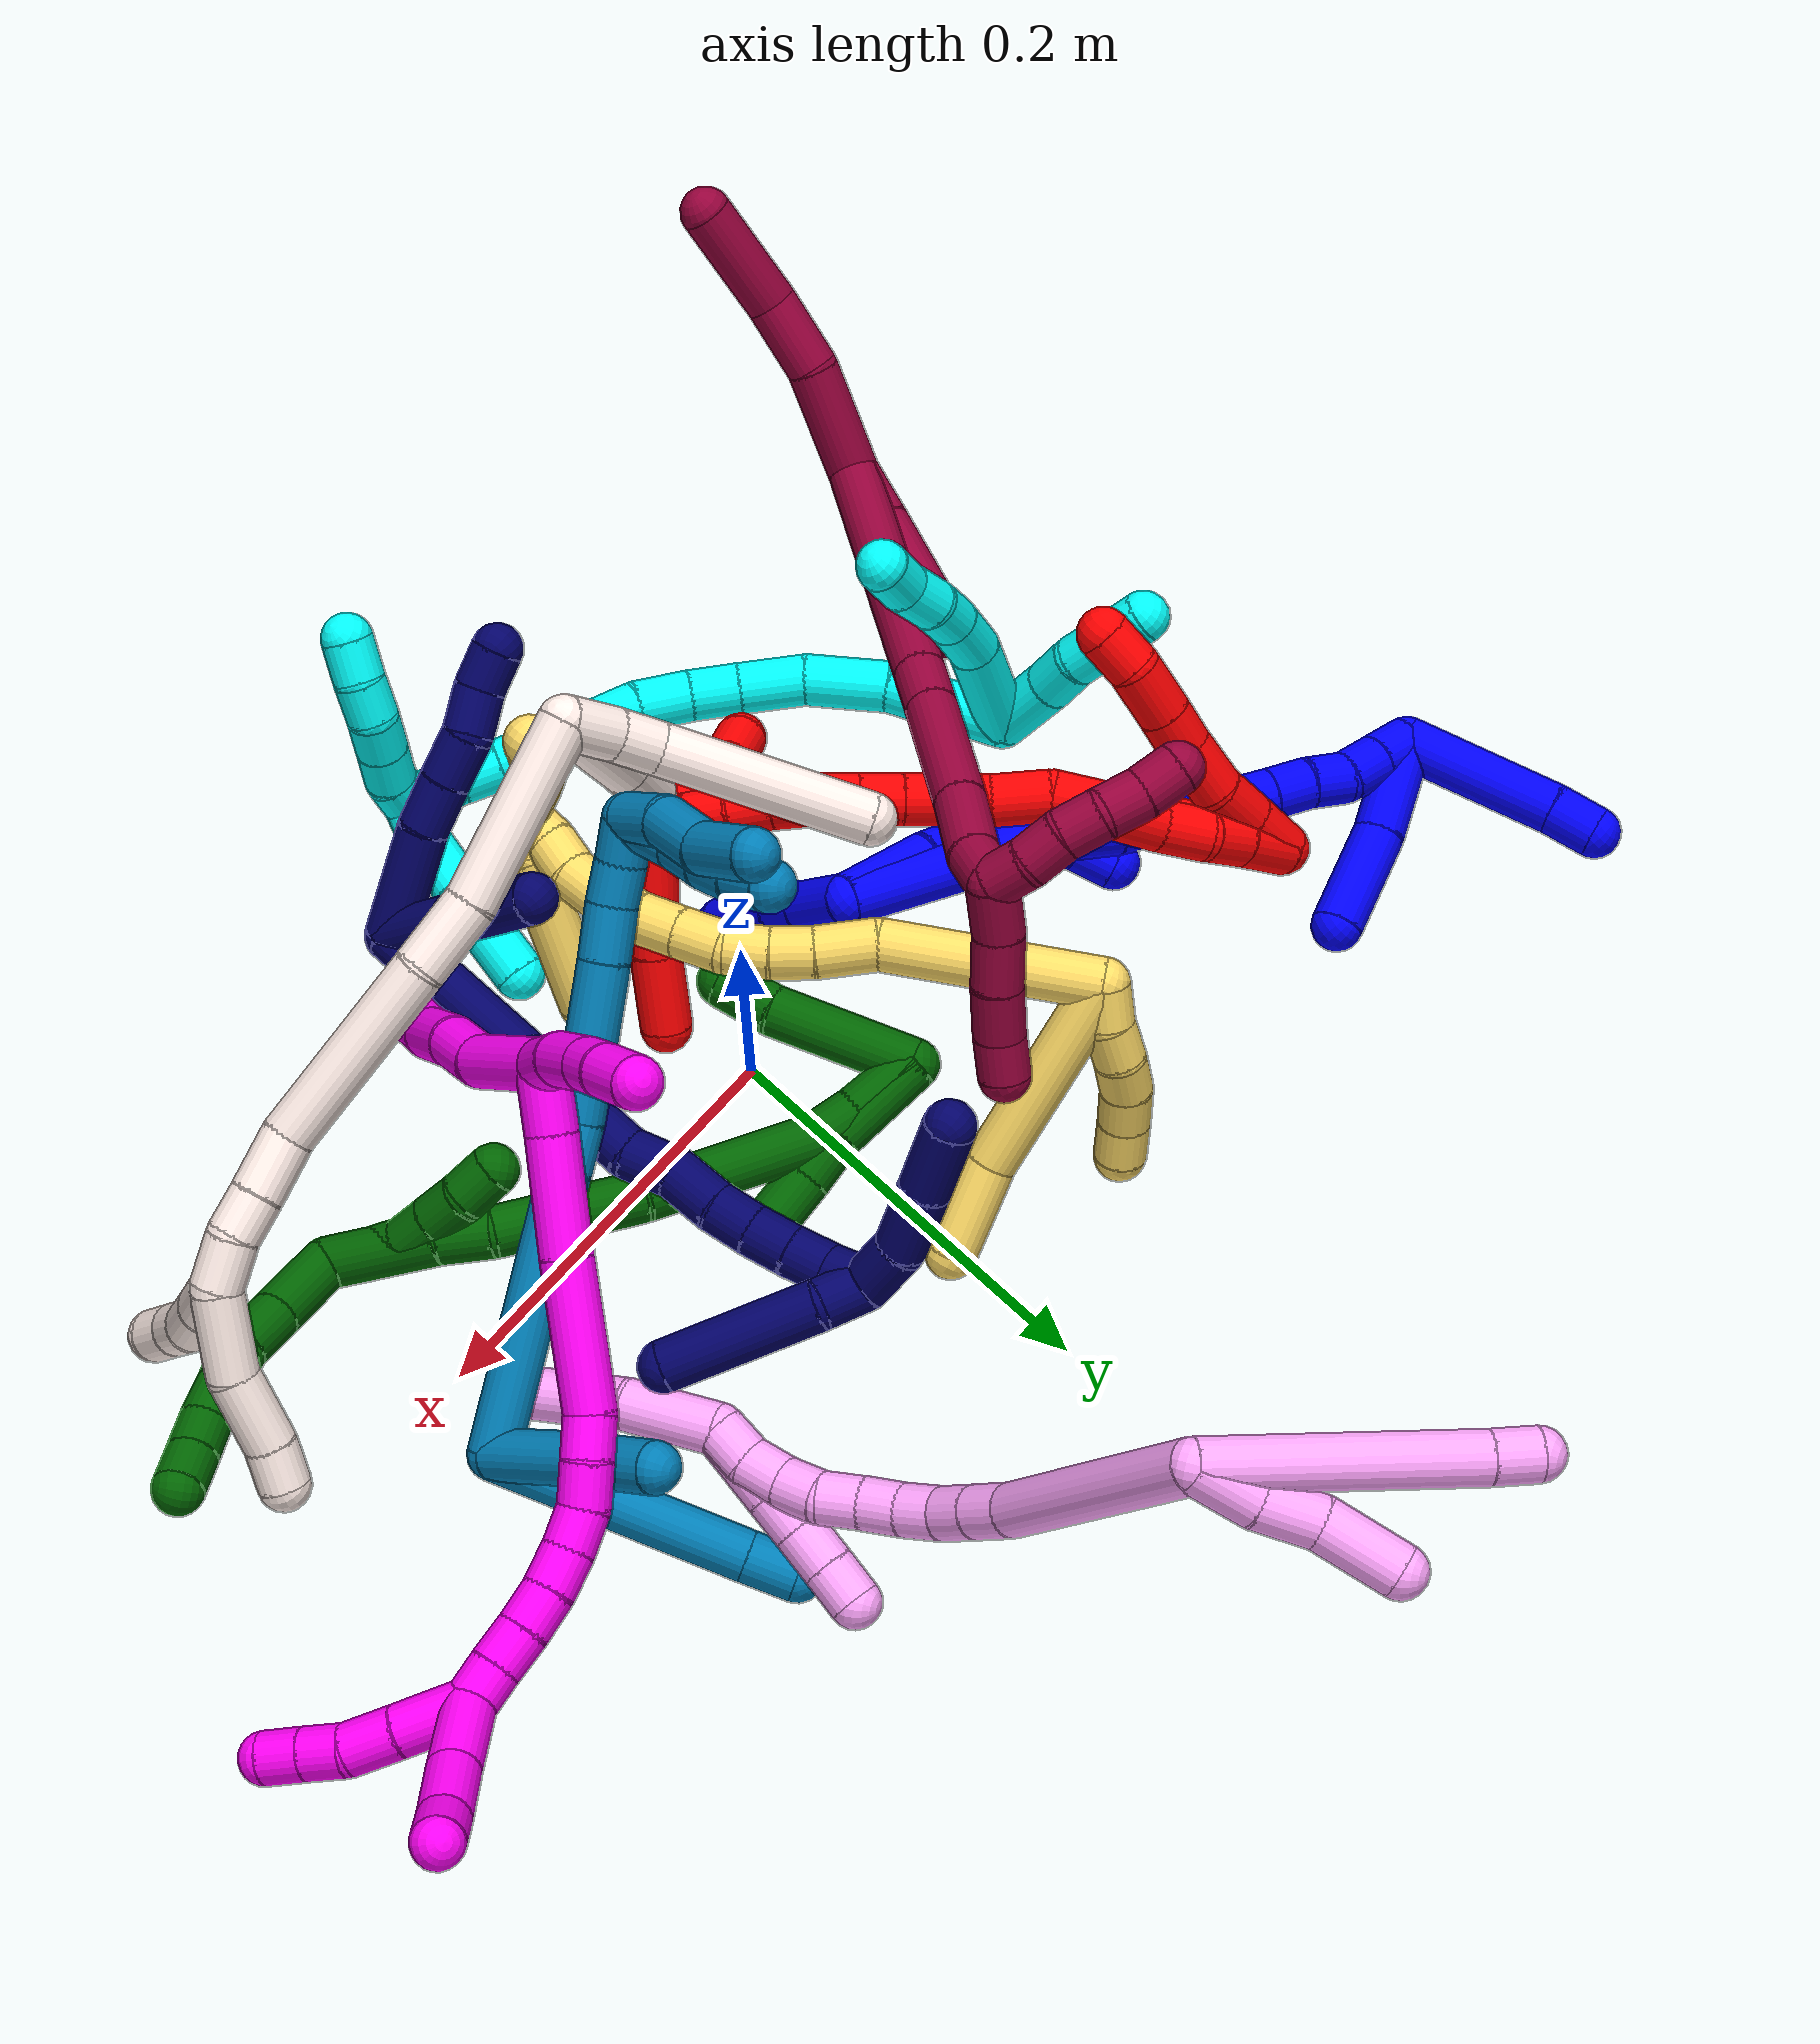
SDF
<sdf version="1.7">
 <world name="default">
  <plugin name="TubeGeneratorPlugin" filename="libtube_generator_plugin.so"/>
  <model name="photoneo_s_sensor">
   <static>1</static>
   <pose>0 0 2 1.57079 1.57079 3.14159</pose>
   <link name="link">
    <inertial><mass>0.1</mass></inertial>
    <sensor name="sensor" type="depth">
     <update_rate>30</update_rate>
     <camera>
      <horizontal_fov>1.22</horizontal_fov>
      <image><width>1920</width><height>1200</height><format>B8G8R8</format></image>
      <clip><near>0.1</near><far>4</far></clip>
      <depth_camera><output>points</output></depth_camera>
     </camera>
     <plugin name="camera_plugin" filename="libgazebo_ros_depth_camera.so">
      <baseline>0.2</baseline>
      <alwaysOn>1</alwaysOn>
      <updateRate>0.0</updateRate>
      <cameraName>camera_ir</cameraName>
      <imageTopicName>/camera/color/image_raw</imageTopicName>
      <cameraInfoTopicName>/camera/color/camera_info</cameraInfoTopicName>
      <depthImageTopicName>/camera/depth/image_raw</depthImageTopicName>
      <depthImageCameraInfoTopicName>/camera/depth/camera_info</depthImageCameraInfoTopicName>
      <pointCloudTopicName>/camera/depth/points</pointCloudTopicName>
      <frameName>fr_optical</frameName>
      <pointCloudCutoff>0.1</pointCloudCutoff>
      <pointCloudCutoffMax>2.0</pointCloudCutoffMax>
      <distortionK1>0</distortionK1>
      <distortionK2>0</distortionK2>
      <distortionK3>0</distortionK3>
      <distortionT1>0</distortionT1>
      <distortionT2>0</distortionT2>
      <CxPrime>0</CxPrime>
      <Cx>0</Cx>
      <Cy>0</Cy>
      <focalLength>0</focalLength>
      <hackBaseline>0</hackBaseline>
     </plugin>
    </sensor>
   </link>
  </model>
  <gravity>0 0 -9.8</gravity>
  <magnetic_field>6e-06 2.3e-05 -4.2e-05</magnetic_field>
  <atmosphere type="adiabatic"/>
  <physics name="default_physics" default="0" type="ode">
   <max_step_size>0.003</max_step_size>
   <real_time_factor>1</real_time_factor>
   <real_time_update_rate>1000</real_time_update_rate>
   <max_contacts>10000</max_contacts>
   <ode>
    <solver>
     <type>quick</type>
     <iters>100</iters>
     <sor>1.3</sor>
     <use_dynamic_moi_rescaling>0</use_dynamic_moi_rescaling>
    </solver>
    <constraints>
     <contact_max_correcting_vel>0</contact_max_correcting_vel>
     <contact_surface_layer>0.001</contact_surface_layer>
     <cfm>0</cfm>
     <erp>0.2</erp>
    </constraints>
   </ode>
  </physics>
  <scene><ambient>0.4 0.4 0.4 1</ambient><background>0.7 0.7 0.7 1</background><shadows>0</shadows></scene>
  <audio><device>default</device></audio>
  <spherical_coordinates>
   <surface_model>EARTH_WGS84</surface_model>
   <latitude_deg>0</latitude_deg>
   <longitude_deg>0</longitude_deg>
   <elevation>0</elevation>
   <heading_deg>0</heading_deg>
  </spherical_coordinates>
  <model name="bin">
   <static>1</static>
   <link name="bottom">
    <collision name="collision-bottom">
     <pose>0 0 -0.01 0 -0 0</pose>
     <geometry><box><size>0.8 0.6 0.02</size></box></geometry>
     <surface>
      <friction><ode><mu>100</mu><mu2>100</mu2></ode></friction>
      <contact><collide_bitmask>65535</collide_bitmask></contact>
     </surface>
    </collision>
   </link>
   <link name="west_wall">
    <collision name="collision-west_wall">
     <pose>-0.41 0 0.1 0 -0 0</pose>
     <geometry><box><size>0.02 0.6 0.2</size></box></geometry>
     <surface>
      <friction><ode><mu>100</mu><mu2>100</mu2></ode></friction>
      <contact><collide_bitmask>65535</collide_bitmask></contact>
     </surface>
    </collision>
   </link>
   <link name="east_wall">
    <collision name="collision-east_wall">
     <pose>0.41 0 0.1 0 -0 0</pose>
     <geometry><box><size>0.02 0.6 0.2</size></box></geometry>
     <surface>
      <friction><ode><mu>100</mu><mu2>100</mu2></ode></friction>
      <contact><collide_bitmask>65535</collide_bitmask></contact>
     </surface>
    </collision>
   </link>
   <link name="south_wall">
    <collision name="collision-south_wall">
     <pose>0 -0.31 0.1 0 -0 0</pose>
     <geometry><box><size>0.8 0.02 0.2</size></box></geometry>
     <surface>
      <friction><ode><mu>100</mu><mu2>100</mu2></ode></friction>
      <contact><collide_bitmask>65535</collide_bitmask></contact>
     </surface>
    </collision>
   </link>
   <link name="north_wall">
    <collision name="collision-north_wall">
     <pose>0 0.31 0.1 0 -0 0</pose>
     <geometry><box><size>0.8 0.02 0.2</size></box></geometry>
     <surface>
      <friction><ode><mu>100</mu><mu2>100</mu2></ode></friction>
      <contact><collide_bitmask>65535</collide_bitmask></contact>
     </surface>
    </collision>
   </link>
  </model>
  <model name="1">
   <static>0</static>
   <link name="1">
    <collision name="collision-cylinder-e_1_2_8">
     <pose>-0.018232 -0.002934 0.013952 0.207279 -0.90714 -0.101318</pose>
     <geometry><cylinder><radius>0.0125</radius><length>0.046289</length></cylinder></geometry>
     <surface>
      <friction><ode><mu>1.16</mu><mu2>1.16</mu2><slip1>0</slip1><slip2>0</slip2></ode></friction>
      <contact><ode><kp>1e+06</kp><kd>1</kd><max_vel>0</max_vel><min_depth>0.001</min_depth></ode></contact>
     </surface>
    </collision>
    <visual name="visual-cylinder-e_1_2_8">
     <pose>-0.018232 -0.002934 0.013952 0.207279 -0.90714 -0.101318</pose>
     <geometry><cylinder><radius>0.0125</radius><length>0.046289</length></cylinder></geometry>
     <material><ambient>0 0 1 1</ambient></material>
    </visual>
    <collision name="collision-cylinder-e_2_8_9">
     <pose>-0.046241 -0.006468 0.033808 0.101266 -1.02529 -0.057029</pose>
     <geometry><cylinder><radius>0.0125</radius><length>0.022875</length></cylinder></geometry>
     <surface>
      <friction><ode><mu>1.16</mu><mu2>1.16</mu2><slip1>0</slip1><slip2>0</slip2></ode></friction>
      <contact><ode><kp>1e+06</kp><kd>1</kd><max_vel>0</max_vel><min_depth>0.001</min_depth></ode></contact>
     </surface>
    </collision>
    <visual name="visual-cylinder-e_2_8_9">
     <pose>-0.046241 -0.006468 0.033808 0.101266 -1.02529 -0.057029</pose>
     <geometry><cylinder><radius>0.0125</radius><length>0.022875</length></cylinder></geometry>
     <material><ambient>0 0 1 1</ambient></material>
    </visual>
    <collision name="collision-cylinder-e_3_9_10">
     <pose>-0.064646 -0.007192 0.045185 0.022611 -1.00534 -0.012431</pose>
     <geometry><cylinder><radius>0.0125</radius><length>0.020435</length></cylinder></geometry>
     <surface>
      <friction><ode><mu>1.16</mu><mu2>1.16</mu2><slip1>0</slip1><slip2>0</slip2></ode></friction>
      <contact><ode><kp>1e+06</kp><kd>1</kd><max_vel>0</max_vel><min_depth>0.001</min_depth></ode></contact>
     </surface>
    </collision>
    <visual name="visual-cylinder-e_3_9_10">
     <pose>-0.064646 -0.007192 0.045185 0.022611 -1.00534 -0.012431</pose>
     <geometry><cylinder><radius>0.0125</radius><length>0.020435</length></cylinder></geometry>
     <material><ambient>0 0 1 1</ambient></material>
    </visual>
    <collision name="collision-cylinder-e_4_10_11">
     <pose>-0.081702 -0.004158 0.055416 -0.585871 -0.975368 0.317273</pose>
     <geometry><cylinder><radius>0.0125</radius><length>0.020364</length></cylinder></geometry>
     <surface>
      <friction><ode><mu>1.16</mu><mu2>1.16</mu2><slip1>0</slip1><slip2>0</slip2></ode></friction>
      <contact><ode><kp>1e+06</kp><kd>1</kd><max_vel>0</max_vel><min_depth>0.001</min_depth></ode></contact>
     </surface>
    </collision>
    <visual name="visual-cylinder-e_4_10_11">
     <pose>-0.081702 -0.004158 0.055416 -0.585871 -0.975368 0.317273</pose>
     <geometry><cylinder><radius>0.0125</radius><length>0.020364</length></cylinder></geometry>
     <material><ambient>0 0 1 1</ambient></material>
    </visual>
    <collision name="collision-cylinder-e_5_11_12">
     <pose>-0.097752 0.00455 0.063525 -1.02764 -0.865834 0.510297</pose>
     <geometry><cylinder><radius>0.0125</radius><length>0.020009</length></cylinder></geometry>
     <surface>
      <friction><ode><mu>1.16</mu><mu2>1.16</mu2><slip1>0</slip1><slip2>0</slip2></ode></friction>
      <contact><ode><kp>1e+06</kp><kd>1</kd><max_vel>0</max_vel><min_depth>0.001</min_depth></ode></contact>
     </surface>
    </collision>
    <visual name="visual-cylinder-e_5_11_12">
     <pose>-0.097752 0.00455 0.063525 -1.02764 -0.865834 0.510297</pose>
     <geometry><cylinder><radius>0.0125</radius><length>0.020009</length></cylinder></geometry>
     <material><ambient>0 0 1 1</ambient></material>
    </visual>
    <collision name="collision-cylinder-e_6_12_6">
     <pose>-0.110598 0.017792 0.070591 -1.12086 -0.548991 0.349829</pose>
     <geometry><cylinder><radius>0.0125</radius><length>0.020029</length></cylinder></geometry>
     <surface>
      <friction><ode><mu>1.16</mu><mu2>1.16</mu2><slip1>0</slip1><slip2>0</slip2></ode></friction>
      <contact><ode><kp>1e+06</kp><kd>1</kd><max_vel>0</max_vel><min_depth>0.001</min_depth></ode></contact>
     </surface>
    </collision>
    <visual name="visual-cylinder-e_6_12_6">
     <pose>-0.110598 0.017792 0.070591 -1.12086 -0.548991 0.349829</pose>
     <geometry><cylinder><radius>0.0125</radius><length>0.020029</length></cylinder></geometry>
     <material><ambient>0 0 1 1</ambient></material>
    </visual>
    <collision name="collision-cylinder-e_1_2_13">
     <pose>-0.006488 -0.007609 -0.013626 2.63233 -0.393966 -1.30828</pose>
     <geometry><cylinder><radius>0.0125</radius><length>0.033803</length></cylinder></geometry>
     <surface>
      <friction><ode><mu>1.16</mu><mu2>1.16</mu2><slip1>0</slip1><slip2>0</slip2></ode></friction>
      <contact><ode><kp>1e+06</kp><kd>1</kd><max_vel>0</max_vel><min_depth>0.001</min_depth></ode></contact>
     </surface>
    </collision>
    <visual name="visual-cylinder-e_1_2_13">
     <pose>-0.006488 -0.007609 -0.013626 2.63233 -0.393966 -1.30828</pose>
     <geometry><cylinder><radius>0.0125</radius><length>0.033803</length></cylinder></geometry>
     <material><ambient>0 0 1 1</ambient></material>
    </visual>
    <collision name="collision-cylinder-e_2_13_14">
     <pose>-0.016538 -0.021013 -0.035154 2.50878 -0.348741 -0.987238</pose>
     <geometry><cylinder><radius>0.0125</radius><length>0.020853</length></cylinder></geometry>
     <surface>
      <friction><ode><mu>1.16</mu><mu2>1.16</mu2><slip1>0</slip1><slip2>0</slip2></ode></friction>
      <contact><ode><kp>1e+06</kp><kd>1</kd><max_vel>0</max_vel><min_depth>0.001</min_depth></ode></contact>
     </surface>
    </collision>
    <visual name="visual-cylinder-e_2_13_14">
     <pose>-0.016538 -0.021013 -0.035154 2.50878 -0.348741 -0.987238</pose>
     <geometry><cylinder><radius>0.0125</radius><length>0.020853</length></cylinder></geometry>
     <material><ambient>0 0 1 1</ambient></material>
    </visual>
    <collision name="collision-cylinder-e_3_14_5">
     <pose>-0.028556 -0.035525 -0.062201 2.71435 -0.382137 -1.45636</pose>
     <geometry><cylinder><radius>0.0125</radius><length>0.045345</length></cylinder></geometry>
     <surface>
      <friction><ode><mu>1.16</mu><mu2>1.16</mu2><slip1>0</slip1><slip2>0</slip2></ode></friction>
      <contact><ode><kp>1e+06</kp><kd>1</kd><max_vel>0</max_vel><min_depth>0.001</min_depth></ode></contact>
     </surface>
    </collision>
    <visual name="visual-cylinder-e_3_14_5">
     <pose>-0.028556 -0.035525 -0.062201 2.71435 -0.382137 -1.45636</pose>
     <geometry><cylinder><radius>0.0125</radius><length>0.045345</length></cylinder></geometry>
     <material><ambient>0 0 1 1</ambient></material>
    </visual>
    <collision name="collision-cylinder-e_1_2_15">
     <pose>-0.041131 0.004848 0.03624 -0.132986 -0.844125 0.059787</pose>
     <geometry><cylinder><radius>0.0125</radius><length>0.110066</length></cylinder></geometry>
     <surface>
      <friction><ode><mu>1.16</mu><mu2>1.16</mu2><slip1>0</slip1><slip2>0</slip2></ode></friction>
      <contact><ode><kp>1e+06</kp><kd>1</kd><max_vel>0</max_vel><min_depth>0.001</min_depth></ode></contact>
     </surface>
    </collision>
    <visual name="visual-cylinder-e_1_2_15">
     <pose>-0.041131 0.004848 0.03624 -0.132986 -0.844125 0.059787</pose>
     <geometry><cylinder><radius>0.0125</radius><length>0.110066</length></cylinder></geometry>
     <material><ambient>0 0 1 1</ambient></material>
    </visual>
    <collision name="collision-cylinder-e_2_15_16">
     <pose>-0.093651 0.013058 0.080846 -0.38213 -0.901186 0.186609</pose>
     <geometry><cylinder><radius>0.0125</radius><length>0.02905</length></cylinder></geometry>
     <surface>
      <friction><ode><mu>1.16</mu><mu2>1.16</mu2><slip1>0</slip1><slip2>0</slip2></ode></friction>
      <contact><ode><kp>1e+06</kp><kd>1</kd><max_vel>0</max_vel><min_depth>0.001</min_depth></ode></contact>
     </surface>
    </collision>
    <visual name="visual-cylinder-e_2_15_16">
     <pose>-0.093651 0.013058 0.080846 -0.38213 -0.901186 0.186609</pose>
     <geometry><cylinder><radius>0.0125</radius><length>0.02905</length></cylinder></geometry>
     <material><ambient>0 0 1 1</ambient></material>
    </visual>
    <collision name="collision-cylinder-e_3_16_17">
     <pose>-0.111972 0.018387 0.096661 -0.258173 -0.732656 0.099518</pose>
     <geometry><cylinder><radius>0.0125</radius><length>0.02073</length></cylinder></geometry>
     <surface>
      <friction><ode><mu>1.16</mu><mu2>1.16</mu2><slip1>0</slip1><slip2>0</slip2></ode></friction>
      <contact><ode><kp>1e+06</kp><kd>1</kd><max_vel>0</max_vel><min_depth>0.001</min_depth></ode></contact>
     </surface>
    </collision>
    <visual name="visual-cylinder-e_3_16_17">
     <pose>-0.111972 0.018387 0.096661 -0.258173 -0.732656 0.099518</pose>
     <geometry><cylinder><radius>0.0125</radius><length>0.02073</length></cylinder></geometry>
     <material><ambient>0 0 1 1</ambient></material>
    </visual>
    <collision name="collision-cylinder-e_4_17_18">
     <pose>-0.126953 0.022292 0.109854 -0.32542 -0.925365 0.163401</pose>
     <geometry><cylinder><radius>0.0125</radius><length>0.020151</length></cylinder></geometry>
     <surface>
      <friction><ode><mu>1.16</mu><mu2>1.16</mu2><slip1>0</slip1><slip2>0</slip2></ode></friction>
      <contact><ode><kp>1e+06</kp><kd>1</kd><max_vel>0</max_vel><min_depth>0.001</min_depth></ode></contact>
     </surface>
    </collision>
    <visual name="visual-cylinder-e_4_17_18">
     <pose>-0.126953 0.022292 0.109854 -0.32542 -0.925365 0.163401</pose>
     <geometry><cylinder><radius>0.0125</radius><length>0.020151</length></cylinder></geometry>
     <material><ambient>0 0 1 1</ambient></material>
    </visual>
    <collision name="collision-cylinder-e_5_18_19">
     <pose>-0.143365 0.025007 0.121026 -0.142209 -0.99026 0.076884</pose>
     <geometry><cylinder><radius>0.0125</radius><length>0.020002</length></cylinder></geometry>
     <surface>
      <friction><ode><mu>1.16</mu><mu2>1.16</mu2><slip1>0</slip1><slip2>0</slip2></ode></friction>
      <contact><ode><kp>1e+06</kp><kd>1</kd><max_vel>0</max_vel><min_depth>0.001</min_depth></ode></contact>
     </surface>
    </collision>
    <visual name="visual-cylinder-e_5_18_19">
     <pose>-0.143365 0.025007 0.121026 -0.142209 -0.99026 0.076884</pose>
     <geometry><cylinder><radius>0.0125</radius><length>0.020002</length></cylinder></geometry>
     <material><ambient>0 0 1 1</ambient></material>
    </visual>
    <collision name="collision-cylinder-e_6_19_20">
     <pose>-0.158896 0.027196 0.133284 -0.203794 -0.799329 0.086328</pose>
     <geometry><cylinder><radius>0.0125</radius><length>0.020001</length></cylinder></geometry>
     <surface>
      <friction><ode><mu>1.16</mu><mu2>1.16</mu2><slip1>0</slip1><slip2>0</slip2></ode></friction>
      <contact><ode><kp>1e+06</kp><kd>1</kd><max_vel>0</max_vel><min_depth>0.001</min_depth></ode></contact>
     </surface>
    </collision>
    <visual name="visual-cylinder-e_6_19_20">
     <pose>-0.158896 0.027196 0.133284 -0.203794 -0.799329 0.086328</pose>
     <geometry><cylinder><radius>0.0125</radius><length>0.020001</length></cylinder></geometry>
     <material><ambient>0 0 1 1</ambient></material>
    </visual>
    <collision name="collision-cylinder-e_7_20_21">
     <pose>-0.173267 0.029738 0.146957 -0.163797 -0.804044 0.069771</pose>
     <geometry><cylinder><radius>0.0125</radius><length>0.02</length></cylinder></geometry>
     <surface>
      <friction><ode><mu>1.16</mu><mu2>1.16</mu2><slip1>0</slip1><slip2>0</slip2></ode></friction>
      <contact><ode><kp>1e+06</kp><kd>1</kd><max_vel>0</max_vel><min_depth>0.001</min_depth></ode></contact>
     </surface>
    </collision>
    <visual name="visual-cylinder-e_7_20_21">
     <pose>-0.173267 0.029738 0.146957 -0.163797 -0.804044 0.069771</pose>
     <geometry><cylinder><radius>0.0125</radius><length>0.02</length></cylinder></geometry>
     <material><ambient>0 0 1 1</ambient></material>
    </visual>
    <collision name="collision-cylinder-e_8_21_22">
     <pose>-0.188247 0.032944 0.159735 -0.336383 -0.891229 0.161854</pose>
     <geometry><cylinder><radius>0.0125</radius><length>0.02</length></cylinder></geometry>
     <surface>
      <friction><ode><mu>1.16</mu><mu2>1.16</mu2><slip1>0</slip1><slip2>0</slip2></ode></friction>
      <contact><ode><kp>1e+06</kp><kd>1</kd><max_vel>0</max_vel><min_depth>0.001</min_depth></ode></contact>
     </surface>
    </collision>
    <visual name="visual-cylinder-e_8_21_22">
     <pose>-0.188247 0.032944 0.159735 -0.336383 -0.891229 0.161854</pose>
     <geometry><cylinder><radius>0.0125</radius><length>0.02</length></cylinder></geometry>
     <material><ambient>0 0 1 1</ambient></material>
    </visual>
    <collision name="collision-cylinder-e_9_22_23">
     <pose>-0.203751 0.033633 0.171864 0.219856 -0.882837 -0.104211</pose>
     <geometry><cylinder><radius>0.0125</radius><length>0.02</length></cylinder></geometry>
     <surface>
      <friction><ode><mu>1.16</mu><mu2>1.16</mu2><slip1>0</slip1><slip2>0</slip2></ode></friction>
      <contact><ode><kp>1e+06</kp><kd>1</kd><max_vel>0</max_vel><min_depth>0.001</min_depth></ode></contact>
     </surface>
    </collision>
    <visual name="visual-cylinder-e_9_22_23">
     <pose>-0.203751 0.033633 0.171864 0.219856 -0.882837 -0.104211</pose>
     <geometry><cylinder><radius>0.0125</radius><length>0.02</length></cylinder></geometry>
     <material><ambient>0 0 1 1</ambient></material>
    </visual>
    <collision name="collision-cylinder-e_10_23_1">
     <pose>-0.219188 0.030858 0.184274 0.220135 -0.880608 -0.104044</pose>
     <geometry><cylinder><radius>0.0125</radius><length>0.02</length></cylinder></geometry>
     <surface>
      <friction><ode><mu>1.16</mu><mu2>1.16</mu2><slip1>0</slip1><slip2>0</slip2></ode></friction>
      <contact><ode><kp>1e+06</kp><kd>1</kd><max_vel>0</max_vel><min_depth>0.001</min_depth></ode></contact>
     </surface>
    </collision>
    <visual name="visual-cylinder-e_10_23_1">
     <pose>-0.219188 0.030858 0.184274 0.220135 -0.880608 -0.104044</pose>
     <geometry><cylinder><radius>0.0125</radius><length>0.02</length></cylinder></geometry>
     <material><ambient>0 0 1 1</ambient></material>
    </visual>
    <collision name="collision-cylinder-e_1_1_24">
     <pose>-0.238278 0.061445 0.208951 -1.04715 -0.298927 0.173437</pose>
     <geometry><cylinder><radius>0.0125</radius><length>0.077276</length></cylinder></geometry>
     <surface>
      <friction><ode><mu>1.16</mu><mu2>1.16</mu2><slip1>0</slip1><slip2>0</slip2></ode></friction>
      <contact><ode><kp>1e+06</kp><kd>1</kd><max_vel>0</max_vel><min_depth>0.001</min_depth></ode></contact>
     </surface>
    </collision>
    <visual name="visual-cylinder-e_1_1_24">
     <pose>-0.238278 0.061445 0.208951 -1.04715 -0.298927 0.173437</pose>
     <geometry><cylinder><radius>0.0125</radius><length>0.077276</length></cylinder></geometry>
     <material><ambient>0 0 1 1</ambient></material>
    </visual>
    <collision name="collision-cylinder-e_2_24_4">
     <pose>-0.253187 0.10322 0.231955 -1.13683 -0.315973 0.202821</pose>
     <geometry><cylinder><radius>0.0125</radius><length>0.022724</length></cylinder></geometry>
     <surface>
      <friction><ode><mu>1.16</mu><mu2>1.16</mu2><slip1>0</slip1><slip2>0</slip2></ode></friction>
      <contact><ode><kp>1e+06</kp><kd>1</kd><max_vel>0</max_vel><min_depth>0.001</min_depth></ode></contact>
     </surface>
    </collision>
    <visual name="visual-cylinder-e_2_24_4">
     <pose>-0.253187 0.10322 0.231955 -1.13683 -0.315973 0.202821</pose>
     <geometry><cylinder><radius>0.0125</radius><length>0.022724</length></cylinder></geometry>
     <material><ambient>0 0 1 1</ambient></material>
    </visual>
    <collision name="collision-cylinder-e_1_1_25">
     <pose>-0.218035 0.04652 0.175432 -2.29408 0.371566 -0.789573</pose>
     <geometry><cylinder><radius>0.0125</radius><length>0.048826</length></cylinder></geometry>
     <surface>
      <friction><ode><mu>1.16</mu><mu2>1.16</mu2><slip1>0</slip1><slip2>0</slip2></ode></friction>
      <contact><ode><kp>1e+06</kp><kd>1</kd><max_vel>0</max_vel><min_depth>0.001</min_depth></ode></contact>
     </surface>
    </collision>
    <visual name="visual-cylinder-e_1_1_25">
     <pose>-0.218035 0.04652 0.175432 -2.29408 0.371566 -0.789573</pose>
     <geometry><cylinder><radius>0.0125</radius><length>0.048826</length></cylinder></geometry>
     <material><ambient>0 0 1 1</ambient></material>
    </visual>
    <collision name="collision-cylinder-e_2_25_3">
     <pose>-0.197266 0.079094 0.143883 -2.38655 0.483958 -1.11349</pose>
     <geometry><cylinder><radius>0.0125</radius><length>0.051174</length></cylinder></geometry>
     <surface>
      <friction><ode><mu>1.16</mu><mu2>1.16</mu2><slip1>0</slip1><slip2>0</slip2></ode></friction>
      <contact><ode><kp>1e+06</kp><kd>1</kd><max_vel>0</max_vel><min_depth>0.001</min_depth></ode></contact>
     </surface>
    </collision>
    <visual name="visual-cylinder-e_2_25_3">
     <pose>-0.197266 0.079094 0.143883 -2.38655 0.483958 -1.11349</pose>
     <geometry><cylinder><radius>0.0125</radius><length>0.051174</length></cylinder></geometry>
     <material><ambient>0 0 1 1</ambient></material>
    </visual>
    <collision name="collision-sphere-3">
     <pose>-0.185361 0.094615 0.127389 0 -0 0</pose>
     <geometry><sphere><radius>0.0125</radius></sphere></geometry>
     <surface>
      <friction><ode><mu>1.16</mu><mu2>1.16</mu2><slip1>0</slip1><slip2>0</slip2></ode></friction>
      <contact><ode><kp>1e+06</kp><kd>1</kd><max_vel>0</max_vel><min_depth>0.001</min_depth></ode></contact>
     </surface>
    </collision>
    <visual name="visual-sphere-3">
     <pose>-0.185361 0.094615 0.127389 0 -0 0</pose>
     <geometry><sphere><radius>0.0125</radius></sphere></geometry>
     <material><ambient>0 0 1 1</ambient></material>
    </visual>
    <collision name="collision-sphere-25">
     <pose>-0.209172 0.063572 0.160377 0 -0 0</pose>
     <geometry><sphere><radius>0.0125</radius></sphere></geometry>
     <surface>
      <friction><ode><mu>1.16</mu><mu2>1.16</mu2><slip1>0</slip1><slip2>0</slip2></ode></friction>
      <contact><ode><kp>1e+06</kp><kd>1</kd><max_vel>0</max_vel><min_depth>0.001</min_depth></ode></contact>
     </surface>
    </collision>
    <visual name="visual-sphere-25">
     <pose>-0.209172 0.063572 0.160377 0 -0 0</pose>
     <geometry><sphere><radius>0.0125</radius></sphere></geometry>
     <material><ambient>0 0 1 1</ambient></material>
    </visual>
    <collision name="collision-sphere-4">
     <pose>-0.256718 0.113018 0.236496 0 -0 0</pose>
     <geometry><sphere><radius>0.0125</radius></sphere></geometry>
     <surface>
      <friction><ode><mu>1.16</mu><mu2>1.16</mu2><slip1>0</slip1><slip2>0</slip2></ode></friction>
      <contact><ode><kp>1e+06</kp><kd>1</kd><max_vel>0</max_vel><min_depth>0.001</min_depth></ode></contact>
     </surface>
    </collision>
    <visual name="visual-sphere-4">
     <pose>-0.256718 0.113018 0.236496 0 -0 0</pose>
     <geometry><sphere><radius>0.0125</radius></sphere></geometry>
     <material><ambient>0 0 1 1</ambient></material>
    </visual>
    <collision name="collision-sphere-24">
     <pose>-0.249656 0.093421 0.227414 0 -0 0</pose>
     <geometry><sphere><radius>0.0125</radius></sphere></geometry>
     <surface>
      <friction><ode><mu>1.16</mu><mu2>1.16</mu2><slip1>0</slip1><slip2>0</slip2></ode></friction>
      <contact><ode><kp>1e+06</kp><kd>1</kd><max_vel>0</max_vel><min_depth>0.001</min_depth></ode></contact>
     </surface>
    </collision>
    <visual name="visual-sphere-24">
     <pose>-0.249656 0.093421 0.227414 0 -0 0</pose>
     <geometry><sphere><radius>0.0125</radius></sphere></geometry>
     <material><ambient>0 0 1 1</ambient></material>
    </visual>
    <collision name="collision-sphere-1">
     <pose>-0.226899 0.029468 0.190487 0 -0 0</pose>
     <geometry><sphere><radius>0.0125</radius></sphere></geometry>
     <surface>
      <friction><ode><mu>1.16</mu><mu2>1.16</mu2><slip1>0</slip1><slip2>0</slip2></ode></friction>
      <contact><ode><kp>1e+06</kp><kd>1</kd><max_vel>0</max_vel><min_depth>0.001</min_depth></ode></contact>
     </surface>
    </collision>
    <visual name="visual-sphere-1">
     <pose>-0.226899 0.029468 0.190487 0 -0 0</pose>
     <geometry><sphere><radius>0.0125</radius></sphere></geometry>
     <material><ambient>0 0 1 1</ambient></material>
    </visual>
    <collision name="collision-sphere-23">
     <pose>-0.211477 0.032249 0.17806 0 -0 0</pose>
     <geometry><sphere><radius>0.0125</radius></sphere></geometry>
     <surface>
      <friction><ode><mu>1.16</mu><mu2>1.16</mu2><slip1>0</slip1><slip2>0</slip2></ode></friction>
      <contact><ode><kp>1e+06</kp><kd>1</kd><max_vel>0</max_vel><min_depth>0.001</min_depth></ode></contact>
     </surface>
    </collision>
    <visual name="visual-sphere-23">
     <pose>-0.211477 0.032249 0.17806 0 -0 0</pose>
     <geometry><sphere><radius>0.0125</radius></sphere></geometry>
     <material><ambient>0 0 1 1</ambient></material>
    </visual>
    <collision name="collision-sphere-22">
     <pose>-0.196026 0.035018 0.165667 0 -0 0</pose>
     <geometry><sphere><radius>0.0125</radius></sphere></geometry>
     <surface>
      <friction><ode><mu>1.16</mu><mu2>1.16</mu2><slip1>0</slip1><slip2>0</slip2></ode></friction>
      <contact><ode><kp>1e+06</kp><kd>1</kd><max_vel>0</max_vel><min_depth>0.001</min_depth></ode></contact>
     </surface>
    </collision>
    <visual name="visual-sphere-22">
     <pose>-0.196026 0.035018 0.165667 0 -0 0</pose>
     <geometry><sphere><radius>0.0125</radius></sphere></geometry>
     <material><ambient>0 0 1 1</ambient></material>
    </visual>
    <collision name="collision-sphere-21">
     <pose>-0.180469 0.030869 0.153802 0 -0 0</pose>
     <geometry><sphere><radius>0.0125</radius></sphere></geometry>
     <surface>
      <friction><ode><mu>1.16</mu><mu2>1.16</mu2><slip1>0</slip1><slip2>0</slip2></ode></friction>
      <contact><ode><kp>1e+06</kp><kd>1</kd><max_vel>0</max_vel><min_depth>0.001</min_depth></ode></contact>
     </surface>
    </collision>
    <visual name="visual-sphere-21">
     <pose>-0.180469 0.030869 0.153802 0 -0 0</pose>
     <geometry><sphere><radius>0.0125</radius></sphere></geometry>
     <material><ambient>0 0 1 1</ambient></material>
    </visual>
    <collision name="collision-sphere-12">
     <pose>-0.105372 0.0101 0.066876 0 -0 0</pose>
     <geometry><sphere><radius>0.0125</radius></sphere></geometry>
     <surface>
      <friction><ode><mu>1.16</mu><mu2>1.16</mu2><slip1>0</slip1><slip2>0</slip2></ode></friction>
      <contact><ode><kp>1e+06</kp><kd>1</kd><max_vel>0</max_vel><min_depth>0.001</min_depth></ode></contact>
     </surface>
    </collision>
    <visual name="visual-sphere-12">
     <pose>-0.105372 0.0101 0.066876 0 -0 0</pose>
     <geometry><sphere><radius>0.0125</radius></sphere></geometry>
     <material><ambient>0 0 1 1</ambient></material>
    </visual>
    <collision name="collision-sphere-11">
     <pose>-0.090132 -0.001 0.060174 0 -0 0</pose>
     <geometry><sphere><radius>0.0125</radius></sphere></geometry>
     <surface>
      <friction><ode><mu>1.16</mu><mu2>1.16</mu2><slip1>0</slip1><slip2>0</slip2></ode></friction>
      <contact><ode><kp>1e+06</kp><kd>1</kd><max_vel>0</max_vel><min_depth>0.001</min_depth></ode></contact>
     </surface>
    </collision>
    <visual name="visual-sphere-11">
     <pose>-0.090132 -0.001 0.060174 0 -0 0</pose>
     <geometry><sphere><radius>0.0125</radius></sphere></geometry>
     <material><ambient>0 0 1 1</ambient></material>
    </visual>
    <collision name="collision-sphere-10">
     <pose>-0.073273 -0.007316 0.050658 0 -0 0</pose>
     <geometry><sphere><radius>0.0125</radius></sphere></geometry>
     <surface>
      <friction><ode><mu>1.16</mu><mu2>1.16</mu2><slip1>0</slip1><slip2>0</slip2></ode></friction>
      <contact><ode><kp>1e+06</kp><kd>1</kd><max_vel>0</max_vel><min_depth>0.001</min_depth></ode></contact>
     </surface>
    </collision>
    <visual name="visual-sphere-10">
     <pose>-0.073273 -0.007316 0.050658 0 -0 0</pose>
     <geometry><sphere><radius>0.0125</radius></sphere></geometry>
     <material><ambient>0 0 1 1</ambient></material>
    </visual>
    <collision name="collision-sphere-9">
     <pose>-0.056019 -0.007068 0.039712 0 -0 0</pose>
     <geometry><sphere><radius>0.0125</radius></sphere></geometry>
     <surface>
      <friction><ode><mu>1.16</mu><mu2>1.16</mu2><slip1>0</slip1><slip2>0</slip2></ode></friction>
      <contact><ode><kp>1e+06</kp><kd>1</kd><max_vel>0</max_vel><min_depth>0.001</min_depth></ode></contact>
     </surface>
    </collision>
    <visual name="visual-sphere-9">
     <pose>-0.056019 -0.007068 0.039712 0 -0 0</pose>
     <geometry><sphere><radius>0.0125</radius></sphere></geometry>
     <material><ambient>0 0 1 1</ambient></material>
    </visual>
    <collision name="collision-sphere-2">
     <geometry><sphere><radius>0.0125</radius></sphere></geometry>
     <surface>
      <friction><ode><mu>1.16</mu><mu2>1.16</mu2><slip1>0</slip1><slip2>0</slip2></ode></friction>
      <contact><ode><kp>1e+06</kp><kd>1</kd><max_vel>0</max_vel><min_depth>0.001</min_depth></ode></contact>
     </surface>
    </collision>
    <visual name="visual-sphere-2">
     <geometry><sphere><radius>0.0125</radius></sphere></geometry>
     <material><ambient>0 0 1 1</ambient></material>
    </visual>
    <collision name="collision-sphere-19">
     <pose>-0.151727 0.025785 0.126456 0 -0 0</pose>
     <geometry><sphere><radius>0.0125</radius></sphere></geometry>
     <surface>
      <friction><ode><mu>1.16</mu><mu2>1.16</mu2><slip1>0</slip1><slip2>0</slip2></ode></friction>
      <contact><ode><kp>1e+06</kp><kd>1</kd><max_vel>0</max_vel><min_depth>0.001</min_depth></ode></contact>
     </surface>
    </collision>
    <visual name="visual-sphere-19">
     <pose>-0.151727 0.025785 0.126456 0 -0 0</pose>
     <geometry><sphere><radius>0.0125</radius></sphere></geometry>
     <material><ambient>0 0 1 1</ambient></material>
    </visual>
    <collision name="collision-sphere-8">
     <pose>-0.036464 -0.005868 0.027904 0 -0 0</pose>
     <geometry><sphere><radius>0.0125</radius></sphere></geometry>
     <surface>
      <friction><ode><mu>1.16</mu><mu2>1.16</mu2><slip1>0</slip1><slip2>0</slip2></ode></friction>
      <contact><ode><kp>1e+06</kp><kd>1</kd><max_vel>0</max_vel><min_depth>0.001</min_depth></ode></contact>
     </surface>
    </collision>
    <visual name="visual-sphere-8">
     <pose>-0.036464 -0.005868 0.027904 0 -0 0</pose>
     <geometry><sphere><radius>0.0125</radius></sphere></geometry>
     <material><ambient>0 0 1 1</ambient></material>
    </visual>
    <collision name="collision-sphere-6">
     <pose>-0.115823 0.025485 0.074306 0 -0 0</pose>
     <geometry><sphere><radius>0.0125</radius></sphere></geometry>
     <surface>
      <friction><ode><mu>1.16</mu><mu2>1.16</mu2><slip1>0</slip1><slip2>0</slip2></ode></friction>
      <contact><ode><kp>1e+06</kp><kd>1</kd><max_vel>0</max_vel><min_depth>0.001</min_depth></ode></contact>
     </surface>
    </collision>
    <visual name="visual-sphere-6">
     <pose>-0.115823 0.025485 0.074306 0 -0 0</pose>
     <geometry><sphere><radius>0.0125</radius></sphere></geometry>
     <material><ambient>0 0 1 1</ambient></material>
    </visual>
    <collision name="collision-sphere-13">
     <pose>-0.012975 -0.015217 -0.027252 0 -0 0</pose>
     <geometry><sphere><radius>0.0125</radius></sphere></geometry>
     <surface>
      <friction><ode><mu>1.16</mu><mu2>1.16</mu2><slip1>0</slip1><slip2>0</slip2></ode></friction>
      <contact><ode><kp>1e+06</kp><kd>1</kd><max_vel>0</max_vel><min_depth>0.001</min_depth></ode></contact>
     </surface>
    </collision>
    <visual name="visual-sphere-13">
     <pose>-0.012975 -0.015217 -0.027252 0 -0 0</pose>
     <geometry><sphere><radius>0.0125</radius></sphere></geometry>
     <material><ambient>0 0 1 1</ambient></material>
    </visual>
    <collision name="collision-sphere-14">
     <pose>-0.020101 -0.026808 -0.043055 0 -0 0</pose>
     <geometry><sphere><radius>0.0125</radius></sphere></geometry>
     <surface>
      <friction><ode><mu>1.16</mu><mu2>1.16</mu2><slip1>0</slip1><slip2>0</slip2></ode></friction>
      <contact><ode><kp>1e+06</kp><kd>1</kd><max_vel>0</max_vel><min_depth>0.001</min_depth></ode></contact>
     </surface>
    </collision>
    <visual name="visual-sphere-14">
     <pose>-0.020101 -0.026808 -0.043055 0 -0 0</pose>
     <geometry><sphere><radius>0.0125</radius></sphere></geometry>
     <material><ambient>0 0 1 1</ambient></material>
    </visual>
    <collision name="collision-sphere-5">
     <pose>-0.03701 -0.044242 -0.081347 0 -0 0</pose>
     <geometry><sphere><radius>0.0125</radius></sphere></geometry>
     <surface>
      <friction><ode><mu>1.16</mu><mu2>1.16</mu2><slip1>0</slip1><slip2>0</slip2></ode></friction>
      <contact><ode><kp>1e+06</kp><kd>1</kd><max_vel>0</max_vel><min_depth>0.001</min_depth></ode></contact>
     </surface>
    </collision>
    <visual name="visual-sphere-5">
     <pose>-0.03701 -0.044242 -0.081347 0 -0 0</pose>
     <geometry><sphere><radius>0.0125</radius></sphere></geometry>
     <material><ambient>0 0 1 1</ambient></material>
    </visual>
    <collision name="collision-sphere-15">
     <pose>-0.082262 0.009696 0.072481 0 -0 0</pose>
     <geometry><sphere><radius>0.0125</radius></sphere></geometry>
     <surface>
      <friction><ode><mu>1.16</mu><mu2>1.16</mu2><slip1>0</slip1><slip2>0</slip2></ode></friction>
      <contact><ode><kp>1e+06</kp><kd>1</kd><max_vel>0</max_vel><min_depth>0.001</min_depth></ode></contact>
     </surface>
    </collision>
    <visual name="visual-sphere-15">
     <pose>-0.082262 0.009696 0.072481 0 -0 0</pose>
     <geometry><sphere><radius>0.0125</radius></sphere></geometry>
     <material><ambient>0 0 1 1</ambient></material>
    </visual>
    <collision name="collision-sphere-16">
     <pose>-0.105039 0.01642 0.089211 0 -0 0</pose>
     <geometry><sphere><radius>0.0125</radius></sphere></geometry>
     <surface>
      <friction><ode><mu>1.16</mu><mu2>1.16</mu2><slip1>0</slip1><slip2>0</slip2></ode></friction>
      <contact><ode><kp>1e+06</kp><kd>1</kd><max_vel>0</max_vel><min_depth>0.001</min_depth></ode></contact>
     </surface>
    </collision>
    <visual name="visual-sphere-16">
     <pose>-0.105039 0.01642 0.089211 0 -0 0</pose>
     <geometry><sphere><radius>0.0125</radius></sphere></geometry>
     <material><ambient>0 0 1 1</ambient></material>
    </visual>
    <collision name="collision-sphere-17">
     <pose>-0.118905 0.020354 0.104111 0 -0 0</pose>
     <geometry><sphere><radius>0.0125</radius></sphere></geometry>
     <surface>
      <friction><ode><mu>1.16</mu><mu2>1.16</mu2><slip1>0</slip1><slip2>0</slip2></ode></friction>
      <contact><ode><kp>1e+06</kp><kd>1</kd><max_vel>0</max_vel><min_depth>0.001</min_depth></ode></contact>
     </surface>
    </collision>
    <visual name="visual-sphere-17">
     <pose>-0.118905 0.020354 0.104111 0 -0 0</pose>
     <geometry><sphere><radius>0.0125</radius></sphere></geometry>
     <material><ambient>0 0 1 1</ambient></material>
    </visual>
    <collision name="collision-sphere-18">
     <pose>-0.135002 0.02423 0.115597 0 -0 0</pose>
     <geometry><sphere><radius>0.0125</radius></sphere></geometry>
     <surface>
      <friction><ode><mu>1.16</mu><mu2>1.16</mu2><slip1>0</slip1><slip2>0</slip2></ode></friction>
      <contact><ode><kp>1e+06</kp><kd>1</kd><max_vel>0</max_vel><min_depth>0.001</min_depth></ode></contact>
     </surface>
    </collision>
    <visual name="visual-sphere-18">
     <pose>-0.135002 0.02423 0.115597 0 -0 0</pose>
     <geometry><sphere><radius>0.0125</radius></sphere></geometry>
     <material><ambient>0 0 1 1</ambient></material>
    </visual>
    <collision name="collision-sphere-20">
     <pose>-0.166065 0.028607 0.140112 0 -0 0</pose>
     <geometry><sphere><radius>0.0125</radius></sphere></geometry>
     <surface>
      <friction><ode><mu>1.16</mu><mu2>1.16</mu2><slip1>0</slip1><slip2>0</slip2></ode></friction>
      <contact><ode><kp>1e+06</kp><kd>1</kd><max_vel>0</max_vel><min_depth>0.001</min_depth></ode></contact>
     </surface>
    </collision>
    <visual name="visual-sphere-20">
     <pose>-0.166065 0.028607 0.140112 0 -0 0</pose>
     <geometry><sphere><radius>0.0125</radius></sphere></geometry>
     <material><ambient>0 0 1 1</ambient></material>
    </visual>
    <inertial>
     <pose>-0.119581 0.021826 0.091182 0 -0 0</pose>
     <mass>0.75</mass>
     <inertia>
      <ixx>0.000105</ixx>
      <ixy>0</ixy>
      <ixz>0</ixz>
      <iyy>0.000159</iyy>
      <iyz>0</iyz>
      <izz>7.5e-05</izz>
     </inertia>
    </inertial>
   </link>
   <pose>-0.072806 -0.004931 0.091192 0.117786 -0.974976 -0.436081</pose>
  </model>
  <model name="2">
   <static>0</static>
   <link name="2">
    <collision name="collision-cylinder-e_1_2_8">
     <pose>0.012402 -0.00317 0.005976 0.487771 1.07144 0.293314</pose>
     <geometry><cylinder><radius>0.0125</radius><length>0.028254</length></cylinder></geometry>
     <surface>
      <friction><ode><mu>1.16</mu><mu2>1.16</mu2><slip1>0</slip1><slip2>0</slip2></ode></friction>
      <contact><ode><kp>1e+06</kp><kd>1</kd><max_vel>0</max_vel><min_depth>0.001</min_depth></ode></contact>
     </surface>
    </collision>
    <visual name="visual-cylinder-e_1_2_8">
     <pose>0.012402 -0.00317 0.005976 0.487771 1.07144 0.293314</pose>
     <geometry><cylinder><radius>0.0125</radius><length>0.028254</length></cylinder></geometry>
     <material><ambient>1 0 0 1</ambient></material>
    </visual>
    <collision name="collision-cylinder-e_2_8_9">
     <pose>0.035902 -0.008775 0.017127 0.439678 1.09496 0.270783</pose>
     <geometry><cylinder><radius>0.0125</radius><length>0.02497</length></cylinder></geometry>
     <surface>
      <friction><ode><mu>1.16</mu><mu2>1.16</mu2><slip1>0</slip1><slip2>0</slip2></ode></friction>
      <contact><ode><kp>1e+06</kp><kd>1</kd><max_vel>0</max_vel><min_depth>0.001</min_depth></ode></contact>
     </surface>
    </collision>
    <visual name="visual-cylinder-e_2_8_9">
     <pose>0.035902 -0.008775 0.017127 0.439678 1.09496 0.270783</pose>
     <geometry><cylinder><radius>0.0125</radius><length>0.02497</length></cylinder></geometry>
     <material><ambient>1 0 0 1</ambient></material>
    </visual>
    <collision name="collision-cylinder-e_3_9_10">
     <pose>0.057664 -0.017099 0.029638 0.67646 0.847947 0.314892</pose>
     <geometry><cylinder><radius>0.0125</radius><length>0.028441</length></cylinder></geometry>
     <surface>
      <friction><ode><mu>1.16</mu><mu2>1.16</mu2><slip1>0</slip1><slip2>0</slip2></ode></friction>
      <contact><ode><kp>1e+06</kp><kd>1</kd><max_vel>0</max_vel><min_depth>0.001</min_depth></ode></contact>
     </surface>
    </collision>
    <visual name="visual-cylinder-e_3_9_10">
     <pose>0.057664 -0.017099 0.029638 0.67646 0.847947 0.314892</pose>
     <geometry><cylinder><radius>0.0125</radius><length>0.028441</length></cylinder></geometry>
     <material><ambient>1 0 0 1</ambient></material>
    </visual>
    <collision name="collision-cylinder-e_4_10_11">
     <pose>0.075734 -0.026611 0.042798 0.556396 0.82366 0.248226</pose>
     <geometry><cylinder><radius>0.0125</radius><length>0.020188</length></cylinder></geometry>
     <surface>
      <friction><ode><mu>1.16</mu><mu2>1.16</mu2><slip1>0</slip1><slip2>0</slip2></ode></friction>
      <contact><ode><kp>1e+06</kp><kd>1</kd><max_vel>0</max_vel><min_depth>0.001</min_depth></ode></contact>
     </surface>
    </collision>
    <visual name="visual-cylinder-e_4_10_11">
     <pose>0.075734 -0.026611 0.042798 0.556396 0.82366 0.248226</pose>
     <geometry><cylinder><radius>0.0125</radius><length>0.020188</length></cylinder></geometry>
     <material><ambient>1 0 0 1</ambient></material>
    </visual>
    <collision name="collision-cylinder-e_5_11_12">
     <pose>0.093429 -0.035264 0.056268 0.582027 0.84386 0.267297</pose>
     <geometry><cylinder><radius>0.0125</radius><length>0.027541</length></cylinder></geometry>
     <surface>
      <friction><ode><mu>1.16</mu><mu2>1.16</mu2><slip1>0</slip1><slip2>0</slip2></ode></friction>
      <contact><ode><kp>1e+06</kp><kd>1</kd><max_vel>0</max_vel><min_depth>0.001</min_depth></ode></contact>
     </surface>
    </collision>
    <visual name="visual-cylinder-e_5_11_12">
     <pose>0.093429 -0.035264 0.056268 0.582027 0.84386 0.267297</pose>
     <geometry><cylinder><radius>0.0125</radius><length>0.027541</length></cylinder></geometry>
     <material><ambient>1 0 0 1</ambient></material>
    </visual>
    <collision name="collision-cylinder-e_6_12_6">
     <pose>0.111074 -0.046519 0.067562 1.04051 0.795054 0.472132</pose>
     <geometry><cylinder><radius>0.0125</radius><length>0.020606</length></cylinder></geometry>
     <surface>
      <friction><ode><mu>1.16</mu><mu2>1.16</mu2><slip1>0</slip1><slip2>0</slip2></ode></friction>
      <contact><ode><kp>1e+06</kp><kd>1</kd><max_vel>0</max_vel><min_depth>0.001</min_depth></ode></contact>
     </surface>
    </collision>
    <visual name="visual-cylinder-e_6_12_6">
     <pose>0.111074 -0.046519 0.067562 1.04051 0.795054 0.472132</pose>
     <geometry><cylinder><radius>0.0125</radius><length>0.020606</length></cylinder></geometry>
     <material><ambient>1 0 0 1</ambient></material>
    </visual>
    <collision name="collision-cylinder-e_1_2_13">
     <pose>0.014118 0.000401 0.001638 -0.240275 1.45188 -0.213492</pose>
     <geometry><cylinder><radius>0.0125</radius><length>0.028438</length></cylinder></geometry>
     <surface>
      <friction><ode><mu>1.16</mu><mu2>1.16</mu2><slip1>0</slip1><slip2>0</slip2></ode></friction>
      <contact><ode><kp>1e+06</kp><kd>1</kd><max_vel>0</max_vel><min_depth>0.001</min_depth></ode></contact>
     </surface>
    </collision>
    <visual name="visual-cylinder-e_1_2_13">
     <pose>0.014118 0.000401 0.001638 -0.240275 1.45188 -0.213492</pose>
     <geometry><cylinder><radius>0.0125</radius><length>0.028438</length></cylinder></geometry>
     <material><ambient>1 0 0 1</ambient></material>
    </visual>
    <collision name="collision-cylinder-e_2_13_14">
     <pose>0.038815 0.000956 0.003901 -0.240223 1.5101 -0.226191</pose>
     <geometry><cylinder><radius>0.0125</radius><length>0.021196</length></cylinder></geometry>
     <surface>
      <friction><ode><mu>1.16</mu><mu2>1.16</mu2><slip1>0</slip1><slip2>0</slip2></ode></friction>
      <contact><ode><kp>1e+06</kp><kd>1</kd><max_vel>0</max_vel><min_depth>0.001</min_depth></ode></contact>
     </surface>
    </collision>
    <visual name="visual-cylinder-e_2_13_14">
     <pose>0.038815 0.000956 0.003901 -0.240223 1.5101 -0.226191</pose>
     <geometry><cylinder><radius>0.0125</radius><length>0.021196</length></cylinder></geometry>
     <material><ambient>1 0 0 1</ambient></material>
    </visual>
    <collision name="collision-cylinder-e_3_14_15">
     <pose>0.061141 -0.002243 0.00352 1.86235 1.28127 1.57291</pose>
     <geometry><cylinder><radius>0.0125</radius><length>0.024514</length></cylinder></geometry>
     <surface>
      <friction><ode><mu>1.16</mu><mu2>1.16</mu2><slip1>0</slip1><slip2>0</slip2></ode></friction>
      <contact><ode><kp>1e+06</kp><kd>1</kd><max_vel>0</max_vel><min_depth>0.001</min_depth></ode></contact>
     </surface>
    </collision>
    <visual name="visual-cylinder-e_3_14_15">
     <pose>0.061141 -0.002243 0.00352 1.86235 1.28127 1.57291</pose>
     <geometry><cylinder><radius>0.0125</radius><length>0.024514</length></cylinder></geometry>
     <material><ambient>1 0 0 1</ambient></material>
    </visual>
    <collision name="collision-cylinder-e_4_15_5">
     <pose>0.085588 -0.007904 0.003183 1.28894 1.38367 1.11371</pose>
     <geometry><cylinder><radius>0.0125</radius><length>0.025852</length></cylinder></geometry>
     <surface>
      <friction><ode><mu>1.16</mu><mu2>1.16</mu2><slip1>0</slip1><slip2>0</slip2></ode></friction>
      <contact><ode><kp>1e+06</kp><kd>1</kd><max_vel>0</max_vel><min_depth>0.001</min_depth></ode></contact>
     </surface>
    </collision>
    <visual name="visual-cylinder-e_4_15_5">
     <pose>0.085588 -0.007904 0.003183 1.28894 1.38367 1.11371</pose>
     <geometry><cylinder><radius>0.0125</radius><length>0.025852</length></cylinder></geometry>
     <material><ambient>1 0 0 1</ambient></material>
    </visual>
    <collision name="collision-cylinder-e_1_2_16">
     <pose>0.044616 -0.028946 -0.013849 2.01706 0.94729 1.36577</pose>
     <geometry><cylinder><radius>0.0125</radius><length>0.109913</length></cylinder></geometry>
     <surface>
      <friction><ode><mu>1.16</mu><mu2>1.16</mu2><slip1>0</slip1><slip2>0</slip2></ode></friction>
      <contact><ode><kp>1e+06</kp><kd>1</kd><max_vel>0</max_vel><min_depth>0.001</min_depth></ode></contact>
     </surface>
    </collision>
    <visual name="visual-cylinder-e_1_2_16">
     <pose>0.044616 -0.028946 -0.013849 2.01706 0.94729 1.36577</pose>
     <geometry><cylinder><radius>0.0125</radius><length>0.109913</length></cylinder></geometry>
     <material><ambient>1 0 0 1</ambient></material>
    </visual>
    <collision name="collision-cylinder-e_2_16_17">
     <pose>0.100652 -0.062912 -0.034919 2.53406 0.914601 2.00722</pose>
     <geometry><cylinder><radius>0.0125</radius><length>0.028829</length></cylinder></geometry>
     <surface>
      <friction><ode><mu>1.16</mu><mu2>1.16</mu2><slip1>0</slip1><slip2>0</slip2></ode></friction>
      <contact><ode><kp>1e+06</kp><kd>1</kd><max_vel>0</max_vel><min_depth>0.001</min_depth></ode></contact>
     </surface>
    </collision>
    <visual name="visual-cylinder-e_2_16_17">
     <pose>0.100652 -0.062912 -0.034919 2.53406 0.914601 2.00722</pose>
     <geometry><cylinder><radius>0.0125</radius><length>0.028829</length></cylinder></geometry>
     <material><ambient>1 0 0 1</ambient></material>
    </visual>
    <collision name="collision-cylinder-e_3_17_18">
     <pose>0.121035 -0.071191 -0.045534 2.37644 1.08729 1.9668</pose>
     <geometry><cylinder><radius>0.0125</radius><length>0.020245</length></cylinder></geometry>
     <surface>
      <friction><ode><mu>1.16</mu><mu2>1.16</mu2><slip1>0</slip1><slip2>0</slip2></ode></friction>
      <contact><ode><kp>1e+06</kp><kd>1</kd><max_vel>0</max_vel><min_depth>0.001</min_depth></ode></contact>
     </surface>
    </collision>
    <visual name="visual-cylinder-e_3_17_18">
     <pose>0.121035 -0.071191 -0.045534 2.37644 1.08729 1.9668</pose>
     <geometry><cylinder><radius>0.0125</radius><length>0.020245</length></cylinder></geometry>
     <material><ambient>1 0 0 1</ambient></material>
    </visual>
    <collision name="collision-cylinder-e_4_18_19">
     <pose>0.138745 -0.077782 -0.052752 2.42503 1.0454 1.98899</pose>
     <geometry><cylinder><radius>0.0125</radius><length>0.020222</length></cylinder></geometry>
     <surface>
      <friction><ode><mu>1.16</mu><mu2>1.16</mu2><slip1>0</slip1><slip2>0</slip2></ode></friction>
      <contact><ode><kp>1e+06</kp><kd>1</kd><max_vel>0</max_vel><min_depth>0.001</min_depth></ode></contact>
     </surface>
    </collision>
    <visual name="visual-cylinder-e_4_18_19">
     <pose>0.138745 -0.077782 -0.052752 2.42503 1.0454 1.98899</pose>
     <geometry><cylinder><radius>0.0125</radius><length>0.020222</length></cylinder></geometry>
     <material><ambient>1 0 0 1</ambient></material>
    </visual>
    <collision name="collision-cylinder-e_5_19_20">
     <pose>0.156363 -0.084568 -0.06062 2.43441 1.03068 1.98649</pose>
     <geometry><cylinder><radius>0.0125</radius><length>0.020688</length></cylinder></geometry>
     <surface>
      <friction><ode><mu>1.16</mu><mu2>1.16</mu2><slip1>0</slip1><slip2>0</slip2></ode></friction>
      <contact><ode><kp>1e+06</kp><kd>1</kd><max_vel>0</max_vel><min_depth>0.001</min_depth></ode></contact>
     </surface>
    </collision>
    <visual name="visual-cylinder-e_5_19_20">
     <pose>0.156363 -0.084568 -0.06062 2.43441 1.03068 1.98649</pose>
     <geometry><cylinder><radius>0.0125</radius><length>0.020688</length></cylinder></geometry>
     <material><ambient>1 0 0 1</ambient></material>
    </visual>
    <collision name="collision-cylinder-e_6_20_21">
     <pose>0.173861 -0.091371 -0.068567 2.43275 1.03331 1.98695</pose>
     <geometry><cylinder><radius>0.0125</radius><length>0.020084</length></cylinder></geometry>
     <surface>
      <friction><ode><mu>1.16</mu><mu2>1.16</mu2><slip1>0</slip1><slip2>0</slip2></ode></friction>
      <contact><ode><kp>1e+06</kp><kd>1</kd><max_vel>0</max_vel><min_depth>0.001</min_depth></ode></contact>
     </surface>
    </collision>
    <visual name="visual-cylinder-e_6_20_21">
     <pose>0.173861 -0.091371 -0.068567 2.43275 1.03331 1.98695</pose>
     <geometry><cylinder><radius>0.0125</radius><length>0.020084</length></cylinder></geometry>
     <material><ambient>1 0 0 1</ambient></material>
    </visual>
    <collision name="collision-cylinder-e_7_21_22">
     <pose>0.19004 -0.098537 -0.077802 2.51999 0.855711 1.9143</pose>
     <geometry><cylinder><radius>0.0125</radius><length>0.020009</length></cylinder></geometry>
     <surface>
      <friction><ode><mu>1.16</mu><mu2>1.16</mu2><slip1>0</slip1><slip2>0</slip2></ode></friction>
      <contact><ode><kp>1e+06</kp><kd>1</kd><max_vel>0</max_vel><min_depth>0.001</min_depth></ode></contact>
     </surface>
    </collision>
    <visual name="visual-cylinder-e_7_21_22">
     <pose>0.19004 -0.098537 -0.077802 2.51999 0.855711 1.9143</pose>
     <geometry><cylinder><radius>0.0125</radius><length>0.020009</length></cylinder></geometry>
     <material><ambient>1 0 0 1</ambient></material>
    </visual>
    <collision name="collision-cylinder-e_8_22_23">
     <pose>0.204562 -0.106004 -0.089319 2.60874 0.770457 1.95677</pose>
     <geometry><cylinder><radius>0.0125</radius><length>0.020009</length></cylinder></geometry>
     <surface>
      <friction><ode><mu>1.16</mu><mu2>1.16</mu2><slip1>0</slip1><slip2>0</slip2></ode></friction>
      <contact><ode><kp>1e+06</kp><kd>1</kd><max_vel>0</max_vel><min_depth>0.001</min_depth></ode></contact>
     </surface>
    </collision>
    <visual name="visual-cylinder-e_8_22_23">
     <pose>0.204562 -0.106004 -0.089319 2.60874 0.770457 1.95677</pose>
     <geometry><cylinder><radius>0.0125</radius><length>0.020009</length></cylinder></geometry>
     <material><ambient>1 0 0 1</ambient></material>
    </visual>
    <collision name="collision-cylinder-e_9_23_24">
     <pose>0.217598 -0.113866 -0.102242 2.58268 0.652019 1.73396</pose>
     <geometry><cylinder><radius>0.0125</radius><length>0.020001</length></cylinder></geometry>
     <surface>
      <friction><ode><mu>1.16</mu><mu2>1.16</mu2><slip1>0</slip1><slip2>0</slip2></ode></friction>
      <contact><ode><kp>1e+06</kp><kd>1</kd><max_vel>0</max_vel><min_depth>0.001</min_depth></ode></contact>
     </surface>
    </collision>
    <visual name="visual-cylinder-e_9_23_24">
     <pose>0.217598 -0.113866 -0.102242 2.58268 0.652019 1.73396</pose>
     <geometry><cylinder><radius>0.0125</radius><length>0.020001</length></cylinder></geometry>
     <material><ambient>1 0 0 1</ambient></material>
    </visual>
    <collision name="collision-cylinder-e_10_24_1">
     <pose>0.228967 -0.122254 -0.116364 2.62714 0.558674 1.65724</pose>
     <geometry><cylinder><radius>0.0125</radius><length>0.02</length></cylinder></geometry>
     <surface>
      <friction><ode><mu>1.16</mu><mu2>1.16</mu2><slip1>0</slip1><slip2>0</slip2></ode></friction>
      <contact><ode><kp>1e+06</kp><kd>1</kd><max_vel>0</max_vel><min_depth>0.001</min_depth></ode></contact>
     </surface>
    </collision>
    <visual name="visual-cylinder-e_10_24_1">
     <pose>0.228967 -0.122254 -0.116364 2.62714 0.558674 1.65724</pose>
     <geometry><cylinder><radius>0.0125</radius><length>0.02</length></cylinder></geometry>
     <material><ambient>1 0 0 1</ambient></material>
    </visual>
    <collision name="collision-cylinder-e_1_1_25">
     <pose>0.223486 -0.13295 -0.120961 1.16729 -0.988912 -0.684078</pose>
     <geometry><cylinder><radius>0.0125</radius><length>0.025812</length></cylinder></geometry>
     <surface>
      <friction><ode><mu>1.16</mu><mu2>1.16</mu2><slip1>0</slip1><slip2>0</slip2></ode></friction>
      <contact><ode><kp>1e+06</kp><kd>1</kd><max_vel>0</max_vel><min_depth>0.001</min_depth></ode></contact>
     </surface>
    </collision>
    <visual name="visual-cylinder-e_1_1_25">
     <pose>0.223486 -0.13295 -0.120961 1.16729 -0.988912 -0.684078</pose>
     <geometry><cylinder><radius>0.0125</radius><length>0.025812</length></cylinder></geometry>
     <material><ambient>1 0 0 1</ambient></material>
    </visual>
    <collision name="collision-cylinder-e_2_25_26">
     <pose>0.202844 -0.148721 -0.11862 1.61882 -0.816892 -0.852493</pose>
     <geometry><cylinder><radius>0.0125</radius><length>0.02705</length></cylinder></geometry>
     <surface>
      <friction><ode><mu>1.16</mu><mu2>1.16</mu2><slip1>0</slip1><slip2>0</slip2></ode></friction>
      <contact><ode><kp>1e+06</kp><kd>1</kd><max_vel>0</max_vel><min_depth>0.001</min_depth></ode></contact>
     </surface>
    </collision>
    <visual name="visual-cylinder-e_2_25_26">
     <pose>0.202844 -0.148721 -0.11862 1.61882 -0.816892 -0.852493</pose>
     <geometry><cylinder><radius>0.0125</radius><length>0.02705</length></cylinder></geometry>
     <material><ambient>1 0 0 1</ambient></material>
    </visual>
    <collision name="collision-cylinder-e_3_26_27">
     <pose>0.184842 -0.163757 -0.117105 1.24446 -0.926814 -0.688318</pose>
     <geometry><cylinder><radius>0.0125</radius><length>0.020362</length></cylinder></geometry>
     <surface>
      <friction><ode><mu>1.16</mu><mu2>1.16</mu2><slip1>0</slip1><slip2>0</slip2></ode></friction>
      <contact><ode><kp>1e+06</kp><kd>1</kd><max_vel>0</max_vel><min_depth>0.001</min_depth></ode></contact>
     </surface>
    </collision>
    <visual name="visual-cylinder-e_3_26_27">
     <pose>0.184842 -0.163757 -0.117105 1.24446 -0.926814 -0.688318</pose>
     <geometry><cylinder><radius>0.0125</radius><length>0.020362</length></cylinder></geometry>
     <material><ambient>1 0 0 1</ambient></material>
    </visual>
    <collision name="collision-cylinder-e_4_27_4">
     <pose>0.167918 -0.179652 -0.115106 1.56684 -0.715477 -0.712886</pose>
     <geometry><cylinder><radius>0.0125</radius><length>0.026777</length></cylinder></geometry>
     <surface>
      <friction><ode><mu>1.16</mu><mu2>1.16</mu2><slip1>0</slip1><slip2>0</slip2></ode></friction>
      <contact><ode><kp>1e+06</kp><kd>1</kd><max_vel>0</max_vel><min_depth>0.001</min_depth></ode></contact>
     </surface>
    </collision>
    <visual name="visual-cylinder-e_4_27_4">
     <pose>0.167918 -0.179652 -0.115106 1.56684 -0.715477 -0.712886</pose>
     <geometry><cylinder><radius>0.0125</radius><length>0.026777</length></cylinder></geometry>
     <material><ambient>1 0 0 1</ambient></material>
    </visual>
    <collision name="collision-cylinder-e_1_1_28">
     <pose>0.228471 -0.118087 -0.141366 -2.69951 -0.28902 1.14937</pose>
     <geometry><cylinder><radius>0.0125</radius><length>0.040676</length></cylinder></geometry>
     <surface>
      <friction><ode><mu>1.16</mu><mu2>1.16</mu2><slip1>0</slip1><slip2>0</slip2></ode></friction>
      <contact><ode><kp>1e+06</kp><kd>1</kd><max_vel>0</max_vel><min_depth>0.001</min_depth></ode></contact>
     </surface>
    </collision>
    <visual name="visual-cylinder-e_1_1_28">
     <pose>0.228471 -0.118087 -0.141366 -2.69951 -0.28902 1.14937</pose>
     <geometry><cylinder><radius>0.0125</radius><length>0.040676</length></cylinder></geometry>
     <material><ambient>1 0 0 1</ambient></material>
    </visual>
    <collision name="collision-cylinder-e_2_28_29">
     <pose>0.219566 -0.105534 -0.167985 -2.70383 -0.303223 1.20367</pose>
     <geometry><cylinder><radius>0.0125</radius><length>0.020821</length></cylinder></geometry>
     <surface>
      <friction><ode><mu>1.16</mu><mu2>1.16</mu2><slip1>0</slip1><slip2>0</slip2></ode></friction>
      <contact><ode><kp>1e+06</kp><kd>1</kd><max_vel>0</max_vel><min_depth>0.001</min_depth></ode></contact>
     </surface>
    </collision>
    <visual name="visual-cylinder-e_2_28_29">
     <pose>0.219566 -0.105534 -0.167985 -2.70383 -0.303223 1.20367</pose>
     <geometry><cylinder><radius>0.0125</radius><length>0.020821</length></cylinder></geometry>
     <material><ambient>1 0 0 1</ambient></material>
    </visual>
    <collision name="collision-cylinder-e_3_29_3">
     <pose>0.209475 -0.092727 -0.192732 -2.64197 -0.37114 1.26869</pose>
     <geometry><cylinder><radius>0.0125</radius><length>0.038502</length></cylinder></geometry>
     <surface>
      <friction><ode><mu>1.16</mu><mu2>1.16</mu2><slip1>0</slip1><slip2>0</slip2></ode></friction>
      <contact><ode><kp>1e+06</kp><kd>1</kd><max_vel>0</max_vel><min_depth>0.001</min_depth></ode></contact>
     </surface>
    </collision>
    <visual name="visual-cylinder-e_3_29_3">
     <pose>0.209475 -0.092727 -0.192732 -2.64197 -0.37114 1.26869</pose>
     <geometry><cylinder><radius>0.0125</radius><length>0.038502</length></cylinder></geometry>
     <material><ambient>1 0 0 1</ambient></material>
    </visual>
    <collision name="collision-sphere-3">
     <pose>0.202493 -0.084132 -0.208479 0 -0 0</pose>
     <geometry><sphere><radius>0.0125</radius></sphere></geometry>
     <surface>
      <friction><ode><mu>1.16</mu><mu2>1.16</mu2><slip1>0</slip1><slip2>0</slip2></ode></friction>
      <contact><ode><kp>1e+06</kp><kd>1</kd><max_vel>0</max_vel><min_depth>0.001</min_depth></ode></contact>
     </surface>
    </collision>
    <visual name="visual-sphere-3">
     <pose>0.202493 -0.084132 -0.208479 0 -0 0</pose>
     <geometry><sphere><radius>0.0125</radius></sphere></geometry>
     <material><ambient>1 0 0 1</ambient></material>
    </visual>
    <collision name="collision-sphere-29">
     <pose>0.216457 -0.101322 -0.176984 0 -0 0</pose>
     <geometry><sphere><radius>0.0125</radius></sphere></geometry>
     <surface>
      <friction><ode><mu>1.16</mu><mu2>1.16</mu2><slip1>0</slip1><slip2>0</slip2></ode></friction>
      <contact><ode><kp>1e+06</kp><kd>1</kd><max_vel>0</max_vel><min_depth>0.001</min_depth></ode></contact>
     </surface>
    </collision>
    <visual name="visual-sphere-29">
     <pose>0.216457 -0.101322 -0.176984 0 -0 0</pose>
     <geometry><sphere><radius>0.0125</radius></sphere></geometry>
     <material><ambient>1 0 0 1</ambient></material>
    </visual>
    <collision name="collision-sphere-28">
     <pose>0.222674 -0.109746 -0.158987 0 -0 0</pose>
     <geometry><sphere><radius>0.0125</radius></sphere></geometry>
     <surface>
      <friction><ode><mu>1.16</mu><mu2>1.16</mu2><slip1>0</slip1><slip2>0</slip2></ode></friction>
      <contact><ode><kp>1e+06</kp><kd>1</kd><max_vel>0</max_vel><min_depth>0.001</min_depth></ode></contact>
     </surface>
    </collision>
    <visual name="visual-sphere-28">
     <pose>0.222674 -0.109746 -0.158987 0 -0 0</pose>
     <geometry><sphere><radius>0.0125</radius></sphere></geometry>
     <material><ambient>1 0 0 1</ambient></material>
    </visual>
    <collision name="collision-sphere-4">
     <pose>0.159135 -0.189758 -0.115066 0 -0 0</pose>
     <geometry><sphere><radius>0.0125</radius></sphere></geometry>
     <surface>
      <friction><ode><mu>1.16</mu><mu2>1.16</mu2><slip1>0</slip1><slip2>0</slip2></ode></friction>
      <contact><ode><kp>1e+06</kp><kd>1</kd><max_vel>0</max_vel><min_depth>0.001</min_depth></ode></contact>
     </surface>
    </collision>
    <visual name="visual-sphere-4">
     <pose>0.159135 -0.189758 -0.115066 0 -0 0</pose>
     <geometry><sphere><radius>0.0125</radius></sphere></geometry>
     <material><ambient>1 0 0 1</ambient></material>
    </visual>
    <collision name="collision-sphere-27">
     <pose>0.1767 -0.169547 -0.115145 0 -0 0</pose>
     <geometry><sphere><radius>0.0125</radius></sphere></geometry>
     <surface>
      <friction><ode><mu>1.16</mu><mu2>1.16</mu2><slip1>0</slip1><slip2>0</slip2></ode></friction>
      <contact><ode><kp>1e+06</kp><kd>1</kd><max_vel>0</max_vel><min_depth>0.001</min_depth></ode></contact>
     </surface>
    </collision>
    <visual name="visual-sphere-27">
     <pose>0.1767 -0.169547 -0.115145 0 -0 0</pose>
     <geometry><sphere><radius>0.0125</radius></sphere></geometry>
     <material><ambient>1 0 0 1</ambient></material>
    </visual>
    <collision name="collision-sphere-26">
     <pose>0.192984 -0.157968 -0.119064 0 -0 0</pose>
     <geometry><sphere><radius>0.0125</radius></sphere></geometry>
     <surface>
      <friction><ode><mu>1.16</mu><mu2>1.16</mu2><slip1>0</slip1><slip2>0</slip2></ode></friction>
      <contact><ode><kp>1e+06</kp><kd>1</kd><max_vel>0</max_vel><min_depth>0.001</min_depth></ode></contact>
     </surface>
    </collision>
    <visual name="visual-sphere-26">
     <pose>0.192984 -0.157968 -0.119064 0 -0 0</pose>
     <geometry><sphere><radius>0.0125</radius></sphere></geometry>
     <material><ambient>1 0 0 1</ambient></material>
    </visual>
    <collision name="collision-sphere-25">
     <pose>0.212703 -0.139474 -0.118176 0 -0 0</pose>
     <geometry><sphere><radius>0.0125</radius></sphere></geometry>
     <surface>
      <friction><ode><mu>1.16</mu><mu2>1.16</mu2><slip1>0</slip1><slip2>0</slip2></ode></friction>
      <contact><ode><kp>1e+06</kp><kd>1</kd><max_vel>0</max_vel><min_depth>0.001</min_depth></ode></contact>
     </surface>
    </collision>
    <visual name="visual-sphere-25">
     <pose>0.212703 -0.139474 -0.118176 0 -0 0</pose>
     <geometry><sphere><radius>0.0125</radius></sphere></geometry>
     <material><ambient>1 0 0 1</ambient></material>
    </visual>
    <collision name="collision-sphere-1">
     <pose>0.234268 -0.126427 -0.123746 0 -0 0</pose>
     <geometry><sphere><radius>0.0125</radius></sphere></geometry>
     <surface>
      <friction><ode><mu>1.16</mu><mu2>1.16</mu2><slip1>0</slip1><slip2>0</slip2></ode></friction>
      <contact><ode><kp>1e+06</kp><kd>1</kd><max_vel>0</max_vel><min_depth>0.001</min_depth></ode></contact>
     </surface>
    </collision>
    <visual name="visual-sphere-1">
     <pose>0.234268 -0.126427 -0.123746 0 -0 0</pose>
     <geometry><sphere><radius>0.0125</radius></sphere></geometry>
     <material><ambient>1 0 0 1</ambient></material>
    </visual>
    <collision name="collision-sphere-24">
     <pose>0.223666 -0.118082 -0.108981 0 -0 0</pose>
     <geometry><sphere><radius>0.0125</radius></sphere></geometry>
     <surface>
      <friction><ode><mu>1.16</mu><mu2>1.16</mu2><slip1>0</slip1><slip2>0</slip2></ode></friction>
      <contact><ode><kp>1e+06</kp><kd>1</kd><max_vel>0</max_vel><min_depth>0.001</min_depth></ode></contact>
     </surface>
    </collision>
    <visual name="visual-sphere-24">
     <pose>0.223666 -0.118082 -0.108981 0 -0 0</pose>
     <geometry><sphere><radius>0.0125</radius></sphere></geometry>
     <material><ambient>1 0 0 1</ambient></material>
    </visual>
    <collision name="collision-sphere-23">
     <pose>0.21153 -0.109651 -0.095503 0 -0 0</pose>
     <geometry><sphere><radius>0.0125</radius></sphere></geometry>
     <surface>
      <friction><ode><mu>1.16</mu><mu2>1.16</mu2><slip1>0</slip1><slip2>0</slip2></ode></friction>
      <contact><ode><kp>1e+06</kp><kd>1</kd><max_vel>0</max_vel><min_depth>0.001</min_depth></ode></contact>
     </surface>
    </collision>
    <visual name="visual-sphere-23">
     <pose>0.21153 -0.109651 -0.095503 0 -0 0</pose>
     <geometry><sphere><radius>0.0125</radius></sphere></geometry>
     <material><ambient>1 0 0 1</ambient></material>
    </visual>
    <collision name="collision-sphere-22">
     <pose>0.197594 -0.102357 -0.083135 0 -0 0</pose>
     <geometry><sphere><radius>0.0125</radius></sphere></geometry>
     <surface>
      <friction><ode><mu>1.16</mu><mu2>1.16</mu2><slip1>0</slip1><slip2>0</slip2></ode></friction>
      <contact><ode><kp>1e+06</kp><kd>1</kd><max_vel>0</max_vel><min_depth>0.001</min_depth></ode></contact>
     </surface>
    </collision>
    <visual name="visual-sphere-22">
     <pose>0.197594 -0.102357 -0.083135 0 -0 0</pose>
     <geometry><sphere><radius>0.0125</radius></sphere></geometry>
     <material><ambient>1 0 0 1</ambient></material>
    </visual>
    <collision name="collision-sphere-21">
     <pose>0.182487 -0.094717 -0.072469 0 -0 0</pose>
     <geometry><sphere><radius>0.0125</radius></sphere></geometry>
     <surface>
      <friction><ode><mu>1.16</mu><mu2>1.16</mu2><slip1>0</slip1><slip2>0</slip2></ode></friction>
      <contact><ode><kp>1e+06</kp><kd>1</kd><max_vel>0</max_vel><min_depth>0.001</min_depth></ode></contact>
     </surface>
    </collision>
    <visual name="visual-sphere-21">
     <pose>0.182487 -0.094717 -0.072469 0 -0 0</pose>
     <geometry><sphere><radius>0.0125</radius></sphere></geometry>
     <material><ambient>1 0 0 1</ambient></material>
    </visual>
    <collision name="collision-sphere-12">
     <pose>0.103718 -0.040295 0.063913 0 -0 0</pose>
     <geometry><sphere><radius>0.0125</radius></sphere></geometry>
     <surface>
      <friction><ode><mu>1.16</mu><mu2>1.16</mu2><slip1>0</slip1><slip2>0</slip2></ode></friction>
      <contact><ode><kp>1e+06</kp><kd>1</kd><max_vel>0</max_vel><min_depth>0.001</min_depth></ode></contact>
     </surface>
    </collision>
    <visual name="visual-sphere-12">
     <pose>0.103718 -0.040295 0.063913 0 -0 0</pose>
     <geometry><sphere><radius>0.0125</radius></sphere></geometry>
     <material><ambient>1 0 0 1</ambient></material>
    </visual>
    <collision name="collision-sphere-11">
     <pose>0.083139 -0.030233 0.048623 0 -0 0</pose>
     <geometry><sphere><radius>0.0125</radius></sphere></geometry>
     <surface>
      <friction><ode><mu>1.16</mu><mu2>1.16</mu2><slip1>0</slip1><slip2>0</slip2></ode></friction>
      <contact><ode><kp>1e+06</kp><kd>1</kd><max_vel>0</max_vel><min_depth>0.001</min_depth></ode></contact>
     </surface>
    </collision>
    <visual name="visual-sphere-11">
     <pose>0.083139 -0.030233 0.048623 0 -0 0</pose>
     <geometry><sphere><radius>0.0125</radius></sphere></geometry>
     <material><ambient>1 0 0 1</ambient></material>
    </visual>
    <collision name="collision-sphere-10">
     <pose>0.068329 -0.022988 0.036974 0 -0 0</pose>
     <geometry><sphere><radius>0.0125</radius></sphere></geometry>
     <surface>
      <friction><ode><mu>1.16</mu><mu2>1.16</mu2><slip1>0</slip1><slip2>0</slip2></ode></friction>
      <contact><ode><kp>1e+06</kp><kd>1</kd><max_vel>0</max_vel><min_depth>0.001</min_depth></ode></contact>
     </surface>
    </collision>
    <visual name="visual-sphere-10">
     <pose>0.068329 -0.022988 0.036974 0 -0 0</pose>
     <geometry><sphere><radius>0.0125</radius></sphere></geometry>
     <material><ambient>1 0 0 1</ambient></material>
    </visual>
    <collision name="collision-sphere-9">
     <pose>0.047 -0.01121 0.022302 0 -0 0</pose>
     <geometry><sphere><radius>0.0125</radius></sphere></geometry>
     <surface>
      <friction><ode><mu>1.16</mu><mu2>1.16</mu2><slip1>0</slip1><slip2>0</slip2></ode></friction>
      <contact><ode><kp>1e+06</kp><kd>1</kd><max_vel>0</max_vel><min_depth>0.001</min_depth></ode></contact>
     </surface>
    </collision>
    <visual name="visual-sphere-9">
     <pose>0.047 -0.01121 0.022302 0 -0 0</pose>
     <geometry><sphere><radius>0.0125</radius></sphere></geometry>
     <material><ambient>1 0 0 1</ambient></material>
    </visual>
    <collision name="collision-sphere-2">
     <geometry><sphere><radius>0.0125</radius></sphere></geometry>
     <surface>
      <friction><ode><mu>1.16</mu><mu2>1.16</mu2><slip1>0</slip1><slip2>0</slip2></ode></friction>
      <contact><ode><kp>1e+06</kp><kd>1</kd><max_vel>0</max_vel><min_depth>0.001</min_depth></ode></contact>
     </surface>
    </collision>
    <visual name="visual-sphere-2">
     <geometry><sphere><radius>0.0125</radius></sphere></geometry>
     <material><ambient>1 0 0 1</ambient></material>
    </visual>
    <collision name="collision-sphere-19">
     <pose>0.147492 -0.081112 -0.056576 0 -0 0</pose>
     <geometry><sphere><radius>0.0125</radius></sphere></geometry>
     <surface>
      <friction><ode><mu>1.16</mu><mu2>1.16</mu2><slip1>0</slip1><slip2>0</slip2></ode></friction>
      <contact><ode><kp>1e+06</kp><kd>1</kd><max_vel>0</max_vel><min_depth>0.001</min_depth></ode></contact>
     </surface>
    </collision>
    <visual name="visual-sphere-19">
     <pose>0.147492 -0.081112 -0.056576 0 -0 0</pose>
     <geometry><sphere><radius>0.0125</radius></sphere></geometry>
     <material><ambient>1 0 0 1</ambient></material>
    </visual>
    <collision name="collision-sphere-8">
     <pose>0.024804 -0.006341 0.011952 0 -0 0</pose>
     <geometry><sphere><radius>0.0125</radius></sphere></geometry>
     <surface>
      <friction><ode><mu>1.16</mu><mu2>1.16</mu2><slip1>0</slip1><slip2>0</slip2></ode></friction>
      <contact><ode><kp>1e+06</kp><kd>1</kd><max_vel>0</max_vel><min_depth>0.001</min_depth></ode></contact>
     </surface>
    </collision>
    <visual name="visual-sphere-8">
     <pose>0.024804 -0.006341 0.011952 0 -0 0</pose>
     <geometry><sphere><radius>0.0125</radius></sphere></geometry>
     <material><ambient>1 0 0 1</ambient></material>
    </visual>
    <collision name="collision-sphere-6">
     <pose>0.118429 -0.052742 0.071211 0 -0 0</pose>
     <geometry><sphere><radius>0.0125</radius></sphere></geometry>
     <surface>
      <friction><ode><mu>1.16</mu><mu2>1.16</mu2><slip1>0</slip1><slip2>0</slip2></ode></friction>
      <contact><ode><kp>1e+06</kp><kd>1</kd><max_vel>0</max_vel><min_depth>0.001</min_depth></ode></contact>
     </surface>
    </collision>
    <visual name="visual-sphere-6">
     <pose>0.118429 -0.052742 0.071211 0 -0 0</pose>
     <geometry><sphere><radius>0.0125</radius></sphere></geometry>
     <material><ambient>1 0 0 1</ambient></material>
    </visual>
    <collision name="collision-sphere-13">
     <pose>0.028237 0.000803 0.003277 0 -0 0</pose>
     <geometry><sphere><radius>0.0125</radius></sphere></geometry>
     <surface>
      <friction><ode><mu>1.16</mu><mu2>1.16</mu2><slip1>0</slip1><slip2>0</slip2></ode></friction>
      <contact><ode><kp>1e+06</kp><kd>1</kd><max_vel>0</max_vel><min_depth>0.001</min_depth></ode></contact>
     </surface>
    </collision>
    <visual name="visual-sphere-13">
     <pose>0.028237 0.000803 0.003277 0 -0 0</pose>
     <geometry><sphere><radius>0.0125</radius></sphere></geometry>
     <material><ambient>1 0 0 1</ambient></material>
    </visual>
    <collision name="collision-sphere-14">
     <pose>0.049394 0.001109 0.004526 0 -0 0</pose>
     <geometry><sphere><radius>0.0125</radius></sphere></geometry>
     <surface>
      <friction><ode><mu>1.16</mu><mu2>1.16</mu2><slip1>0</slip1><slip2>0</slip2></ode></friction>
      <contact><ode><kp>1e+06</kp><kd>1</kd><max_vel>0</max_vel><min_depth>0.001</min_depth></ode></contact>
     </surface>
    </collision>
    <visual name="visual-sphere-14">
     <pose>0.049394 0.001109 0.004526 0 -0 0</pose>
     <geometry><sphere><radius>0.0125</radius></sphere></geometry>
     <material><ambient>1 0 0 1</ambient></material>
    </visual>
    <collision name="collision-sphere-15">
     <pose>0.072887 -0.005594 0.002514 0 -0 0</pose>
     <geometry><sphere><radius>0.0125</radius></sphere></geometry>
     <surface>
      <friction><ode><mu>1.16</mu><mu2>1.16</mu2><slip1>0</slip1><slip2>0</slip2></ode></friction>
      <contact><ode><kp>1e+06</kp><kd>1</kd><max_vel>0</max_vel><min_depth>0.001</min_depth></ode></contact>
     </surface>
    </collision>
    <visual name="visual-sphere-15">
     <pose>0.072887 -0.005594 0.002514 0 -0 0</pose>
     <geometry><sphere><radius>0.0125</radius></sphere></geometry>
     <material><ambient>1 0 0 1</ambient></material>
    </visual>
    <collision name="collision-sphere-5">
     <pose>0.098289 -0.010214 0.003852 0 -0 0</pose>
     <geometry><sphere><radius>0.0125</radius></sphere></geometry>
     <surface>
      <friction><ode><mu>1.16</mu><mu2>1.16</mu2><slip1>0</slip1><slip2>0</slip2></ode></friction>
      <contact><ode><kp>1e+06</kp><kd>1</kd><max_vel>0</max_vel><min_depth>0.001</min_depth></ode></contact>
     </surface>
    </collision>
    <visual name="visual-sphere-5">
     <pose>0.098289 -0.010214 0.003852 0 -0 0</pose>
     <geometry><sphere><radius>0.0125</radius></sphere></geometry>
     <material><ambient>1 0 0 1</ambient></material>
    </visual>
    <collision name="collision-sphere-16">
     <pose>0.089231 -0.057891 -0.027699 0 -0 0</pose>
     <geometry><sphere><radius>0.0125</radius></sphere></geometry>
     <surface>
      <friction><ode><mu>1.16</mu><mu2>1.16</mu2><slip1>0</slip1><slip2>0</slip2></ode></friction>
      <contact><ode><kp>1e+06</kp><kd>1</kd><max_vel>0</max_vel><min_depth>0.001</min_depth></ode></contact>
     </surface>
    </collision>
    <visual name="visual-sphere-16">
     <pose>0.089231 -0.057891 -0.027699 0 -0 0</pose>
     <geometry><sphere><radius>0.0125</radius></sphere></geometry>
     <material><ambient>1 0 0 1</ambient></material>
    </visual>
    <collision name="collision-sphere-17">
     <pose>0.112073 -0.067932 -0.04214 0 -0 0</pose>
     <geometry><sphere><radius>0.0125</radius></sphere></geometry>
     <surface>
      <friction><ode><mu>1.16</mu><mu2>1.16</mu2><slip1>0</slip1><slip2>0</slip2></ode></friction>
      <contact><ode><kp>1e+06</kp><kd>1</kd><max_vel>0</max_vel><min_depth>0.001</min_depth></ode></contact>
     </surface>
    </collision>
    <visual name="visual-sphere-17">
     <pose>0.112073 -0.067932 -0.04214 0 -0 0</pose>
     <geometry><sphere><radius>0.0125</radius></sphere></geometry>
     <material><ambient>1 0 0 1</ambient></material>
    </visual>
    <collision name="collision-sphere-18">
     <pose>0.129997 -0.074451 -0.048928 0 -0 0</pose>
     <geometry><sphere><radius>0.0125</radius></sphere></geometry>
     <surface>
      <friction><ode><mu>1.16</mu><mu2>1.16</mu2><slip1>0</slip1><slip2>0</slip2></ode></friction>
      <contact><ode><kp>1e+06</kp><kd>1</kd><max_vel>0</max_vel><min_depth>0.001</min_depth></ode></contact>
     </surface>
    </collision>
    <visual name="visual-sphere-18">
     <pose>0.129997 -0.074451 -0.048928 0 -0 0</pose>
     <geometry><sphere><radius>0.0125</radius></sphere></geometry>
     <material><ambient>1 0 0 1</ambient></material>
    </visual>
    <collision name="collision-sphere-20">
     <pose>0.165235 -0.088024 -0.064664 0 -0 0</pose>
     <geometry><sphere><radius>0.0125</radius></sphere></geometry>
     <surface>
      <friction><ode><mu>1.16</mu><mu2>1.16</mu2><slip1>0</slip1><slip2>0</slip2></ode></friction>
      <contact><ode><kp>1e+06</kp><kd>1</kd><max_vel>0</max_vel><min_depth>0.001</min_depth></ode></contact>
     </surface>
    </collision>
    <visual name="visual-sphere-20">
     <pose>0.165235 -0.088024 -0.064664 0 -0 0</pose>
     <geometry><sphere><radius>0.0125</radius></sphere></geometry>
     <material><ambient>1 0 0 1</ambient></material>
    </visual>
    <inertial>
     <pose>0.123033 -0.066759 -0.050384 0 -0 0</pose>
     <mass>0.75</mass>
     <inertia>
      <ixx>0.000143</ixx>
      <ixy>0</ixy>
      <ixz>0</ixz>
      <iyy>0.000178</iyy>
      <iyz>0</iyz>
      <izz>-5.2e-05</izz>
     </inertia>
    </inertial>
   </link>
   <pose>-0.23003 0.124362 0.07821 0.50753 -0.61054 -0.695487</pose>
  </model>
  <model name="3">
   <static>0</static>
   <link name="3">
    <collision name="collision-cylinder-e_1_2_8">
     <pose>-0.007163 0.004834 0.027624 -0.173247 -0.250083 0.02183</pose>
     <geometry><cylinder><radius>0.0125</radius><length>0.057889</length></cylinder></geometry>
     <surface>
      <friction><ode><mu>1.16</mu><mu2>1.16</mu2><slip1>0</slip1><slip2>0</slip2></ode></friction>
      <contact><ode><kp>1e+06</kp><kd>1</kd><max_vel>0</max_vel><min_depth>0.001</min_depth></ode></contact>
     </surface>
    </collision>
    <visual name="visual-cylinder-e_1_2_8">
     <pose>-0.007163 0.004834 0.027624 -0.173247 -0.250083 0.02183</pose>
     <geometry><cylinder><radius>0.0125</radius><length>0.057889</length></cylinder></geometry>
     <material><ambient>0.003922 1 0.996078 1</ambient></material>
    </visual>
    <collision name="collision-cylinder-e_2_8_9">
     <pose>-0.014741 0.012214 0.069042 -0.182497 -0.029547 0.002704</pose>
     <geometry><cylinder><radius>0.0125</radius><length>0.028065</length></cylinder></geometry>
     <surface>
      <friction><ode><mu>1.16</mu><mu2>1.16</mu2><slip1>0</slip1><slip2>0</slip2></ode></friction>
      <contact><ode><kp>1e+06</kp><kd>1</kd><max_vel>0</max_vel><min_depth>0.001</min_depth></ode></contact>
     </surface>
    </collision>
    <visual name="visual-cylinder-e_2_8_9">
     <pose>-0.014741 0.012214 0.069042 -0.182497 -0.029547 0.002704</pose>
     <geometry><cylinder><radius>0.0125</radius><length>0.028065</length></cylinder></geometry>
     <material><ambient>0.003922 1 0.996078 1</ambient></material>
    </visual>
    <collision name="collision-cylinder-e_3_9_10">
     <pose>-0.014358 0.01657 0.092992 -0.1764 0.077198 -0.00683</pose>
     <geometry><cylinder><radius>0.0125</radius><length>0.020694</length></cylinder></geometry>
     <surface>
      <friction><ode><mu>1.16</mu><mu2>1.16</mu2><slip1>0</slip1><slip2>0</slip2></ode></friction>
      <contact><ode><kp>1e+06</kp><kd>1</kd><max_vel>0</max_vel><min_depth>0.001</min_depth></ode></contact>
     </surface>
    </collision>
    <visual name="visual-cylinder-e_3_9_10">
     <pose>-0.014358 0.01657 0.092992 -0.1764 0.077198 -0.00683</pose>
     <geometry><cylinder><radius>0.0125</radius><length>0.020694</length></cylinder></geometry>
     <material><ambient>0.003922 1 0.996078 1</ambient></material>
    </visual>
    <collision name="collision-cylinder-e_4_10_11">
     <pose>-0.012026 0.017905 0.113798 0.044617 0.142863 0.003193</pose>
     <geometry><cylinder><radius>0.0125</radius><length>0.021541</length></cylinder></geometry>
     <surface>
      <friction><ode><mu>1.16</mu><mu2>1.16</mu2><slip1>0</slip1><slip2>0</slip2></ode></friction>
      <contact><ode><kp>1e+06</kp><kd>1</kd><max_vel>0</max_vel><min_depth>0.001</min_depth></ode></contact>
     </surface>
    </collision>
    <visual name="visual-cylinder-e_4_10_11">
     <pose>-0.012026 0.017905 0.113798 0.044617 0.142863 0.003193</pose>
     <geometry><cylinder><radius>0.0125</radius><length>0.021541</length></cylinder></geometry>
     <material><ambient>0.003922 1 0.996078 1</ambient></material>
    </visual>
    <collision name="collision-cylinder-e_5_11_6">
     <pose>-0.010155 0.0191 0.135219 -0.153866 0.031028 -0.002392</pose>
     <geometry><cylinder><radius>0.0125</radius><length>0.021811</length></cylinder></geometry>
     <surface>
      <friction><ode><mu>1.16</mu><mu2>1.16</mu2><slip1>0</slip1><slip2>0</slip2></ode></friction>
      <contact><ode><kp>1e+06</kp><kd>1</kd><max_vel>0</max_vel><min_depth>0.001</min_depth></ode></contact>
     </surface>
    </collision>
    <visual name="visual-cylinder-e_5_11_6">
     <pose>-0.010155 0.0191 0.135219 -0.153866 0.031028 -0.002392</pose>
     <geometry><cylinder><radius>0.0125</radius><length>0.021811</length></cylinder></geometry>
     <material><ambient>0.003922 1 0.996078 1</ambient></material>
    </visual>
    <collision name="collision-cylinder-e_1_2_12">
     <pose>-0.011357 0.012144 0.006271 -1.09413 -0.693347 0.433171</pose>
     <geometry><cylinder><radius>0.0125</radius><length>0.03554</length></cylinder></geometry>
     <surface>
      <friction><ode><mu>1.16</mu><mu2>1.16</mu2><slip1>0</slip1><slip2>0</slip2></ode></friction>
      <contact><ode><kp>1e+06</kp><kd>1</kd><max_vel>0</max_vel><min_depth>0.001</min_depth></ode></contact>
     </surface>
    </collision>
    <visual name="visual-cylinder-e_1_2_12">
     <pose>-0.011357 0.012144 0.006271 -1.09413 -0.693347 0.433171</pose>
     <geometry><cylinder><radius>0.0125</radius><length>0.03554</length></cylinder></geometry>
     <material><ambient>0.003922 1 0.996078 1</ambient></material>
    </visual>
    <collision name="collision-cylinder-e_2_12_13">
     <pose>-0.029306 0.032047 0.017787 -0.976381 -0.61329 0.333188</pose>
     <geometry><cylinder><radius>0.0125</radius><length>0.022906</length></cylinder></geometry>
     <surface>
      <friction><ode><mu>1.16</mu><mu2>1.16</mu2><slip1>0</slip1><slip2>0</slip2></ode></friction>
      <contact><ode><kp>1e+06</kp><kd>1</kd><max_vel>0</max_vel><min_depth>0.001</min_depth></ode></contact>
     </surface>
    </collision>
    <visual name="visual-cylinder-e_2_12_13">
     <pose>-0.029306 0.032047 0.017787 -0.976381 -0.61329 0.333188</pose>
     <geometry><cylinder><radius>0.0125</radius><length>0.022906</length></cylinder></geometry>
     <material><ambient>0.003922 1 0.996078 1</ambient></material>
    </visual>
    <collision name="collision-cylinder-e_3_13_14">
     <pose>-0.043006 0.047159 0.025368 -1.2631 -0.744446 0.556368</pose>
     <geometry><cylinder><radius>0.0125</radius><length>0.02098</length></cylinder></geometry>
     <surface>
      <friction><ode><mu>1.16</mu><mu2>1.16</mu2><slip1>0</slip1><slip2>0</slip2></ode></friction>
      <contact><ode><kp>1e+06</kp><kd>1</kd><max_vel>0</max_vel><min_depth>0.001</min_depth></ode></contact>
     </surface>
    </collision>
    <visual name="visual-cylinder-e_3_13_14">
     <pose>-0.043006 0.047159 0.025368 -1.2631 -0.744446 0.556368</pose>
     <geometry><cylinder><radius>0.0125</radius><length>0.02098</length></cylinder></geometry>
     <material><ambient>0.003922 1 0.996078 1</ambient></material>
    </visual>
    <collision name="collision-cylinder-e_4_14_5">
     <pose>-0.058278 0.060708 0.02858 -1.43046 -0.916855 0.809961</pose>
     <geometry><cylinder><radius>0.0125</radius><length>0.020574</length></cylinder></geometry>
     <surface>
      <friction><ode><mu>1.16</mu><mu2>1.16</mu2><slip1>0</slip1><slip2>0</slip2></ode></friction>
      <contact><ode><kp>1e+06</kp><kd>1</kd><max_vel>0</max_vel><min_depth>0.001</min_depth></ode></contact>
     </surface>
    </collision>
    <visual name="visual-cylinder-e_4_14_5">
     <pose>-0.058278 0.060708 0.02858 -1.43046 -0.916855 0.809961</pose>
     <geometry><cylinder><radius>0.0125</radius><length>0.020574</length></cylinder></geometry>
     <material><ambient>0.003922 1 0.996078 1</ambient></material>
    </visual>
    <collision name="collision-cylinder-e_1_2_15">
     <pose>0.006604 -0.023583 0.01486 1.00853 0.232629 0.128781</pose>
     <geometry><cylinder><radius>0.0125</radius><length>0.057291</length></cylinder></geometry>
     <surface>
      <friction><ode><mu>1.16</mu><mu2>1.16</mu2><slip1>0</slip1><slip2>0</slip2></ode></friction>
      <contact><ode><kp>1e+06</kp><kd>1</kd><max_vel>0</max_vel><min_depth>0.001</min_depth></ode></contact>
     </surface>
    </collision>
    <visual name="visual-cylinder-e_1_2_15">
     <pose>0.006604 -0.023583 0.01486 1.00853 0.232629 0.128781</pose>
     <geometry><cylinder><radius>0.0125</radius><length>0.057291</length></cylinder></geometry>
     <material><ambient>0.003922 1 0.996078 1</ambient></material>
    </visual>
    <collision name="collision-cylinder-e_2_15_16">
     <pose>0.022086 -0.063009 0.039051 1.03849 0.449818 0.260047</pose>
     <geometry><cylinder><radius>0.0125</radius><length>0.040838</length></cylinder></geometry>
     <surface>
      <friction><ode><mu>1.16</mu><mu2>1.16</mu2><slip1>0</slip1><slip2>0</slip2></ode></friction>
      <contact><ode><kp>1e+06</kp><kd>1</kd><max_vel>0</max_vel><min_depth>0.001</min_depth></ode></contact>
     </surface>
    </collision>
    <visual name="visual-cylinder-e_2_15_16">
     <pose>0.022086 -0.063009 0.039051 1.03849 0.449818 0.260047</pose>
     <geometry><cylinder><radius>0.0125</radius><length>0.040838</length></cylinder></geometry>
     <material><ambient>0.003922 1 0.996078 1</ambient></material>
    </visual>
    <collision name="collision-cylinder-e_3_16_17">
     <pose>0.041231 -0.088934 0.05565 0.946276 0.690494 0.364147</pose>
     <geometry><cylinder><radius>0.0125</radius><length>0.032239</length></cylinder></geometry>
     <surface>
      <friction><ode><mu>1.16</mu><mu2>1.16</mu2><slip1>0</slip1><slip2>0</slip2></ode></friction>
      <contact><ode><kp>1e+06</kp><kd>1</kd><max_vel>0</max_vel><min_depth>0.001</min_depth></ode></contact>
     </surface>
    </collision>
    <visual name="visual-cylinder-e_3_16_17">
     <pose>0.041231 -0.088934 0.05565 0.946276 0.690494 0.364147</pose>
     <geometry><cylinder><radius>0.0125</radius><length>0.032239</length></cylinder></geometry>
     <material><ambient>0.003922 1 0.996078 1</ambient></material>
    </visual>
    <collision name="collision-cylinder-e_4_17_18">
     <pose>0.059542 -0.105734 0.069109 0.826095 0.72187 0.32789</pose>
     <geometry><cylinder><radius>0.0125</radius><length>0.024349</length></cylinder></geometry>
     <surface>
      <friction><ode><mu>1.16</mu><mu2>1.16</mu2><slip1>0</slip1><slip2>0</slip2></ode></friction>
      <contact><ode><kp>1e+06</kp><kd>1</kd><max_vel>0</max_vel><min_depth>0.001</min_depth></ode></contact>
     </surface>
    </collision>
    <visual name="visual-cylinder-e_4_17_18">
     <pose>0.059542 -0.105734 0.069109 0.826095 0.72187 0.32789</pose>
     <geometry><cylinder><radius>0.0125</radius><length>0.024349</length></cylinder></geometry>
     <material><ambient>0.003922 1 0.996078 1</ambient></material>
    </visual>
    <collision name="collision-cylinder-e_5_18_19">
     <pose>0.076967 -0.118582 0.082302 0.719125 0.789504 0.310695</pose>
     <geometry><cylinder><radius>0.0125</radius><length>0.026423</length></cylinder></geometry>
     <surface>
      <friction><ode><mu>1.16</mu><mu2>1.16</mu2><slip1>0</slip1><slip2>0</slip2></ode></friction>
      <contact><ode><kp>1e+06</kp><kd>1</kd><max_vel>0</max_vel><min_depth>0.001</min_depth></ode></contact>
     </surface>
    </collision>
    <visual name="visual-cylinder-e_5_18_19">
     <pose>0.076967 -0.118582 0.082302 0.719125 0.789504 0.310695</pose>
     <geometry><cylinder><radius>0.0125</radius><length>0.026423</length></cylinder></geometry>
     <material><ambient>0.003922 1 0.996078 1</ambient></material>
    </visual>
    <collision name="collision-cylinder-e_6_19_20">
     <pose>0.097767 -0.128458 0.09569 0.53059 0.995451 0.29314</pose>
     <geometry><cylinder><radius>0.0125</radius><length>0.027223</length></cylinder></geometry>
     <surface>
      <friction><ode><mu>1.16</mu><mu2>1.16</mu2><slip1>0</slip1><slip2>0</slip2></ode></friction>
      <contact><ode><kp>1e+06</kp><kd>1</kd><max_vel>0</max_vel><min_depth>0.001</min_depth></ode></contact>
     </surface>
    </collision>
    <visual name="visual-cylinder-e_6_19_20">
     <pose>0.097767 -0.128458 0.09569 0.53059 0.995451 0.29314</pose>
     <geometry><cylinder><radius>0.0125</radius><length>0.027223</length></cylinder></geometry>
     <material><ambient>0.003922 1 0.996078 1</ambient></material>
    </visual>
    <collision name="collision-cylinder-e_7_20_21">
     <pose>0.117591 -0.13633 0.106117 0.795875 0.968916 0.435453</pose>
     <geometry><cylinder><radius>0.0125</radius><length>0.02039</length></cylinder></geometry>
     <surface>
      <friction><ode><mu>1.16</mu><mu2>1.16</mu2><slip1>0</slip1><slip2>0</slip2></ode></friction>
      <contact><ode><kp>1e+06</kp><kd>1</kd><max_vel>0</max_vel><min_depth>0.001</min_depth></ode></contact>
     </surface>
    </collision>
    <visual name="visual-cylinder-e_7_20_21">
     <pose>0.117591 -0.13633 0.106117 0.795875 0.968916 0.435453</pose>
     <geometry><cylinder><radius>0.0125</radius><length>0.02039</length></cylinder></geometry>
     <material><ambient>0.003922 1 0.996078 1</ambient></material>
    </visual>
    <collision name="collision-cylinder-e_8_21_22">
     <pose>0.135663 -0.146201 0.113844 1.0001 0.955836 0.551577</pose>
     <geometry><cylinder><radius>0.0125</radius><length>0.023673</length></cylinder></geometry>
     <surface>
      <friction><ode><mu>1.16</mu><mu2>1.16</mu2><slip1>0</slip1><slip2>0</slip2></ode></friction>
      <contact><ode><kp>1e+06</kp><kd>1</kd><max_vel>0</max_vel><min_depth>0.001</min_depth></ode></contact>
     </surface>
    </collision>
    <visual name="visual-cylinder-e_8_21_22">
     <pose>0.135663 -0.146201 0.113844 1.0001 0.955836 0.551577</pose>
     <geometry><cylinder><radius>0.0125</radius><length>0.023673</length></cylinder></geometry>
     <material><ambient>0.003922 1 0.996078 1</ambient></material>
    </visual>
    <collision name="collision-cylinder-e_9_22_23">
     <pose>0.153625 -0.156896 0.121413 0.905908 0.922149 0.47447</pose>
     <geometry><cylinder><radius>0.0125</radius><length>0.020817</length></cylinder></geometry>
     <surface>
      <friction><ode><mu>1.16</mu><mu2>1.16</mu2><slip1>0</slip1><slip2>0</slip2></ode></friction>
      <contact><ode><kp>1e+06</kp><kd>1</kd><max_vel>0</max_vel><min_depth>0.001</min_depth></ode></contact>
     </surface>
    </collision>
    <visual name="visual-cylinder-e_9_22_23">
     <pose>0.153625 -0.156896 0.121413 0.905908 0.922149 0.47447</pose>
     <geometry><cylinder><radius>0.0125</radius><length>0.020817</length></cylinder></geometry>
     <material><ambient>0.003922 1 0.996078 1</ambient></material>
    </visual>
    <collision name="collision-cylinder-e_10_23_1">
     <pose>0.173396 -0.166757 0.130105 0.795717 1.03094 0.467513</pose>
     <geometry><cylinder><radius>0.0125</radius><length>0.026758</length></cylinder></geometry>
     <surface>
      <friction><ode><mu>1.16</mu><mu2>1.16</mu2><slip1>0</slip1><slip2>0</slip2></ode></friction>
      <contact><ode><kp>1e+06</kp><kd>1</kd><max_vel>0</max_vel><min_depth>0.001</min_depth></ode></contact>
     </surface>
    </collision>
    <visual name="visual-cylinder-e_10_23_1">
     <pose>0.173396 -0.166757 0.130105 0.795717 1.03094 0.467513</pose>
     <geometry><cylinder><radius>0.0125</radius><length>0.026758</length></cylinder></geometry>
     <material><ambient>0.003922 1 0.996078 1</ambient></material>
    </visual>
    <collision name="collision-cylinder-e_1_1_24">
     <pose>0.190764 -0.164055 0.130168 -2.12849 0.580967 -0.98838</pose>
     <geometry><cylinder><radius>0.0125</radius><length>0.02147</length></cylinder></geometry>
     <surface>
      <friction><ode><mu>1.16</mu><mu2>1.16</mu2><slip1>0</slip1><slip2>0</slip2></ode></friction>
      <contact><ode><kp>1e+06</kp><kd>1</kd><max_vel>0</max_vel><min_depth>0.001</min_depth></ode></contact>
     </surface>
    </collision>
    <visual name="visual-cylinder-e_1_1_24">
     <pose>0.190764 -0.164055 0.130168 -2.12849 0.580967 -0.98838</pose>
     <geometry><cylinder><radius>0.0125</radius><length>0.02147</length></cylinder></geometry>
     <material><ambient>0.003922 1 0.996078 1</ambient></material>
    </visual>
    <collision name="collision-cylinder-e_2_24_25">
     <pose>0.201795 -0.145687 0.119036 -2.10641 0.389951 -0.667729</pose>
     <geometry><cylinder><radius>0.0125</radius><length>0.027041</length></cylinder></geometry>
     <surface>
      <friction><ode><mu>1.16</mu><mu2>1.16</mu2><slip1>0</slip1><slip2>0</slip2></ode></friction>
      <contact><ode><kp>1e+06</kp><kd>1</kd><max_vel>0</max_vel><min_depth>0.001</min_depth></ode></contact>
     </surface>
    </collision>
    <visual name="visual-cylinder-e_2_24_25">
     <pose>0.201795 -0.145687 0.119036 -2.10641 0.389951 -0.667729</pose>
     <geometry><cylinder><radius>0.0125</radius><length>0.027041</length></cylinder></geometry>
     <material><ambient>0.003922 1 0.996078 1</ambient></material>
    </visual>
    <collision name="collision-cylinder-e_3_25_26">
     <pose>0.211946 -0.124914 0.106967 -2.08706 0.410313 -0.686469</pose>
     <geometry><cylinder><radius>0.0125</radius><length>0.025126</length></cylinder></geometry>
     <surface>
      <friction><ode><mu>1.16</mu><mu2>1.16</mu2><slip1>0</slip1><slip2>0</slip2></ode></friction>
      <contact><ode><kp>1e+06</kp><kd>1</kd><max_vel>0</max_vel><min_depth>0.001</min_depth></ode></contact>
     </surface>
    </collision>
    <visual name="visual-cylinder-e_3_25_26">
     <pose>0.211946 -0.124914 0.106967 -2.08706 0.410313 -0.686469</pose>
     <geometry><cylinder><radius>0.0125</radius><length>0.025126</length></cylinder></geometry>
     <material><ambient>0.003922 1 0.996078 1</ambient></material>
    </visual>
    <collision name="collision-cylinder-e_4_26_4">
     <pose>0.221593 -0.105383 0.09342 -2.26138 0.359354 -0.736258</pose>
     <geometry><cylinder><radius>0.0125</radius><length>0.026362</length></cylinder></geometry>
     <surface>
      <friction><ode><mu>1.16</mu><mu2>1.16</mu2><slip1>0</slip1><slip2>0</slip2></ode></friction>
      <contact><ode><kp>1e+06</kp><kd>1</kd><max_vel>0</max_vel><min_depth>0.001</min_depth></ode></contact>
     </surface>
    </collision>
    <visual name="visual-cylinder-e_4_26_4">
     <pose>0.221593 -0.105383 0.09342 -2.26138 0.359354 -0.736258</pose>
     <geometry><cylinder><radius>0.0125</radius><length>0.026362</length></cylinder></geometry>
     <material><ambient>0.003922 1 0.996078 1</ambient></material>
    </visual>
    <collision name="collision-cylinder-e_1_1_27">
     <pose>0.183052 -0.171062 0.144731 -0.061803 -0.18298 0.005672</pose>
     <geometry><cylinder><radius>0.0125</radius><length>0.02</length></cylinder></geometry>
     <surface>
      <friction><ode><mu>1.16</mu><mu2>1.16</mu2><slip1>0</slip1><slip2>0</slip2></ode></friction>
      <contact><ode><kp>1e+06</kp><kd>1</kd><max_vel>0</max_vel><min_depth>0.001</min_depth></ode></contact>
     </surface>
    </collision>
    <visual name="visual-cylinder-e_1_1_27">
     <pose>0.183052 -0.171062 0.144731 -0.061803 -0.18298 0.005672</pose>
     <geometry><cylinder><radius>0.0125</radius><length>0.02</length></cylinder></geometry>
     <material><ambient>0.003922 1 0.996078 1</ambient></material>
    </visual>
    <collision name="collision-cylinder-e_2_27_28">
     <pose>0.176954 -0.16891 0.163451 -0.171805 -0.442093 0.038698</pose>
     <geometry><cylinder><radius>0.0125</radius><length>0.02</length></cylinder></geometry>
     <surface>
      <friction><ode><mu>1.16</mu><mu2>1.16</mu2><slip1>0</slip1><slip2>0</slip2></ode></friction>
      <contact><ode><kp>1e+06</kp><kd>1</kd><max_vel>0</max_vel><min_depth>0.001</min_depth></ode></contact>
     </surface>
    </collision>
    <visual name="visual-cylinder-e_2_27_28">
     <pose>0.176954 -0.16891 0.163451 -0.171805 -0.442093 0.038698</pose>
     <geometry><cylinder><radius>0.0125</radius><length>0.02</length></cylinder></geometry>
     <material><ambient>0.003922 1 0.996078 1</ambient></material>
    </visual>
    <collision name="collision-cylinder-e_3_28_29">
     <pose>0.168389 -0.165997 0.181287 -0.151948 -0.4431 0.034289</pose>
     <geometry><cylinder><radius>0.0125</radius><length>0.02</length></cylinder></geometry>
     <surface>
      <friction><ode><mu>1.16</mu><mu2>1.16</mu2><slip1>0</slip1><slip2>0</slip2></ode></friction>
      <contact><ode><kp>1e+06</kp><kd>1</kd><max_vel>0</max_vel><min_depth>0.001</min_depth></ode></contact>
     </surface>
    </collision>
    <visual name="visual-cylinder-e_3_28_29">
     <pose>0.168389 -0.165997 0.181287 -0.151948 -0.4431 0.034289</pose>
     <geometry><cylinder><radius>0.0125</radius><length>0.02</length></cylinder></geometry>
     <material><ambient>0.003922 1 0.996078 1</ambient></material>
    </visual>
    <collision name="collision-cylinder-e_4_29_30">
     <pose>0.158943 -0.166229 0.198633 0.187766 -0.542006 -0.05231</pose>
     <geometry><cylinder><radius>0.0125</radius><length>0.02</length></cylinder></geometry>
     <surface>
      <friction><ode><mu>1.16</mu><mu2>1.16</mu2><slip1>0</slip1><slip2>0</slip2></ode></friction>
      <contact><ode><kp>1e+06</kp><kd>1</kd><max_vel>0</max_vel><min_depth>0.001</min_depth></ode></contact>
     </surface>
    </collision>
    <visual name="visual-cylinder-e_4_29_30">
     <pose>0.158943 -0.166229 0.198633 0.187766 -0.542006 -0.05231</pose>
     <geometry><cylinder><radius>0.0125</radius><length>0.02</length></cylinder></geometry>
     <material><ambient>0.003922 1 0.996078 1</ambient></material>
    </visual>
    <collision name="collision-cylinder-e_5_30_3">
     <pose>0.147628 -0.171058 0.214237 0.422427 -0.663211 -0.147385</pose>
     <geometry><cylinder><radius>0.0125</radius><length>0.02</length></cylinder></geometry>
     <surface>
      <friction><ode><mu>1.16</mu><mu2>1.16</mu2><slip1>0</slip1><slip2>0</slip2></ode></friction>
      <contact><ode><kp>1e+06</kp><kd>1</kd><max_vel>0</max_vel><min_depth>0.001</min_depth></ode></contact>
     </surface>
    </collision>
    <visual name="visual-cylinder-e_5_30_3">
     <pose>0.147628 -0.171058 0.214237 0.422427 -0.663211 -0.147385</pose>
     <geometry><cylinder><radius>0.0125</radius><length>0.02</length></cylinder></geometry>
     <material><ambient>0.003922 1 0.996078 1</ambient></material>
    </visual>
    <collision name="collision-sphere-3">
     <pose>0.141471 -0.174289 0.221424 0 -0 0</pose>
     <geometry><sphere><radius>0.0125</radius></sphere></geometry>
     <surface>
      <friction><ode><mu>1.16</mu><mu2>1.16</mu2><slip1>0</slip1><slip2>0</slip2></ode></friction>
      <contact><ode><kp>1e+06</kp><kd>1</kd><max_vel>0</max_vel><min_depth>0.001</min_depth></ode></contact>
     </surface>
    </collision>
    <visual name="visual-sphere-3">
     <pose>0.141471 -0.174289 0.221424 0 -0 0</pose>
     <geometry><sphere><radius>0.0125</radius></sphere></geometry>
     <material><ambient>0.003922 1 0.996078 1</ambient></material>
    </visual>
    <collision name="collision-sphere-30">
     <pose>0.153784 -0.167828 0.207049 0 -0 0</pose>
     <geometry><sphere><radius>0.0125</radius></sphere></geometry>
     <surface>
      <friction><ode><mu>1.16</mu><mu2>1.16</mu2><slip1>0</slip1><slip2>0</slip2></ode></friction>
      <contact><ode><kp>1e+06</kp><kd>1</kd><max_vel>0</max_vel><min_depth>0.001</min_depth></ode></contact>
     </surface>
    </collision>
    <visual name="visual-sphere-30">
     <pose>0.153784 -0.167828 0.207049 0 -0 0</pose>
     <geometry><sphere><radius>0.0125</radius></sphere></geometry>
     <material><ambient>0.003922 1 0.996078 1</ambient></material>
    </visual>
    <collision name="collision-sphere-29">
     <pose>0.164101 -0.164629 0.190217 0 -0 0</pose>
     <geometry><sphere><radius>0.0125</radius></sphere></geometry>
     <surface>
      <friction><ode><mu>1.16</mu><mu2>1.16</mu2><slip1>0</slip1><slip2>0</slip2></ode></friction>
      <contact><ode><kp>1e+06</kp><kd>1</kd><max_vel>0</max_vel><min_depth>0.001</min_depth></ode></contact>
     </surface>
    </collision>
    <visual name="visual-sphere-29">
     <pose>0.164101 -0.164629 0.190217 0 -0 0</pose>
     <geometry><sphere><radius>0.0125</radius></sphere></geometry>
     <material><ambient>0.003922 1 0.996078 1</ambient></material>
    </visual>
    <collision name="collision-sphere-28">
     <pose>0.172676 -0.167364 0.172356 0 -0 0</pose>
     <geometry><sphere><radius>0.0125</radius></sphere></geometry>
     <surface>
      <friction><ode><mu>1.16</mu><mu2>1.16</mu2><slip1>0</slip1><slip2>0</slip2></ode></friction>
      <contact><ode><kp>1e+06</kp><kd>1</kd><max_vel>0</max_vel><min_depth>0.001</min_depth></ode></contact>
     </surface>
    </collision>
    <visual name="visual-sphere-28">
     <pose>0.172676 -0.167364 0.172356 0 -0 0</pose>
     <geometry><sphere><radius>0.0125</radius></sphere></geometry>
     <material><ambient>0.003922 1 0.996078 1</ambient></material>
    </visual>
    <collision name="collision-sphere-27">
     <pose>0.181233 -0.170455 0.154545 0 -0 0</pose>
     <geometry><sphere><radius>0.0125</radius></sphere></geometry>
     <surface>
      <friction><ode><mu>1.16</mu><mu2>1.16</mu2><slip1>0</slip1><slip2>0</slip2></ode></friction>
      <contact><ode><kp>1e+06</kp><kd>1</kd><max_vel>0</max_vel><min_depth>0.001</min_depth></ode></contact>
     </surface>
    </collision>
    <visual name="visual-sphere-27">
     <pose>0.181233 -0.170455 0.154545 0 -0 0</pose>
     <geometry><sphere><radius>0.0125</radius></sphere></geometry>
     <material><ambient>0.003922 1 0.996078 1</ambient></material>
    </visual>
    <collision name="collision-sphere-4">
     <pose>0.226229 -0.095871 0.08556 0 -0 0</pose>
     <geometry><sphere><radius>0.0125</radius></sphere></geometry>
     <surface>
      <friction><ode><mu>1.16</mu><mu2>1.16</mu2><slip1>0</slip1><slip2>0</slip2></ode></friction>
      <contact><ode><kp>1e+06</kp><kd>1</kd><max_vel>0</max_vel><min_depth>0.001</min_depth></ode></contact>
     </surface>
    </collision>
    <visual name="visual-sphere-4">
     <pose>0.226229 -0.095871 0.08556 0 -0 0</pose>
     <geometry><sphere><radius>0.0125</radius></sphere></geometry>
     <material><ambient>0.003922 1 0.996078 1</ambient></material>
    </visual>
    <collision name="collision-sphere-26">
     <pose>0.216958 -0.114895 0.10128 0 -0 0</pose>
     <geometry><sphere><radius>0.0125</radius></sphere></geometry>
     <surface>
      <friction><ode><mu>1.16</mu><mu2>1.16</mu2><slip1>0</slip1><slip2>0</slip2></ode></friction>
      <contact><ode><kp>1e+06</kp><kd>1</kd><max_vel>0</max_vel><min_depth>0.001</min_depth></ode></contact>
     </surface>
    </collision>
    <visual name="visual-sphere-26">
     <pose>0.216958 -0.114895 0.10128 0 -0 0</pose>
     <geometry><sphere><radius>0.0125</radius></sphere></geometry>
     <material><ambient>0.003922 1 0.996078 1</ambient></material>
    </visual>
    <collision name="collision-sphere-25">
     <pose>0.206935 -0.134933 0.112654 0 -0 0</pose>
     <geometry><sphere><radius>0.0125</radius></sphere></geometry>
     <surface>
      <friction><ode><mu>1.16</mu><mu2>1.16</mu2><slip1>0</slip1><slip2>0</slip2></ode></friction>
      <contact><ode><kp>1e+06</kp><kd>1</kd><max_vel>0</max_vel><min_depth>0.001</min_depth></ode></contact>
     </surface>
    </collision>
    <visual name="visual-sphere-25">
     <pose>0.206935 -0.134933 0.112654 0 -0 0</pose>
     <geometry><sphere><radius>0.0125</radius></sphere></geometry>
     <material><ambient>0.003922 1 0.996078 1</ambient></material>
    </visual>
    <collision name="collision-sphere-24">
     <pose>0.196655 -0.156441 0.125418 0 -0 0</pose>
     <geometry><sphere><radius>0.0125</radius></sphere></geometry>
     <surface>
      <friction><ode><mu>1.16</mu><mu2>1.16</mu2><slip1>0</slip1><slip2>0</slip2></ode></friction>
      <contact><ode><kp>1e+06</kp><kd>1</kd><max_vel>0</max_vel><min_depth>0.001</min_depth></ode></contact>
     </surface>
    </collision>
    <visual name="visual-sphere-24">
     <pose>0.196655 -0.156441 0.125418 0 -0 0</pose>
     <geometry><sphere><radius>0.0125</radius></sphere></geometry>
     <material><ambient>0.003922 1 0.996078 1</ambient></material>
    </visual>
    <collision name="collision-sphere-1">
     <pose>0.184872 -0.17167 0.134917 0 -0 0</pose>
     <geometry><sphere><radius>0.0125</radius></sphere></geometry>
     <surface>
      <friction><ode><mu>1.16</mu><mu2>1.16</mu2><slip1>0</slip1><slip2>0</slip2></ode></friction>
      <contact><ode><kp>1e+06</kp><kd>1</kd><max_vel>0</max_vel><min_depth>0.001</min_depth></ode></contact>
     </surface>
    </collision>
    <visual name="visual-sphere-1">
     <pose>0.184872 -0.17167 0.134917 0 -0 0</pose>
     <geometry><sphere><radius>0.0125</radius></sphere></geometry>
     <material><ambient>0.003922 1 0.996078 1</ambient></material>
    </visual>
    <collision name="collision-sphere-23">
     <pose>0.16192 -0.161844 0.125292 0 -0 0</pose>
     <geometry><sphere><radius>0.0125</radius></sphere></geometry>
     <surface>
      <friction><ode><mu>1.16</mu><mu2>1.16</mu2><slip1>0</slip1><slip2>0</slip2></ode></friction>
      <contact><ode><kp>1e+06</kp><kd>1</kd><max_vel>0</max_vel><min_depth>0.001</min_depth></ode></contact>
     </surface>
    </collision>
    <visual name="visual-sphere-23">
     <pose>0.16192 -0.161844 0.125292 0 -0 0</pose>
     <geometry><sphere><radius>0.0125</radius></sphere></geometry>
     <material><ambient>0.003922 1 0.996078 1</ambient></material>
    </visual>
    <collision name="collision-sphere-22">
     <pose>0.145331 -0.151947 0.117533 0 -0 0</pose>
     <geometry><sphere><radius>0.0125</radius></sphere></geometry>
     <surface>
      <friction><ode><mu>1.16</mu><mu2>1.16</mu2><slip1>0</slip1><slip2>0</slip2></ode></friction>
      <contact><ode><kp>1e+06</kp><kd>1</kd><max_vel>0</max_vel><min_depth>0.001</min_depth></ode></contact>
     </surface>
    </collision>
    <visual name="visual-sphere-22">
     <pose>0.145331 -0.151947 0.117533 0 -0 0</pose>
     <geometry><sphere><radius>0.0125</radius></sphere></geometry>
     <material><ambient>0.003922 1 0.996078 1</ambient></material>
    </visual>
    <collision name="collision-sphere-21">
     <pose>0.125995 -0.140454 0.110155 0 -0 0</pose>
     <geometry><sphere><radius>0.0125</radius></sphere></geometry>
     <surface>
      <friction><ode><mu>1.16</mu><mu2>1.16</mu2><slip1>0</slip1><slip2>0</slip2></ode></friction>
      <contact><ode><kp>1e+06</kp><kd>1</kd><max_vel>0</max_vel><min_depth>0.001</min_depth></ode></contact>
     </surface>
    </collision>
    <visual name="visual-sphere-21">
     <pose>0.125995 -0.140454 0.110155 0 -0 0</pose>
     <geometry><sphere><radius>0.0125</radius></sphere></geometry>
     <material><ambient>0.003922 1 0.996078 1</ambient></material>
    </visual>
    <collision name="collision-sphere-6">
     <pose>-0.009816 0.020771 0.145991 0 -0 0</pose>
     <geometry><sphere><radius>0.0125</radius></sphere></geometry>
     <surface>
      <friction><ode><mu>1.16</mu><mu2>1.16</mu2><slip1>0</slip1><slip2>0</slip2></ode></friction>
      <contact><ode><kp>1e+06</kp><kd>1</kd><max_vel>0</max_vel><min_depth>0.001</min_depth></ode></contact>
     </surface>
    </collision>
    <visual name="visual-sphere-6">
     <pose>-0.009816 0.020771 0.145991 0 -0 0</pose>
     <geometry><sphere><radius>0.0125</radius></sphere></geometry>
     <material><ambient>0.003922 1 0.996078 1</ambient></material>
    </visual>
    <collision name="collision-sphere-11">
     <pose>-0.010493 0.01743 0.124448 0 -0 0</pose>
     <geometry><sphere><radius>0.0125</radius></sphere></geometry>
     <surface>
      <friction><ode><mu>1.16</mu><mu2>1.16</mu2><slip1>0</slip1><slip2>0</slip2></ode></friction>
      <contact><ode><kp>1e+06</kp><kd>1</kd><max_vel>0</max_vel><min_depth>0.001</min_depth></ode></contact>
     </surface>
    </collision>
    <visual name="visual-sphere-11">
     <pose>-0.010493 0.01743 0.124448 0 -0 0</pose>
     <geometry><sphere><radius>0.0125</radius></sphere></geometry>
     <material><ambient>0.003922 1 0.996078 1</ambient></material>
    </visual>
    <collision name="collision-sphere-10">
     <pose>-0.01356 0.018381 0.103148 0 -0 0</pose>
     <geometry><sphere><radius>0.0125</radius></sphere></geometry>
     <surface>
      <friction><ode><mu>1.16</mu><mu2>1.16</mu2><slip1>0</slip1><slip2>0</slip2></ode></friction>
      <contact><ode><kp>1e+06</kp><kd>1</kd><max_vel>0</max_vel><min_depth>0.001</min_depth></ode></contact>
     </surface>
    </collision>
    <visual name="visual-sphere-10">
     <pose>-0.01356 0.018381 0.103148 0 -0 0</pose>
     <geometry><sphere><radius>0.0125</radius></sphere></geometry>
     <material><ambient>0.003922 1 0.996078 1</ambient></material>
    </visual>
    <collision name="collision-sphere-9">
     <pose>-0.015156 0.01476 0.082835 0 -0 0</pose>
     <geometry><sphere><radius>0.0125</radius></sphere></geometry>
     <surface>
      <friction><ode><mu>1.16</mu><mu2>1.16</mu2><slip1>0</slip1><slip2>0</slip2></ode></friction>
      <contact><ode><kp>1e+06</kp><kd>1</kd><max_vel>0</max_vel><min_depth>0.001</min_depth></ode></contact>
     </surface>
    </collision>
    <visual name="visual-sphere-9">
     <pose>-0.015156 0.01476 0.082835 0 -0 0</pose>
     <geometry><sphere><radius>0.0125</radius></sphere></geometry>
     <material><ambient>0.003922 1 0.996078 1</ambient></material>
    </visual>
    <collision name="collision-sphere-2">
     <geometry><sphere><radius>0.0125</radius></sphere></geometry>
     <surface>
      <friction><ode><mu>1.16</mu><mu2>1.16</mu2><slip1>0</slip1><slip2>0</slip2></ode></friction>
      <contact><ode><kp>1e+06</kp><kd>1</kd><max_vel>0</max_vel><min_depth>0.001</min_depth></ode></contact>
     </surface>
    </collision>
    <visual name="visual-sphere-2">
     <geometry><sphere><radius>0.0125</radius></sphere></geometry>
     <material><ambient>0.003922 1 0.996078 1</ambient></material>
    </visual>
    <collision name="collision-sphere-19">
     <pose>0.086347 -0.12471 0.089302 0 -0 0</pose>
     <geometry><sphere><radius>0.0125</radius></sphere></geometry>
     <surface>
      <friction><ode><mu>1.16</mu><mu2>1.16</mu2><slip1>0</slip1><slip2>0</slip2></ode></friction>
      <contact><ode><kp>1e+06</kp><kd>1</kd><max_vel>0</max_vel><min_depth>0.001</min_depth></ode></contact>
     </surface>
    </collision>
    <visual name="visual-sphere-19">
     <pose>0.086347 -0.12471 0.089302 0 -0 0</pose>
     <geometry><sphere><radius>0.0125</radius></sphere></geometry>
     <material><ambient>0.003922 1 0.996078 1</ambient></material>
    </visual>
    <collision name="collision-sphere-8">
     <pose>-0.014327 0.009669 0.055249 0 -0 0</pose>
     <geometry><sphere><radius>0.0125</radius></sphere></geometry>
     <surface>
      <friction><ode><mu>1.16</mu><mu2>1.16</mu2><slip1>0</slip1><slip2>0</slip2></ode></friction>
      <contact><ode><kp>1e+06</kp><kd>1</kd><max_vel>0</max_vel><min_depth>0.001</min_depth></ode></contact>
     </surface>
    </collision>
    <visual name="visual-sphere-8">
     <pose>-0.014327 0.009669 0.055249 0 -0 0</pose>
     <geometry><sphere><radius>0.0125</radius></sphere></geometry>
     <material><ambient>0.003922 1 0.996078 1</ambient></material>
    </visual>
    <collision name="collision-sphere-12">
     <pose>-0.022714 0.024287 0.012541 0 -0 0</pose>
     <geometry><sphere><radius>0.0125</radius></sphere></geometry>
     <surface>
      <friction><ode><mu>1.16</mu><mu2>1.16</mu2><slip1>0</slip1><slip2>0</slip2></ode></friction>
      <contact><ode><kp>1e+06</kp><kd>1</kd><max_vel>0</max_vel><min_depth>0.001</min_depth></ode></contact>
     </surface>
    </collision>
    <visual name="visual-sphere-12">
     <pose>-0.022714 0.024287 0.012541 0 -0 0</pose>
     <geometry><sphere><radius>0.0125</radius></sphere></geometry>
     <material><ambient>0.003922 1 0.996078 1</ambient></material>
    </visual>
    <collision name="collision-sphere-13">
     <pose>-0.035898 0.039806 0.023032 0 -0 0</pose>
     <geometry><sphere><radius>0.0125</radius></sphere></geometry>
     <surface>
      <friction><ode><mu>1.16</mu><mu2>1.16</mu2><slip1>0</slip1><slip2>0</slip2></ode></friction>
      <contact><ode><kp>1e+06</kp><kd>1</kd><max_vel>0</max_vel><min_depth>0.001</min_depth></ode></contact>
     </surface>
    </collision>
    <visual name="visual-sphere-13">
     <pose>-0.035898 0.039806 0.023032 0 -0 0</pose>
     <geometry><sphere><radius>0.0125</radius></sphere></geometry>
     <material><ambient>0.003922 1 0.996078 1</ambient></material>
    </visual>
    <collision name="collision-sphere-14">
     <pose>-0.050113 0.054511 0.027705 0 -0 0</pose>
     <geometry><sphere><radius>0.0125</radius></sphere></geometry>
     <surface>
      <friction><ode><mu>1.16</mu><mu2>1.16</mu2><slip1>0</slip1><slip2>0</slip2></ode></friction>
      <contact><ode><kp>1e+06</kp><kd>1</kd><max_vel>0</max_vel><min_depth>0.001</min_depth></ode></contact>
     </surface>
    </collision>
    <visual name="visual-sphere-14">
     <pose>-0.050113 0.054511 0.027705 0 -0 0</pose>
     <geometry><sphere><radius>0.0125</radius></sphere></geometry>
     <material><ambient>0.003922 1 0.996078 1</ambient></material>
    </visual>
    <collision name="collision-sphere-5">
     <pose>-0.066443 0.066904 0.029456 0 -0 0</pose>
     <geometry><sphere><radius>0.0125</radius></sphere></geometry>
     <surface>
      <friction><ode><mu>1.16</mu><mu2>1.16</mu2><slip1>0</slip1><slip2>0</slip2></ode></friction>
      <contact><ode><kp>1e+06</kp><kd>1</kd><max_vel>0</max_vel><min_depth>0.001</min_depth></ode></contact>
     </surface>
    </collision>
    <visual name="visual-sphere-5">
     <pose>-0.066443 0.066904 0.029456 0 -0 0</pose>
     <geometry><sphere><radius>0.0125</radius></sphere></geometry>
     <material><ambient>0.003922 1 0.996078 1</ambient></material>
    </visual>
    <collision name="collision-sphere-15">
     <pose>0.013208 -0.047165 0.029719 0 -0 0</pose>
     <geometry><sphere><radius>0.0125</radius></sphere></geometry>
     <surface>
      <friction><ode><mu>1.16</mu><mu2>1.16</mu2><slip1>0</slip1><slip2>0</slip2></ode></friction>
      <contact><ode><kp>1e+06</kp><kd>1</kd><max_vel>0</max_vel><min_depth>0.001</min_depth></ode></contact>
     </surface>
    </collision>
    <visual name="visual-sphere-15">
     <pose>0.013208 -0.047165 0.029719 0 -0 0</pose>
     <geometry><sphere><radius>0.0125</radius></sphere></geometry>
     <material><ambient>0.003922 1 0.996078 1</ambient></material>
    </visual>
    <collision name="collision-sphere-16">
     <pose>0.030964 -0.078853 0.048384 0 -0 0</pose>
     <geometry><sphere><radius>0.0125</radius></sphere></geometry>
     <surface>
      <friction><ode><mu>1.16</mu><mu2>1.16</mu2><slip1>0</slip1><slip2>0</slip2></ode></friction>
      <contact><ode><kp>1e+06</kp><kd>1</kd><max_vel>0</max_vel><min_depth>0.001</min_depth></ode></contact>
     </surface>
    </collision>
    <visual name="visual-sphere-16">
     <pose>0.030964 -0.078853 0.048384 0 -0 0</pose>
     <geometry><sphere><radius>0.0125</radius></sphere></geometry>
     <material><ambient>0.003922 1 0.996078 1</ambient></material>
    </visual>
    <collision name="collision-sphere-17">
     <pose>0.051497 -0.099015 0.062916 0 -0 0</pose>
     <geometry><sphere><radius>0.0125</radius></sphere></geometry>
     <surface>
      <friction><ode><mu>1.16</mu><mu2>1.16</mu2><slip1>0</slip1><slip2>0</slip2></ode></friction>
      <contact><ode><kp>1e+06</kp><kd>1</kd><max_vel>0</max_vel><min_depth>0.001</min_depth></ode></contact>
     </surface>
    </collision>
    <visual name="visual-sphere-17">
     <pose>0.051497 -0.099015 0.062916 0 -0 0</pose>
     <geometry><sphere><radius>0.0125</radius></sphere></geometry>
     <material><ambient>0.003922 1 0.996078 1</ambient></material>
    </visual>
    <collision name="collision-sphere-18">
     <pose>0.067587 -0.112453 0.075302 0 -0 0</pose>
     <geometry><sphere><radius>0.0125</radius></sphere></geometry>
     <surface>
      <friction><ode><mu>1.16</mu><mu2>1.16</mu2><slip1>0</slip1><slip2>0</slip2></ode></friction>
      <contact><ode><kp>1e+06</kp><kd>1</kd><max_vel>0</max_vel><min_depth>0.001</min_depth></ode></contact>
     </surface>
    </collision>
    <visual name="visual-sphere-18">
     <pose>0.067587 -0.112453 0.075302 0 -0 0</pose>
     <geometry><sphere><radius>0.0125</radius></sphere></geometry>
     <material><ambient>0.003922 1 0.996078 1</ambient></material>
    </visual>
    <collision name="collision-sphere-20">
     <pose>0.109188 -0.132206 0.102078 0 -0 0</pose>
     <geometry><sphere><radius>0.0125</radius></sphere></geometry>
     <surface>
      <friction><ode><mu>1.16</mu><mu2>1.16</mu2><slip1>0</slip1><slip2>0</slip2></ode></friction>
      <contact><ode><kp>1e+06</kp><kd>1</kd><max_vel>0</max_vel><min_depth>0.001</min_depth></ode></contact>
     </surface>
    </collision>
    <visual name="visual-sphere-20">
     <pose>0.109188 -0.132206 0.102078 0 -0 0</pose>
     <geometry><sphere><radius>0.0125</radius></sphere></geometry>
     <material><ambient>0.003922 1 0.996078 1</ambient></material>
    </visual>
    <inertial>
     <pose>0.073118 -0.073383 0.084524 0 -0 0</pose>
     <mass>0.75</mass>
     <inertia><ixx>9.5e-05</ixx><ixy>0</ixy><ixz>0</ixz><iyy>7.4e-05</iyy><iyz>0</iyz><izz>2.7e-05</izz></inertia>
    </inertial>
   </link>
   <pose>-0.203735 -0.025148 0.021432 0.589343 0.122876 0.172348</pose>
  </model>
  <model name="4">
   <static>0</static>
   <link name="4">
    <collision name="collision-cylinder-e_1_2_8">
     <pose>0.031881 -0.012642 0.054199 0.229153 0.520207 0.061234</pose>
     <geometry><cylinder><radius>0.0125</radius><length>0.128277</length></cylinder></geometry>
     <surface>
      <friction><ode><mu>1.16</mu><mu2>1.16</mu2><slip1>0</slip1><slip2>0</slip2></ode></friction>
      <contact><ode><kp>1e+06</kp><kd>1</kd><max_vel>0</max_vel><min_depth>0.001</min_depth></ode></contact>
     </surface>
    </collision>
    <visual name="visual-cylinder-e_1_2_8">
     <pose>0.031881 -0.012642 0.054199 0.229153 0.520207 0.061234</pose>
     <geometry><cylinder><radius>0.0125</radius><length>0.128277</length></cylinder></geometry>
     <material><ambient>1 0.65098 0.996078 1</ambient></material>
    </visual>
    <collision name="collision-cylinder-e_2_8_6">
     <pose>0.069451 -0.027119 0.117466 0.199686 0.551384 0.056664</pose>
     <geometry><cylinder><radius>0.0125</radius><length>0.021723</length></cylinder></geometry>
     <surface>
      <friction><ode><mu>1.16</mu><mu2>1.16</mu2><slip1>0</slip1><slip2>0</slip2></ode></friction>
      <contact><ode><kp>1e+06</kp><kd>1</kd><max_vel>0</max_vel><min_depth>0.001</min_depth></ode></contact>
     </surface>
    </collision>
    <visual name="visual-cylinder-e_2_8_6">
     <pose>0.069451 -0.027119 0.117466 0.199686 0.551384 0.056664</pose>
     <geometry><cylinder><radius>0.0125</radius><length>0.021723</length></cylinder></geometry>
     <material><ambient>1 0.65098 0.996078 1</ambient></material>
    </visual>
    <collision name="collision-cylinder-e_1_2_9">
     <pose>0.001985 -0.008997 0.012758 0.614181 0.126473 0.040156</pose>
     <geometry><cylinder><radius>0.0125</radius><length>0.031474</length></cylinder></geometry>
     <surface>
      <friction><ode><mu>1.16</mu><mu2>1.16</mu2><slip1>0</slip1><slip2>0</slip2></ode></friction>
      <contact><ode><kp>1e+06</kp><kd>1</kd><max_vel>0</max_vel><min_depth>0.001</min_depth></ode></contact>
     </surface>
    </collision>
    <visual name="visual-cylinder-e_1_2_9">
     <pose>0.001985 -0.008997 0.012758 0.614181 0.126473 0.040156</pose>
     <geometry><cylinder><radius>0.0125</radius><length>0.031474</length></cylinder></geometry>
     <material><ambient>1 0.65098 0.996078 1</ambient></material>
    </visual>
    <collision name="collision-cylinder-e_2_9_10">
     <pose>0.007343 -0.023739 0.038519 0.416082 0.232949 0.049388</pose>
     <geometry><cylinder><radius>0.0125</radius><length>0.029221</length></cylinder></geometry>
     <surface>
      <friction><ode><mu>1.16</mu><mu2>1.16</mu2><slip1>0</slip1><slip2>0</slip2></ode></friction>
      <contact><ode><kp>1e+06</kp><kd>1</kd><max_vel>0</max_vel><min_depth>0.001</min_depth></ode></contact>
     </surface>
    </collision>
    <visual name="visual-cylinder-e_2_9_10">
     <pose>0.007343 -0.023739 0.038519 0.416082 0.232949 0.049388</pose>
     <geometry><cylinder><radius>0.0125</radius><length>0.029221</length></cylinder></geometry>
     <material><ambient>1 0.65098 0.996078 1</ambient></material>
    </visual>
    <collision name="collision-cylinder-e_3_10_5">
     <pose>0.009557 -0.037242 0.069542 0.406509 -0.058994 -0.012162</pose>
     <geometry><cylinder><radius>0.0125</radius><length>0.039305</length></cylinder></geometry>
     <surface>
      <friction><ode><mu>1.16</mu><mu2>1.16</mu2><slip1>0</slip1><slip2>0</slip2></ode></friction>
      <contact><ode><kp>1e+06</kp><kd>1</kd><max_vel>0</max_vel><min_depth>0.001</min_depth></ode></contact>
     </surface>
    </collision>
    <visual name="visual-cylinder-e_3_10_5">
     <pose>0.009557 -0.037242 0.069542 0.406509 -0.058994 -0.012162</pose>
     <geometry><cylinder><radius>0.0125</radius><length>0.039305</length></cylinder></geometry>
     <material><ambient>1 0.65098 0.996078 1</ambient></material>
    </visual>
    <collision name="collision-cylinder-e_1_2_11">
     <pose>0.010038 -0.045507 -0.048548 2.38852 0.149729 0.374928</pose>
     <geometry><cylinder><radius>0.0125</radius><length>0.134589</length></cylinder></geometry>
     <surface>
      <friction><ode><mu>1.16</mu><mu2>1.16</mu2><slip1>0</slip1><slip2>0</slip2></ode></friction>
      <contact><ode><kp>1e+06</kp><kd>1</kd><max_vel>0</max_vel><min_depth>0.001</min_depth></ode></contact>
     </surface>
    </collision>
    <visual name="visual-cylinder-e_1_2_11">
     <pose>0.010038 -0.045507 -0.048548 2.38852 0.149729 0.374928</pose>
     <geometry><cylinder><radius>0.0125</radius><length>0.134589</length></cylinder></geometry>
     <material><ambient>1 0.65098 0.996078 1</ambient></material>
    </visual>
    <collision name="collision-cylinder-e_2_11_12">
     <pose>0.02156 -0.097178 -0.106643 2.56825 0.129833 0.434096</pose>
     <geometry><cylinder><radius>0.0125</radius><length>0.022921</length></cylinder></geometry>
     <surface>
      <friction><ode><mu>1.16</mu><mu2>1.16</mu2><slip1>0</slip1><slip2>0</slip2></ode></friction>
      <contact><ode><kp>1e+06</kp><kd>1</kd><max_vel>0</max_vel><min_depth>0.001</min_depth></ode></contact>
     </surface>
    </collision>
    <visual name="visual-cylinder-e_2_11_12">
     <pose>0.02156 -0.097178 -0.106643 2.56825 0.129833 0.434096</pose>
     <geometry><cylinder><radius>0.0125</radius><length>0.022921</length></cylinder></geometry>
     <material><ambient>1 0.65098 0.996078 1</ambient></material>
    </visual>
    <collision name="collision-cylinder-e_3_12_13">
     <pose>0.024491 -0.109179 -0.125278 2.57072 0.13312 0.446729</pose>
     <geometry><cylinder><radius>0.0125</radius><length>0.021795</length></cylinder></geometry>
     <surface>
      <friction><ode><mu>1.16</mu><mu2>1.16</mu2><slip1>0</slip1><slip2>0</slip2></ode></friction>
      <contact><ode><kp>1e+06</kp><kd>1</kd><max_vel>0</max_vel><min_depth>0.001</min_depth></ode></contact>
     </surface>
    </collision>
    <visual name="visual-cylinder-e_3_12_13">
     <pose>0.024491 -0.109179 -0.125278 2.57072 0.13312 0.446729</pose>
     <geometry><cylinder><radius>0.0125</radius><length>0.021795</length></cylinder></geometry>
     <material><ambient>1 0.65098 0.996078 1</ambient></material>
    </visual>
    <collision name="collision-cylinder-e_4_13_14">
     <pose>0.026221 -0.117878 -0.143999 2.85281 0.028217 0.19347</pose>
     <geometry><cylinder><radius>0.0125</radius><length>0.020106</length></cylinder></geometry>
     <surface>
      <friction><ode><mu>1.16</mu><mu2>1.16</mu2><slip1>0</slip1><slip2>0</slip2></ode></friction>
      <contact><ode><kp>1e+06</kp><kd>1</kd><max_vel>0</max_vel><min_depth>0.001</min_depth></ode></contact>
     </surface>
    </collision>
    <visual name="visual-cylinder-e_4_13_14">
     <pose>0.026221 -0.117878 -0.143999 2.85281 0.028217 0.19347</pose>
     <geometry><cylinder><radius>0.0125</radius><length>0.020106</length></cylinder></geometry>
     <material><ambient>1 0.65098 0.996078 1</ambient></material>
    </visual>
    <collision name="collision-cylinder-e_5_14_15">
     <pose>0.026415 -0.122202 -0.163595 2.99582 -0.008894 -0.121657</pose>
     <geometry><cylinder><radius>0.0125</radius><length>0.02014</length></cylinder></geometry>
     <surface>
      <friction><ode><mu>1.16</mu><mu2>1.16</mu2><slip1>0</slip1><slip2>0</slip2></ode></friction>
      <contact><ode><kp>1e+06</kp><kd>1</kd><max_vel>0</max_vel><min_depth>0.001</min_depth></ode></contact>
     </surface>
    </collision>
    <visual name="visual-cylinder-e_5_14_15">
     <pose>0.026415 -0.122202 -0.163595 2.99582 -0.008894 -0.121657</pose>
     <geometry><cylinder><radius>0.0125</radius><length>0.02014</length></cylinder></geometry>
     <material><ambient>1 0.65098 0.996078 1</ambient></material>
    </visual>
    <collision name="collision-cylinder-e_6_15_16">
     <pose>0.024789 -0.123872 -0.183649 3.12109 -0.151085 -2.87237</pose>
     <geometry><cylinder><radius>0.0125</radius><length>0.020418</length></cylinder></geometry>
     <surface>
      <friction><ode><mu>1.16</mu><mu2>1.16</mu2><slip1>0</slip1><slip2>0</slip2></ode></friction>
      <contact><ode><kp>1e+06</kp><kd>1</kd><max_vel>0</max_vel><min_depth>0.001</min_depth></ode></contact>
     </surface>
    </collision>
    <visual name="visual-cylinder-e_6_15_16">
     <pose>0.024789 -0.123872 -0.183649 3.12109 -0.151085 -2.87237</pose>
     <geometry><cylinder><radius>0.0125</radius><length>0.020418</length></cylinder></geometry>
     <material><ambient>1 0.65098 0.996078 1</ambient></material>
    </visual>
    <collision name="collision-cylinder-e_7_16_17">
     <pose>0.025045 -0.124748 -0.203563 3.07351 0.180067 2.42016</pose>
     <geometry><cylinder><radius>0.0125</radius><length>0.020017</length></cylinder></geometry>
     <surface>
      <friction><ode><mu>1.16</mu><mu2>1.16</mu2><slip1>0</slip1><slip2>0</slip2></ode></friction>
      <contact><ode><kp>1e+06</kp><kd>1</kd><max_vel>0</max_vel><min_depth>0.001</min_depth></ode></contact>
     </surface>
    </collision>
    <visual name="visual-cylinder-e_7_16_17">
     <pose>0.025045 -0.124748 -0.203563 3.07351 0.180067 2.42016</pose>
     <geometry><cylinder><radius>0.0125</radius><length>0.020017</length></cylinder></geometry>
     <material><ambient>1 0.65098 0.996078 1</ambient></material>
    </visual>
    <collision name="collision-cylinder-e_8_17_18">
     <pose>0.028706 -0.123805 -0.223078 -2.97666 0.187971 -1.70187</pose>
     <geometry><cylinder><radius>0.0125</radius><length>0.02</length></cylinder></geometry>
     <surface>
      <friction><ode><mu>1.16</mu><mu2>1.16</mu2><slip1>0</slip1><slip2>0</slip2></ode></friction>
      <contact><ode><kp>1e+06</kp><kd>1</kd><max_vel>0</max_vel><min_depth>0.001</min_depth></ode></contact>
     </surface>
    </collision>
    <visual name="visual-cylinder-e_8_17_18">
     <pose>0.028706 -0.123805 -0.223078 -2.97666 0.187971 -1.70187</pose>
     <geometry><cylinder><radius>0.0125</radius><length>0.02</length></cylinder></geometry>
     <material><ambient>1 0.65098 0.996078 1</ambient></material>
    </visual>
    <collision name="collision-cylinder-e_9_18_1">
     <pose>0.034243 -0.118225 -0.241191 -2.7014 0.375365 -1.40771</pose>
     <geometry><cylinder><radius>0.0125</radius><length>0.020013</length></cylinder></geometry>
     <surface>
      <friction><ode><mu>1.16</mu><mu2>1.16</mu2><slip1>0</slip1><slip2>0</slip2></ode></friction>
      <contact><ode><kp>1e+06</kp><kd>1</kd><max_vel>0</max_vel><min_depth>0.001</min_depth></ode></contact>
     </surface>
    </collision>
    <visual name="visual-cylinder-e_9_18_1">
     <pose>0.034243 -0.118225 -0.241191 -2.7014 0.375365 -1.40771</pose>
     <geometry><cylinder><radius>0.0125</radius><length>0.020013</length></cylinder></geometry>
     <material><ambient>1 0.65098 0.996078 1</ambient></material>
    </visual>
    <collision name="collision-cylinder-e_1_1_19">
     <pose>0.031491 -0.124472 -0.234913 0.60722 -0.344381 -0.108865</pose>
     <geometry><cylinder><radius>0.0125</radius><length>0.038034</length></cylinder></geometry>
     <surface>
      <friction><ode><mu>1.16</mu><mu2>1.16</mu2><slip1>0</slip1><slip2>0</slip2></ode></friction>
      <contact><ode><kp>1e+06</kp><kd>1</kd><max_vel>0</max_vel><min_depth>0.001</min_depth></ode></contact>
     </surface>
    </collision>
    <visual name="visual-cylinder-e_1_1_19">
     <pose>0.031491 -0.124472 -0.234913 0.60722 -0.344381 -0.108865</pose>
     <geometry><cylinder><radius>0.0125</radius><length>0.038034</length></cylinder></geometry>
     <material><ambient>1 0.65098 0.996078 1</ambient></material>
    </visual>
    <collision name="collision-cylinder-e_2_19_20">
     <pose>0.021796 -0.140192 -0.21251 0.620606 -0.332967 -0.107663</pose>
     <geometry><cylinder><radius>0.0125</radius><length>0.020036</length></cylinder></geometry>
     <surface>
      <friction><ode><mu>1.16</mu><mu2>1.16</mu2><slip1>0</slip1><slip2>0</slip2></ode></friction>
      <contact><ode><kp>1e+06</kp><kd>1</kd><max_vel>0</max_vel><min_depth>0.001</min_depth></ode></contact>
     </surface>
    </collision>
    <visual name="visual-cylinder-e_2_19_20">
     <pose>0.021796 -0.140192 -0.21251 0.620606 -0.332967 -0.107663</pose>
     <geometry><cylinder><radius>0.0125</radius><length>0.020036</length></cylinder></geometry>
     <material><ambient>1 0.65098 0.996078 1</ambient></material>
    </visual>
    <collision name="collision-cylinder-e_3_20_21">
     <pose>0.014209 -0.15074 -0.196078 0.523795 -0.404236 -0.109747</pose>
     <geometry><cylinder><radius>0.0125</radius><length>0.02193</length></cylinder></geometry>
     <surface>
      <friction><ode><mu>1.16</mu><mu2>1.16</mu2><slip1>0</slip1><slip2>0</slip2></ode></friction>
      <contact><ode><kp>1e+06</kp><kd>1</kd><max_vel>0</max_vel><min_depth>0.001</min_depth></ode></contact>
     </surface>
    </collision>
    <visual name="visual-cylinder-e_3_20_21">
     <pose>0.014209 -0.15074 -0.196078 0.523795 -0.404236 -0.109747</pose>
     <geometry><cylinder><radius>0.0125</radius><length>0.02193</length></cylinder></geometry>
     <material><ambient>1 0.65098 0.996078 1</ambient></material>
    </visual>
    <collision name="collision-cylinder-e_4_21_4">
     <pose>0.005952 -0.160517 -0.179473 0.541374 -0.405503 -0.11397</pose>
     <geometry><cylinder><radius>0.0125</radius><length>0.02</length></cylinder></geometry>
     <surface>
      <friction><ode><mu>1.16</mu><mu2>1.16</mu2><slip1>0</slip1><slip2>0</slip2></ode></friction>
      <contact><ode><kp>1e+06</kp><kd>1</kd><max_vel>0</max_vel><min_depth>0.001</min_depth></ode></contact>
     </surface>
    </collision>
    <visual name="visual-cylinder-e_4_21_4">
     <pose>0.005952 -0.160517 -0.179473 0.541374 -0.405503 -0.11397</pose>
     <geometry><cylinder><radius>0.0125</radius><length>0.02</length></cylinder></geometry>
     <material><ambient>1 0.65098 0.996078 1</ambient></material>
    </visual>
    <collision name="collision-cylinder-e_1_1_22">
     <pose>0.037844 -0.1142 -0.272965 -3.1391 -0.002879 1.71483</pose>
     <geometry><cylinder><radius>0.0125</radius><length>0.046704</length></cylinder></geometry>
     <surface>
      <friction><ode><mu>1.16</mu><mu2>1.16</mu2><slip1>0</slip1><slip2>0</slip2></ode></friction>
      <contact><ode><kp>1e+06</kp><kd>1</kd><max_vel>0</max_vel><min_depth>0.001</min_depth></ode></contact>
     </surface>
    </collision>
    <visual name="visual-cylinder-e_1_1_22">
     <pose>0.037844 -0.1142 -0.272965 -3.1391 -0.002879 1.71483</pose>
     <geometry><cylinder><radius>0.0125</radius><length>0.046704</length></cylinder></geometry>
     <material><ambient>1 0.65098 0.996078 1</ambient></material>
    </visual>
    <collision name="collision-cylinder-e_2_22_3">
     <pose>0.036672 -0.118421 -0.322596 2.98018 -0.041474 -0.502037</pose>
     <geometry><cylinder><radius>0.0125</radius><length>0.053296</length></cylinder></geometry>
     <surface>
      <friction><ode><mu>1.16</mu><mu2>1.16</mu2><slip1>0</slip1><slip2>0</slip2></ode></friction>
      <contact><ode><kp>1e+06</kp><kd>1</kd><max_vel>0</max_vel><min_depth>0.001</min_depth></ode></contact>
     </surface>
    </collision>
    <visual name="visual-cylinder-e_2_22_3">
     <pose>0.036672 -0.118421 -0.322596 2.98018 -0.041474 -0.502037</pose>
     <geometry><cylinder><radius>0.0125</radius><length>0.053296</length></cylinder></geometry>
     <material><ambient>1 0.65098 0.996078 1</ambient></material>
    </visual>
    <collision name="collision-sphere-3">
     <pose>0.035567 -0.1227 -0.348875 0 -0 0</pose>
     <geometry><sphere><radius>0.0125</radius></sphere></geometry>
     <surface>
      <friction><ode><mu>1.16</mu><mu2>1.16</mu2><slip1>0</slip1><slip2>0</slip2></ode></friction>
      <contact><ode><kp>1e+06</kp><kd>1</kd><max_vel>0</max_vel><min_depth>0.001</min_depth></ode></contact>
     </surface>
    </collision>
    <visual name="visual-sphere-3">
     <pose>0.035567 -0.1227 -0.348875 0 -0 0</pose>
     <geometry><sphere><radius>0.0125</radius></sphere></geometry>
     <material><ambient>1 0.65098 0.996078 1</ambient></material>
    </visual>
    <collision name="collision-sphere-22">
     <pose>0.037777 -0.114142 -0.296317 0 -0 0</pose>
     <geometry><sphere><radius>0.0125</radius></sphere></geometry>
     <surface>
      <friction><ode><mu>1.16</mu><mu2>1.16</mu2><slip1>0</slip1><slip2>0</slip2></ode></friction>
      <contact><ode><kp>1e+06</kp><kd>1</kd><max_vel>0</max_vel><min_depth>0.001</min_depth></ode></contact>
     </surface>
    </collision>
    <visual name="visual-sphere-22">
     <pose>0.037777 -0.114142 -0.296317 0 -0 0</pose>
     <geometry><sphere><radius>0.0125</radius></sphere></geometry>
     <material><ambient>1 0.65098 0.996078 1</ambient></material>
    </visual>
    <collision name="collision-sphere-4">
     <pose>0.002007 -0.165253 -0.171598 0 -0 0</pose>
     <geometry><sphere><radius>0.0125</radius></sphere></geometry>
     <surface>
      <friction><ode><mu>1.16</mu><mu2>1.16</mu2><slip1>0</slip1><slip2>0</slip2></ode></friction>
      <contact><ode><kp>1e+06</kp><kd>1</kd><max_vel>0</max_vel><min_depth>0.001</min_depth></ode></contact>
     </surface>
    </collision>
    <visual name="visual-sphere-4">
     <pose>0.002007 -0.165253 -0.171598 0 -0 0</pose>
     <geometry><sphere><radius>0.0125</radius></sphere></geometry>
     <material><ambient>1 0.65098 0.996078 1</ambient></material>
    </visual>
    <collision name="collision-sphere-21">
     <pose>0.009896 -0.155782 -0.187348 0 -0 0</pose>
     <geometry><sphere><radius>0.0125</radius></sphere></geometry>
     <surface>
      <friction><ode><mu>1.16</mu><mu2>1.16</mu2><slip1>0</slip1><slip2>0</slip2></ode></friction>
      <contact><ode><kp>1e+06</kp><kd>1</kd><max_vel>0</max_vel><min_depth>0.001</min_depth></ode></contact>
     </surface>
    </collision>
    <visual name="visual-sphere-21">
     <pose>0.009896 -0.155782 -0.187348 0 -0 0</pose>
     <geometry><sphere><radius>0.0125</radius></sphere></geometry>
     <material><ambient>1 0.65098 0.996078 1</ambient></material>
    </visual>
    <collision name="collision-sphere-20">
     <pose>0.018522 -0.145698 -0.204808 0 -0 0</pose>
     <geometry><sphere><radius>0.0125</radius></sphere></geometry>
     <surface>
      <friction><ode><mu>1.16</mu><mu2>1.16</mu2><slip1>0</slip1><slip2>0</slip2></ode></friction>
      <contact><ode><kp>1e+06</kp><kd>1</kd><max_vel>0</max_vel><min_depth>0.001</min_depth></ode></contact>
     </surface>
    </collision>
    <visual name="visual-sphere-20">
     <pose>0.018522 -0.145698 -0.204808 0 -0 0</pose>
     <geometry><sphere><radius>0.0125</radius></sphere></geometry>
     <material><ambient>1 0.65098 0.996078 1</ambient></material>
    </visual>
    <collision name="collision-sphere-5">
     <pose>0.008398 -0.044999 0.087562 0 -0 0</pose>
     <geometry><sphere><radius>0.0125</radius></sphere></geometry>
     <surface>
      <friction><ode><mu>1.16</mu><mu2>1.16</mu2><slip1>0</slip1><slip2>0</slip2></ode></friction>
      <contact><ode><kp>1e+06</kp><kd>1</kd><max_vel>0</max_vel><min_depth>0.001</min_depth></ode></contact>
     </surface>
    </collision>
    <visual name="visual-sphere-5">
     <pose>0.008398 -0.044999 0.087562 0 -0 0</pose>
     <geometry><sphere><radius>0.0125</radius></sphere></geometry>
     <material><ambient>1 0.65098 0.996078 1</ambient></material>
    </visual>
    <collision name="collision-sphere-10">
     <pose>0.010716 -0.029485 0.051522 0 -0 0</pose>
     <geometry><sphere><radius>0.0125</radius></sphere></geometry>
     <surface>
      <friction><ode><mu>1.16</mu><mu2>1.16</mu2><slip1>0</slip1><slip2>0</slip2></ode></friction>
      <contact><ode><kp>1e+06</kp><kd>1</kd><max_vel>0</max_vel><min_depth>0.001</min_depth></ode></contact>
     </surface>
    </collision>
    <visual name="visual-sphere-10">
     <pose>0.010716 -0.029485 0.051522 0 -0 0</pose>
     <geometry><sphere><radius>0.0125</radius></sphere></geometry>
     <material><ambient>1 0.65098 0.996078 1</ambient></material>
    </visual>
    <collision name="collision-sphere-6">
     <pose>0.075141 -0.028954 0.126534 0 -0 0</pose>
     <geometry><sphere><radius>0.0125</radius></sphere></geometry>
     <surface>
      <friction><ode><mu>1.16</mu><mu2>1.16</mu2><slip1>0</slip1><slip2>0</slip2></ode></friction>
      <contact><ode><kp>1e+06</kp><kd>1</kd><max_vel>0</max_vel><min_depth>0.001</min_depth></ode></contact>
     </surface>
    </collision>
    <visual name="visual-sphere-6">
     <pose>0.075141 -0.028954 0.126534 0 -0 0</pose>
     <geometry><sphere><radius>0.0125</radius></sphere></geometry>
     <material><ambient>1 0.65098 0.996078 1</ambient></material>
    </visual>
    <collision name="collision-sphere-9">
     <pose>0.00397 -0.017993 0.025517 0 -0 0</pose>
     <geometry><sphere><radius>0.0125</radius></sphere></geometry>
     <surface>
      <friction><ode><mu>1.16</mu><mu2>1.16</mu2><slip1>0</slip1><slip2>0</slip2></ode></friction>
      <contact><ode><kp>1e+06</kp><kd>1</kd><max_vel>0</max_vel><min_depth>0.001</min_depth></ode></contact>
     </surface>
    </collision>
    <visual name="visual-sphere-9">
     <pose>0.00397 -0.017993 0.025517 0 -0 0</pose>
     <geometry><sphere><radius>0.0125</radius></sphere></geometry>
     <material><ambient>1 0.65098 0.996078 1</ambient></material>
    </visual>
    <collision name="collision-sphere-2">
     <geometry><sphere><radius>0.0125</radius></sphere></geometry>
     <surface>
      <friction><ode><mu>1.16</mu><mu2>1.16</mu2><slip1>0</slip1><slip2>0</slip2></ode></friction>
      <contact><ode><kp>1e+06</kp><kd>1</kd><max_vel>0</max_vel><min_depth>0.001</min_depth></ode></contact>
     </surface>
    </collision>
    <visual name="visual-sphere-2">
     <geometry><sphere><radius>0.0125</radius></sphere></geometry>
     <material><ambient>1 0.65098 0.996078 1</ambient></material>
    </visual>
    <collision name="collision-sphere-19">
     <pose>0.02507 -0.134686 -0.220212 0 -0 0</pose>
     <geometry><sphere><radius>0.0125</radius></sphere></geometry>
     <surface>
      <friction><ode><mu>1.16</mu><mu2>1.16</mu2><slip1>0</slip1><slip2>0</slip2></ode></friction>
      <contact><ode><kp>1e+06</kp><kd>1</kd><max_vel>0</max_vel><min_depth>0.001</min_depth></ode></contact>
     </surface>
    </collision>
    <visual name="visual-sphere-19">
     <pose>0.02507 -0.134686 -0.220212 0 -0 0</pose>
     <geometry><sphere><radius>0.0125</radius></sphere></geometry>
     <material><ambient>1 0.65098 0.996078 1</ambient></material>
    </visual>
    <collision name="collision-sphere-8">
     <pose>0.063761 -0.025284 0.108398 0 -0 0</pose>
     <geometry><sphere><radius>0.0125</radius></sphere></geometry>
     <surface>
      <friction><ode><mu>1.16</mu><mu2>1.16</mu2><slip1>0</slip1><slip2>0</slip2></ode></friction>
      <contact><ode><kp>1e+06</kp><kd>1</kd><max_vel>0</max_vel><min_depth>0.001</min_depth></ode></contact>
     </surface>
    </collision>
    <visual name="visual-sphere-8">
     <pose>0.063761 -0.025284 0.108398 0 -0 0</pose>
     <geometry><sphere><radius>0.0125</radius></sphere></geometry>
     <material><ambient>1 0.65098 0.996078 1</ambient></material>
    </visual>
    <collision name="collision-sphere-11">
     <pose>0.020077 -0.091014 -0.097096 0 -0 0</pose>
     <geometry><sphere><radius>0.0125</radius></sphere></geometry>
     <surface>
      <friction><ode><mu>1.16</mu><mu2>1.16</mu2><slip1>0</slip1><slip2>0</slip2></ode></friction>
      <contact><ode><kp>1e+06</kp><kd>1</kd><max_vel>0</max_vel><min_depth>0.001</min_depth></ode></contact>
     </surface>
    </collision>
    <visual name="visual-sphere-11">
     <pose>0.020077 -0.091014 -0.097096 0 -0 0</pose>
     <geometry><sphere><radius>0.0125</radius></sphere></geometry>
     <material><ambient>1 0.65098 0.996078 1</ambient></material>
    </visual>
    <collision name="collision-sphere-12">
     <pose>0.023044 -0.103343 -0.11619 0 -0 0</pose>
     <geometry><sphere><radius>0.0125</radius></sphere></geometry>
     <surface>
      <friction><ode><mu>1.16</mu><mu2>1.16</mu2><slip1>0</slip1><slip2>0</slip2></ode></friction>
      <contact><ode><kp>1e+06</kp><kd>1</kd><max_vel>0</max_vel><min_depth>0.001</min_depth></ode></contact>
     </surface>
    </collision>
    <visual name="visual-sphere-12">
     <pose>0.023044 -0.103343 -0.11619 0 -0 0</pose>
     <geometry><sphere><radius>0.0125</radius></sphere></geometry>
     <material><ambient>1 0.65098 0.996078 1</ambient></material>
    </visual>
    <collision name="collision-sphere-13">
     <pose>0.025937 -0.115016 -0.134366 0 -0 0</pose>
     <geometry><sphere><radius>0.0125</radius></sphere></geometry>
     <surface>
      <friction><ode><mu>1.16</mu><mu2>1.16</mu2><slip1>0</slip1><slip2>0</slip2></ode></friction>
      <contact><ode><kp>1e+06</kp><kd>1</kd><max_vel>0</max_vel><min_depth>0.001</min_depth></ode></contact>
     </surface>
    </collision>
    <visual name="visual-sphere-13">
     <pose>0.025937 -0.115016 -0.134366 0 -0 0</pose>
     <geometry><sphere><radius>0.0125</radius></sphere></geometry>
     <material><ambient>1 0.65098 0.996078 1</ambient></material>
    </visual>
    <collision name="collision-sphere-14">
     <pose>0.026504 -0.120739 -0.153632 0 -0 0</pose>
     <geometry><sphere><radius>0.0125</radius></sphere></geometry>
     <surface>
      <friction><ode><mu>1.16</mu><mu2>1.16</mu2><slip1>0</slip1><slip2>0</slip2></ode></friction>
      <contact><ode><kp>1e+06</kp><kd>1</kd><max_vel>0</max_vel><min_depth>0.001</min_depth></ode></contact>
     </surface>
    </collision>
    <visual name="visual-sphere-14">
     <pose>0.026504 -0.120739 -0.153632 0 -0 0</pose>
     <geometry><sphere><radius>0.0125</radius></sphere></geometry>
     <material><ambient>1 0.65098 0.996078 1</ambient></material>
    </visual>
    <collision name="collision-sphere-15">
     <pose>0.026325 -0.123665 -0.173558 0 -0 0</pose>
     <geometry><sphere><radius>0.0125</radius></sphere></geometry>
     <surface>
      <friction><ode><mu>1.16</mu><mu2>1.16</mu2><slip1>0</slip1><slip2>0</slip2></ode></friction>
      <contact><ode><kp>1e+06</kp><kd>1</kd><max_vel>0</max_vel><min_depth>0.001</min_depth></ode></contact>
     </surface>
    </collision>
    <visual name="visual-sphere-15">
     <pose>0.026325 -0.123665 -0.173558 0 -0 0</pose>
     <geometry><sphere><radius>0.0125</radius></sphere></geometry>
     <material><ambient>1 0.65098 0.996078 1</ambient></material>
    </visual>
    <collision name="collision-sphere-16">
     <pose>0.023252 -0.124079 -0.193739 0 -0 0</pose>
     <geometry><sphere><radius>0.0125</radius></sphere></geometry>
     <surface>
      <friction><ode><mu>1.16</mu><mu2>1.16</mu2><slip1>0</slip1><slip2>0</slip2></ode></friction>
      <contact><ode><kp>1e+06</kp><kd>1</kd><max_vel>0</max_vel><min_depth>0.001</min_depth></ode></contact>
     </surface>
    </collision>
    <visual name="visual-sphere-16">
     <pose>0.023252 -0.124079 -0.193739 0 -0 0</pose>
     <geometry><sphere><radius>0.0125</radius></sphere></geometry>
     <material><ambient>1 0.65098 0.996078 1</ambient></material>
    </visual>
    <collision name="collision-sphere-17">
     <pose>0.026837 -0.125418 -0.213387 0 -0 0</pose>
     <geometry><sphere><radius>0.0125</radius></sphere></geometry>
     <surface>
      <friction><ode><mu>1.16</mu><mu2>1.16</mu2><slip1>0</slip1><slip2>0</slip2></ode></friction>
      <contact><ode><kp>1e+06</kp><kd>1</kd><max_vel>0</max_vel><min_depth>0.001</min_depth></ode></contact>
     </surface>
    </collision>
    <visual name="visual-sphere-17">
     <pose>0.026837 -0.125418 -0.213387 0 -0 0</pose>
     <geometry><sphere><radius>0.0125</radius></sphere></geometry>
     <material><ambient>1 0.65098 0.996078 1</ambient></material>
    </visual>
    <collision name="collision-sphere-18">
     <pose>0.030574 -0.122192 -0.232769 0 -0 0</pose>
     <geometry><sphere><radius>0.0125</radius></sphere></geometry>
     <surface>
      <friction><ode><mu>1.16</mu><mu2>1.16</mu2><slip1>0</slip1><slip2>0</slip2></ode></friction>
      <contact><ode><kp>1e+06</kp><kd>1</kd><max_vel>0</max_vel><min_depth>0.001</min_depth></ode></contact>
     </surface>
    </collision>
    <visual name="visual-sphere-18">
     <pose>0.030574 -0.122192 -0.232769 0 -0 0</pose>
     <geometry><sphere><radius>0.0125</radius></sphere></geometry>
     <material><ambient>1 0.65098 0.996078 1</ambient></material>
    </visual>
    <collision name="collision-sphere-1">
     <pose>0.037911 -0.114258 -0.249613 0 -0 0</pose>
     <geometry><sphere><radius>0.0125</radius></sphere></geometry>
     <surface>
      <friction><ode><mu>1.16</mu><mu2>1.16</mu2><slip1>0</slip1><slip2>0</slip2></ode></friction>
      <contact><ode><kp>1e+06</kp><kd>1</kd><max_vel>0</max_vel><min_depth>0.001</min_depth></ode></contact>
     </surface>
    </collision>
    <visual name="visual-sphere-1">
     <pose>0.037911 -0.114258 -0.249613 0 -0 0</pose>
     <geometry><sphere><radius>0.0125</radius></sphere></geometry>
     <material><ambient>1 0.65098 0.996078 1</ambient></material>
    </visual>
    <inertial>
     <pose>0.023657 -0.074383 -0.096361 0 -0 0</pose>
     <mass>0.75</mass>
     <inertia><ixx>0.000482</ixx><ixy>0</ixy><ixz>0</ixz><iyy>0.00012</iyy><iyz>0</iyz><izz>6.9e-05</izz></inertia>
    </inertial>
   </link>
   <pose>0.041264 0.298354 0.222632 1.2848 0.432042 -2.84028</pose>
  </model>
  <model name="5">
   <static>0</static>
   <link name="5">
    <collision name="collision-cylinder-e_1_2_8">
     <pose>0.004453 -0.001261 0.051305 0.024579 0.086546 0.001064</pose>
     <geometry><cylinder><radius>0.0125</radius><length>0.103026</length></cylinder></geometry>
     <surface>
      <friction><ode><mu>1.16</mu><mu2>1.16</mu2><slip1>0</slip1><slip2>0</slip2></ode></friction>
      <contact><ode><kp>1e+06</kp><kd>1</kd><max_vel>0</max_vel><min_depth>0.001</min_depth></ode></contact>
     </surface>
    </collision>
    <visual name="visual-cylinder-e_1_2_8">
     <pose>0.004453 -0.001261 0.051305 0.024579 0.086546 0.001064</pose>
     <geometry><cylinder><radius>0.0125</radius><length>0.103026</length></cylinder></geometry>
     <material><ambient>1 0.858824 0.4 1</ambient></material>
    </visual>
    <collision name="collision-cylinder-e_2_8_6">
     <pose>0.006682 -0.000281 0.125883 -0.096034 -0.094798 0.004559</pose>
     <geometry><cylinder><radius>0.0125</radius><length>0.046974</length></cylinder></geometry>
     <surface>
      <friction><ode><mu>1.16</mu><mu2>1.16</mu2><slip1>0</slip1><slip2>0</slip2></ode></friction>
      <contact><ode><kp>1e+06</kp><kd>1</kd><max_vel>0</max_vel><min_depth>0.001</min_depth></ode></contact>
     </surface>
    </collision>
    <visual name="visual-cylinder-e_2_8_6">
     <pose>0.006682 -0.000281 0.125883 -0.096034 -0.094798 0.004559</pose>
     <geometry><cylinder><radius>0.0125</radius><length>0.046974</length></cylinder></geometry>
     <material><ambient>1 0.858824 0.4 1</ambient></material>
    </visual>
    <collision name="collision-cylinder-e_1_2_9">
     <pose>0.001024 0.005752 0.008116 -0.616577 0.102592 -0.032695</pose>
     <geometry><cylinder><radius>0.0125</radius><length>0.02</length></cylinder></geometry>
     <surface>
      <friction><ode><mu>1.16</mu><mu2>1.16</mu2><slip1>0</slip1><slip2>0</slip2></ode></friction>
      <contact><ode><kp>1e+06</kp><kd>1</kd><max_vel>0</max_vel><min_depth>0.001</min_depth></ode></contact>
     </surface>
    </collision>
    <visual name="visual-cylinder-e_1_2_9">
     <pose>0.001024 0.005752 0.008116 -0.616577 0.102592 -0.032695</pose>
     <geometry><cylinder><radius>0.0125</radius><length>0.02</length></cylinder></geometry>
     <material><ambient>1 0.858824 0.4 1</ambient></material>
    </visual>
    <collision name="collision-cylinder-e_2_9_10">
     <pose>0.004801 0.018363 0.022968 -0.794355 0.278922 -0.117628</pose>
     <geometry><cylinder><radius>0.0125</radius><length>0.02</length></cylinder></geometry>
     <surface>
      <friction><ode><mu>1.16</mu><mu2>1.16</mu2><slip1>0</slip1><slip2>0</slip2></ode></friction>
      <contact><ode><kp>1e+06</kp><kd>1</kd><max_vel>0</max_vel><min_depth>0.001</min_depth></ode></contact>
     </surface>
    </collision>
    <visual name="visual-cylinder-e_2_9_10">
     <pose>0.004801 0.018363 0.022968 -0.794355 0.278922 -0.117628</pose>
     <geometry><cylinder><radius>0.0125</radius><length>0.02</length></cylinder></geometry>
     <material><ambient>1 0.858824 0.4 1</ambient></material>
    </visual>
    <collision name="collision-cylinder-e_3_10_11">
     <pose>0.012087 0.030969 0.036518 -0.700789 0.470369 -0.174704</pose>
     <geometry><cylinder><radius>0.0125</radius><length>0.02</length></cylinder></geometry>
     <surface>
      <friction><ode><mu>1.16</mu><mu2>1.16</mu2><slip1>0</slip1><slip2>0</slip2></ode></friction>
      <contact><ode><kp>1e+06</kp><kd>1</kd><max_vel>0</max_vel><min_depth>0.001</min_depth></ode></contact>
     </surface>
    </collision>
    <visual name="visual-cylinder-e_3_10_11">
     <pose>0.012087 0.030969 0.036518 -0.700789 0.470369 -0.174704</pose>
     <geometry><cylinder><radius>0.0125</radius><length>0.02</length></cylinder></geometry>
     <material><ambient>1 0.858824 0.4 1</ambient></material>
    </visual>
    <collision name="collision-cylinder-e_4_11_12">
     <pose>0.020552 0.040805 0.051566 -0.460761 0.404266 -0.096057</pose>
     <geometry><cylinder><radius>0.0125</radius><length>0.02</length></cylinder></geometry>
     <surface>
      <friction><ode><mu>1.16</mu><mu2>1.16</mu2><slip1>0</slip1><slip2>0</slip2></ode></friction>
      <contact><ode><kp>1e+06</kp><kd>1</kd><max_vel>0</max_vel><min_depth>0.001</min_depth></ode></contact>
     </surface>
    </collision>
    <visual name="visual-cylinder-e_4_11_12">
     <pose>0.020552 0.040805 0.051566 -0.460761 0.404266 -0.096057</pose>
     <geometry><cylinder><radius>0.0125</radius><length>0.02</length></cylinder></geometry>
     <material><ambient>1 0.858824 0.4 1</ambient></material>
    </visual>
    <collision name="collision-cylinder-e_5_12_5">
     <pose>0.027721 0.048779 0.068429 -0.423278 0.329443 -0.0714</pose>
     <geometry><cylinder><radius>0.0125</radius><length>0.02</length></cylinder></geometry>
     <surface>
      <friction><ode><mu>1.16</mu><mu2>1.16</mu2><slip1>0</slip1><slip2>0</slip2></ode></friction>
      <contact><ode><kp>1e+06</kp><kd>1</kd><max_vel>0</max_vel><min_depth>0.001</min_depth></ode></contact>
     </surface>
    </collision>
    <visual name="visual-cylinder-e_5_12_5">
     <pose>0.027721 0.048779 0.068429 -0.423278 0.329443 -0.0714</pose>
     <geometry><cylinder><radius>0.0125</radius><length>0.02</length></cylinder></geometry>
     <material><ambient>1 0.858824 0.4 1</ambient></material>
    </visual>
    <collision name="collision-cylinder-e_1_2_13">
     <pose>0.005343 -0.048917 0.017718 1.22329 0.102345 0.071814</pose>
     <geometry><cylinder><radius>0.0125</radius><length>0.104602</length></cylinder></geometry>
     <surface>
      <friction><ode><mu>1.16</mu><mu2>1.16</mu2><slip1>0</slip1><slip2>0</slip2></ode></friction>
      <contact><ode><kp>1e+06</kp><kd>1</kd><max_vel>0</max_vel><min_depth>0.001</min_depth></ode></contact>
     </surface>
    </collision>
    <visual name="visual-cylinder-e_1_2_13">
     <pose>0.005343 -0.048917 0.017718 1.22329 0.102345 0.071814</pose>
     <geometry><cylinder><radius>0.0125</radius><length>0.104602</length></cylinder></geometry>
     <material><ambient>1 0.858824 0.4 1</ambient></material>
    </visual>
    <collision name="collision-cylinder-e_2_13_14">
     <pose>0.010116 -0.109815 0.043982 0.951141 -0.038758 -0.019962</pose>
     <geometry><cylinder><radius>0.0125</radius><length>0.029454</length></cylinder></geometry>
     <surface>
      <friction><ode><mu>1.16</mu><mu2>1.16</mu2><slip1>0</slip1><slip2>0</slip2></ode></friction>
      <contact><ode><kp>1e+06</kp><kd>1</kd><max_vel>0</max_vel><min_depth>0.001</min_depth></ode></contact>
     </surface>
    </collision>
    <visual name="visual-cylinder-e_2_13_14">
     <pose>0.010116 -0.109815 0.043982 0.951141 -0.038758 -0.019962</pose>
     <geometry><cylinder><radius>0.0125</radius><length>0.029454</length></cylinder></geometry>
     <material><ambient>1 0.858824 0.4 1</ambient></material>
    </visual>
    <collision name="collision-cylinder-e_3_14_15">
     <pose>0.009764 -0.130682 0.057601 1.05214 0.021306 0.012372</pose>
     <geometry><cylinder><radius>0.0125</radius><length>0.02047</length></cylinder></geometry>
     <surface>
      <friction><ode><mu>1.16</mu><mu2>1.16</mu2><slip1>0</slip1><slip2>0</slip2></ode></friction>
      <contact><ode><kp>1e+06</kp><kd>1</kd><max_vel>0</max_vel><min_depth>0.001</min_depth></ode></contact>
     </surface>
    </collision>
    <visual name="visual-cylinder-e_3_14_15">
     <pose>0.009764 -0.130682 0.057601 1.05214 0.021306 0.012372</pose>
     <geometry><cylinder><radius>0.0125</radius><length>0.02047</length></cylinder></geometry>
     <material><ambient>1 0.858824 0.4 1</ambient></material>
    </visual>
    <collision name="collision-cylinder-e_4_15_16">
     <pose>0.011041 -0.149211 0.066824 1.16433 0.100613 0.066262</pose>
     <geometry><cylinder><radius>0.0125</radius><length>0.021102</length></cylinder></geometry>
     <surface>
      <friction><ode><mu>1.16</mu><mu2>1.16</mu2><slip1>0</slip1><slip2>0</slip2></ode></friction>
      <contact><ode><kp>1e+06</kp><kd>1</kd><max_vel>0</max_vel><min_depth>0.001</min_depth></ode></contact>
     </surface>
    </collision>
    <visual name="visual-cylinder-e_4_15_16">
     <pose>0.011041 -0.149211 0.066824 1.16433 0.100613 0.066262</pose>
     <geometry><cylinder><radius>0.0125</radius><length>0.021102</length></cylinder></geometry>
     <material><ambient>1 0.858824 0.4 1</ambient></material>
    </visual>
    <collision name="collision-cylinder-e_5_16_17">
     <pose>0.016617 -0.168888 0.073803 1.29606 0.408697 0.311268</pose>
     <geometry><cylinder><radius>0.0125</radius><length>0.022724</length></cylinder></geometry>
     <surface>
      <friction><ode><mu>1.16</mu><mu2>1.16</mu2><slip1>0</slip1><slip2>0</slip2></ode></friction>
      <contact><ode><kp>1e+06</kp><kd>1</kd><max_vel>0</max_vel><min_depth>0.001</min_depth></ode></contact>
     </surface>
    </collision>
    <visual name="visual-cylinder-e_5_16_17">
     <pose>0.016617 -0.168888 0.073803 1.29606 0.408697 0.311268</pose>
     <geometry><cylinder><radius>0.0125</radius><length>0.022724</length></cylinder></geometry>
     <material><ambient>1 0.858824 0.4 1</ambient></material>
    </visual>
    <collision name="collision-cylinder-e_6_17_18">
     <pose>0.025297 -0.188573 0.079176 1.31299 0.395427 0.306292</pose>
     <geometry><cylinder><radius>0.0125</radius><length>0.021627</length></cylinder></geometry>
     <surface>
      <friction><ode><mu>1.16</mu><mu2>1.16</mu2><slip1>0</slip1><slip2>0</slip2></ode></friction>
      <contact><ode><kp>1e+06</kp><kd>1</kd><max_vel>0</max_vel><min_depth>0.001</min_depth></ode></contact>
     </surface>
    </collision>
    <visual name="visual-cylinder-e_6_17_18">
     <pose>0.025297 -0.188573 0.079176 1.31299 0.395427 0.306292</pose>
     <geometry><cylinder><radius>0.0125</radius><length>0.021627</length></cylinder></geometry>
     <material><ambient>1 0.858824 0.4 1</ambient></material>
    </visual>
    <collision name="collision-cylinder-e_7_18_19">
     <pose>0.03312 -0.207513 0.082344 1.50375 0.374184 0.35041</pose>
     <geometry><cylinder><radius>0.0125</radius><length>0.020008</length></cylinder></geometry>
     <surface>
      <friction><ode><mu>1.16</mu><mu2>1.16</mu2><slip1>0</slip1><slip2>0</slip2></ode></friction>
      <contact><ode><kp>1e+06</kp><kd>1</kd><max_vel>0</max_vel><min_depth>0.001</min_depth></ode></contact>
     </surface>
    </collision>
    <visual name="visual-cylinder-e_7_18_19">
     <pose>0.03312 -0.207513 0.082344 1.50375 0.374184 0.35041</pose>
     <geometry><cylinder><radius>0.0125</radius><length>0.020008</length></cylinder></geometry>
     <material><ambient>1 0.858824 0.4 1</ambient></material>
    </visual>
    <collision name="collision-cylinder-e_8_19_20">
     <pose>0.04212 -0.22526 0.082815 1.58882 0.563529 0.573231</pose>
     <geometry><cylinder><radius>0.0125</radius><length>0.020009</length></cylinder></geometry>
     <surface>
      <friction><ode><mu>1.16</mu><mu2>1.16</mu2><slip1>0</slip1><slip2>0</slip2></ode></friction>
      <contact><ode><kp>1e+06</kp><kd>1</kd><max_vel>0</max_vel><min_depth>0.001</min_depth></ode></contact>
     </surface>
    </collision>
    <visual name="visual-cylinder-e_8_19_20">
     <pose>0.04212 -0.22526 0.082815 1.58882 0.563529 0.573231</pose>
     <geometry><cylinder><radius>0.0125</radius><length>0.020009</length></cylinder></geometry>
     <material><ambient>1 0.858824 0.4 1</ambient></material>
    </visual>
    <collision name="collision-cylinder-e_9_20_21">
     <pose>0.053691 -0.241133 0.080166 1.8956 0.672109 0.905087</pose>
     <geometry><cylinder><radius>0.0125</radius><length>0.020003</length></cylinder></geometry>
     <surface>
      <friction><ode><mu>1.16</mu><mu2>1.16</mu2><slip1>0</slip1><slip2>0</slip2></ode></friction>
      <contact><ode><kp>1e+06</kp><kd>1</kd><max_vel>0</max_vel><min_depth>0.001</min_depth></ode></contact>
     </surface>
    </collision>
    <visual name="visual-cylinder-e_9_20_21">
     <pose>0.053691 -0.241133 0.080166 1.8956 0.672109 0.905087</pose>
     <geometry><cylinder><radius>0.0125</radius><length>0.020003</length></cylinder></geometry>
     <material><ambient>1 0.858824 0.4 1</ambient></material>
    </visual>
    <collision name="collision-cylinder-e_10_21_1">
     <pose>0.063538 -0.257679 0.075776 1.77511 0.370288 0.452279</pose>
     <geometry><cylinder><radius>0.0125</radius><length>0.020001</length></cylinder></geometry>
     <surface>
      <friction><ode><mu>1.16</mu><mu2>1.16</mu2><slip1>0</slip1><slip2>0</slip2></ode></friction>
      <contact><ode><kp>1e+06</kp><kd>1</kd><max_vel>0</max_vel><min_depth>0.001</min_depth></ode></contact>
     </surface>
    </collision>
    <visual name="visual-cylinder-e_10_21_1">
     <pose>0.063538 -0.257679 0.075776 1.77511 0.370288 0.452279</pose>
     <geometry><cylinder><radius>0.0125</radius><length>0.020001</length></cylinder></geometry>
     <material><ambient>1 0.858824 0.4 1</ambient></material>
    </visual>
    <collision name="collision-cylinder-e_1_1_22">
     <pose>0.053168 -0.267659 0.063409 3.06051 -0.92645 -2.97953</pose>
     <geometry><cylinder><radius>0.0125</radius><length>0.034994</length></cylinder></geometry>
     <surface>
      <friction><ode><mu>1.16</mu><mu2>1.16</mu2><slip1>0</slip1><slip2>0</slip2></ode></friction>
      <contact><ode><kp>1e+06</kp><kd>1</kd><max_vel>0</max_vel><min_depth>0.001</min_depth></ode></contact>
     </surface>
    </collision>
    <visual name="visual-cylinder-e_1_1_22">
     <pose>0.053168 -0.267659 0.063409 3.06051 -0.92645 -2.97953</pose>
     <geometry><cylinder><radius>0.0125</radius><length>0.034994</length></cylinder></geometry>
     <material><ambient>1 0.858824 0.4 1</ambient></material>
    </visual>
    <collision name="collision-cylinder-e_2_22_23">
     <pose>0.030092 -0.269666 0.046187 2.97196 -0.925206 -2.80388</pose>
     <geometry><cylinder><radius>0.0125</radius><length>0.022755</length></cylinder></geometry>
     <surface>
      <friction><ode><mu>1.16</mu><mu2>1.16</mu2><slip1>0</slip1><slip2>0</slip2></ode></friction>
      <contact><ode><kp>1e+06</kp><kd>1</kd><max_vel>0</max_vel><min_depth>0.001</min_depth></ode></contact>
     </surface>
    </collision>
    <visual name="visual-cylinder-e_2_22_23">
     <pose>0.030092 -0.269666 0.046187 2.97196 -0.925206 -2.80388</pose>
     <geometry><cylinder><radius>0.0125</radius><length>0.022755</length></cylinder></geometry>
     <material><ambient>1 0.858824 0.4 1</ambient></material>
    </visual>
    <collision name="collision-cylinder-e_3_23_24">
     <pose>0.012225 -0.274534 0.033716 2.56624 -0.910202 -2.05395</pose>
     <geometry><cylinder><radius>0.0125</radius><length>0.022237</length></cylinder></geometry>
     <surface>
      <friction><ode><mu>1.16</mu><mu2>1.16</mu2><slip1>0</slip1><slip2>0</slip2></ode></friction>
      <contact><ode><kp>1e+06</kp><kd>1</kd><max_vel>0</max_vel><min_depth>0.001</min_depth></ode></contact>
     </surface>
    </collision>
    <visual name="visual-cylinder-e_3_23_24">
     <pose>0.012225 -0.274534 0.033716 2.56624 -0.910202 -2.05395</pose>
     <geometry><cylinder><radius>0.0125</radius><length>0.022237</length></cylinder></geometry>
     <material><ambient>1 0.858824 0.4 1</ambient></material>
    </visual>
    <collision name="collision-cylinder-e_4_24_4">
     <pose>-0.005475 -0.280555 0.024089 2.60727 -1.10047 -2.30224</pose>
     <geometry><cylinder><radius>0.0125</radius><length>0.020015</length></cylinder></geometry>
     <surface>
      <friction><ode><mu>1.16</mu><mu2>1.16</mu2><slip1>0</slip1><slip2>0</slip2></ode></friction>
      <contact><ode><kp>1e+06</kp><kd>1</kd><max_vel>0</max_vel><min_depth>0.001</min_depth></ode></contact>
     </surface>
    </collision>
    <visual name="visual-cylinder-e_4_24_4">
     <pose>-0.005475 -0.280555 0.024089 2.60727 -1.10047 -2.30224</pose>
     <geometry><cylinder><radius>0.0125</radius><length>0.020015</length></cylinder></geometry>
     <material><ambient>1 0.858824 0.4 1</ambient></material>
    </visual>
    <collision name="collision-cylinder-e_1_1_25">
     <pose>0.065778 -0.26072 0.081825 -0.654157 -0.136941 0.046524</pose>
     <geometry><cylinder><radius>0.0125</radius><length>0.020201</length></cylinder></geometry>
     <surface>
      <friction><ode><mu>1.16</mu><mu2>1.16</mu2><slip1>0</slip1><slip2>0</slip2></ode></friction>
      <contact><ode><kp>1e+06</kp><kd>1</kd><max_vel>0</max_vel><min_depth>0.001</min_depth></ode></contact>
     </surface>
    </collision>
    <visual name="visual-cylinder-e_1_1_25">
     <pose>0.065778 -0.26072 0.081825 -0.654157 -0.136941 0.046524</pose>
     <geometry><cylinder><radius>0.0125</radius><length>0.020201</length></cylinder></geometry>
     <material><ambient>1 0.858824 0.4 1</ambient></material>
    </visual>
    <collision name="collision-cylinder-e_2_25_3">
     <pose>0.070039 -0.225999 0.116975 -0.810879 0.141838 -0.060963</pose>
     <geometry><cylinder><radius>0.0125</radius><length>0.079799</length></cylinder></geometry>
     <surface>
      <friction><ode><mu>1.16</mu><mu2>1.16</mu2><slip1>0</slip1><slip2>0</slip2></ode></friction>
      <contact><ode><kp>1e+06</kp><kd>1</kd><max_vel>0</max_vel><min_depth>0.001</min_depth></ode></contact>
     </surface>
    </collision>
    <visual name="visual-cylinder-e_2_25_3">
     <pose>0.070039 -0.225999 0.116975 -0.810879 0.141838 -0.060963</pose>
     <geometry><cylinder><radius>0.0125</radius><length>0.079799</length></cylinder></geometry>
     <material><ambient>1 0.858824 0.4 1</ambient></material>
    </visual>
    <collision name="collision-sphere-3">
     <pose>0.07568 -0.197366 0.144184 0 -0 0</pose>
     <geometry><sphere><radius>0.0125</radius></sphere></geometry>
     <surface>
      <friction><ode><mu>1.16</mu><mu2>1.16</mu2><slip1>0</slip1><slip2>0</slip2></ode></friction>
      <contact><ode><kp>1e+06</kp><kd>1</kd><max_vel>0</max_vel><min_depth>0.001</min_depth></ode></contact>
     </surface>
    </collision>
    <visual name="visual-sphere-3">
     <pose>0.07568 -0.197366 0.144184 0 -0 0</pose>
     <geometry><sphere><radius>0.0125</radius></sphere></geometry>
     <material><ambient>1 0.858824 0.4 1</ambient></material>
    </visual>
    <collision name="collision-sphere-25">
     <pose>0.064399 -0.254631 0.089766 0 -0 0</pose>
     <geometry><sphere><radius>0.0125</radius></sphere></geometry>
     <surface>
      <friction><ode><mu>1.16</mu><mu2>1.16</mu2><slip1>0</slip1><slip2>0</slip2></ode></friction>
      <contact><ode><kp>1e+06</kp><kd>1</kd><max_vel>0</max_vel><min_depth>0.001</min_depth></ode></contact>
     </surface>
    </collision>
    <visual name="visual-sphere-25">
     <pose>0.064399 -0.254631 0.089766 0 -0 0</pose>
     <geometry><sphere><radius>0.0125</radius></sphere></geometry>
     <material><ambient>1 0.858824 0.4 1</ambient></material>
    </visual>
    <collision name="collision-sphere-4">
     <pose>-0.014396 -0.282865 0.020186 0 -0 0</pose>
     <geometry><sphere><radius>0.0125</radius></sphere></geometry>
     <surface>
      <friction><ode><mu>1.16</mu><mu2>1.16</mu2><slip1>0</slip1><slip2>0</slip2></ode></friction>
      <contact><ode><kp>1e+06</kp><kd>1</kd><max_vel>0</max_vel><min_depth>0.001</min_depth></ode></contact>
     </surface>
    </collision>
    <visual name="visual-sphere-4">
     <pose>-0.014396 -0.282865 0.020186 0 -0 0</pose>
     <geometry><sphere><radius>0.0125</radius></sphere></geometry>
     <material><ambient>1 0.858824 0.4 1</ambient></material>
    </visual>
    <collision name="collision-sphere-24">
     <pose>0.003446 -0.278246 0.027992 0 -0 0</pose>
     <geometry><sphere><radius>0.0125</radius></sphere></geometry>
     <surface>
      <friction><ode><mu>1.16</mu><mu2>1.16</mu2><slip1>0</slip1><slip2>0</slip2></ode></friction>
      <contact><ode><kp>1e+06</kp><kd>1</kd><max_vel>0</max_vel><min_depth>0.001</min_depth></ode></contact>
     </surface>
    </collision>
    <visual name="visual-sphere-24">
     <pose>0.003446 -0.278246 0.027992 0 -0 0</pose>
     <geometry><sphere><radius>0.0125</radius></sphere></geometry>
     <material><ambient>1 0.858824 0.4 1</ambient></material>
    </visual>
    <collision name="collision-sphere-23">
     <pose>0.021004 -0.270822 0.03944 0 -0 0</pose>
     <geometry><sphere><radius>0.0125</radius></sphere></geometry>
     <surface>
      <friction><ode><mu>1.16</mu><mu2>1.16</mu2><slip1>0</slip1><slip2>0</slip2></ode></friction>
      <contact><ode><kp>1e+06</kp><kd>1</kd><max_vel>0</max_vel><min_depth>0.001</min_depth></ode></contact>
     </surface>
    </collision>
    <visual name="visual-sphere-23">
     <pose>0.021004 -0.270822 0.03944 0 -0 0</pose>
     <geometry><sphere><radius>0.0125</radius></sphere></geometry>
     <material><ambient>1 0.858824 0.4 1</ambient></material>
    </visual>
    <collision name="collision-sphere-22">
     <pose>0.039179 -0.268511 0.052934 0 -0 0</pose>
     <geometry><sphere><radius>0.0125</radius></sphere></geometry>
     <surface>
      <friction><ode><mu>1.16</mu><mu2>1.16</mu2><slip1>0</slip1><slip2>0</slip2></ode></friction>
      <contact><ode><kp>1e+06</kp><kd>1</kd><max_vel>0</max_vel><min_depth>0.001</min_depth></ode></contact>
     </surface>
    </collision>
    <visual name="visual-sphere-22">
     <pose>0.039179 -0.268511 0.052934 0 -0 0</pose>
     <geometry><sphere><radius>0.0125</radius></sphere></geometry>
     <material><ambient>1 0.858824 0.4 1</ambient></material>
    </visual>
    <collision name="collision-sphere-1">
     <pose>0.067157 -0.266808 0.073885 0 -0 0</pose>
     <geometry><sphere><radius>0.0125</radius></sphere></geometry>
     <surface>
      <friction><ode><mu>1.16</mu><mu2>1.16</mu2><slip1>0</slip1><slip2>0</slip2></ode></friction>
      <contact><ode><kp>1e+06</kp><kd>1</kd><max_vel>0</max_vel><min_depth>0.001</min_depth></ode></contact>
     </surface>
    </collision>
    <visual name="visual-sphere-1">
     <pose>0.067157 -0.266808 0.073885 0 -0 0</pose>
     <geometry><sphere><radius>0.0125</radius></sphere></geometry>
     <material><ambient>1 0.858824 0.4 1</ambient></material>
    </visual>
    <collision name="collision-sphere-21">
     <pose>0.059919 -0.24855 0.077668 0 -0 0</pose>
     <geometry><sphere><radius>0.0125</radius></sphere></geometry>
     <surface>
      <friction><ode><mu>1.16</mu><mu2>1.16</mu2><slip1>0</slip1><slip2>0</slip2></ode></friction>
      <contact><ode><kp>1e+06</kp><kd>1</kd><max_vel>0</max_vel><min_depth>0.001</min_depth></ode></contact>
     </surface>
    </collision>
    <visual name="visual-sphere-21">
     <pose>0.059919 -0.24855 0.077668 0 -0 0</pose>
     <geometry><sphere><radius>0.0125</radius></sphere></geometry>
     <material><ambient>1 0.858824 0.4 1</ambient></material>
    </visual>
    <collision name="collision-sphere-11">
     <pose>0.016619 0.036717 0.043331 0 -0 0</pose>
     <geometry><sphere><radius>0.0125</radius></sphere></geometry>
     <surface>
      <friction><ode><mu>1.16</mu><mu2>1.16</mu2><slip1>0</slip1><slip2>0</slip2></ode></friction>
      <contact><ode><kp>1e+06</kp><kd>1</kd><max_vel>0</max_vel><min_depth>0.001</min_depth></ode></contact>
     </surface>
    </collision>
    <visual name="visual-sphere-11">
     <pose>0.016619 0.036717 0.043331 0 -0 0</pose>
     <geometry><sphere><radius>0.0125</radius></sphere></geometry>
     <material><ambient>1 0.858824 0.4 1</ambient></material>
    </visual>
    <collision name="collision-sphere-10">
     <pose>0.007555 0.025221 0.029705 0 -0 0</pose>
     <geometry><sphere><radius>0.0125</radius></sphere></geometry>
     <surface>
      <friction><ode><mu>1.16</mu><mu2>1.16</mu2><slip1>0</slip1><slip2>0</slip2></ode></friction>
      <contact><ode><kp>1e+06</kp><kd>1</kd><max_vel>0</max_vel><min_depth>0.001</min_depth></ode></contact>
     </surface>
    </collision>
    <visual name="visual-sphere-10">
     <pose>0.007555 0.025221 0.029705 0 -0 0</pose>
     <geometry><sphere><radius>0.0125</radius></sphere></geometry>
     <material><ambient>1 0.858824 0.4 1</ambient></material>
    </visual>
    <collision name="collision-sphere-6">
     <pose>0.004459 0.001961 0.149157 0 -0 0</pose>
     <geometry><sphere><radius>0.0125</radius></sphere></geometry>
     <surface>
      <friction><ode><mu>1.16</mu><mu2>1.16</mu2><slip1>0</slip1><slip2>0</slip2></ode></friction>
      <contact><ode><kp>1e+06</kp><kd>1</kd><max_vel>0</max_vel><min_depth>0.001</min_depth></ode></contact>
     </surface>
    </collision>
    <visual name="visual-sphere-6">
     <pose>0.004459 0.001961 0.149157 0 -0 0</pose>
     <geometry><sphere><radius>0.0125</radius></sphere></geometry>
     <material><ambient>1 0.858824 0.4 1</ambient></material>
    </visual>
    <collision name="collision-sphere-9">
     <pose>0.002048 0.011504 0.016231 0 -0 0</pose>
     <geometry><sphere><radius>0.0125</radius></sphere></geometry>
     <surface>
      <friction><ode><mu>1.16</mu><mu2>1.16</mu2><slip1>0</slip1><slip2>0</slip2></ode></friction>
      <contact><ode><kp>1e+06</kp><kd>1</kd><max_vel>0</max_vel><min_depth>0.001</min_depth></ode></contact>
     </surface>
    </collision>
    <visual name="visual-sphere-9">
     <pose>0.002048 0.011504 0.016231 0 -0 0</pose>
     <geometry><sphere><radius>0.0125</radius></sphere></geometry>
     <material><ambient>1 0.858824 0.4 1</ambient></material>
    </visual>
    <collision name="collision-sphere-2">
     <geometry><sphere><radius>0.0125</radius></sphere></geometry>
     <surface>
      <friction><ode><mu>1.16</mu><mu2>1.16</mu2><slip1>0</slip1><slip2>0</slip2></ode></friction>
      <contact><ode><kp>1e+06</kp><kd>1</kd><max_vel>0</max_vel><min_depth>0.001</min_depth></ode></contact>
     </surface>
    </collision>
    <visual name="visual-sphere-2">
     <geometry><sphere><radius>0.0125</radius></sphere></geometry>
     <material><ambient>1 0.858824 0.4 1</ambient></material>
    </visual>
    <collision name="collision-sphere-19">
     <pose>0.036776 -0.216804 0.082968 0 -0 0</pose>
     <geometry><sphere><radius>0.0125</radius></sphere></geometry>
     <surface>
      <friction><ode><mu>1.16</mu><mu2>1.16</mu2><slip1>0</slip1><slip2>0</slip2></ode></friction>
      <contact><ode><kp>1e+06</kp><kd>1</kd><max_vel>0</max_vel><min_depth>0.001</min_depth></ode></contact>
     </surface>
    </collision>
    <visual name="visual-sphere-19">
     <pose>0.036776 -0.216804 0.082968 0 -0 0</pose>
     <geometry><sphere><radius>0.0125</radius></sphere></geometry>
     <material><ambient>1 0.858824 0.4 1</ambient></material>
    </visual>
    <collision name="collision-sphere-8">
     <pose>0.008905 -0.002523 0.102609 0 -0 0</pose>
     <geometry><sphere><radius>0.0125</radius></sphere></geometry>
     <surface>
      <friction><ode><mu>1.16</mu><mu2>1.16</mu2><slip1>0</slip1><slip2>0</slip2></ode></friction>
      <contact><ode><kp>1e+06</kp><kd>1</kd><max_vel>0</max_vel><min_depth>0.001</min_depth></ode></contact>
     </surface>
    </collision>
    <visual name="visual-sphere-8">
     <pose>0.008905 -0.002523 0.102609 0 -0 0</pose>
     <geometry><sphere><radius>0.0125</radius></sphere></geometry>
     <material><ambient>1 0.858824 0.4 1</ambient></material>
    </visual>
    <collision name="collision-sphere-12">
     <pose>0.024486 0.044893 0.059802 0 -0 0</pose>
     <geometry><sphere><radius>0.0125</radius></sphere></geometry>
     <surface>
      <friction><ode><mu>1.16</mu><mu2>1.16</mu2><slip1>0</slip1><slip2>0</slip2></ode></friction>
      <contact><ode><kp>1e+06</kp><kd>1</kd><max_vel>0</max_vel><min_depth>0.001</min_depth></ode></contact>
     </surface>
    </collision>
    <visual name="visual-sphere-12">
     <pose>0.024486 0.044893 0.059802 0 -0 0</pose>
     <geometry><sphere><radius>0.0125</radius></sphere></geometry>
     <material><ambient>1 0.858824 0.4 1</ambient></material>
    </visual>
    <collision name="collision-sphere-5">
     <pose>0.030956 0.052666 0.077056 0 -0 0</pose>
     <geometry><sphere><radius>0.0125</radius></sphere></geometry>
     <surface>
      <friction><ode><mu>1.16</mu><mu2>1.16</mu2><slip1>0</slip1><slip2>0</slip2></ode></friction>
      <contact><ode><kp>1e+06</kp><kd>1</kd><max_vel>0</max_vel><min_depth>0.001</min_depth></ode></contact>
     </surface>
    </collision>
    <visual name="visual-sphere-5">
     <pose>0.030956 0.052666 0.077056 0 -0 0</pose>
     <geometry><sphere><radius>0.0125</radius></sphere></geometry>
     <material><ambient>1 0.858824 0.4 1</ambient></material>
    </visual>
    <collision name="collision-sphere-13">
     <pose>0.010687 -0.097835 0.035436 0 -0 0</pose>
     <geometry><sphere><radius>0.0125</radius></sphere></geometry>
     <surface>
      <friction><ode><mu>1.16</mu><mu2>1.16</mu2><slip1>0</slip1><slip2>0</slip2></ode></friction>
      <contact><ode><kp>1e+06</kp><kd>1</kd><max_vel>0</max_vel><min_depth>0.001</min_depth></ode></contact>
     </surface>
    </collision>
    <visual name="visual-sphere-13">
     <pose>0.010687 -0.097835 0.035436 0 -0 0</pose>
     <geometry><sphere><radius>0.0125</radius></sphere></geometry>
     <material><ambient>1 0.858824 0.4 1</ambient></material>
    </visual>
    <collision name="collision-sphere-14">
     <pose>0.009546 -0.121795 0.052529 0 -0 0</pose>
     <geometry><sphere><radius>0.0125</radius></sphere></geometry>
     <surface>
      <friction><ode><mu>1.16</mu><mu2>1.16</mu2><slip1>0</slip1><slip2>0</slip2></ode></friction>
      <contact><ode><kp>1e+06</kp><kd>1</kd><max_vel>0</max_vel><min_depth>0.001</min_depth></ode></contact>
     </surface>
    </collision>
    <visual name="visual-sphere-14">
     <pose>0.009546 -0.121795 0.052529 0 -0 0</pose>
     <geometry><sphere><radius>0.0125</radius></sphere></geometry>
     <material><ambient>1 0.858824 0.4 1</ambient></material>
    </visual>
    <collision name="collision-sphere-15">
     <pose>0.009982 -0.139568 0.062674 0 -0 0</pose>
     <geometry><sphere><radius>0.0125</radius></sphere></geometry>
     <surface>
      <friction><ode><mu>1.16</mu><mu2>1.16</mu2><slip1>0</slip1><slip2>0</slip2></ode></friction>
      <contact><ode><kp>1e+06</kp><kd>1</kd><max_vel>0</max_vel><min_depth>0.001</min_depth></ode></contact>
     </surface>
    </collision>
    <visual name="visual-sphere-15">
     <pose>0.009982 -0.139568 0.062674 0 -0 0</pose>
     <geometry><sphere><radius>0.0125</radius></sphere></geometry>
     <material><ambient>1 0.858824 0.4 1</ambient></material>
    </visual>
    <collision name="collision-sphere-16">
     <pose>0.012101 -0.158853 0.070974 0 -0 0</pose>
     <geometry><sphere><radius>0.0125</radius></sphere></geometry>
     <surface>
      <friction><ode><mu>1.16</mu><mu2>1.16</mu2><slip1>0</slip1><slip2>0</slip2></ode></friction>
      <contact><ode><kp>1e+06</kp><kd>1</kd><max_vel>0</max_vel><min_depth>0.001</min_depth></ode></contact>
     </surface>
    </collision>
    <visual name="visual-sphere-16">
     <pose>0.012101 -0.158853 0.070974 0 -0 0</pose>
     <geometry><sphere><radius>0.0125</radius></sphere></geometry>
     <material><ambient>1 0.858824 0.4 1</ambient></material>
    </visual>
    <collision name="collision-sphere-17">
     <pose>0.021132 -0.178924 0.076631 0 -0 0</pose>
     <geometry><sphere><radius>0.0125</radius></sphere></geometry>
     <surface>
      <friction><ode><mu>1.16</mu><mu2>1.16</mu2><slip1>0</slip1><slip2>0</slip2></ode></friction>
      <contact><ode><kp>1e+06</kp><kd>1</kd><max_vel>0</max_vel><min_depth>0.001</min_depth></ode></contact>
     </surface>
    </collision>
    <visual name="visual-sphere-17">
     <pose>0.021132 -0.178924 0.076631 0 -0 0</pose>
     <geometry><sphere><radius>0.0125</radius></sphere></geometry>
     <material><ambient>1 0.858824 0.4 1</ambient></material>
    </visual>
    <collision name="collision-sphere-18">
     <pose>0.029463 -0.198222 0.08172 0 -0 0</pose>
     <geometry><sphere><radius>0.0125</radius></sphere></geometry>
     <surface>
      <friction><ode><mu>1.16</mu><mu2>1.16</mu2><slip1>0</slip1><slip2>0</slip2></ode></friction>
      <contact><ode><kp>1e+06</kp><kd>1</kd><max_vel>0</max_vel><min_depth>0.001</min_depth></ode></contact>
     </surface>
    </collision>
    <visual name="visual-sphere-18">
     <pose>0.029463 -0.198222 0.08172 0 -0 0</pose>
     <geometry><sphere><radius>0.0125</radius></sphere></geometry>
     <material><ambient>1 0.858824 0.4 1</ambient></material>
    </visual>
    <collision name="collision-sphere-20">
     <pose>0.047464 -0.233716 0.082663 0 -0 0</pose>
     <geometry><sphere><radius>0.0125</radius></sphere></geometry>
     <surface>
      <friction><ode><mu>1.16</mu><mu2>1.16</mu2><slip1>0</slip1><slip2>0</slip2></ode></friction>
      <contact><ode><kp>1e+06</kp><kd>1</kd><max_vel>0</max_vel><min_depth>0.001</min_depth></ode></contact>
     </surface>
    </collision>
    <visual name="visual-sphere-20">
     <pose>0.047464 -0.233716 0.082663 0 -0 0</pose>
     <geometry><sphere><radius>0.0125</radius></sphere></geometry>
     <material><ambient>1 0.858824 0.4 1</ambient></material>
    </visual>
    <inertial>
     <pose>0.023715 -0.118002 0.061322 0 -0 0</pose>
     <mass>0.75</mass>
     <inertia>
      <ixx>0.000273</ixx>
      <ixy>0</ixy>
      <ixz>0</ixz>
      <iyy>0.000187</iyy>
      <iyz>0</iyz>
      <izz>7.5e-05</izz>
     </inertia>
    </inertial>
   </link>
   <pose>-0.121307 0.109389 0.095156 -2.65763 0.996411 -2.41408</pose>
  </model>
  <model name="6">
   <static>0</static>
   <link name="6">
    <collision name="collision-cylinder-e_1_2_8">
     <pose>0.015691 0.005966 0.012447 -0.446975 0.849312 -0.204823</pose>
     <geometry><cylinder><radius>0.0125</radius><length>0.041796</length></cylinder></geometry>
     <surface>
      <friction><ode><mu>1.16</mu><mu2>1.16</mu2><slip1>0</slip1><slip2>0</slip2></ode></friction>
      <contact><ode><kp>1e+06</kp><kd>1</kd><max_vel>0</max_vel><min_depth>0.001</min_depth></ode></contact>
     </surface>
    </collision>
    <visual name="visual-cylinder-e_1_2_8">
     <pose>0.015691 0.005966 0.012447 -0.446975 0.849312 -0.204823</pose>
     <geometry><cylinder><radius>0.0125</radius><length>0.041796</length></cylinder></geometry>
     <material><ambient>0 0.392157 0.003922 1</ambient></material>
    </visual>
    <collision name="collision-cylinder-e_2_8_9">
     <pose>0.041317 0.016258 0.032953 -0.492536 0.826742 -0.219638</pose>
     <geometry><cylinder><radius>0.0125</radius><length>0.027009</length></cylinder></geometry>
     <surface>
      <friction><ode><mu>1.16</mu><mu2>1.16</mu2><slip1>0</slip1><slip2>0</slip2></ode></friction>
      <contact><ode><kp>1e+06</kp><kd>1</kd><max_vel>0</max_vel><min_depth>0.001</min_depth></ode></contact>
     </surface>
    </collision>
    <visual name="visual-cylinder-e_2_8_9">
     <pose>0.041317 0.016258 0.032953 -0.492536 0.826742 -0.219638</pose>
     <geometry><cylinder><radius>0.0125</radius><length>0.027009</length></cylinder></geometry>
     <material><ambient>0 0.392157 0.003922 1</ambient></material>
    </visual>
    <collision name="collision-cylinder-e_3_9_10">
     <pose>0.060716 0.022542 0.044647 -0.49452 1.15939 -0.327582</pose>
     <geometry><cylinder><radius>0.0125</radius><length>0.020648</length></cylinder></geometry>
     <surface>
      <friction><ode><mu>1.16</mu><mu2>1.16</mu2><slip1>0</slip1><slip2>0</slip2></ode></friction>
      <contact><ode><kp>1e+06</kp><kd>1</kd><max_vel>0</max_vel><min_depth>0.001</min_depth></ode></contact>
     </surface>
    </collision>
    <visual name="visual-cylinder-e_3_9_10">
     <pose>0.060716 0.022542 0.044647 -0.49452 1.15939 -0.327582</pose>
     <geometry><cylinder><radius>0.0125</radius><length>0.020648</length></cylinder></geometry>
     <material><ambient>0 0.392157 0.003922 1</ambient></material>
    </visual>
    <collision name="collision-cylinder-e_4_10_11">
     <pose>0.079531 0.025777 0.051781 -0.349509 1.19172 -0.238301</pose>
     <geometry><cylinder><radius>0.0125</radius><length>0.020136</length></cylinder></geometry>
     <surface>
      <friction><ode><mu>1.16</mu><mu2>1.16</mu2><slip1>0</slip1><slip2>0</slip2></ode></friction>
      <contact><ode><kp>1e+06</kp><kd>1</kd><max_vel>0</max_vel><min_depth>0.001</min_depth></ode></contact>
     </surface>
    </collision>
    <visual name="visual-cylinder-e_4_10_11">
     <pose>0.079531 0.025777 0.051781 -0.349509 1.19172 -0.238301</pose>
     <geometry><cylinder><radius>0.0125</radius><length>0.020136</length></cylinder></geometry>
     <material><ambient>0 0.392157 0.003922 1</ambient></material>
    </visual>
    <collision name="collision-cylinder-e_5_11_12">
     <pose>0.097773 0.030956 0.058368 -0.901634 1.06049 -0.55302</pose>
     <geometry><cylinder><radius>0.0125</radius><length>0.020374</length></cylinder></geometry>
     <surface>
      <friction><ode><mu>1.16</mu><mu2>1.16</mu2><slip1>0</slip1><slip2>0</slip2></ode></friction>
      <contact><ode><kp>1e+06</kp><kd>1</kd><max_vel>0</max_vel><min_depth>0.001</min_depth></ode></contact>
     </surface>
    </collision>
    <visual name="visual-cylinder-e_5_11_12">
     <pose>0.097773 0.030956 0.058368 -0.901634 1.06049 -0.55302</pose>
     <geometry><cylinder><radius>0.0125</radius><length>0.020374</length></cylinder></geometry>
     <material><ambient>0 0.392157 0.003922 1</ambient></material>
    </visual>
    <collision name="collision-cylinder-e_6_12_6">
     <pose>0.115358 0.038724 0.064588 -0.889648 1.05101 -0.53939</pose>
     <geometry><cylinder><radius>0.0125</radius><length>0.020037</length></cylinder></geometry>
     <surface>
      <friction><ode><mu>1.16</mu><mu2>1.16</mu2><slip1>0</slip1><slip2>0</slip2></ode></friction>
      <contact><ode><kp>1e+06</kp><kd>1</kd><max_vel>0</max_vel><min_depth>0.001</min_depth></ode></contact>
     </surface>
    </collision>
    <visual name="visual-cylinder-e_6_12_6">
     <pose>0.115358 0.038724 0.064588 -0.889648 1.05101 -0.53939</pose>
     <geometry><cylinder><radius>0.0125</radius><length>0.020037</length></cylinder></geometry>
     <material><ambient>0 0.392157 0.003922 1</ambient></material>
    </visual>
    <collision name="collision-cylinder-e_1_2_13">
     <pose>-0.002025 0.005598 -0.008035 -2.53312 -0.203949 0.630099</pose>
     <geometry><cylinder><radius>0.0125</radius><length>0.02</length></cylinder></geometry>
     <surface>
      <friction><ode><mu>1.16</mu><mu2>1.16</mu2><slip1>0</slip1><slip2>0</slip2></ode></friction>
      <contact><ode><kp>1e+06</kp><kd>1</kd><max_vel>0</max_vel><min_depth>0.001</min_depth></ode></contact>
     </surface>
    </collision>
    <visual name="visual-cylinder-e_1_2_13">
     <pose>-0.002025 0.005598 -0.008035 -2.53312 -0.203949 0.630099</pose>
     <geometry><cylinder><radius>0.0125</radius><length>0.02</length></cylinder></geometry>
     <material><ambient>0 0.392157 0.003922 1</ambient></material>
    </visual>
    <collision name="collision-cylinder-e_2_13_14">
     <pose>-0.006138 0.018578 -0.022485 -2.28613 -0.21023 0.45485</pose>
     <geometry><cylinder><radius>0.0125</radius><length>0.02</length></cylinder></geometry>
     <surface>
      <friction><ode><mu>1.16</mu><mu2>1.16</mu2><slip1>0</slip1><slip2>0</slip2></ode></friction>
      <contact><ode><kp>1e+06</kp><kd>1</kd><max_vel>0</max_vel><min_depth>0.001</min_depth></ode></contact>
     </surface>
    </collision>
    <visual name="visual-cylinder-e_2_13_14">
     <pose>-0.006138 0.018578 -0.022485 -2.28613 -0.21023 0.45485</pose>
     <geometry><cylinder><radius>0.0125</radius><length>0.02</length></cylinder></geometry>
     <material><ambient>0 0.392157 0.003922 1</ambient></material>
    </visual>
    <collision name="collision-cylinder-e_3_14_15">
     <pose>-0.012659 0.033747 -0.033338 -2.08898 -0.45944 0.765347</pose>
     <geometry><cylinder><radius>0.0125</radius><length>0.02</length></cylinder></geometry>
     <surface>
      <friction><ode><mu>1.16</mu><mu2>1.16</mu2><slip1>0</slip1><slip2>0</slip2></ode></friction>
      <contact><ode><kp>1e+06</kp><kd>1</kd><max_vel>0</max_vel><min_depth>0.001</min_depth></ode></contact>
     </surface>
    </collision>
    <visual name="visual-cylinder-e_3_14_15">
     <pose>-0.012659 0.033747 -0.033338 -2.08898 -0.45944 0.765347</pose>
     <geometry><cylinder><radius>0.0125</radius><length>0.02</length></cylinder></geometry>
     <material><ambient>0 0.392157 0.003922 1</ambient></material>
    </visual>
    <collision name="collision-cylinder-e_4_15_16">
     <pose>-0.021399 0.049463 -0.042088 -2.06865 -0.445084 0.727253</pose>
     <geometry><cylinder><radius>0.0125</radius><length>0.02</length></cylinder></geometry>
     <surface>
      <friction><ode><mu>1.16</mu><mu2>1.16</mu2><slip1>0</slip1><slip2>0</slip2></ode></friction>
      <contact><ode><kp>1e+06</kp><kd>1</kd><max_vel>0</max_vel><min_depth>0.001</min_depth></ode></contact>
     </surface>
    </collision>
    <visual name="visual-cylinder-e_4_15_16">
     <pose>-0.021399 0.049463 -0.042088 -2.06865 -0.445084 0.727253</pose>
     <geometry><cylinder><radius>0.0125</radius><length>0.02</length></cylinder></geometry>
     <material><ambient>0 0.392157 0.003922 1</ambient></material>
    </visual>
    <collision name="collision-cylinder-e_5_16_5">
     <pose>-0.031749 0.063557 -0.051444 -2.25685 -0.64916 1.23528</pose>
     <geometry><cylinder><radius>0.0125</radius><length>0.02</length></cylinder></geometry>
     <surface>
      <friction><ode><mu>1.16</mu><mu2>1.16</mu2><slip1>0</slip1><slip2>0</slip2></ode></friction>
      <contact><ode><kp>1e+06</kp><kd>1</kd><max_vel>0</max_vel><min_depth>0.001</min_depth></ode></contact>
     </surface>
    </collision>
    <visual name="visual-cylinder-e_5_16_5">
     <pose>-0.031749 0.063557 -0.051444 -2.25685 -0.64916 1.23528</pose>
     <geometry><cylinder><radius>0.0125</radius><length>0.02</length></cylinder></geometry>
     <material><ambient>0 0.392157 0.003922 1</ambient></material>
    </visual>
    <collision name="collision-cylinder-e_1_2_17">
     <pose>-0.00502 0.018618 -0.021369 -2.4249 -0.17531 0.460964</pose>
     <geometry><cylinder><radius>0.0125</radius><length>0.057567</length></cylinder></geometry>
     <surface>
      <friction><ode><mu>1.16</mu><mu2>1.16</mu2><slip1>0</slip1><slip2>0</slip2></ode></friction>
      <contact><ode><kp>1e+06</kp><kd>1</kd><max_vel>0</max_vel><min_depth>0.001</min_depth></ode></contact>
     </surface>
    </collision>
    <visual name="visual-cylinder-e_1_2_17">
     <pose>-0.00502 0.018618 -0.021369 -2.4249 -0.17531 0.460964</pose>
     <geometry><cylinder><radius>0.0125</radius><length>0.057567</length></cylinder></geometry>
     <material><ambient>0 0.392157 0.003922 1</ambient></material>
    </visual>
    <collision name="collision-cylinder-e_2_17_18">
     <pose>-0.011911 0.04365 -0.053766 -2.61469 -0.145566 0.528022</pose>
     <geometry><cylinder><radius>0.0125</radius><length>0.025786</length></cylinder></geometry>
     <surface>
      <friction><ode><mu>1.16</mu><mu2>1.16</mu2><slip1>0</slip1><slip2>0</slip2></ode></friction>
      <contact><ode><kp>1e+06</kp><kd>1</kd><max_vel>0</max_vel><min_depth>0.001</min_depth></ode></contact>
     </surface>
    </collision>
    <visual name="visual-cylinder-e_2_17_18">
     <pose>-0.011911 0.04365 -0.053766 -2.61469 -0.145566 0.528022</pose>
     <geometry><cylinder><radius>0.0125</radius><length>0.025786</length></cylinder></geometry>
     <material><ambient>0 0.392157 0.003922 1</ambient></material>
    </visual>
    <collision name="collision-cylinder-e_3_18_19">
     <pose>-0.025071 0.060914 -0.097121 -2.81782 -0.319738 1.55803</pose>
     <geometry><cylinder><radius>0.0125</radius><length>0.071842</length></cylinder></geometry>
     <surface>
      <friction><ode><mu>1.16</mu><mu2>1.16</mu2><slip1>0</slip1><slip2>0</slip2></ode></friction>
      <contact><ode><kp>1e+06</kp><kd>1</kd><max_vel>0</max_vel><min_depth>0.001</min_depth></ode></contact>
     </surface>
    </collision>
    <visual name="visual-cylinder-e_3_18_19">
     <pose>-0.025071 0.060914 -0.097121 -2.81782 -0.319738 1.55803</pose>
     <geometry><cylinder><radius>0.0125</radius><length>0.071842</length></cylinder></geometry>
     <material><ambient>0 0.392157 0.003922 1</ambient></material>
    </visual>
    <collision name="collision-cylinder-e_4_19_20">
     <pose>-0.054492 0.079376 -0.167556 -2.94441 -0.436529 2.30261</pose>
     <geometry><cylinder><radius>0.0125</radius><length>0.085763</length></cylinder></geometry>
     <surface>
      <friction><ode><mu>1.16</mu><mu2>1.16</mu2><slip1>0</slip1><slip2>0</slip2></ode></friction>
      <contact><ode><kp>1e+06</kp><kd>1</kd><max_vel>0</max_vel><min_depth>0.001</min_depth></ode></contact>
     </surface>
    </collision>
    <visual name="visual-cylinder-e_4_19_20">
     <pose>-0.054492 0.079376 -0.167556 -2.94441 -0.436529 2.30261</pose>
     <geometry><cylinder><radius>0.0125</radius><length>0.085763</length></cylinder></geometry>
     <material><ambient>0 0.392157 0.003922 1</ambient></material>
    </visual>
    <collision name="collision-cylinder-e_5_20_21">
     <pose>-0.079864 0.08962 -0.214138 -2.84057 -0.684462 2.33666</pose>
     <geometry><cylinder><radius>0.0125</radius><length>0.022907</length></cylinder></geometry>
     <surface>
      <friction><ode><mu>1.16</mu><mu2>1.16</mu2><slip1>0</slip1><slip2>0</slip2></ode></friction>
      <contact><ode><kp>1e+06</kp><kd>1</kd><max_vel>0</max_vel><min_depth>0.001</min_depth></ode></contact>
     </surface>
    </collision>
    <visual name="visual-cylinder-e_5_20_21">
     <pose>-0.079864 0.08962 -0.214138 -2.84057 -0.684462 2.33666</pose>
     <geometry><cylinder><radius>0.0125</radius><length>0.022907</length></cylinder></geometry>
     <material><ambient>0 0.392157 0.003922 1</ambient></material>
    </visual>
    <collision name="collision-cylinder-e_6_21_1">
     <pose>-0.099507 0.097956 -0.234449 -2.69245 -0.75653 2.09822</pose>
     <geometry><cylinder><radius>0.0125</radius><length>0.036135</length></cylinder></geometry>
     <surface>
      <friction><ode><mu>1.16</mu><mu2>1.16</mu2><slip1>0</slip1><slip2>0</slip2></ode></friction>
      <contact><ode><kp>1e+06</kp><kd>1</kd><max_vel>0</max_vel><min_depth>0.001</min_depth></ode></contact>
     </surface>
    </collision>
    <visual name="visual-cylinder-e_6_21_1">
     <pose>-0.099507 0.097956 -0.234449 -2.69245 -0.75653 2.09822</pose>
     <geometry><cylinder><radius>0.0125</radius><length>0.036135</length></cylinder></geometry>
     <material><ambient>0 0.392157 0.003922 1</ambient></material>
    </visual>
    <collision name="collision-cylinder-e_1_1_22">
     <pose>-0.093885 0.096 -0.23123 0.470754 0.817764 0.207088</pose>
     <geometry><cylinder><radius>0.0125</radius><length>0.049405</length></cylinder></geometry>
     <surface>
      <friction><ode><mu>1.16</mu><mu2>1.16</mu2><slip1>0</slip1><slip2>0</slip2></ode></friction>
      <contact><ode><kp>1e+06</kp><kd>1</kd><max_vel>0</max_vel><min_depth>0.001</min_depth></ode></contact>
     </surface>
    </collision>
    <visual name="visual-cylinder-e_1_1_22">
     <pose>-0.093885 0.096 -0.23123 0.470754 0.817764 0.207088</pose>
     <geometry><cylinder><radius>0.0125</radius><length>0.049405</length></cylinder></geometry>
     <material><ambient>0 0.392157 0.003922 1</ambient></material>
    </visual>
    <collision name="collision-cylinder-e_2_22_23">
     <pose>-0.065128 0.084605 -0.210208 0.558964 0.990443 0.307571</pose>
     <geometry><cylinder><radius>0.0125</radius><length>0.02567</length></cylinder></geometry>
     <surface>
      <friction><ode><mu>1.16</mu><mu2>1.16</mu2><slip1>0</slip1><slip2>0</slip2></ode></friction>
      <contact><ode><kp>1e+06</kp><kd>1</kd><max_vel>0</max_vel><min_depth>0.001</min_depth></ode></contact>
     </surface>
    </collision>
    <visual name="visual-cylinder-e_2_22_23">
     <pose>-0.065128 0.084605 -0.210208 0.558964 0.990443 0.307571</pose>
     <geometry><cylinder><radius>0.0125</radius><length>0.02567</length></cylinder></geometry>
     <material><ambient>0 0.392157 0.003922 1</ambient></material>
    </visual>
    <collision name="collision-cylinder-e_3_23_4">
     <pose>-0.044125 0.077799 -0.197885 0.450534 0.968488 0.239923</pose>
     <geometry><cylinder><radius>0.0125</radius><length>0.024925</length></cylinder></geometry>
     <surface>
      <friction><ode><mu>1.16</mu><mu2>1.16</mu2><slip1>0</slip1><slip2>0</slip2></ode></friction>
      <contact><ode><kp>1e+06</kp><kd>1</kd><max_vel>0</max_vel><min_depth>0.001</min_depth></ode></contact>
     </surface>
    </collision>
    <visual name="visual-cylinder-e_3_23_4">
     <pose>-0.044125 0.077799 -0.197885 0.450534 0.968488 0.239923</pose>
     <geometry><cylinder><radius>0.0125</radius><length>0.024925</length></cylinder></geometry>
     <material><ambient>0 0.392157 0.003922 1</ambient></material>
    </visual>
    <collision name="collision-cylinder-e_1_1_24">
     <pose>-0.123241 0.090574 -0.214713 0.392954 -0.32017 -0.064256</pose>
     <geometry><cylinder><radius>0.0125</radius><length>0.072014</length></cylinder></geometry>
     <surface>
      <friction><ode><mu>1.16</mu><mu2>1.16</mu2><slip1>0</slip1><slip2>0</slip2></ode></friction>
      <contact><ode><kp>1e+06</kp><kd>1</kd><max_vel>0</max_vel><min_depth>0.001</min_depth></ode></contact>
     </surface>
    </collision>
    <visual name="visual-cylinder-e_1_1_24">
     <pose>-0.123241 0.090574 -0.214713 0.392954 -0.32017 -0.064256</pose>
     <geometry><cylinder><radius>0.0125</radius><length>0.072014</length></cylinder></geometry>
     <material><ambient>0 0.392157 0.003922 1</ambient></material>
    </visual>
    <collision name="collision-cylinder-e_2_24_3">
     <pose>-0.141182 0.072238 -0.171979 0.439628 -0.491859 -0.112046</pose>
     <geometry><cylinder><radius>0.0125</radius><length>0.027986</length></cylinder></geometry>
     <surface>
      <friction><ode><mu>1.16</mu><mu2>1.16</mu2><slip1>0</slip1><slip2>0</slip2></ode></friction>
      <contact><ode><kp>1e+06</kp><kd>1</kd><max_vel>0</max_vel><min_depth>0.001</min_depth></ode></contact>
     </surface>
    </collision>
    <visual name="visual-cylinder-e_2_24_3">
     <pose>-0.141182 0.072238 -0.171979 0.439628 -0.491859 -0.112046</pose>
     <geometry><cylinder><radius>0.0125</radius><length>0.027986</length></cylinder></geometry>
     <material><ambient>0 0.392157 0.003922 1</ambient></material>
    </visual>
    <collision name="collision-sphere-3">
     <pose>-0.14779 0.066988 -0.160818 0 -0 0</pose>
     <geometry><sphere><radius>0.0125</radius></sphere></geometry>
     <surface>
      <friction><ode><mu>1.16</mu><mu2>1.16</mu2><slip1>0</slip1><slip2>0</slip2></ode></friction>
      <contact><ode><kp>1e+06</kp><kd>1</kd><max_vel>0</max_vel><min_depth>0.001</min_depth></ode></contact>
     </surface>
    </collision>
    <visual name="visual-sphere-3">
     <pose>-0.14779 0.066988 -0.160818 0 -0 0</pose>
     <geometry><sphere><radius>0.0125</radius></sphere></geometry>
     <material><ambient>0 0.392157 0.003922 1</ambient></material>
    </visual>
    <collision name="collision-sphere-24">
     <pose>-0.134573 0.077487 -0.183141 0 -0 0</pose>
     <geometry><sphere><radius>0.0125</radius></sphere></geometry>
     <surface>
      <friction><ode><mu>1.16</mu><mu2>1.16</mu2><slip1>0</slip1><slip2>0</slip2></ode></friction>
      <contact><ode><kp>1e+06</kp><kd>1</kd><max_vel>0</max_vel><min_depth>0.001</min_depth></ode></contact>
     </surface>
    </collision>
    <visual name="visual-sphere-24">
     <pose>-0.134573 0.077487 -0.183141 0 -0 0</pose>
     <geometry><sphere><radius>0.0125</radius></sphere></geometry>
     <material><ambient>0 0.392157 0.003922 1</ambient></material>
    </visual>
    <collision name="collision-sphere-4">
     <pose>-0.033856 0.074724 -0.191529 0 -0 0</pose>
     <geometry><sphere><radius>0.0125</radius></sphere></geometry>
     <surface>
      <friction><ode><mu>1.16</mu><mu2>1.16</mu2><slip1>0</slip1><slip2>0</slip2></ode></friction>
      <contact><ode><kp>1e+06</kp><kd>1</kd><max_vel>0</max_vel><min_depth>0.001</min_depth></ode></contact>
     </surface>
    </collision>
    <visual name="visual-sphere-4">
     <pose>-0.033856 0.074724 -0.191529 0 -0 0</pose>
     <geometry><sphere><radius>0.0125</radius></sphere></geometry>
     <material><ambient>0 0.392157 0.003922 1</ambient></material>
    </visual>
    <collision name="collision-sphere-23">
     <pose>-0.054395 0.080873 -0.204241 0 -0 0</pose>
     <geometry><sphere><radius>0.0125</radius></sphere></geometry>
     <surface>
      <friction><ode><mu>1.16</mu><mu2>1.16</mu2><slip1>0</slip1><slip2>0</slip2></ode></friction>
      <contact><ode><kp>1e+06</kp><kd>1</kd><max_vel>0</max_vel><min_depth>0.001</min_depth></ode></contact>
     </surface>
    </collision>
    <visual name="visual-sphere-23">
     <pose>-0.054395 0.080873 -0.204241 0 -0 0</pose>
     <geometry><sphere><radius>0.0125</radius></sphere></geometry>
     <material><ambient>0 0.392157 0.003922 1</ambient></material>
    </visual>
    <collision name="collision-sphere-22">
     <pose>-0.075862 0.088338 -0.216174 0 -0 0</pose>
     <geometry><sphere><radius>0.0125</radius></sphere></geometry>
     <surface>
      <friction><ode><mu>1.16</mu><mu2>1.16</mu2><slip1>0</slip1><slip2>0</slip2></ode></friction>
      <contact><ode><kp>1e+06</kp><kd>1</kd><max_vel>0</max_vel><min_depth>0.001</min_depth></ode></contact>
     </surface>
    </collision>
    <visual name="visual-sphere-22">
     <pose>-0.075862 0.088338 -0.216174 0 -0 0</pose>
     <geometry><sphere><radius>0.0125</radius></sphere></geometry>
     <material><ambient>0 0.392157 0.003922 1</ambient></material>
    </visual>
    <collision name="collision-sphere-1">
     <pose>-0.111909 0.103661 -0.246285 0 -0 0</pose>
     <geometry><sphere><radius>0.0125</radius></sphere></geometry>
     <surface>
      <friction><ode><mu>1.16</mu><mu2>1.16</mu2><slip1>0</slip1><slip2>0</slip2></ode></friction>
      <contact><ode><kp>1e+06</kp><kd>1</kd><max_vel>0</max_vel><min_depth>0.001</min_depth></ode></contact>
     </surface>
    </collision>
    <visual name="visual-sphere-1">
     <pose>-0.111909 0.103661 -0.246285 0 -0 0</pose>
     <geometry><sphere><radius>0.0125</radius></sphere></geometry>
     <material><ambient>0 0.392157 0.003922 1</ambient></material>
    </visual>
    <collision name="collision-sphere-21">
     <pose>-0.087106 0.092252 -0.222613 0 -0 0</pose>
     <geometry><sphere><radius>0.0125</radius></sphere></geometry>
     <surface>
      <friction><ode><mu>1.16</mu><mu2>1.16</mu2><slip1>0</slip1><slip2>0</slip2></ode></friction>
      <contact><ode><kp>1e+06</kp><kd>1</kd><max_vel>0</max_vel><min_depth>0.001</min_depth></ode></contact>
     </surface>
    </collision>
    <visual name="visual-sphere-21">
     <pose>-0.087106 0.092252 -0.222613 0 -0 0</pose>
     <geometry><sphere><radius>0.0125</radius></sphere></geometry>
     <material><ambient>0 0.392157 0.003922 1</ambient></material>
    </visual>
    <collision name="collision-sphere-12">
     <pose>0.106662 0.034858 0.061455 0 -0 0</pose>
     <geometry><sphere><radius>0.0125</radius></sphere></geometry>
     <surface>
      <friction><ode><mu>1.16</mu><mu2>1.16</mu2><slip1>0</slip1><slip2>0</slip2></ode></friction>
      <contact><ode><kp>1e+06</kp><kd>1</kd><max_vel>0</max_vel><min_depth>0.001</min_depth></ode></contact>
     </surface>
    </collision>
    <visual name="visual-sphere-12">
     <pose>0.106662 0.034858 0.061455 0 -0 0</pose>
     <geometry><sphere><radius>0.0125</radius></sphere></geometry>
     <material><ambient>0 0.392157 0.003922 1</ambient></material>
    </visual>
    <collision name="collision-sphere-11">
     <pose>0.088884 0.027053 0.055281 0 -0 0</pose>
     <geometry><sphere><radius>0.0125</radius></sphere></geometry>
     <surface>
      <friction><ode><mu>1.16</mu><mu2>1.16</mu2><slip1>0</slip1><slip2>0</slip2></ode></friction>
      <contact><ode><kp>1e+06</kp><kd>1</kd><max_vel>0</max_vel><min_depth>0.001</min_depth></ode></contact>
     </surface>
    </collision>
    <visual name="visual-sphere-11">
     <pose>0.088884 0.027053 0.055281 0 -0 0</pose>
     <geometry><sphere><radius>0.0125</radius></sphere></geometry>
     <material><ambient>0 0.392157 0.003922 1</ambient></material>
    </visual>
    <collision name="collision-sphere-10">
     <pose>0.070178 0.024501 0.04828 0 -0 0</pose>
     <geometry><sphere><radius>0.0125</radius></sphere></geometry>
     <surface>
      <friction><ode><mu>1.16</mu><mu2>1.16</mu2><slip1>0</slip1><slip2>0</slip2></ode></friction>
      <contact><ode><kp>1e+06</kp><kd>1</kd><max_vel>0</max_vel><min_depth>0.001</min_depth></ode></contact>
     </surface>
    </collision>
    <visual name="visual-sphere-10">
     <pose>0.070178 0.024501 0.04828 0 -0 0</pose>
     <geometry><sphere><radius>0.0125</radius></sphere></geometry>
     <material><ambient>0 0.392157 0.003922 1</ambient></material>
    </visual>
    <collision name="collision-sphere-9">
     <pose>0.051253 0.020583 0.041013 0 -0 0</pose>
     <geometry><sphere><radius>0.0125</radius></sphere></geometry>
     <surface>
      <friction><ode><mu>1.16</mu><mu2>1.16</mu2><slip1>0</slip1><slip2>0</slip2></ode></friction>
      <contact><ode><kp>1e+06</kp><kd>1</kd><max_vel>0</max_vel><min_depth>0.001</min_depth></ode></contact>
     </surface>
    </collision>
    <visual name="visual-sphere-9">
     <pose>0.051253 0.020583 0.041013 0 -0 0</pose>
     <geometry><sphere><radius>0.0125</radius></sphere></geometry>
     <material><ambient>0 0.392157 0.003922 1</ambient></material>
    </visual>
    <collision name="collision-sphere-2">
     <geometry><sphere><radius>0.0125</radius></sphere></geometry>
     <surface>
      <friction><ode><mu>1.16</mu><mu2>1.16</mu2><slip1>0</slip1><slip2>0</slip2></ode></friction>
      <contact><ode><kp>1e+06</kp><kd>1</kd><max_vel>0</max_vel><min_depth>0.001</min_depth></ode></contact>
     </surface>
    </collision>
    <visual name="visual-sphere-2">
     <geometry><sphere><radius>0.0125</radius></sphere></geometry>
     <material><ambient>0 0.392157 0.003922 1</ambient></material>
    </visual>
    <collision name="collision-sphere-19">
     <pose>-0.036362 0.071763 -0.129449 0 -0 0</pose>
     <geometry><sphere><radius>0.0125</radius></sphere></geometry>
     <surface>
      <friction><ode><mu>1.16</mu><mu2>1.16</mu2><slip1>0</slip1><slip2>0</slip2></ode></friction>
      <contact><ode><kp>1e+06</kp><kd>1</kd><max_vel>0</max_vel><min_depth>0.001</min_depth></ode></contact>
     </surface>
    </collision>
    <visual name="visual-sphere-19">
     <pose>-0.036362 0.071763 -0.129449 0 -0 0</pose>
     <geometry><sphere><radius>0.0125</radius></sphere></geometry>
     <material><ambient>0 0.392157 0.003922 1</ambient></material>
    </visual>
    <collision name="collision-sphere-8">
     <pose>0.031382 0.011933 0.024894 0 -0 0</pose>
     <geometry><sphere><radius>0.0125</radius></sphere></geometry>
     <surface>
      <friction><ode><mu>1.16</mu><mu2>1.16</mu2><slip1>0</slip1><slip2>0</slip2></ode></friction>
      <contact><ode><kp>1e+06</kp><kd>1</kd><max_vel>0</max_vel><min_depth>0.001</min_depth></ode></contact>
     </surface>
    </collision>
    <visual name="visual-sphere-8">
     <pose>0.031382 0.011933 0.024894 0 -0 0</pose>
     <geometry><sphere><radius>0.0125</radius></sphere></geometry>
     <material><ambient>0 0.392157 0.003922 1</ambient></material>
    </visual>
    <collision name="collision-sphere-6">
     <pose>0.124053 0.04259 0.067721 0 -0 0</pose>
     <geometry><sphere><radius>0.0125</radius></sphere></geometry>
     <surface>
      <friction><ode><mu>1.16</mu><mu2>1.16</mu2><slip1>0</slip1><slip2>0</slip2></ode></friction>
      <contact><ode><kp>1e+06</kp><kd>1</kd><max_vel>0</max_vel><min_depth>0.001</min_depth></ode></contact>
     </surface>
    </collision>
    <visual name="visual-sphere-6">
     <pose>0.124053 0.04259 0.067721 0 -0 0</pose>
     <geometry><sphere><radius>0.0125</radius></sphere></geometry>
     <material><ambient>0 0.392157 0.003922 1</ambient></material>
    </visual>
    <collision name="collision-sphere-13">
     <pose>-0.004051 0.011195 -0.01607 0 -0 0</pose>
     <geometry><sphere><radius>0.0125</radius></sphere></geometry>
     <surface>
      <friction><ode><mu>1.16</mu><mu2>1.16</mu2><slip1>0</slip1><slip2>0</slip2></ode></friction>
      <contact><ode><kp>1e+06</kp><kd>1</kd><max_vel>0</max_vel><min_depth>0.001</min_depth></ode></contact>
     </surface>
    </collision>
    <visual name="visual-sphere-13">
     <pose>-0.004051 0.011195 -0.01607 0 -0 0</pose>
     <geometry><sphere><radius>0.0125</radius></sphere></geometry>
     <material><ambient>0 0.392157 0.003922 1</ambient></material>
    </visual>
    <collision name="collision-sphere-14">
     <pose>-0.008224 0.025961 -0.028899 0 -0 0</pose>
     <geometry><sphere><radius>0.0125</radius></sphere></geometry>
     <surface>
      <friction><ode><mu>1.16</mu><mu2>1.16</mu2><slip1>0</slip1><slip2>0</slip2></ode></friction>
      <contact><ode><kp>1e+06</kp><kd>1</kd><max_vel>0</max_vel><min_depth>0.001</min_depth></ode></contact>
     </surface>
    </collision>
    <visual name="visual-sphere-14">
     <pose>-0.008224 0.025961 -0.028899 0 -0 0</pose>
     <geometry><sphere><radius>0.0125</radius></sphere></geometry>
     <material><ambient>0 0.392157 0.003922 1</ambient></material>
    </visual>
    <collision name="collision-sphere-15">
     <pose>-0.017093 0.041533 -0.037778 0 -0 0</pose>
     <geometry><sphere><radius>0.0125</radius></sphere></geometry>
     <surface>
      <friction><ode><mu>1.16</mu><mu2>1.16</mu2><slip1>0</slip1><slip2>0</slip2></ode></friction>
      <contact><ode><kp>1e+06</kp><kd>1</kd><max_vel>0</max_vel><min_depth>0.001</min_depth></ode></contact>
     </surface>
    </collision>
    <visual name="visual-sphere-15">
     <pose>-0.017093 0.041533 -0.037778 0 -0 0</pose>
     <geometry><sphere><radius>0.0125</radius></sphere></geometry>
     <material><ambient>0 0.392157 0.003922 1</ambient></material>
    </visual>
    <collision name="collision-sphere-16">
     <pose>-0.025704 0.057393 -0.046398 0 -0 0</pose>
     <geometry><sphere><radius>0.0125</radius></sphere></geometry>
     <surface>
      <friction><ode><mu>1.16</mu><mu2>1.16</mu2><slip1>0</slip1><slip2>0</slip2></ode></friction>
      <contact><ode><kp>1e+06</kp><kd>1</kd><max_vel>0</max_vel><min_depth>0.001</min_depth></ode></contact>
     </surface>
    </collision>
    <visual name="visual-sphere-16">
     <pose>-0.025704 0.057393 -0.046398 0 -0 0</pose>
     <geometry><sphere><radius>0.0125</radius></sphere></geometry>
     <material><ambient>0 0.392157 0.003922 1</ambient></material>
    </visual>
    <collision name="collision-sphere-5">
     <pose>-0.037794 0.069721 -0.056491 0 -0 0</pose>
     <geometry><sphere><radius>0.0125</radius></sphere></geometry>
     <surface>
      <friction><ode><mu>1.16</mu><mu2>1.16</mu2><slip1>0</slip1><slip2>0</slip2></ode></friction>
      <contact><ode><kp>1e+06</kp><kd>1</kd><max_vel>0</max_vel><min_depth>0.001</min_depth></ode></contact>
     </surface>
    </collision>
    <visual name="visual-sphere-5">
     <pose>-0.037794 0.069721 -0.056491 0 -0 0</pose>
     <geometry><sphere><radius>0.0125</radius></sphere></geometry>
     <material><ambient>0 0.392157 0.003922 1</ambient></material>
    </visual>
    <collision name="collision-sphere-17">
     <pose>-0.01004 0.037235 -0.042739 0 -0 0</pose>
     <geometry><sphere><radius>0.0125</radius></sphere></geometry>
     <surface>
      <friction><ode><mu>1.16</mu><mu2>1.16</mu2><slip1>0</slip1><slip2>0</slip2></ode></friction>
      <contact><ode><kp>1e+06</kp><kd>1</kd><max_vel>0</max_vel><min_depth>0.001</min_depth></ode></contact>
     </surface>
    </collision>
    <visual name="visual-sphere-17">
     <pose>-0.01004 0.037235 -0.042739 0 -0 0</pose>
     <geometry><sphere><radius>0.0125</radius></sphere></geometry>
     <material><ambient>0 0.392157 0.003922 1</ambient></material>
    </visual>
    <collision name="collision-sphere-18">
     <pose>-0.013781 0.050065 -0.064792 0 -0 0</pose>
     <geometry><sphere><radius>0.0125</radius></sphere></geometry>
     <surface>
      <friction><ode><mu>1.16</mu><mu2>1.16</mu2><slip1>0</slip1><slip2>0</slip2></ode></friction>
      <contact><ode><kp>1e+06</kp><kd>1</kd><max_vel>0</max_vel><min_depth>0.001</min_depth></ode></contact>
     </surface>
    </collision>
    <visual name="visual-sphere-18">
     <pose>-0.013781 0.050065 -0.064792 0 -0 0</pose>
     <geometry><sphere><radius>0.0125</radius></sphere></geometry>
     <material><ambient>0 0.392157 0.003922 1</ambient></material>
    </visual>
    <collision name="collision-sphere-20">
     <pose>-0.072622 0.086989 -0.205664 0 -0 0</pose>
     <geometry><sphere><radius>0.0125</radius></sphere></geometry>
     <surface>
      <friction><ode><mu>1.16</mu><mu2>1.16</mu2><slip1>0</slip1><slip2>0</slip2></ode></friction>
      <contact><ode><kp>1e+06</kp><kd>1</kd><max_vel>0</max_vel><min_depth>0.001</min_depth></ode></contact>
     </surface>
    </collision>
    <visual name="visual-sphere-20">
     <pose>-0.072622 0.086989 -0.205664 0 -0 0</pose>
     <geometry><sphere><radius>0.0125</radius></sphere></geometry>
     <material><ambient>0 0.392157 0.003922 1</ambient></material>
    </visual>
    <inertial>
     <pose>-0.033708 0.05716 -0.102211 0 -0 0</pose>
     <mass>0.75</mass>
     <inertia><ixx>0.000127</ixx><ixy>0</ixy><ixz>0</ixz><iyy>0.000196</iyy><iyz>0</iyz><izz>-2e-06</izz></inertia>
    </inertial>
   </link>
   <pose>0.203811 -0.081001 0.011494 1.20295 -0.025083 0.676816</pose>
  </model>
  <model name="7">
   <static>0</static>
   <link name="7">
    <collision name="collision-cylinder-e_1_2_8">
     <pose>-0.022766 -0.010237 -0.013585 2.49582 -0.929106 -1.96418</pose>
     <geometry><cylinder><radius>0.0125</radius><length>0.056839</length></cylinder></geometry>
     <surface>
      <friction><ode><mu>1.16</mu><mu2>1.16</mu2><slip1>0</slip1><slip2>0</slip2></ode></friction>
      <contact><ode><kp>1e+06</kp><kd>1</kd><max_vel>0</max_vel><min_depth>0.001</min_depth></ode></contact>
     </surface>
    </collision>
    <visual name="visual-cylinder-e_1_2_8">
     <pose>-0.022766 -0.010237 -0.013585 2.49582 -0.929106 -1.96418</pose>
     <geometry><cylinder><radius>0.0125</radius><length>0.056839</length></cylinder></geometry>
     <material><ambient>0.003922 0 0.403922 1</ambient></material>
    </visual>
    <collision name="collision-cylinder-e_2_8_9">
     <pose>-0.055529 -0.023787 -0.034579 2.72114 -0.888887 -2.2991</pose>
     <geometry><cylinder><radius>0.0125</radius><length>0.025753</length></cylinder></geometry>
     <surface>
      <friction><ode><mu>1.16</mu><mu2>1.16</mu2><slip1>0</slip1><slip2>0</slip2></ode></friction>
      <contact><ode><kp>1e+06</kp><kd>1</kd><max_vel>0</max_vel><min_depth>0.001</min_depth></ode></contact>
     </surface>
    </collision>
    <visual name="visual-cylinder-e_2_8_9">
     <pose>-0.055529 -0.023787 -0.034579 2.72114 -0.888887 -2.2991</pose>
     <geometry><cylinder><radius>0.0125</radius><length>0.025753</length></cylinder></geometry>
     <material><ambient>0.003922 0 0.403922 1</ambient></material>
    </visual>
    <collision name="collision-cylinder-e_3_9_10">
     <pose>-0.075103 -0.029929 -0.049197 2.76762 -0.890806 -2.38696</pose>
     <geometry><cylinder><radius>0.0125</radius><length>0.024632</length></cylinder></geometry>
     <surface>
      <friction><ode><mu>1.16</mu><mu2>1.16</mu2><slip1>0</slip1><slip2>0</slip2></ode></friction>
      <contact><ode><kp>1e+06</kp><kd>1</kd><max_vel>0</max_vel><min_depth>0.001</min_depth></ode></contact>
     </surface>
    </collision>
    <visual name="visual-cylinder-e_3_9_10">
     <pose>-0.075103 -0.029929 -0.049197 2.76762 -0.890806 -2.38696</pose>
     <geometry><cylinder><radius>0.0125</radius><length>0.024632</length></cylinder></geometry>
     <material><ambient>0.003922 0 0.403922 1</ambient></material>
    </visual>
    <collision name="collision-cylinder-e_4_10_11">
     <pose>-0.090725 -0.037728 -0.064366 2.58338 -0.572244 -1.597</pose>
     <geometry><cylinder><radius>0.0125</radius><length>0.022326</length></cylinder></geometry>
     <surface>
      <friction><ode><mu>1.16</mu><mu2>1.16</mu2><slip1>0</slip1><slip2>0</slip2></ode></friction>
      <contact><ode><kp>1e+06</kp><kd>1</kd><max_vel>0</max_vel><min_depth>0.001</min_depth></ode></contact>
     </surface>
    </collision>
    <visual name="visual-cylinder-e_4_10_11">
     <pose>-0.090725 -0.037728 -0.064366 2.58338 -0.572244 -1.597</pose>
     <geometry><cylinder><radius>0.0125</radius><length>0.022326</length></cylinder></geometry>
     <material><ambient>0.003922 0 0.403922 1</ambient></material>
    </visual>
    <collision name="collision-cylinder-e_5_11_6">
     <pose>-0.10412 -0.045529 -0.078847 2.73218 -0.802052 -2.23091</pose>
     <geometry><cylinder><radius>0.0125</radius><length>0.02045</length></cylinder></geometry>
     <surface>
      <friction><ode><mu>1.16</mu><mu2>1.16</mu2><slip1>0</slip1><slip2>0</slip2></ode></friction>
      <contact><ode><kp>1e+06</kp><kd>1</kd><max_vel>0</max_vel><min_depth>0.001</min_depth></ode></contact>
     </surface>
    </collision>
    <visual name="visual-cylinder-e_5_11_6">
     <pose>-0.10412 -0.045529 -0.078847 2.73218 -0.802052 -2.23091</pose>
     <geometry><cylinder><radius>0.0125</radius><length>0.02045</length></cylinder></geometry>
     <material><ambient>0.003922 0 0.403922 1</ambient></material>
    </visual>
    <collision name="collision-cylinder-e_1_2_12">
     <pose>-0.019712 0.00897 -0.000956 -1.67697 -1.14159 1.24033</pose>
     <geometry><cylinder><radius>0.0125</radius><length>0.043356</length></cylinder></geometry>
     <surface>
      <friction><ode><mu>1.16</mu><mu2>1.16</mu2><slip1>0</slip1><slip2>0</slip2></ode></friction>
      <contact><ode><kp>1e+06</kp><kd>1</kd><max_vel>0</max_vel><min_depth>0.001</min_depth></ode></contact>
     </surface>
    </collision>
    <visual name="visual-cylinder-e_1_2_12">
     <pose>-0.019712 0.00897 -0.000956 -1.67697 -1.14159 1.24033</pose>
     <geometry><cylinder><radius>0.0125</radius><length>0.043356</length></cylinder></geometry>
     <material><ambient>0.003922 0 0.403922 1</ambient></material>
    </visual>
    <collision name="collision-cylinder-e_2_12_5">
     <pose>-0.06521 0.029583 -0.003205 -1.68142 -1.1444 1.2475</pose>
     <geometry><cylinder><radius>0.0125</radius><length>0.056644</length></cylinder></geometry>
     <surface>
      <friction><ode><mu>1.16</mu><mu2>1.16</mu2><slip1>0</slip1><slip2>0</slip2></ode></friction>
      <contact><ode><kp>1e+06</kp><kd>1</kd><max_vel>0</max_vel><min_depth>0.001</min_depth></ode></contact>
     </surface>
    </collision>
    <visual name="visual-cylinder-e_2_12_5">
     <pose>-0.06521 0.029583 -0.003205 -1.68142 -1.1444 1.2475</pose>
     <geometry><cylinder><radius>0.0125</radius><length>0.056644</length></cylinder></geometry>
     <material><ambient>0.003922 0 0.403922 1</ambient></material>
    </visual>
    <collision name="collision-cylinder-e_1_2_13">
     <pose>-0.016479 0.042917 0.012243 -1.2929 -0.353707 0.268116</pose>
     <geometry><cylinder><radius>0.0125</radius><length>0.095149</length></cylinder></geometry>
     <surface>
      <friction><ode><mu>1.16</mu><mu2>1.16</mu2><slip1>0</slip1><slip2>0</slip2></ode></friction>
      <contact><ode><kp>1e+06</kp><kd>1</kd><max_vel>0</max_vel><min_depth>0.001</min_depth></ode></contact>
     </surface>
    </collision>
    <visual name="visual-cylinder-e_1_2_13">
     <pose>-0.016479 0.042917 0.012243 -1.2929 -0.353707 0.268116</pose>
     <geometry><cylinder><radius>0.0125</radius><length>0.095149</length></cylinder></geometry>
     <material><ambient>0.003922 0 0.403922 1</ambient></material>
    </visual>
    <collision name="collision-cylinder-e_2_13_14">
     <pose>-0.042699 0.10667 0.032732 -1.19398 -0.410074 0.28085</pose>
     <geometry><cylinder><radius>0.0125</radius><length>0.048867</length></cylinder></geometry>
     <surface>
      <friction><ode><mu>1.16</mu><mu2>1.16</mu2><slip1>0</slip1><slip2>0</slip2></ode></friction>
      <contact><ode><kp>1e+06</kp><kd>1</kd><max_vel>0</max_vel><min_depth>0.001</min_depth></ode></contact>
     </surface>
    </collision>
    <visual name="visual-cylinder-e_2_13_14">
     <pose>-0.042699 0.10667 0.032732 -1.19398 -0.410074 0.28085</pose>
     <geometry><cylinder><radius>0.0125</radius><length>0.048867</length></cylinder></geometry>
     <material><ambient>0.003922 0 0.403922 1</ambient></material>
    </visual>
    <collision name="collision-cylinder-e_3_14_15">
     <pose>-0.055675 0.139575 0.04351 -1.36387 -0.256554 0.208677</pose>
     <geometry><cylinder><radius>0.0125</radius><length>0.025498</length></cylinder></geometry>
     <surface>
      <friction><ode><mu>1.16</mu><mu2>1.16</mu2><slip1>0</slip1><slip2>0</slip2></ode></friction>
      <contact><ode><kp>1e+06</kp><kd>1</kd><max_vel>0</max_vel><min_depth>0.001</min_depth></ode></contact>
     </surface>
    </collision>
    <visual name="visual-cylinder-e_3_14_15">
     <pose>-0.055675 0.139575 0.04351 -1.36387 -0.256554 0.208677</pose>
     <geometry><cylinder><radius>0.0125</radius><length>0.025498</length></cylinder></geometry>
     <material><ambient>0.003922 0 0.403922 1</ambient></material>
    </visual>
    <collision name="collision-cylinder-e_4_15_16">
     <pose>-0.063799 0.162534 0.045179 -1.65006 -0.420814 0.454422</pose>
     <geometry><cylinder><radius>0.0125</radius><length>0.023938</length></cylinder></geometry>
     <surface>
      <friction><ode><mu>1.16</mu><mu2>1.16</mu2><slip1>0</slip1><slip2>0</slip2></ode></friction>
      <contact><ode><kp>1e+06</kp><kd>1</kd><max_vel>0</max_vel><min_depth>0.001</min_depth></ode></contact>
     </surface>
    </collision>
    <visual name="visual-cylinder-e_4_15_16">
     <pose>-0.063799 0.162534 0.045179 -1.65006 -0.420814 0.454422</pose>
     <geometry><cylinder><radius>0.0125</radius><length>0.023938</length></cylinder></geometry>
     <material><ambient>0.003922 0 0.403922 1</ambient></material>
    </visual>
    <collision name="collision-cylinder-e_5_16_17">
     <pose>-0.072179 0.18551 0.04635 -1.4039 -0.277413 0.235017</pose>
     <geometry><cylinder><radius>0.0125</radius><length>0.025488</length></cylinder></geometry>
     <surface>
      <friction><ode><mu>1.16</mu><mu2>1.16</mu2><slip1>0</slip1><slip2>0</slip2></ode></friction>
      <contact><ode><kp>1e+06</kp><kd>1</kd><max_vel>0</max_vel><min_depth>0.001</min_depth></ode></contact>
     </surface>
    </collision>
    <visual name="visual-cylinder-e_5_16_17">
     <pose>-0.072179 0.18551 0.04635 -1.4039 -0.277413 0.235017</pose>
     <geometry><cylinder><radius>0.0125</radius><length>0.025488</length></cylinder></geometry>
     <material><ambient>0.003922 0 0.403922 1</ambient></material>
    </visual>
    <collision name="collision-cylinder-e_6_17_18">
     <pose>-0.078522 0.207329 0.04862 -1.54675 -0.285058 0.278372</pose>
     <geometry><cylinder><radius>0.0125</radius><length>0.020288</length></cylinder></geometry>
     <surface>
      <friction><ode><mu>1.16</mu><mu2>1.16</mu2><slip1>0</slip1><slip2>0</slip2></ode></friction>
      <contact><ode><kp>1e+06</kp><kd>1</kd><max_vel>0</max_vel><min_depth>0.001</min_depth></ode></contact>
     </surface>
    </collision>
    <visual name="visual-cylinder-e_6_17_18">
     <pose>-0.078522 0.207329 0.04862 -1.54675 -0.285058 0.278372</pose>
     <geometry><cylinder><radius>0.0125</radius><length>0.020288</length></cylinder></geometry>
     <material><ambient>0.003922 0 0.403922 1</ambient></material>
    </visual>
    <collision name="collision-cylinder-e_7_18_19">
     <pose>-0.08505 0.226669 0.048841 -1.57214 -0.365423 0.365904</pose>
     <geometry><cylinder><radius>0.0125</radius><length>0.020575</length></cylinder></geometry>
     <surface>
      <friction><ode><mu>1.16</mu><mu2>1.16</mu2><slip1>0</slip1><slip2>0</slip2></ode></friction>
      <contact><ode><kp>1e+06</kp><kd>1</kd><max_vel>0</max_vel><min_depth>0.001</min_depth></ode></contact>
     </surface>
    </collision>
    <visual name="visual-cylinder-e_7_18_19">
     <pose>-0.08505 0.226669 0.048841 -1.57214 -0.365423 0.365904</pose>
     <geometry><cylinder><radius>0.0125</radius><length>0.020575</length></cylinder></geometry>
     <material><ambient>0.003922 0 0.403922 1</ambient></material>
    </visual>
    <collision name="collision-cylinder-e_8_19_20">
     <pose>-0.092352 0.245683 0.048316 -1.62519 -0.36742 0.387471</pose>
     <geometry><cylinder><radius>0.0125</radius><length>0.020186</length></cylinder></geometry>
     <surface>
      <friction><ode><mu>1.16</mu><mu2>1.16</mu2><slip1>0</slip1><slip2>0</slip2></ode></friction>
      <contact><ode><kp>1e+06</kp><kd>1</kd><max_vel>0</max_vel><min_depth>0.001</min_depth></ode></contact>
     </surface>
    </collision>
    <visual name="visual-cylinder-e_8_19_20">
     <pose>-0.092352 0.245683 0.048316 -1.62519 -0.36742 0.387471</pose>
     <geometry><cylinder><radius>0.0125</radius><length>0.020186</length></cylinder></geometry>
     <material><ambient>0.003922 0 0.403922 1</ambient></material>
    </visual>
    <collision name="collision-cylinder-e_9_20_1">
     <pose>-0.101967 0.263058 0.048654 -1.46462 -0.641738 0.580739</pose>
     <geometry><cylinder><radius>0.0125</radius><length>0.02001</length></cylinder></geometry>
     <surface>
      <friction><ode><mu>1.16</mu><mu2>1.16</mu2><slip1>0</slip1><slip2>0</slip2></ode></friction>
      <contact><ode><kp>1e+06</kp><kd>1</kd><max_vel>0</max_vel><min_depth>0.001</min_depth></ode></contact>
     </surface>
    </collision>
    <visual name="visual-cylinder-e_9_20_1">
     <pose>-0.101967 0.263058 0.048654 -1.46462 -0.641738 0.580739</pose>
     <geometry><cylinder><radius>0.0125</radius><length>0.02001</length></cylinder></geometry>
     <material><ambient>0.003922 0 0.403922 1</ambient></material>
    </visual>
    <collision name="collision-cylinder-e_1_1_21">
     <pose>-0.12158 0.270971 0.045082 3.12875 -1.257 -3.12392</pose>
     <geometry><cylinder><radius>0.0125</radius><length>0.028648</length></cylinder></geometry>
     <surface>
      <friction><ode><mu>1.16</mu><mu2>1.16</mu2><slip1>0</slip1><slip2>0</slip2></ode></friction>
      <contact><ode><kp>1e+06</kp><kd>1</kd><max_vel>0</max_vel><min_depth>0.001</min_depth></ode></contact>
     </surface>
    </collision>
    <visual name="visual-cylinder-e_1_1_21">
     <pose>-0.12158 0.270971 0.045082 3.12875 -1.257 -3.12392</pose>
     <geometry><cylinder><radius>0.0125</radius><length>0.028648</length></cylinder></geometry>
     <material><ambient>0.003922 0 0.403922 1</ambient></material>
    </visual>
    <collision name="collision-cylinder-e_2_21_22">
     <pose>-0.151186 0.265779 0.035607 2.34822 -1.14726 -1.99119</pose>
     <geometry><cylinder><radius>0.0125</radius><length>0.03506</length></cylinder></geometry>
     <surface>
      <friction><ode><mu>1.16</mu><mu2>1.16</mu2><slip1>0</slip1><slip2>0</slip2></ode></friction>
      <contact><ode><kp>1e+06</kp><kd>1</kd><max_vel>0</max_vel><min_depth>0.001</min_depth></ode></contact>
     </surface>
    </collision>
    <visual name="visual-cylinder-e_2_21_22">
     <pose>-0.151186 0.265779 0.035607 2.34822 -1.14726 -1.99119</pose>
     <geometry><cylinder><radius>0.0125</radius><length>0.03506</length></cylinder></geometry>
     <material><ambient>0.003922 0 0.403922 1</ambient></material>
    </visual>
    <collision name="collision-cylinder-e_3_22_4">
     <pose>-0.183622 0.255114 0.02527 2.33339 -1.13565 -1.96046</pose>
     <geometry><cylinder><radius>0.0125</radius><length>0.036292</length></cylinder></geometry>
     <surface>
      <friction><ode><mu>1.16</mu><mu2>1.16</mu2><slip1>0</slip1><slip2>0</slip2></ode></friction>
      <contact><ode><kp>1e+06</kp><kd>1</kd><max_vel>0</max_vel><min_depth>0.001</min_depth></ode></contact>
     </surface>
    </collision>
    <visual name="visual-cylinder-e_3_22_4">
     <pose>-0.183622 0.255114 0.02527 2.33339 -1.13565 -1.96046</pose>
     <geometry><cylinder><radius>0.0125</radius><length>0.036292</length></cylinder></geometry>
     <material><ambient>0.003922 0 0.403922 1</ambient></material>
    </visual>
    <collision name="collision-cylinder-e_1_1_23">
     <pose>-0.103167 0.265956 0.058818 0.498547 0.424108 0.109503</pose>
     <geometry><cylinder><radius>0.0125</radius><length>0.023274</length></cylinder></geometry>
     <surface>
      <friction><ode><mu>1.16</mu><mu2>1.16</mu2><slip1>0</slip1><slip2>0</slip2></ode></friction>
      <contact><ode><kp>1e+06</kp><kd>1</kd><max_vel>0</max_vel><min_depth>0.001</min_depth></ode></contact>
     </surface>
    </collision>
    <visual name="visual-cylinder-e_1_1_23">
     <pose>-0.103167 0.265956 0.058818 0.498547 0.424108 0.109503</pose>
     <geometry><cylinder><radius>0.0125</radius><length>0.023274</length></cylinder></geometry>
     <material><ambient>0.003922 0 0.403922 1</ambient></material>
    </visual>
    <collision name="collision-cylinder-e_2_23_3">
     <pose>-0.073212 0.243722 0.091452 0.634494 0.715525 0.244276</pose>
     <geometry><cylinder><radius>0.0125</radius><length>0.076726</length></cylinder></geometry>
     <surface>
      <friction><ode><mu>1.16</mu><mu2>1.16</mu2><slip1>0</slip1><slip2>0</slip2></ode></friction>
      <contact><ode><kp>1e+06</kp><kd>1</kd><max_vel>0</max_vel><min_depth>0.001</min_depth></ode></contact>
     </surface>
    </collision>
    <visual name="visual-cylinder-e_2_23_3">
     <pose>-0.073212 0.243722 0.091452 0.634494 0.715525 0.244276</pose>
     <geometry><cylinder><radius>0.0125</radius><length>0.076726</length></cylinder></geometry>
     <material><ambient>0.003922 0 0.403922 1</ambient></material>
    </visual>
    <collision name="collision-sphere-3">
     <pose>-0.048045 0.226558 0.114771 0 -0 0</pose>
     <geometry><sphere><radius>0.0125</radius></sphere></geometry>
     <surface>
      <friction><ode><mu>1.16</mu><mu2>1.16</mu2><slip1>0</slip1><slip2>0</slip2></ode></friction>
      <contact><ode><kp>1e+06</kp><kd>1</kd><max_vel>0</max_vel><min_depth>0.001</min_depth></ode></contact>
     </surface>
    </collision>
    <visual name="visual-sphere-3">
     <pose>-0.048045 0.226558 0.114771 0 -0 0</pose>
     <geometry><sphere><radius>0.0125</radius></sphere></geometry>
     <material><ambient>0.003922 0 0.403922 1</ambient></material>
    </visual>
    <collision name="collision-sphere-23">
     <pose>-0.098378 0.260885 0.068133 0 -0 0</pose>
     <geometry><sphere><radius>0.0125</radius></sphere></geometry>
     <surface>
      <friction><ode><mu>1.16</mu><mu2>1.16</mu2><slip1>0</slip1><slip2>0</slip2></ode></friction>
      <contact><ode><kp>1e+06</kp><kd>1</kd><max_vel>0</max_vel><min_depth>0.001</min_depth></ode></contact>
     </surface>
    </collision>
    <visual name="visual-sphere-23">
     <pose>-0.098378 0.260885 0.068133 0 -0 0</pose>
     <geometry><sphere><radius>0.0125</radius></sphere></geometry>
     <material><ambient>0.003922 0 0.403922 1</ambient></material>
    </visual>
    <collision name="collision-sphere-4">
     <pose>-0.200077 0.249583 0.019985 0 -0 0</pose>
     <geometry><sphere><radius>0.0125</radius></sphere></geometry>
     <surface>
      <friction><ode><mu>1.16</mu><mu2>1.16</mu2><slip1>0</slip1><slip2>0</slip2></ode></friction>
      <contact><ode><kp>1e+06</kp><kd>1</kd><max_vel>0</max_vel><min_depth>0.001</min_depth></ode></contact>
     </surface>
    </collision>
    <visual name="visual-sphere-4">
     <pose>-0.200077 0.249583 0.019985 0 -0 0</pose>
     <geometry><sphere><radius>0.0125</radius></sphere></geometry>
     <material><ambient>0.003922 0 0.403922 1</ambient></material>
    </visual>
    <collision name="collision-sphere-22">
     <pose>-0.167166 0.260644 0.030554 0 -0 0</pose>
     <geometry><sphere><radius>0.0125</radius></sphere></geometry>
     <surface>
      <friction><ode><mu>1.16</mu><mu2>1.16</mu2><slip1>0</slip1><slip2>0</slip2></ode></friction>
      <contact><ode><kp>1e+06</kp><kd>1</kd><max_vel>0</max_vel><min_depth>0.001</min_depth></ode></contact>
     </surface>
    </collision>
    <visual name="visual-sphere-22">
     <pose>-0.167166 0.260644 0.030554 0 -0 0</pose>
     <geometry><sphere><radius>0.0125</radius></sphere></geometry>
     <material><ambient>0.003922 0 0.403922 1</ambient></material>
    </visual>
    <collision name="collision-sphere-21">
     <pose>-0.135205 0.270914 0.040661 0 -0 0</pose>
     <geometry><sphere><radius>0.0125</radius></sphere></geometry>
     <surface>
      <friction><ode><mu>1.16</mu><mu2>1.16</mu2><slip1>0</slip1><slip2>0</slip2></ode></friction>
      <contact><ode><kp>1e+06</kp><kd>1</kd><max_vel>0</max_vel><min_depth>0.001</min_depth></ode></contact>
     </surface>
    </collision>
    <visual name="visual-sphere-21">
     <pose>-0.135205 0.270914 0.040661 0 -0 0</pose>
     <geometry><sphere><radius>0.0125</radius></sphere></geometry>
     <material><ambient>0.003922 0 0.403922 1</ambient></material>
    </visual>
    <collision name="collision-sphere-1">
     <pose>-0.107956 0.271028 0.049503 0 -0 0</pose>
     <geometry><sphere><radius>0.0125</radius></sphere></geometry>
     <surface>
      <friction><ode><mu>1.16</mu><mu2>1.16</mu2><slip1>0</slip1><slip2>0</slip2></ode></friction>
      <contact><ode><kp>1e+06</kp><kd>1</kd><max_vel>0</max_vel><min_depth>0.001</min_depth></ode></contact>
     </surface>
    </collision>
    <visual name="visual-sphere-1">
     <pose>-0.107956 0.271028 0.049503 0 -0 0</pose>
     <geometry><sphere><radius>0.0125</radius></sphere></geometry>
     <material><ambient>0.003922 0 0.403922 1</ambient></material>
    </visual>
    <collision name="collision-sphere-6">
     <pose>-0.111469 -0.048359 -0.085369 0 -0 0</pose>
     <geometry><sphere><radius>0.0125</radius></sphere></geometry>
     <surface>
      <friction><ode><mu>1.16</mu><mu2>1.16</mu2><slip1>0</slip1><slip2>0</slip2></ode></friction>
      <contact><ode><kp>1e+06</kp><kd>1</kd><max_vel>0</max_vel><min_depth>0.001</min_depth></ode></contact>
     </surface>
    </collision>
    <visual name="visual-sphere-6">
     <pose>-0.111469 -0.048359 -0.085369 0 -0 0</pose>
     <geometry><sphere><radius>0.0125</radius></sphere></geometry>
     <material><ambient>0.003922 0 0.403922 1</ambient></material>
    </visual>
    <collision name="collision-sphere-11">
     <pose>-0.09677 -0.042699 -0.072326 0 -0 0</pose>
     <geometry><sphere><radius>0.0125</radius></sphere></geometry>
     <surface>
      <friction><ode><mu>1.16</mu><mu2>1.16</mu2><slip1>0</slip1><slip2>0</slip2></ode></friction>
      <contact><ode><kp>1e+06</kp><kd>1</kd><max_vel>0</max_vel><min_depth>0.001</min_depth></ode></contact>
     </surface>
    </collision>
    <visual name="visual-sphere-11">
     <pose>-0.09677 -0.042699 -0.072326 0 -0 0</pose>
     <geometry><sphere><radius>0.0125</radius></sphere></geometry>
     <material><ambient>0.003922 0 0.403922 1</ambient></material>
    </visual>
    <collision name="collision-sphere-10">
     <pose>-0.08468 -0.032758 -0.056406 0 -0 0</pose>
     <geometry><sphere><radius>0.0125</radius></sphere></geometry>
     <surface>
      <friction><ode><mu>1.16</mu><mu2>1.16</mu2><slip1>0</slip1><slip2>0</slip2></ode></friction>
      <contact><ode><kp>1e+06</kp><kd>1</kd><max_vel>0</max_vel><min_depth>0.001</min_depth></ode></contact>
     </surface>
    </collision>
    <visual name="visual-sphere-10">
     <pose>-0.08468 -0.032758 -0.056406 0 -0 0</pose>
     <geometry><sphere><radius>0.0125</radius></sphere></geometry>
     <material><ambient>0.003922 0 0.403922 1</ambient></material>
    </visual>
    <collision name="collision-sphere-9">
     <pose>-0.065526 -0.027099 -0.041988 0 -0 0</pose>
     <geometry><sphere><radius>0.0125</radius></sphere></geometry>
     <surface>
      <friction><ode><mu>1.16</mu><mu2>1.16</mu2><slip1>0</slip1><slip2>0</slip2></ode></friction>
      <contact><ode><kp>1e+06</kp><kd>1</kd><max_vel>0</max_vel><min_depth>0.001</min_depth></ode></contact>
     </surface>
    </collision>
    <visual name="visual-sphere-9">
     <pose>-0.065526 -0.027099 -0.041988 0 -0 0</pose>
     <geometry><sphere><radius>0.0125</radius></sphere></geometry>
     <material><ambient>0.003922 0 0.403922 1</ambient></material>
    </visual>
    <collision name="collision-sphere-2">
     <geometry><sphere><radius>0.0125</radius></sphere></geometry>
     <surface>
      <friction><ode><mu>1.16</mu><mu2>1.16</mu2><slip1>0</slip1><slip2>0</slip2></ode></friction>
      <contact><ode><kp>1e+06</kp><kd>1</kd><max_vel>0</max_vel><min_depth>0.001</min_depth></ode></contact>
     </surface>
    </collision>
    <visual name="visual-sphere-2">
     <geometry><sphere><radius>0.0125</radius></sphere></geometry>
     <material><ambient>0.003922 0 0.403922 1</ambient></material>
    </visual>
    <collision name="collision-sphere-19">
     <pose>-0.088727 0.236277 0.048829 0 -0 0</pose>
     <geometry><sphere><radius>0.0125</radius></sphere></geometry>
     <surface>
      <friction><ode><mu>1.16</mu><mu2>1.16</mu2><slip1>0</slip1><slip2>0</slip2></ode></friction>
      <contact><ode><kp>1e+06</kp><kd>1</kd><max_vel>0</max_vel><min_depth>0.001</min_depth></ode></contact>
     </surface>
    </collision>
    <visual name="visual-sphere-19">
     <pose>-0.088727 0.236277 0.048829 0 -0 0</pose>
     <geometry><sphere><radius>0.0125</radius></sphere></geometry>
     <material><ambient>0.003922 0 0.403922 1</ambient></material>
    </visual>
    <collision name="collision-sphere-8">
     <pose>-0.045533 -0.020474 -0.02717 0 -0 0</pose>
     <geometry><sphere><radius>0.0125</radius></sphere></geometry>
     <surface>
      <friction><ode><mu>1.16</mu><mu2>1.16</mu2><slip1>0</slip1><slip2>0</slip2></ode></friction>
      <contact><ode><kp>1e+06</kp><kd>1</kd><max_vel>0</max_vel><min_depth>0.001</min_depth></ode></contact>
     </surface>
    </collision>
    <visual name="visual-sphere-8">
     <pose>-0.045533 -0.020474 -0.02717 0 -0 0</pose>
     <geometry><sphere><radius>0.0125</radius></sphere></geometry>
     <material><ambient>0.003922 0 0.403922 1</ambient></material>
    </visual>
    <collision name="collision-sphere-12">
     <pose>-0.039423 0.017941 -0.001912 0 -0 0</pose>
     <geometry><sphere><radius>0.0125</radius></sphere></geometry>
     <surface>
      <friction><ode><mu>1.16</mu><mu2>1.16</mu2><slip1>0</slip1><slip2>0</slip2></ode></friction>
      <contact><ode><kp>1e+06</kp><kd>1</kd><max_vel>0</max_vel><min_depth>0.001</min_depth></ode></contact>
     </surface>
    </collision>
    <visual name="visual-sphere-12">
     <pose>-0.039423 0.017941 -0.001912 0 -0 0</pose>
     <geometry><sphere><radius>0.0125</radius></sphere></geometry>
     <material><ambient>0.003922 0 0.403922 1</ambient></material>
    </visual>
    <collision name="collision-sphere-5">
     <pose>-0.090996 0.041225 -0.004499 0 -0 0</pose>
     <geometry><sphere><radius>0.0125</radius></sphere></geometry>
     <surface>
      <friction><ode><mu>1.16</mu><mu2>1.16</mu2><slip1>0</slip1><slip2>0</slip2></ode></friction>
      <contact><ode><kp>1e+06</kp><kd>1</kd><max_vel>0</max_vel><min_depth>0.001</min_depth></ode></contact>
     </surface>
    </collision>
    <visual name="visual-sphere-5">
     <pose>-0.090996 0.041225 -0.004499 0 -0 0</pose>
     <geometry><sphere><radius>0.0125</radius></sphere></geometry>
     <material><ambient>0.003922 0 0.403922 1</ambient></material>
    </visual>
    <collision name="collision-sphere-13">
     <pose>-0.032958 0.085834 0.024486 0 -0 0</pose>
     <geometry><sphere><radius>0.0125</radius></sphere></geometry>
     <surface>
      <friction><ode><mu>1.16</mu><mu2>1.16</mu2><slip1>0</slip1><slip2>0</slip2></ode></friction>
      <contact><ode><kp>1e+06</kp><kd>1</kd><max_vel>0</max_vel><min_depth>0.001</min_depth></ode></contact>
     </surface>
    </collision>
    <visual name="visual-sphere-13">
     <pose>-0.032958 0.085834 0.024486 0 -0 0</pose>
     <geometry><sphere><radius>0.0125</radius></sphere></geometry>
     <material><ambient>0.003922 0 0.403922 1</ambient></material>
    </visual>
    <collision name="collision-sphere-14">
     <pose>-0.05244 0.127506 0.040977 0 -0 0</pose>
     <geometry><sphere><radius>0.0125</radius></sphere></geometry>
     <surface>
      <friction><ode><mu>1.16</mu><mu2>1.16</mu2><slip1>0</slip1><slip2>0</slip2></ode></friction>
      <contact><ode><kp>1e+06</kp><kd>1</kd><max_vel>0</max_vel><min_depth>0.001</min_depth></ode></contact>
     </surface>
    </collision>
    <visual name="visual-sphere-14">
     <pose>-0.05244 0.127506 0.040977 0 -0 0</pose>
     <geometry><sphere><radius>0.0125</radius></sphere></geometry>
     <material><ambient>0.003922 0 0.403922 1</ambient></material>
    </visual>
    <collision name="collision-sphere-15">
     <pose>-0.05891 0.151643 0.046044 0 -0 0</pose>
     <geometry><sphere><radius>0.0125</radius></sphere></geometry>
     <surface>
      <friction><ode><mu>1.16</mu><mu2>1.16</mu2><slip1>0</slip1><slip2>0</slip2></ode></friction>
      <contact><ode><kp>1e+06</kp><kd>1</kd><max_vel>0</max_vel><min_depth>0.001</min_depth></ode></contact>
     </surface>
    </collision>
    <visual name="visual-sphere-15">
     <pose>-0.05891 0.151643 0.046044 0 -0 0</pose>
     <geometry><sphere><radius>0.0125</radius></sphere></geometry>
     <material><ambient>0.003922 0 0.403922 1</ambient></material>
    </visual>
    <collision name="collision-sphere-16">
     <pose>-0.068689 0.173424 0.044314 0 -0 0</pose>
     <geometry><sphere><radius>0.0125</radius></sphere></geometry>
     <surface>
      <friction><ode><mu>1.16</mu><mu2>1.16</mu2><slip1>0</slip1><slip2>0</slip2></ode></friction>
      <contact><ode><kp>1e+06</kp><kd>1</kd><max_vel>0</max_vel><min_depth>0.001</min_depth></ode></contact>
     </surface>
    </collision>
    <visual name="visual-sphere-16">
     <pose>-0.068689 0.173424 0.044314 0 -0 0</pose>
     <geometry><sphere><radius>0.0125</radius></sphere></geometry>
     <material><ambient>0.003922 0 0.403922 1</ambient></material>
    </visual>
    <collision name="collision-sphere-17">
     <pose>-0.075669 0.197597 0.048386 0 -0 0</pose>
     <geometry><sphere><radius>0.0125</radius></sphere></geometry>
     <surface>
      <friction><ode><mu>1.16</mu><mu2>1.16</mu2><slip1>0</slip1><slip2>0</slip2></ode></friction>
      <contact><ode><kp>1e+06</kp><kd>1</kd><max_vel>0</max_vel><min_depth>0.001</min_depth></ode></contact>
     </surface>
    </collision>
    <visual name="visual-sphere-17">
     <pose>-0.075669 0.197597 0.048386 0 -0 0</pose>
     <geometry><sphere><radius>0.0125</radius></sphere></geometry>
     <material><ambient>0.003922 0 0.403922 1</ambient></material>
    </visual>
    <collision name="collision-sphere-18">
     <pose>-0.081374 0.217061 0.048854 0 -0 0</pose>
     <geometry><sphere><radius>0.0125</radius></sphere></geometry>
     <surface>
      <friction><ode><mu>1.16</mu><mu2>1.16</mu2><slip1>0</slip1><slip2>0</slip2></ode></friction>
      <contact><ode><kp>1e+06</kp><kd>1</kd><max_vel>0</max_vel><min_depth>0.001</min_depth></ode></contact>
     </surface>
    </collision>
    <visual name="visual-sphere-18">
     <pose>-0.081374 0.217061 0.048854 0 -0 0</pose>
     <geometry><sphere><radius>0.0125</radius></sphere></geometry>
     <material><ambient>0.003922 0 0.403922 1</ambient></material>
    </visual>
    <collision name="collision-sphere-20">
     <pose>-0.095978 0.255088 0.047804 0 -0 0</pose>
     <geometry><sphere><radius>0.0125</radius></sphere></geometry>
     <surface>
      <friction><ode><mu>1.16</mu><mu2>1.16</mu2><slip1>0</slip1><slip2>0</slip2></ode></friction>
      <contact><ode><kp>1e+06</kp><kd>1</kd><max_vel>0</max_vel><min_depth>0.001</min_depth></ode></contact>
     </surface>
    </collision>
    <visual name="visual-sphere-20">
     <pose>-0.095978 0.255088 0.047804 0 -0 0</pose>
     <geometry><sphere><radius>0.0125</radius></sphere></geometry>
     <material><ambient>0.003922 0 0.403922 1</ambient></material>
    </visual>
    <inertial>
     <pose>-0.069909 0.120208 0.02103 0 -0 0</pose>
     <mass>0.75</mass>
     <inertia><ixx>0.000114</ixx><ixy>0</ixy><ixz>0</ixz><iyy>0.000165</iyy><iyz>0</iyz><izz>-7e-06</izz></inertia>
    </inertial>
   </link>
   <pose>0.069262 -0.169532 0.01251 -0.474346 1.07834 -0.370407</pose>
  </model>
  <model name="8">
   <static>0</static>
   <link name="8">
    <collision name="collision-cylinder-e_1_2_8">
     <pose>-0.007567 -0.007407 0.026267 0.274851 -0.27046 -0.037629</pose>
     <geometry><cylinder><radius>0.0125</radius><length>0.056641</length></cylinder></geometry>
     <surface>
      <friction><ode><mu>1.16</mu><mu2>1.16</mu2><slip1>0</slip1><slip2>0</slip2></ode></friction>
      <contact><ode><kp>1e+06</kp><kd>1</kd><max_vel>0</max_vel><min_depth>0.001</min_depth></ode></contact>
     </surface>
    </collision>
    <visual name="visual-cylinder-e_1_2_8">
     <pose>-0.007567 -0.007407 0.026267 0.274851 -0.27046 -0.037629</pose>
     <geometry><cylinder><radius>0.0125</radius><length>0.056641</length></cylinder></geometry>
     <material><ambient>0.584314 0 0.227451 1</ambient></material>
    </visual>
    <collision name="collision-cylinder-e_2_8_9">
     <pose>-0.017256 -0.023341 0.06897 0.478572 -0.114136 -0.027873</pose>
     <geometry><cylinder><radius>0.0125</radius><length>0.037276</length></cylinder></geometry>
     <surface>
      <friction><ode><mu>1.16</mu><mu2>1.16</mu2><slip1>0</slip1><slip2>0</slip2></ode></friction>
      <contact><ode><kp>1e+06</kp><kd>1</kd><max_vel>0</max_vel><min_depth>0.001</min_depth></ode></contact>
     </surface>
    </collision>
    <visual name="visual-cylinder-e_2_8_9">
     <pose>-0.017256 -0.023341 0.06897 0.478572 -0.114136 -0.027873</pose>
     <geometry><cylinder><radius>0.0125</radius><length>0.037276</length></cylinder></geometry>
     <material><ambient>0.584314 0 0.227451 1</ambient></material>
    </visual>
    <collision name="collision-cylinder-e_3_9_6">
     <pose>-0.019877 -0.038018 0.112761 0.221155 -0.01777 -0.001973</pose>
     <geometry><cylinder><radius>0.0125</radius><length>0.056083</length></cylinder></geometry>
     <surface>
      <friction><ode><mu>1.16</mu><mu2>1.16</mu2><slip1>0</slip1><slip2>0</slip2></ode></friction>
      <contact><ode><kp>1e+06</kp><kd>1</kd><max_vel>0</max_vel><min_depth>0.001</min_depth></ode></contact>
     </surface>
    </collision>
    <visual name="visual-cylinder-e_3_9_6">
     <pose>-0.019877 -0.038018 0.112761 0.221155 -0.01777 -0.001973</pose>
     <geometry><cylinder><radius>0.0125</radius><length>0.056083</length></cylinder></geometry>
     <material><ambient>0.584314 0 0.227451 1</ambient></material>
    </visual>
    <collision name="collision-cylinder-e_1_2_10">
     <pose>0.003155 0.014571 -0.007048 -2.02133 0.192523 -0.305542</pose>
     <geometry><cylinder><radius>0.0125</radius><length>0.032982</length></cylinder></geometry>
     <surface>
      <friction><ode><mu>1.16</mu><mu2>1.16</mu2><slip1>0</slip1><slip2>0</slip2></ode></friction>
      <contact><ode><kp>1e+06</kp><kd>1</kd><max_vel>0</max_vel><min_depth>0.001</min_depth></ode></contact>
     </surface>
    </collision>
    <visual name="visual-cylinder-e_1_2_10">
     <pose>0.003155 0.014571 -0.007048 -2.02133 0.192523 -0.305542</pose>
     <geometry><cylinder><radius>0.0125</radius><length>0.032982</length></cylinder></geometry>
     <material><ambient>0.584314 0 0.227451 1</ambient></material>
    </visual>
    <collision name="collision-cylinder-e_2_10_5">
     <pose>0.012994 0.057954 -0.029847 -2.07108 0.200782 -0.336518</pose>
     <geometry><cylinder><radius>0.0125</radius><length>0.067018</length></cylinder></geometry>
     <surface>
      <friction><ode><mu>1.16</mu><mu2>1.16</mu2><slip1>0</slip1><slip2>0</slip2></ode></friction>
      <contact><ode><kp>1e+06</kp><kd>1</kd><max_vel>0</max_vel><min_depth>0.001</min_depth></ode></contact>
     </surface>
    </collision>
    <visual name="visual-cylinder-e_2_10_5">
     <pose>0.012994 0.057954 -0.029847 -2.07108 0.200782 -0.336518</pose>
     <geometry><cylinder><radius>0.0125</radius><length>0.067018</length></cylinder></geometry>
     <material><ambient>0.584314 0 0.227451 1</ambient></material>
    </visual>
    <collision name="collision-cylinder-e_1_2_11">
     <pose>0.023809 0.069088 -0.007165 -1.67413 0.330225 -0.365484</pose>
     <geometry><cylinder><radius>0.0125</radius><length>0.146852</length></cylinder></geometry>
     <surface>
      <friction><ode><mu>1.16</mu><mu2>1.16</mu2><slip1>0</slip1><slip2>0</slip2></ode></friction>
      <contact><ode><kp>1e+06</kp><kd>1</kd><max_vel>0</max_vel><min_depth>0.001</min_depth></ode></contact>
     </surface>
    </collision>
    <visual name="visual-cylinder-e_1_2_11">
     <pose>0.023809 0.069088 -0.007165 -1.67413 0.330225 -0.365484</pose>
     <geometry><cylinder><radius>0.0125</radius><length>0.146852</length></cylinder></geometry>
     <material><ambient>0.584314 0 0.227451 1</ambient></material>
    </visual>
    <collision name="collision-cylinder-e_2_11_12">
     <pose>0.051775 0.150197 -0.015526 -1.66996 0.331449 -0.36533</pose>
     <geometry><cylinder><radius>0.0125</radius><length>0.025551</length></cylinder></geometry>
     <surface>
      <friction><ode><mu>1.16</mu><mu2>1.16</mu2><slip1>0</slip1><slip2>0</slip2></ode></friction>
      <contact><ode><kp>1e+06</kp><kd>1</kd><max_vel>0</max_vel><min_depth>0.001</min_depth></ode></contact>
     </surface>
    </collision>
    <visual name="visual-cylinder-e_2_11_12">
     <pose>0.051775 0.150197 -0.015526 -1.66996 0.331449 -0.36533</pose>
     <geometry><cylinder><radius>0.0125</radius><length>0.025551</length></cylinder></geometry>
     <material><ambient>0.584314 0 0.227451 1</ambient></material>
    </visual>
    <collision name="collision-cylinder-e_3_12_13">
     <pose>0.066832 0.194006 -0.018013 -1.61141 0.330066 -0.343488</pose>
     <geometry><cylinder><radius>0.0125</radius><length>0.067259</length></cylinder></geometry>
     <surface>
      <friction><ode><mu>1.16</mu><mu2>1.16</mu2><slip1>0</slip1><slip2>0</slip2></ode></friction>
      <contact><ode><kp>1e+06</kp><kd>1</kd><max_vel>0</max_vel><min_depth>0.001</min_depth></ode></contact>
     </surface>
    </collision>
    <visual name="visual-cylinder-e_3_12_13">
     <pose>0.066832 0.194006 -0.018013 -1.61141 0.330066 -0.343488</pose>
     <geometry><cylinder><radius>0.0125</radius><length>0.067259</length></cylinder></geometry>
     <material><ambient>0.584314 0 0.227451 1</ambient></material>
    </visual>
    <collision name="collision-cylinder-e_4_13_14">
     <pose>0.084418 0.243386 -0.01951 -1.58247 0.363196 -0.367366</pose>
     <geometry><cylinder><radius>0.0125</radius><length>0.037644</length></cylinder></geometry>
     <surface>
      <friction><ode><mu>1.16</mu><mu2>1.16</mu2><slip1>0</slip1><slip2>0</slip2></ode></friction>
      <contact><ode><kp>1e+06</kp><kd>1</kd><max_vel>0</max_vel><min_depth>0.001</min_depth></ode></contact>
     </surface>
    </collision>
    <visual name="visual-cylinder-e_4_13_14">
     <pose>0.084418 0.243386 -0.01951 -1.58247 0.363196 -0.367366</pose>
     <geometry><cylinder><radius>0.0125</radius><length>0.037644</length></cylinder></geometry>
     <material><ambient>0.584314 0 0.227451 1</ambient></material>
    </visual>
    <collision name="collision-cylinder-e_5_14_1">
     <pose>0.092507 0.272238 -0.019883 -1.5857 0.123932 -0.125788</pose>
     <geometry><cylinder><radius>0.0125</radius><length>0.022695</length></cylinder></geometry>
     <surface>
      <friction><ode><mu>1.16</mu><mu2>1.16</mu2><slip1>0</slip1><slip2>0</slip2></ode></friction>
      <contact><ode><kp>1e+06</kp><kd>1</kd><max_vel>0</max_vel><min_depth>0.001</min_depth></ode></contact>
     </surface>
    </collision>
    <visual name="visual-cylinder-e_5_14_1">
     <pose>0.092507 0.272238 -0.019883 -1.5857 0.123932 -0.125788</pose>
     <geometry><cylinder><radius>0.0125</radius><length>0.022695</length></cylinder></geometry>
     <material><ambient>0.584314 0 0.227451 1</ambient></material>
    </visual>
    <collision name="collision-cylinder-e_1_1_15">
     <pose>0.099606 0.284077 -0.032134 -3.09371 0.440098 -2.92827</pose>
     <geometry><cylinder><radius>0.0125</radius><length>0.026742</length></cylinder></geometry>
     <surface>
      <friction><ode><mu>1.16</mu><mu2>1.16</mu2><slip1>0</slip1><slip2>0</slip2></ode></friction>
      <contact><ode><kp>1e+06</kp><kd>1</kd><max_vel>0</max_vel><min_depth>0.001</min_depth></ode></contact>
     </surface>
    </collision>
    <visual name="visual-cylinder-e_1_1_15">
     <pose>0.099606 0.284077 -0.032134 -3.09371 0.440098 -2.92827</pose>
     <geometry><cylinder><radius>0.0125</radius><length>0.026742</length></cylinder></geometry>
     <material><ambient>0.584314 0 0.227451 1</ambient></material>
    </visual>
    <collision name="collision-cylinder-e_2_15_16">
     <pose>0.112741 0.285239 -0.055171 -3.08834 0.595894 -2.96857</pose>
     <geometry><cylinder><radius>0.0125</radius><length>0.026507</length></cylinder></geometry>
     <surface>
      <friction><ode><mu>1.16</mu><mu2>1.16</mu2><slip1>0</slip1><slip2>0</slip2></ode></friction>
      <contact><ode><kp>1e+06</kp><kd>1</kd><max_vel>0</max_vel><min_depth>0.001</min_depth></ode></contact>
     </surface>
    </collision>
    <visual name="visual-cylinder-e_2_15_16">
     <pose>0.112741 0.285239 -0.055171 -3.08834 0.595894 -2.96857</pose>
     <geometry><cylinder><radius>0.0125</radius><length>0.026507</length></cylinder></geometry>
     <material><ambient>0.584314 0 0.227451 1</ambient></material>
    </visual>
    <collision name="collision-cylinder-e_3_16_17">
     <pose>0.126529 0.286127 -0.0775 -3.11489 0.508927 -3.039</pose>
     <geometry><cylinder><radius>0.0125</radius><length>0.026062</length></cylinder></geometry>
     <surface>
      <friction><ode><mu>1.16</mu><mu2>1.16</mu2><slip1>0</slip1><slip2>0</slip2></ode></friction>
      <contact><ode><kp>1e+06</kp><kd>1</kd><max_vel>0</max_vel><min_depth>0.001</min_depth></ode></contact>
     </surface>
    </collision>
    <visual name="visual-cylinder-e_3_16_17">
     <pose>0.126529 0.286127 -0.0775 -3.11489 0.508927 -3.039</pose>
     <geometry><cylinder><radius>0.0125</radius><length>0.026062</length></cylinder></geometry>
     <material><ambient>0.584314 0 0.227451 1</ambient></material>
    </visual>
    <collision name="collision-cylinder-e_4_17_4">
     <pose>0.137801 0.288094 -0.09782 -2.95774 0.496003 -2.44329</pose>
     <geometry><cylinder><radius>0.0125</radius><length>0.020689</length></cylinder></geometry>
     <surface>
      <friction><ode><mu>1.16</mu><mu2>1.16</mu2><slip1>0</slip1><slip2>0</slip2></ode></friction>
      <contact><ode><kp>1e+06</kp><kd>1</kd><max_vel>0</max_vel><min_depth>0.001</min_depth></ode></contact>
     </surface>
    </collision>
    <visual name="visual-cylinder-e_4_17_4">
     <pose>0.137801 0.288094 -0.09782 -2.95774 0.496003 -2.44329</pose>
     <geometry><cylinder><radius>0.0125</radius><length>0.020689</length></cylinder></geometry>
     <material><ambient>0.584314 0 0.227451 1</ambient></material>
    </visual>
    <collision name="collision-cylinder-e_1_1_18">
     <pose>0.085277 0.288254 -0.018366 -1.23038 -1.04184 0.770444</pose>
     <geometry><cylinder><radius>0.0125</radius><length>0.02</length></cylinder></geometry>
     <surface>
      <friction><ode><mu>1.16</mu><mu2>1.16</mu2><slip1>0</slip1><slip2>0</slip2></ode></friction>
      <contact><ode><kp>1e+06</kp><kd>1</kd><max_vel>0</max_vel><min_depth>0.001</min_depth></ode></contact>
     </surface>
    </collision>
    <visual name="visual-cylinder-e_1_1_18">
     <pose>0.085277 0.288254 -0.018366 -1.23038 -1.04184 0.770444</pose>
     <geometry><cylinder><radius>0.0125</radius><length>0.02</length></cylinder></geometry>
     <material><ambient>0.584314 0 0.227451 1</ambient></material>
    </visual>
    <collision name="collision-cylinder-e_2_18_19">
     <pose>0.067092 0.295504 -0.015083 -1.00068 -1.27008 0.765966</pose>
     <geometry><cylinder><radius>0.0125</radius><length>0.02</length></cylinder></geometry>
     <surface>
      <friction><ode><mu>1.16</mu><mu2>1.16</mu2><slip1>0</slip1><slip2>0</slip2></ode></friction>
      <contact><ode><kp>1e+06</kp><kd>1</kd><max_vel>0</max_vel><min_depth>0.001</min_depth></ode></contact>
     </surface>
    </collision>
    <visual name="visual-cylinder-e_2_18_19">
     <pose>0.067092 0.295504 -0.015083 -1.00068 -1.27008 0.765966</pose>
     <geometry><cylinder><radius>0.0125</radius><length>0.02</length></cylinder></geometry>
     <material><ambient>0.584314 0 0.227451 1</ambient></material>
    </visual>
    <collision name="collision-cylinder-e_3_19_20">
     <pose>0.047895 0.30058 -0.014027 -1.77797 -1.30378 1.50926</pose>
     <geometry><cylinder><radius>0.0125</radius><length>0.02</length></cylinder></geometry>
     <surface>
      <friction><ode><mu>1.16</mu><mu2>1.16</mu2><slip1>0</slip1><slip2>0</slip2></ode></friction>
      <contact><ode><kp>1e+06</kp><kd>1</kd><max_vel>0</max_vel><min_depth>0.001</min_depth></ode></contact>
     </surface>
    </collision>
    <visual name="visual-cylinder-e_3_19_20">
     <pose>0.047895 0.30058 -0.014027 -1.77797 -1.30378 1.50926</pose>
     <geometry><cylinder><radius>0.0125</radius><length>0.02</length></cylinder></geometry>
     <material><ambient>0.584314 0 0.227451 1</ambient></material>
    </visual>
    <collision name="collision-cylinder-e_4_20_21">
     <pose>0.02858 0.303564 -0.017088 -2.98347 -1.31297 2.93666</pose>
     <geometry><cylinder><radius>0.0125</radius><length>0.02</length></cylinder></geometry>
     <surface>
      <friction><ode><mu>1.16</mu><mu2>1.16</mu2><slip1>0</slip1><slip2>0</slip2></ode></friction>
      <contact><ode><kp>1e+06</kp><kd>1</kd><max_vel>0</max_vel><min_depth>0.001</min_depth></ode></contact>
     </surface>
    </collision>
    <visual name="visual-cylinder-e_4_20_21">
     <pose>0.02858 0.303564 -0.017088 -2.98347 -1.31297 2.93666</pose>
     <geometry><cylinder><radius>0.0125</radius><length>0.02</length></cylinder></geometry>
     <material><ambient>0.584314 0 0.227451 1</ambient></material>
    </visual>
    <collision name="collision-cylinder-e_5_21_3">
     <pose>0.008959 0.304152 -0.020573 -2.95074 -1.47206 2.93104</pose>
     <geometry><cylinder><radius>0.0125</radius><length>0.02</length></cylinder></geometry>
     <surface>
      <friction><ode><mu>1.16</mu><mu2>1.16</mu2><slip1>0</slip1><slip2>0</slip2></ode></friction>
      <contact><ode><kp>1e+06</kp><kd>1</kd><max_vel>0</max_vel><min_depth>0.001</min_depth></ode></contact>
     </surface>
    </collision>
    <visual name="visual-cylinder-e_5_21_3">
     <pose>0.008959 0.304152 -0.020573 -2.95074 -1.47206 2.93104</pose>
     <geometry><cylinder><radius>0.0125</radius><length>0.02</length></cylinder></geometry>
     <material><ambient>0.584314 0 0.227451 1</ambient></material>
    </visual>
    <collision name="collision-sphere-3">
     <pose>-0.000992 0.304339 -0.021541 0 -0 0</pose>
     <geometry><sphere><radius>0.0125</radius></sphere></geometry>
     <surface>
      <friction><ode><mu>1.16</mu><mu2>1.16</mu2><slip1>0</slip1><slip2>0</slip2></ode></friction>
      <contact><ode><kp>1e+06</kp><kd>1</kd><max_vel>0</max_vel><min_depth>0.001</min_depth></ode></contact>
     </surface>
    </collision>
    <visual name="visual-sphere-3">
     <pose>-0.000992 0.304339 -0.021541 0 -0 0</pose>
     <geometry><sphere><radius>0.0125</radius></sphere></geometry>
     <material><ambient>0.584314 0 0.227451 1</ambient></material>
    </visual>
    <collision name="collision-sphere-21">
     <pose>0.018911 0.303965 -0.019606 0 -0 0</pose>
     <geometry><sphere><radius>0.0125</radius></sphere></geometry>
     <surface>
      <friction><ode><mu>1.16</mu><mu2>1.16</mu2><slip1>0</slip1><slip2>0</slip2></ode></friction>
      <contact><ode><kp>1e+06</kp><kd>1</kd><max_vel>0</max_vel><min_depth>0.001</min_depth></ode></contact>
     </surface>
    </collision>
    <visual name="visual-sphere-21">
     <pose>0.018911 0.303965 -0.019606 0 -0 0</pose>
     <geometry><sphere><radius>0.0125</radius></sphere></geometry>
     <material><ambient>0.584314 0 0.227451 1</ambient></material>
    </visual>
    <collision name="collision-sphere-20">
     <pose>0.03825 0.303162 -0.01457 0 -0 0</pose>
     <geometry><sphere><radius>0.0125</radius></sphere></geometry>
     <surface>
      <friction><ode><mu>1.16</mu><mu2>1.16</mu2><slip1>0</slip1><slip2>0</slip2></ode></friction>
      <contact><ode><kp>1e+06</kp><kd>1</kd><max_vel>0</max_vel><min_depth>0.001</min_depth></ode></contact>
     </surface>
    </collision>
    <visual name="visual-sphere-20">
     <pose>0.03825 0.303162 -0.01457 0 -0 0</pose>
     <geometry><sphere><radius>0.0125</radius></sphere></geometry>
     <material><ambient>0.584314 0 0.227451 1</ambient></material>
    </visual>
    <collision name="collision-sphere-19">
     <pose>0.057541 0.297998 -0.013484 0 -0 0</pose>
     <geometry><sphere><radius>0.0125</radius></sphere></geometry>
     <surface>
      <friction><ode><mu>1.16</mu><mu2>1.16</mu2><slip1>0</slip1><slip2>0</slip2></ode></friction>
      <contact><ode><kp>1e+06</kp><kd>1</kd><max_vel>0</max_vel><min_depth>0.001</min_depth></ode></contact>
     </surface>
    </collision>
    <visual name="visual-sphere-19">
     <pose>0.057541 0.297998 -0.013484 0 -0 0</pose>
     <geometry><sphere><radius>0.0125</radius></sphere></geometry>
     <material><ambient>0.584314 0 0.227451 1</ambient></material>
    </visual>
    <collision name="collision-sphere-5">
     <pose>0.019676 0.086766 -0.045598 0 -0 0</pose>
     <geometry><sphere><radius>0.0125</radius></sphere></geometry>
     <surface>
      <friction><ode><mu>1.16</mu><mu2>1.16</mu2><slip1>0</slip1><slip2>0</slip2></ode></friction>
      <contact><ode><kp>1e+06</kp><kd>1</kd><max_vel>0</max_vel><min_depth>0.001</min_depth></ode></contact>
     </surface>
    </collision>
    <visual name="visual-sphere-5">
     <pose>0.019676 0.086766 -0.045598 0 -0 0</pose>
     <geometry><sphere><radius>0.0125</radius></sphere></geometry>
     <material><ambient>0.584314 0 0.227451 1</ambient></material>
    </visual>
    <collision name="collision-sphere-10">
     <pose>0.006311 0.029142 -0.014097 0 -0 0</pose>
     <geometry><sphere><radius>0.0125</radius></sphere></geometry>
     <surface>
      <friction><ode><mu>1.16</mu><mu2>1.16</mu2><slip1>0</slip1><slip2>0</slip2></ode></friction>
      <contact><ode><kp>1e+06</kp><kd>1</kd><max_vel>0</max_vel><min_depth>0.001</min_depth></ode></contact>
     </surface>
    </collision>
    <visual name="visual-sphere-10">
     <pose>0.006311 0.029142 -0.014097 0 -0 0</pose>
     <geometry><sphere><radius>0.0125</radius></sphere></geometry>
     <material><ambient>0.584314 0 0.227451 1</ambient></material>
    </visual>
    <collision name="collision-sphere-6">
     <pose>-0.020375 -0.044168 0.140115 0 -0 0</pose>
     <geometry><sphere><radius>0.0125</radius></sphere></geometry>
     <surface>
      <friction><ode><mu>1.16</mu><mu2>1.16</mu2><slip1>0</slip1><slip2>0</slip2></ode></friction>
      <contact><ode><kp>1e+06</kp><kd>1</kd><max_vel>0</max_vel><min_depth>0.001</min_depth></ode></contact>
     </surface>
    </collision>
    <visual name="visual-sphere-6">
     <pose>-0.020375 -0.044168 0.140115 0 -0 0</pose>
     <geometry><sphere><radius>0.0125</radius></sphere></geometry>
     <material><ambient>0.584314 0 0.227451 1</ambient></material>
    </visual>
    <collision name="collision-sphere-9">
     <pose>-0.019378 -0.031868 0.085406 0 -0 0</pose>
     <geometry><sphere><radius>0.0125</radius></sphere></geometry>
     <surface>
      <friction><ode><mu>1.16</mu><mu2>1.16</mu2><slip1>0</slip1><slip2>0</slip2></ode></friction>
      <contact><ode><kp>1e+06</kp><kd>1</kd><max_vel>0</max_vel><min_depth>0.001</min_depth></ode></contact>
     </surface>
    </collision>
    <visual name="visual-sphere-9">
     <pose>-0.019378 -0.031868 0.085406 0 -0 0</pose>
     <geometry><sphere><radius>0.0125</radius></sphere></geometry>
     <material><ambient>0.584314 0 0.227451 1</ambient></material>
    </visual>
    <collision name="collision-sphere-2">
     <geometry><sphere><radius>0.0125</radius></sphere></geometry>
     <surface>
      <friction><ode><mu>1.16</mu><mu2>1.16</mu2><slip1>0</slip1><slip2>0</slip2></ode></friction>
      <contact><ode><kp>1e+06</kp><kd>1</kd><max_vel>0</max_vel><min_depth>0.001</min_depth></ode></contact>
     </surface>
    </collision>
    <visual name="visual-sphere-2">
     <geometry><sphere><radius>0.0125</radius></sphere></geometry>
     <material><ambient>0.584314 0 0.227451 1</ambient></material>
    </visual>
    <collision name="collision-sphere-8">
     <pose>-0.015133 -0.014814 0.052533 0 -0 0</pose>
     <geometry><sphere><radius>0.0125</radius></sphere></geometry>
     <surface>
      <friction><ode><mu>1.16</mu><mu2>1.16</mu2><slip1>0</slip1><slip2>0</slip2></ode></friction>
      <contact><ode><kp>1e+06</kp><kd>1</kd><max_vel>0</max_vel><min_depth>0.001</min_depth></ode></contact>
     </surface>
    </collision>
    <visual name="visual-sphere-8">
     <pose>-0.015133 -0.014814 0.052533 0 -0 0</pose>
     <geometry><sphere><radius>0.0125</radius></sphere></geometry>
     <material><ambient>0.584314 0 0.227451 1</ambient></material>
    </visual>
    <collision name="collision-sphere-11">
     <pose>0.047617 0.138176 -0.01433 0 -0 0</pose>
     <geometry><sphere><radius>0.0125</radius></sphere></geometry>
     <surface>
      <friction><ode><mu>1.16</mu><mu2>1.16</mu2><slip1>0</slip1><slip2>0</slip2></ode></friction>
      <contact><ode><kp>1e+06</kp><kd>1</kd><max_vel>0</max_vel><min_depth>0.001</min_depth></ode></contact>
     </surface>
    </collision>
    <visual name="visual-sphere-11">
     <pose>0.047617 0.138176 -0.01433 0 -0 0</pose>
     <geometry><sphere><radius>0.0125</radius></sphere></geometry>
     <material><ambient>0.584314 0 0.227451 1</ambient></material>
    </visual>
    <collision name="collision-sphere-12">
     <pose>0.055932 0.162218 -0.016722 0 -0 0</pose>
     <geometry><sphere><radius>0.0125</radius></sphere></geometry>
     <surface>
      <friction><ode><mu>1.16</mu><mu2>1.16</mu2><slip1>0</slip1><slip2>0</slip2></ode></friction>
      <contact><ode><kp>1e+06</kp><kd>1</kd><max_vel>0</max_vel><min_depth>0.001</min_depth></ode></contact>
     </surface>
    </collision>
    <visual name="visual-sphere-12">
     <pose>0.055932 0.162218 -0.016722 0 -0 0</pose>
     <geometry><sphere><radius>0.0125</radius></sphere></geometry>
     <material><ambient>0.584314 0 0.227451 1</ambient></material>
    </visual>
    <collision name="collision-sphere-13">
     <pose>0.077731 0.225793 -0.019305 0 -0 0</pose>
     <geometry><sphere><radius>0.0125</radius></sphere></geometry>
     <surface>
      <friction><ode><mu>1.16</mu><mu2>1.16</mu2><slip1>0</slip1><slip2>0</slip2></ode></friction>
      <contact><ode><kp>1e+06</kp><kd>1</kd><max_vel>0</max_vel><min_depth>0.001</min_depth></ode></contact>
     </surface>
    </collision>
    <visual name="visual-sphere-13">
     <pose>0.077731 0.225793 -0.019305 0 -0 0</pose>
     <geometry><sphere><radius>0.0125</radius></sphere></geometry>
     <material><ambient>0.584314 0 0.227451 1</ambient></material>
    </visual>
    <collision name="collision-sphere-14">
     <pose>0.091105 0.260979 -0.019716 0 -0 0</pose>
     <geometry><sphere><radius>0.0125</radius></sphere></geometry>
     <surface>
      <friction><ode><mu>1.16</mu><mu2>1.16</mu2><slip1>0</slip1><slip2>0</slip2></ode></friction>
      <contact><ode><kp>1e+06</kp><kd>1</kd><max_vel>0</max_vel><min_depth>0.001</min_depth></ode></contact>
     </surface>
    </collision>
    <visual name="visual-sphere-14">
     <pose>0.091105 0.260979 -0.019716 0 -0 0</pose>
     <geometry><sphere><radius>0.0125</radius></sphere></geometry>
     <material><ambient>0.584314 0 0.227451 1</ambient></material>
    </visual>
    <collision name="collision-sphere-1">
     <pose>0.09391 0.283497 -0.020051 0 -0 0</pose>
     <geometry><sphere><radius>0.0125</radius></sphere></geometry>
     <surface>
      <friction><ode><mu>1.16</mu><mu2>1.16</mu2><slip1>0</slip1><slip2>0</slip2></ode></friction>
      <contact><ode><kp>1e+06</kp><kd>1</kd><max_vel>0</max_vel><min_depth>0.001</min_depth></ode></contact>
     </surface>
    </collision>
    <visual name="visual-sphere-1">
     <pose>0.09391 0.283497 -0.020051 0 -0 0</pose>
     <geometry><sphere><radius>0.0125</radius></sphere></geometry>
     <material><ambient>0.584314 0 0.227451 1</ambient></material>
    </visual>
    <collision name="collision-sphere-18">
     <pose>0.076643 0.293011 -0.016682 0 -0 0</pose>
     <geometry><sphere><radius>0.0125</radius></sphere></geometry>
     <surface>
      <friction><ode><mu>1.16</mu><mu2>1.16</mu2><slip1>0</slip1><slip2>0</slip2></ode></friction>
      <contact><ode><kp>1e+06</kp><kd>1</kd><max_vel>0</max_vel><min_depth>0.001</min_depth></ode></contact>
     </surface>
    </collision>
    <visual name="visual-sphere-18">
     <pose>0.076643 0.293011 -0.016682 0 -0 0</pose>
     <geometry><sphere><radius>0.0125</radius></sphere></geometry>
     <material><ambient>0.584314 0 0.227451 1</ambient></material>
    </visual>
    <collision name="collision-sphere-15">
     <pose>0.105303 0.284656 -0.044217 0 -0 0</pose>
     <geometry><sphere><radius>0.0125</radius></sphere></geometry>
     <surface>
      <friction><ode><mu>1.16</mu><mu2>1.16</mu2><slip1>0</slip1><slip2>0</slip2></ode></friction>
      <contact><ode><kp>1e+06</kp><kd>1</kd><max_vel>0</max_vel><min_depth>0.001</min_depth></ode></contact>
     </surface>
    </collision>
    <visual name="visual-sphere-15">
     <pose>0.105303 0.284656 -0.044217 0 -0 0</pose>
     <geometry><sphere><radius>0.0125</radius></sphere></geometry>
     <material><ambient>0.584314 0 0.227451 1</ambient></material>
    </visual>
    <collision name="collision-sphere-16">
     <pose>0.12018 0.285823 -0.066124 0 -0 0</pose>
     <geometry><sphere><radius>0.0125</radius></sphere></geometry>
     <surface>
      <friction><ode><mu>1.16</mu><mu2>1.16</mu2><slip1>0</slip1><slip2>0</slip2></ode></friction>
      <contact><ode><kp>1e+06</kp><kd>1</kd><max_vel>0</max_vel><min_depth>0.001</min_depth></ode></contact>
     </surface>
    </collision>
    <visual name="visual-sphere-16">
     <pose>0.12018 0.285823 -0.066124 0 -0 0</pose>
     <geometry><sphere><radius>0.0125</radius></sphere></geometry>
     <material><ambient>0.584314 0 0.227451 1</ambient></material>
    </visual>
    <collision name="collision-sphere-17">
     <pose>0.132878 0.286431 -0.088876 0 -0 0</pose>
     <geometry><sphere><radius>0.0125</radius></sphere></geometry>
     <surface>
      <friction><ode><mu>1.16</mu><mu2>1.16</mu2><slip1>0</slip1><slip2>0</slip2></ode></friction>
      <contact><ode><kp>1e+06</kp><kd>1</kd><max_vel>0</max_vel><min_depth>0.001</min_depth></ode></contact>
     </surface>
    </collision>
    <visual name="visual-sphere-17">
     <pose>0.132878 0.286431 -0.088876 0 -0 0</pose>
     <geometry><sphere><radius>0.0125</radius></sphere></geometry>
     <material><ambient>0.584314 0 0.227451 1</ambient></material>
    </visual>
    <collision name="collision-sphere-4">
     <pose>0.142724 0.289758 -0.106765 0 -0 0</pose>
     <geometry><sphere><radius>0.0125</radius></sphere></geometry>
     <surface>
      <friction><ode><mu>1.16</mu><mu2>1.16</mu2><slip1>0</slip1><slip2>0</slip2></ode></friction>
      <contact><ode><kp>1e+06</kp><kd>1</kd><max_vel>0</max_vel><min_depth>0.001</min_depth></ode></contact>
     </surface>
    </collision>
    <visual name="visual-sphere-4">
     <pose>0.142724 0.289758 -0.106765 0 -0 0</pose>
     <geometry><sphere><radius>0.0125</radius></sphere></geometry>
     <material><ambient>0.584314 0 0.227451 1</ambient></material>
    </visual>
    <inertial>
     <pose>0.039915 0.135642 -0.005019 0 -0 0</pose>
     <mass>0.75</mass>
     <inertia>
      <ixx>0.000223</ixx>
      <ixy>0</ixy>
      <ixz>0</ixz>
      <iyy>-3.8e-05</iyy>
      <iyz>0</iyz>
      <izz>-0.000408</izz>
     </inertia>
    </inertial>
   </link>
   <pose>-0.252919 -0.167005 0.011678 0.661297 0.133266 -0.136209</pose>
  </model>
  <model name="9">
   <static>0</static>
   <link name="9">
    <collision name="collision-cylinder-e_1_2_8">
     <pose>0.013443 0.03597 0.049427 -0.629099 0.216465 -0.070674</pose>
     <geometry><cylinder><radius>0.0125</radius><length>0.12518</length></cylinder></geometry>
     <surface>
      <friction><ode><mu>1.16</mu><mu2>1.16</mu2><slip1>0</slip1><slip2>0</slip2></ode></friction>
      <contact><ode><kp>1e+06</kp><kd>1</kd><max_vel>0</max_vel><min_depth>0.001</min_depth></ode></contact>
     </surface>
    </collision>
    <visual name="visual-cylinder-e_1_2_8">
     <pose>0.013443 0.03597 0.049427 -0.629099 0.216465 -0.070674</pose>
     <geometry><cylinder><radius>0.0125</radius><length>0.12518</length></cylinder></geometry>
     <material><ambient>0 0.490196 0.709804 1</ambient></material>
    </visual>
    <collision name="collision-cylinder-e_2_8_6">
     <pose>0.029308 0.078787 0.108915 -0.597603 0.196461 -0.060691</pose>
     <geometry><cylinder><radius>0.0125</radius><length>0.02482</length></cylinder></geometry>
     <surface>
      <friction><ode><mu>1.16</mu><mu2>1.16</mu2><slip1>0</slip1><slip2>0</slip2></ode></friction>
      <contact><ode><kp>1e+06</kp><kd>1</kd><max_vel>0</max_vel><min_depth>0.001</min_depth></ode></contact>
     </surface>
    </collision>
    <visual name="visual-cylinder-e_2_8_6">
     <pose>0.029308 0.078787 0.108915 -0.597603 0.196461 -0.060691</pose>
     <geometry><cylinder><radius>0.0125</radius><length>0.02482</length></cylinder></geometry>
     <material><ambient>0 0.490196 0.709804 1</ambient></material>
    </visual>
    <collision name="collision-cylinder-e_1_2_9">
     <pose>-0.00424 -0.000931 0.027582 0.033752 -0.152427 -0.002578</pose>
     <geometry><cylinder><radius>0.0125</radius><length>0.055843</length></cylinder></geometry>
     <surface>
      <friction><ode><mu>1.16</mu><mu2>1.16</mu2><slip1>0</slip1><slip2>0</slip2></ode></friction>
      <contact><ode><kp>1e+06</kp><kd>1</kd><max_vel>0</max_vel><min_depth>0.001</min_depth></ode></contact>
     </surface>
    </collision>
    <visual name="visual-cylinder-e_1_2_9">
     <pose>-0.00424 -0.000931 0.027582 0.033752 -0.152427 -0.002578</pose>
     <geometry><cylinder><radius>0.0125</radius><length>0.055843</length></cylinder></geometry>
     <material><ambient>0 0.490196 0.709804 1</ambient></material>
    </visual>
    <collision name="collision-cylinder-e_2_9_5">
     <pose>-0.010793 -0.004091 0.077008 0.101678 -0.104988 -0.005347</pose>
     <geometry><cylinder><radius>0.0125</radius><length>0.044157</length></cylinder></geometry>
     <surface>
      <friction><ode><mu>1.16</mu><mu2>1.16</mu2><slip1>0</slip1><slip2>0</slip2></ode></friction>
      <contact><ode><kp>1e+06</kp><kd>1</kd><max_vel>0</max_vel><min_depth>0.001</min_depth></ode></contact>
     </surface>
    </collision>
    <visual name="visual-cylinder-e_2_9_5">
     <pose>-0.010793 -0.004091 0.077008 0.101678 -0.104988 -0.005347</pose>
     <geometry><cylinder><radius>0.0125</radius><length>0.044157</length></cylinder></geometry>
     <material><ambient>0 0.490196 0.709804 1</ambient></material>
    </visual>
    <collision name="collision-cylinder-e_1_2_10">
     <pose>-0.06627 0.001212 0.006159 -0.194345 -1.47636 0.176902</pose>
     <geometry><cylinder><radius>0.0125</radius><length>0.133133</length></cylinder></geometry>
     <surface>
      <friction><ode><mu>1.16</mu><mu2>1.16</mu2><slip1>0</slip1><slip2>0</slip2></ode></friction>
      <contact><ode><kp>1e+06</kp><kd>1</kd><max_vel>0</max_vel><min_depth>0.001</min_depth></ode></contact>
     </surface>
    </collision>
    <visual name="visual-cylinder-e_1_2_10">
     <pose>-0.06627 0.001212 0.006159 -0.194345 -1.47636 0.176902</pose>
     <geometry><cylinder><radius>0.0125</radius><length>0.133133</length></cylinder></geometry>
     <material><ambient>0 0.490196 0.709804 1</ambient></material>
    </visual>
    <collision name="collision-cylinder-e_2_10_11">
     <pose>-0.144592 0.004097 0.012337 -1.55946 -1.43294 1.42172</pose>
     <geometry><cylinder><radius>0.0125</radius><length>0.024336</length></cylinder></geometry>
     <surface>
      <friction><ode><mu>1.16</mu><mu2>1.16</mu2><slip1>0</slip1><slip2>0</slip2></ode></friction>
      <contact><ode><kp>1e+06</kp><kd>1</kd><max_vel>0</max_vel><min_depth>0.001</min_depth></ode></contact>
     </surface>
    </collision>
    <visual name="visual-cylinder-e_2_10_11">
     <pose>-0.144592 0.004097 0.012337 -1.55946 -1.43294 1.42172</pose>
     <geometry><cylinder><radius>0.0125</radius><length>0.024336</length></cylinder></geometry>
     <material><ambient>0 0.490196 0.709804 1</ambient></material>
    </visual>
    <collision name="collision-cylinder-e_3_11_12">
     <pose>-0.194058 0.002185 0.015174 0.90431 -1.44955 -0.812407</pose>
     <geometry><cylinder><radius>0.0125</radius><length>0.07538</length></cylinder></geometry>
     <surface>
      <friction><ode><mu>1.16</mu><mu2>1.16</mu2><slip1>0</slip1><slip2>0</slip2></ode></friction>
      <contact><ode><kp>1e+06</kp><kd>1</kd><max_vel>0</max_vel><min_depth>0.001</min_depth></ode></contact>
     </surface>
    </collision>
    <visual name="visual-cylinder-e_3_11_12">
     <pose>-0.194058 0.002185 0.015174 0.90431 -1.44955 -0.812407</pose>
     <geometry><cylinder><radius>0.0125</radius><length>0.07538</length></cylinder></geometry>
     <material><ambient>0 0.490196 0.709804 1</ambient></material>
    </visual>
    <collision name="collision-cylinder-e_4_12_13">
     <pose>-0.244696 -0.002617 0.018526 1.15853 -1.47047 -1.06841</pose>
     <geometry><cylinder><radius>0.0125</radius><length>0.026584</length></cylinder></geometry>
     <surface>
      <friction><ode><mu>1.16</mu><mu2>1.16</mu2><slip1>0</slip1><slip2>0</slip2></ode></friction>
      <contact><ode><kp>1e+06</kp><kd>1</kd><max_vel>0</max_vel><min_depth>0.001</min_depth></ode></contact>
     </surface>
    </collision>
    <visual name="visual-cylinder-e_4_12_13">
     <pose>-0.244696 -0.002617 0.018526 1.15853 -1.47047 -1.06841</pose>
     <geometry><cylinder><radius>0.0125</radius><length>0.026584</length></cylinder></geometry>
     <material><ambient>0 0.490196 0.709804 1</ambient></material>
    </visual>
    <collision name="collision-cylinder-e_5_13_14">
     <pose>-0.26784 -0.005085 0.020666 0.66037 -1.36854 -0.545243</pose>
     <geometry><cylinder><radius>0.0125</radius><length>0.020251</length></cylinder></geometry>
     <surface>
      <friction><ode><mu>1.16</mu><mu2>1.16</mu2><slip1>0</slip1><slip2>0</slip2></ode></friction>
      <contact><ode><kp>1e+06</kp><kd>1</kd><max_vel>0</max_vel><min_depth>0.001</min_depth></ode></contact>
     </surface>
    </collision>
    <visual name="visual-cylinder-e_5_13_14">
     <pose>-0.26784 -0.005085 0.020666 0.66037 -1.36854 -0.545243</pose>
     <geometry><cylinder><radius>0.0125</radius><length>0.020251</length></cylinder></geometry>
     <material><ambient>0 0.490196 0.709804 1</ambient></material>
    </visual>
    <collision name="collision-cylinder-e_6_14_1">
     <pose>-0.287392 -0.008788 0.024365 0.86492 -1.24763 -0.641471</pose>
     <geometry><cylinder><radius>0.0125</radius><length>0.020317</length></cylinder></geometry>
     <surface>
      <friction><ode><mu>1.16</mu><mu2>1.16</mu2><slip1>0</slip1><slip2>0</slip2></ode></friction>
      <contact><ode><kp>1e+06</kp><kd>1</kd><max_vel>0</max_vel><min_depth>0.001</min_depth></ode></contact>
     </surface>
    </collision>
    <visual name="visual-cylinder-e_6_14_1">
     <pose>-0.287392 -0.008788 0.024365 0.86492 -1.24763 -0.641471</pose>
     <geometry><cylinder><radius>0.0125</radius><length>0.020317</length></cylinder></geometry>
     <material><ambient>0 0.490196 0.709804 1</ambient></material>
    </visual>
    <collision name="collision-cylinder-e_1_1_15">
     <pose>-0.297646 -0.015125 0.040382 0.271877 -0.042986 -0.005881</pose>
     <geometry><cylinder><radius>0.0125</radius><length>0.028938</length></cylinder></geometry>
     <surface>
      <friction><ode><mu>1.16</mu><mu2>1.16</mu2><slip1>0</slip1><slip2>0</slip2></ode></friction>
      <contact><ode><kp>1e+06</kp><kd>1</kd><max_vel>0</max_vel><min_depth>0.001</min_depth></ode></contact>
     </surface>
    </collision>
    <visual name="visual-cylinder-e_1_1_15">
     <pose>-0.297646 -0.015125 0.040382 0.271877 -0.042986 -0.005881</pose>
     <geometry><cylinder><radius>0.0125</radius><length>0.028938</length></cylinder></geometry>
     <material><ambient>0 0.490196 0.709804 1</ambient></material>
    </visual>
    <collision name="collision-cylinder-e_2_15_16">
     <pose>-0.293578 -0.022894 0.069553 0.24965 0.289709 0.036604</pose>
     <geometry><cylinder><radius>0.0125</radius><length>0.032835</length></cylinder></geometry>
     <surface>
      <friction><ode><mu>1.16</mu><mu2>1.16</mu2><slip1>0</slip1><slip2>0</slip2></ode></friction>
      <contact><ode><kp>1e+06</kp><kd>1</kd><max_vel>0</max_vel><min_depth>0.001</min_depth></ode></contact>
     </surface>
    </collision>
    <visual name="visual-cylinder-e_2_15_16">
     <pose>-0.293578 -0.022894 0.069553 0.24965 0.289709 0.036604</pose>
     <geometry><cylinder><radius>0.0125</radius><length>0.032835</length></cylinder></geometry>
     <material><ambient>0 0.490196 0.709804 1</ambient></material>
    </visual>
    <collision name="collision-cylinder-e_3_16_4">
     <pose>-0.289133 -0.032174 0.103134 0.286052 -0.012836 -0.001849</pose>
     <geometry><cylinder><radius>0.0125</radius><length>0.038227</length></cylinder></geometry>
     <surface>
      <friction><ode><mu>1.16</mu><mu2>1.16</mu2><slip1>0</slip1><slip2>0</slip2></ode></friction>
      <contact><ode><kp>1e+06</kp><kd>1</kd><max_vel>0</max_vel><min_depth>0.001</min_depth></ode></contact>
     </surface>
    </collision>
    <visual name="visual-cylinder-e_3_16_4">
     <pose>-0.289133 -0.032174 0.103134 0.286052 -0.012836 -0.001849</pose>
     <geometry><cylinder><radius>0.0125</radius><length>0.038227</length></cylinder></geometry>
     <material><ambient>0 0.490196 0.709804 1</ambient></material>
    </visual>
    <collision name="collision-cylinder-e_1_1_17">
     <pose>-0.293031 -0.010003 0.04094 -0.085408 0.268114 -0.011526</pose>
     <geometry><cylinder><radius>0.0125</radius><length>0.030147</length></cylinder></geometry>
     <surface>
      <friction><ode><mu>1.16</mu><mu2>1.16</mu2><slip1>0</slip1><slip2>0</slip2></ode></friction>
      <contact><ode><kp>1e+06</kp><kd>1</kd><max_vel>0</max_vel><min_depth>0.001</min_depth></ode></contact>
     </surface>
    </collision>
    <visual name="visual-cylinder-e_1_1_17">
     <pose>-0.293031 -0.010003 0.04094 -0.085408 0.268114 -0.011526</pose>
     <geometry><cylinder><radius>0.0125</radius><length>0.030147</length></cylinder></geometry>
     <material><ambient>0 0.490196 0.709804 1</ambient></material>
    </visual>
    <collision name="collision-cylinder-e_2_17_18">
     <pose>-0.285687 -0.011498 0.066866 0.234541 0.277449 0.032895</pose>
     <geometry><cylinder><radius>0.0125</radius><length>0.024469</length></cylinder></geometry>
     <surface>
      <friction><ode><mu>1.16</mu><mu2>1.16</mu2><slip1>0</slip1><slip2>0</slip2></ode></friction>
      <contact><ode><kp>1e+06</kp><kd>1</kd><max_vel>0</max_vel><min_depth>0.001</min_depth></ode></contact>
     </surface>
    </collision>
    <visual name="visual-cylinder-e_2_17_18">
     <pose>-0.285687 -0.011498 0.066866 0.234541 0.277449 0.032895</pose>
     <geometry><cylinder><radius>0.0125</radius><length>0.024469</length></cylinder></geometry>
     <material><ambient>0 0.490196 0.709804 1</ambient></material>
    </visual>
    <collision name="collision-cylinder-e_3_18_19">
     <pose>-0.280329 -0.016972 0.089769 0.234723 0.168756 0.019944</pose>
     <geometry><cylinder><radius>0.0125</radius><length>0.023904</length></cylinder></geometry>
     <surface>
      <friction><ode><mu>1.16</mu><mu2>1.16</mu2><slip1>0</slip1><slip2>0</slip2></ode></friction>
      <contact><ode><kp>1e+06</kp><kd>1</kd><max_vel>0</max_vel><min_depth>0.001</min_depth></ode></contact>
     </surface>
    </collision>
    <visual name="visual-cylinder-e_3_18_19">
     <pose>-0.280329 -0.016972 0.089769 0.234723 0.168756 0.019944</pose>
     <geometry><cylinder><radius>0.0125</radius><length>0.023904</length></cylinder></geometry>
     <material><ambient>0 0.490196 0.709804 1</ambient></material>
    </visual>
    <collision name="collision-cylinder-e_4_19_3">
     <pose>-0.277693 -0.02163 0.111777 0.179793 0.058523 0.005277</pose>
     <geometry><cylinder><radius>0.0125</radius><length>0.021481</length></cylinder></geometry>
     <surface>
      <friction><ode><mu>1.16</mu><mu2>1.16</mu2><slip1>0</slip1><slip2>0</slip2></ode></friction>
      <contact><ode><kp>1e+06</kp><kd>1</kd><max_vel>0</max_vel><min_depth>0.001</min_depth></ode></contact>
     </surface>
    </collision>
    <visual name="visual-cylinder-e_4_19_3">
     <pose>-0.277693 -0.02163 0.111777 0.179793 0.058523 0.005277</pose>
     <geometry><cylinder><radius>0.0125</radius><length>0.021481</length></cylinder></geometry>
     <material><ambient>0 0.490196 0.709804 1</ambient></material>
    </visual>
    <collision name="collision-sphere-3">
     <pose>-0.277065 -0.023547 0.122327 0 -0 0</pose>
     <geometry><sphere><radius>0.0125</radius></sphere></geometry>
     <surface>
      <friction><ode><mu>1.16</mu><mu2>1.16</mu2><slip1>0</slip1><slip2>0</slip2></ode></friction>
      <contact><ode><kp>1e+06</kp><kd>1</kd><max_vel>0</max_vel><min_depth>0.001</min_depth></ode></contact>
     </surface>
    </collision>
    <visual name="visual-sphere-3">
     <pose>-0.277065 -0.023547 0.122327 0 -0 0</pose>
     <geometry><sphere><radius>0.0125</radius></sphere></geometry>
     <material><ambient>0 0.490196 0.709804 1</ambient></material>
    </visual>
    <collision name="collision-sphere-19">
     <pose>-0.278321 -0.019713 0.101228 0 -0 0</pose>
     <geometry><sphere><radius>0.0125</radius></sphere></geometry>
     <surface>
      <friction><ode><mu>1.16</mu><mu2>1.16</mu2><slip1>0</slip1><slip2>0</slip2></ode></friction>
      <contact><ode><kp>1e+06</kp><kd>1</kd><max_vel>0</max_vel><min_depth>0.001</min_depth></ode></contact>
     </surface>
    </collision>
    <visual name="visual-sphere-19">
     <pose>-0.278321 -0.019713 0.101228 0 -0 0</pose>
     <geometry><sphere><radius>0.0125</radius></sphere></geometry>
     <material><ambient>0 0.490196 0.709804 1</ambient></material>
    </visual>
    <collision name="collision-sphere-10">
     <pose>-0.13254 0.002425 0.012318 0 -0 0</pose>
     <geometry><sphere><radius>0.0125</radius></sphere></geometry>
     <surface>
      <friction><ode><mu>1.16</mu><mu2>1.16</mu2><slip1>0</slip1><slip2>0</slip2></ode></friction>
      <contact><ode><kp>1e+06</kp><kd>1</kd><max_vel>0</max_vel><min_depth>0.001</min_depth></ode></contact>
     </surface>
    </collision>
    <visual name="visual-sphere-10">
     <pose>-0.13254 0.002425 0.012318 0 -0 0</pose>
     <geometry><sphere><radius>0.0125</radius></sphere></geometry>
     <material><ambient>0 0.490196 0.709804 1</ambient></material>
    </visual>
    <collision name="collision-sphere-5">
     <pose>-0.013107 -0.00632 0.098851 0 -0 0</pose>
     <geometry><sphere><radius>0.0125</radius></sphere></geometry>
     <surface>
      <friction><ode><mu>1.16</mu><mu2>1.16</mu2><slip1>0</slip1><slip2>0</slip2></ode></friction>
      <contact><ode><kp>1e+06</kp><kd>1</kd><max_vel>0</max_vel><min_depth>0.001</min_depth></ode></contact>
     </surface>
    </collision>
    <visual name="visual-sphere-5">
     <pose>-0.013107 -0.00632 0.098851 0 -0 0</pose>
     <geometry><sphere><radius>0.0125</radius></sphere></geometry>
     <material><ambient>0 0.490196 0.709804 1</ambient></material>
    </visual>
    <collision name="collision-sphere-6">
     <pose>0.031731 0.085636 0.118977 0 -0 0</pose>
     <geometry><sphere><radius>0.0125</radius></sphere></geometry>
     <surface>
      <friction><ode><mu>1.16</mu><mu2>1.16</mu2><slip1>0</slip1><slip2>0</slip2></ode></friction>
      <contact><ode><kp>1e+06</kp><kd>1</kd><max_vel>0</max_vel><min_depth>0.001</min_depth></ode></contact>
     </surface>
    </collision>
    <visual name="visual-sphere-6">
     <pose>0.031731 0.085636 0.118977 0 -0 0</pose>
     <geometry><sphere><radius>0.0125</radius></sphere></geometry>
     <material><ambient>0 0.490196 0.709804 1</ambient></material>
    </visual>
    <collision name="collision-sphere-9">
     <pose>-0.008479 -0.001863 0.055164 0 -0 0</pose>
     <geometry><sphere><radius>0.0125</radius></sphere></geometry>
     <surface>
      <friction><ode><mu>1.16</mu><mu2>1.16</mu2><slip1>0</slip1><slip2>0</slip2></ode></friction>
      <contact><ode><kp>1e+06</kp><kd>1</kd><max_vel>0</max_vel><min_depth>0.001</min_depth></ode></contact>
     </surface>
    </collision>
    <visual name="visual-sphere-9">
     <pose>-0.008479 -0.001863 0.055164 0 -0 0</pose>
     <geometry><sphere><radius>0.0125</radius></sphere></geometry>
     <material><ambient>0 0.490196 0.709804 1</ambient></material>
    </visual>
    <collision name="collision-sphere-2">
     <geometry><sphere><radius>0.0125</radius></sphere></geometry>
     <surface>
      <friction><ode><mu>1.16</mu><mu2>1.16</mu2><slip1>0</slip1><slip2>0</slip2></ode></friction>
      <contact><ode><kp>1e+06</kp><kd>1</kd><max_vel>0</max_vel><min_depth>0.001</min_depth></ode></contact>
     </surface>
    </collision>
    <visual name="visual-sphere-2">
     <geometry><sphere><radius>0.0125</radius></sphere></geometry>
     <material><ambient>0 0.490196 0.709804 1</ambient></material>
    </visual>
    <collision name="collision-sphere-8">
     <pose>0.026886 0.071939 0.098853 0 -0 0</pose>
     <geometry><sphere><radius>0.0125</radius></sphere></geometry>
     <surface>
      <friction><ode><mu>1.16</mu><mu2>1.16</mu2><slip1>0</slip1><slip2>0</slip2></ode></friction>
      <contact><ode><kp>1e+06</kp><kd>1</kd><max_vel>0</max_vel><min_depth>0.001</min_depth></ode></contact>
     </surface>
    </collision>
    <visual name="visual-sphere-8">
     <pose>0.026886 0.071939 0.098853 0 -0 0</pose>
     <geometry><sphere><radius>0.0125</radius></sphere></geometry>
     <material><ambient>0 0.490196 0.709804 1</ambient></material>
    </visual>
    <collision name="collision-sphere-11">
     <pose>-0.156645 0.005768 0.012356 0 -0 0</pose>
     <geometry><sphere><radius>0.0125</radius></sphere></geometry>
     <surface>
      <friction><ode><mu>1.16</mu><mu2>1.16</mu2><slip1>0</slip1><slip2>0</slip2></ode></friction>
      <contact><ode><kp>1e+06</kp><kd>1</kd><max_vel>0</max_vel><min_depth>0.001</min_depth></ode></contact>
     </surface>
    </collision>
    <visual name="visual-sphere-11">
     <pose>-0.156645 0.005768 0.012356 0 -0 0</pose>
     <geometry><sphere><radius>0.0125</radius></sphere></geometry>
     <material><ambient>0 0.490196 0.709804 1</ambient></material>
    </visual>
    <collision name="collision-sphere-12">
     <pose>-0.231471 -0.001398 0.017993 0 -0 0</pose>
     <geometry><sphere><radius>0.0125</radius></sphere></geometry>
     <surface>
      <friction><ode><mu>1.16</mu><mu2>1.16</mu2><slip1>0</slip1><slip2>0</slip2></ode></friction>
      <contact><ode><kp>1e+06</kp><kd>1</kd><max_vel>0</max_vel><min_depth>0.001</min_depth></ode></contact>
     </surface>
    </collision>
    <visual name="visual-sphere-12">
     <pose>-0.231471 -0.001398 0.017993 0 -0 0</pose>
     <geometry><sphere><radius>0.0125</radius></sphere></geometry>
     <material><ambient>0 0.490196 0.709804 1</ambient></material>
    </visual>
    <collision name="collision-sphere-13">
     <pose>-0.257921 -0.003837 0.01906 0 -0 0</pose>
     <geometry><sphere><radius>0.0125</radius></sphere></geometry>
     <surface>
      <friction><ode><mu>1.16</mu><mu2>1.16</mu2><slip1>0</slip1><slip2>0</slip2></ode></friction>
      <contact><ode><kp>1e+06</kp><kd>1</kd><max_vel>0</max_vel><min_depth>0.001</min_depth></ode></contact>
     </surface>
    </collision>
    <visual name="visual-sphere-13">
     <pose>-0.257921 -0.003837 0.01906 0 -0 0</pose>
     <geometry><sphere><radius>0.0125</radius></sphere></geometry>
     <material><ambient>0 0.490196 0.709804 1</ambient></material>
    </visual>
    <collision name="collision-sphere-14">
     <pose>-0.277759 -0.006333 0.022272 0 -0 0</pose>
     <geometry><sphere><radius>0.0125</radius></sphere></geometry>
     <surface>
      <friction><ode><mu>1.16</mu><mu2>1.16</mu2><slip1>0</slip1><slip2>0</slip2></ode></friction>
      <contact><ode><kp>1e+06</kp><kd>1</kd><max_vel>0</max_vel><min_depth>0.001</min_depth></ode></contact>
     </surface>
    </collision>
    <visual name="visual-sphere-14">
     <pose>-0.277759 -0.006333 0.022272 0 -0 0</pose>
     <geometry><sphere><radius>0.0125</radius></sphere></geometry>
     <material><ambient>0 0.490196 0.709804 1</ambient></material>
    </visual>
    <collision name="collision-sphere-1">
     <pose>-0.297024 -0.011243 0.026458 0 -0 0</pose>
     <geometry><sphere><radius>0.0125</radius></sphere></geometry>
     <surface>
      <friction><ode><mu>1.16</mu><mu2>1.16</mu2><slip1>0</slip1><slip2>0</slip2></ode></friction>
      <contact><ode><kp>1e+06</kp><kd>1</kd><max_vel>0</max_vel><min_depth>0.001</min_depth></ode></contact>
     </surface>
    </collision>
    <visual name="visual-sphere-1">
     <pose>-0.297024 -0.011243 0.026458 0 -0 0</pose>
     <geometry><sphere><radius>0.0125</radius></sphere></geometry>
     <material><ambient>0 0.490196 0.709804 1</ambient></material>
    </visual>
    <collision name="collision-sphere-18">
     <pose>-0.282336 -0.014232 0.07831 0 -0 0</pose>
     <geometry><sphere><radius>0.0125</radius></sphere></geometry>
     <surface>
      <friction><ode><mu>1.16</mu><mu2>1.16</mu2><slip1>0</slip1><slip2>0</slip2></ode></friction>
      <contact><ode><kp>1e+06</kp><kd>1</kd><max_vel>0</max_vel><min_depth>0.001</min_depth></ode></contact>
     </surface>
    </collision>
    <visual name="visual-sphere-18">
     <pose>-0.282336 -0.014232 0.07831 0 -0 0</pose>
     <geometry><sphere><radius>0.0125</radius></sphere></geometry>
     <material><ambient>0 0.490196 0.709804 1</ambient></material>
    </visual>
    <collision name="collision-sphere-15">
     <pose>-0.298268 -0.019007 0.054307 0 -0 0</pose>
     <geometry><sphere><radius>0.0125</radius></sphere></geometry>
     <surface>
      <friction><ode><mu>1.16</mu><mu2>1.16</mu2><slip1>0</slip1><slip2>0</slip2></ode></friction>
      <contact><ode><kp>1e+06</kp><kd>1</kd><max_vel>0</max_vel><min_depth>0.001</min_depth></ode></contact>
     </surface>
    </collision>
    <visual name="visual-sphere-15">
     <pose>-0.298268 -0.019007 0.054307 0 -0 0</pose>
     <geometry><sphere><radius>0.0125</radius></sphere></geometry>
     <material><ambient>0 0.490196 0.709804 1</ambient></material>
    </visual>
    <collision name="collision-sphere-16">
     <pose>-0.288888 -0.026781 0.084798 0 -0 0</pose>
     <geometry><sphere><radius>0.0125</radius></sphere></geometry>
     <surface>
      <friction><ode><mu>1.16</mu><mu2>1.16</mu2><slip1>0</slip1><slip2>0</slip2></ode></friction>
      <contact><ode><kp>1e+06</kp><kd>1</kd><max_vel>0</max_vel><min_depth>0.001</min_depth></ode></contact>
     </surface>
    </collision>
    <visual name="visual-sphere-16">
     <pose>-0.288888 -0.026781 0.084798 0 -0 0</pose>
     <geometry><sphere><radius>0.0125</radius></sphere></geometry>
     <material><ambient>0 0.490196 0.709804 1</ambient></material>
    </visual>
    <collision name="collision-sphere-4">
     <pose>-0.289378 -0.037567 0.121469 0 -0 0</pose>
     <geometry><sphere><radius>0.0125</radius></sphere></geometry>
     <surface>
      <friction><ode><mu>1.16</mu><mu2>1.16</mu2><slip1>0</slip1><slip2>0</slip2></ode></friction>
      <contact><ode><kp>1e+06</kp><kd>1</kd><max_vel>0</max_vel><min_depth>0.001</min_depth></ode></contact>
     </surface>
    </collision>
    <visual name="visual-sphere-4">
     <pose>-0.289378 -0.037567 0.121469 0 -0 0</pose>
     <geometry><sphere><radius>0.0125</radius></sphere></geometry>
     <material><ambient>0 0.490196 0.709804 1</ambient></material>
    </visual>
    <collision name="collision-sphere-17">
     <pose>-0.289038 -0.008763 0.055421 0 -0 0</pose>
     <geometry><sphere><radius>0.0125</radius></sphere></geometry>
     <surface>
      <friction><ode><mu>1.16</mu><mu2>1.16</mu2><slip1>0</slip1><slip2>0</slip2></ode></friction>
      <contact><ode><kp>1e+06</kp><kd>1</kd><max_vel>0</max_vel><min_depth>0.001</min_depth></ode></contact>
     </surface>
    </collision>
    <visual name="visual-sphere-17">
     <pose>-0.289038 -0.008763 0.055421 0 -0 0</pose>
     <geometry><sphere><radius>0.0125</radius></sphere></geometry>
     <material><ambient>0 0.490196 0.709804 1</ambient></material>
    </visual>
    <inertial>
     <pose>-0.134448 0.003237 0.043084 0 -0 0</pose>
     <mass>0.75</mass>
     <inertia>
      <ixx>0.000205</ixx>
      <ixy>0</ixy>
      <ixz>0</ixz>
      <iyy>0.000425</iyy>
      <iyz>0</iyz>
      <izz>0.000153</izz>
     </inertia>
    </inertial>
   </link>
   <pose>0.217959 0.041506 0.025529 -0.980683 0.286806 0.568999</pose>
  </model>
  <model name="10">
   <static>0</static>
   <link name="10">
    <collision name="collision-cylinder-e_1_2_8">
     <pose>0.003382 -0.008162 -0.02535 2.8301 0.12632 0.765802</pose>
     <geometry><cylinder><radius>0.0125</radius><length>0.053692</length></cylinder></geometry>
     <surface>
      <friction><ode><mu>1.16</mu><mu2>1.16</mu2><slip1>0</slip1><slip2>0</slip2></ode></friction>
      <contact><ode><kp>1e+06</kp><kd>1</kd><max_vel>0</max_vel><min_depth>0.001</min_depth></ode></contact>
     </surface>
    </collision>
    <visual name="visual-cylinder-e_1_2_8">
     <pose>0.003382 -0.008162 -0.02535 2.8301 0.12632 0.765802</pose>
     <geometry><cylinder><radius>0.0125</radius><length>0.053692</length></cylinder></geometry>
     <material><ambient>1 0 0.964706 1</ambient></material>
    </visual>
    <collision name="collision-cylinder-e_2_8_9">
     <pose>0.004673 -0.022541 -0.063942 2.70263 -0.141992 -0.617229</pose>
     <geometry><cylinder><radius>0.0125</radius><length>0.029554</length></cylinder></geometry>
     <surface>
      <friction><ode><mu>1.16</mu><mu2>1.16</mu2><slip1>0</slip1><slip2>0</slip2></ode></friction>
      <contact><ode><kp>1e+06</kp><kd>1</kd><max_vel>0</max_vel><min_depth>0.001</min_depth></ode></contact>
     </surface>
    </collision>
    <visual name="visual-cylinder-e_2_8_9">
     <pose>0.004673 -0.022541 -0.063942 2.70263 -0.141992 -0.617229</pose>
     <geometry><cylinder><radius>0.0125</radius><length>0.029554</length></cylinder></geometry>
     <material><ambient>1 0 0.964706 1</ambient></material>
    </visual>
    <collision name="collision-cylinder-e_3_9_10">
     <pose>0.00026 -0.032813 -0.097231 2.94201 -0.11305 -1.02879</pose>
     <geometry><cylinder><radius>0.0125</radius><length>0.041171</length></cylinder></geometry>
     <surface>
      <friction><ode><mu>1.16</mu><mu2>1.16</mu2><slip1>0</slip1><slip2>0</slip2></ode></friction>
      <contact><ode><kp>1e+06</kp><kd>1</kd><max_vel>0</max_vel><min_depth>0.001</min_depth></ode></contact>
     </surface>
    </collision>
    <visual name="visual-cylinder-e_3_9_10">
     <pose>0.00026 -0.032813 -0.097231 2.94201 -0.11305 -1.02879</pose>
     <geometry><cylinder><radius>0.0125</radius><length>0.041171</length></cylinder></geometry>
     <material><ambient>1 0 0.964706 1</ambient></material>
    </visual>
    <collision name="collision-cylinder-e_4_10_6">
     <pose>-0.004373 -0.042216 -0.128668 2.70258 -0.181634 -0.775086</pose>
     <geometry><cylinder><radius>0.0125</radius><length>0.025584</length></cylinder></geometry>
     <surface>
      <friction><ode><mu>1.16</mu><mu2>1.16</mu2><slip1>0</slip1><slip2>0</slip2></ode></friction>
      <contact><ode><kp>1e+06</kp><kd>1</kd><max_vel>0</max_vel><min_depth>0.001</min_depth></ode></contact>
     </surface>
    </collision>
    <visual name="visual-cylinder-e_4_10_6">
     <pose>-0.004373 -0.042216 -0.128668 2.70258 -0.181634 -0.775086</pose>
     <geometry><cylinder><radius>0.0125</radius><length>0.025584</length></cylinder></geometry>
     <material><ambient>1 0 0.964706 1</ambient></material>
    </visual>
    <collision name="collision-cylinder-e_1_2_11">
     <pose>-0.000382 0.000632 0.012716 -0.049642 -0.029959 0.000744</pose>
     <geometry><cylinder><radius>0.0125</radius><length>0.025475</length></cylinder></geometry>
     <surface>
      <friction><ode><mu>1.16</mu><mu2>1.16</mu2><slip1>0</slip1><slip2>0</slip2></ode></friction>
      <contact><ode><kp>1e+06</kp><kd>1</kd><max_vel>0</max_vel><min_depth>0.001</min_depth></ode></contact>
     </surface>
    </collision>
    <visual name="visual-cylinder-e_1_2_11">
     <pose>-0.000382 0.000632 0.012716 -0.049642 -0.029959 0.000744</pose>
     <geometry><cylinder><radius>0.0125</radius><length>0.025475</length></cylinder></geometry>
     <material><ambient>1 0 0.964706 1</ambient></material>
    </visual>
    <collision name="collision-cylinder-e_2_11_12">
     <pose>-0.000736 0.005071 0.039483 -0.26466 0.001895 -0.000252</pose>
     <geometry><cylinder><radius>0.0125</radius><length>0.029114</length></cylinder></geometry>
     <surface>
      <friction><ode><mu>1.16</mu><mu2>1.16</mu2><slip1>0</slip1><slip2>0</slip2></ode></friction>
      <contact><ode><kp>1e+06</kp><kd>1</kd><max_vel>0</max_vel><min_depth>0.001</min_depth></ode></contact>
     </surface>
    </collision>
    <visual name="visual-cylinder-e_2_11_12">
     <pose>-0.000736 0.005071 0.039483 -0.26466 0.001895 -0.000252</pose>
     <geometry><cylinder><radius>0.0125</radius><length>0.029114</length></cylinder></geometry>
     <material><ambient>1 0 0.964706 1</ambient></material>
    </visual>
    <collision name="collision-cylinder-e_3_12_13">
     <pose>2.5e-05 0.011674 0.063186 -0.281796 0.072799 -0.01033</pose>
     <geometry><cylinder><radius>0.0125</radius><length>0.020152</length></cylinder></geometry>
     <surface>
      <friction><ode><mu>1.16</mu><mu2>1.16</mu2><slip1>0</slip1><slip2>0</slip2></ode></friction>
      <contact><ode><kp>1e+06</kp><kd>1</kd><max_vel>0</max_vel><min_depth>0.001</min_depth></ode></contact>
     </surface>
    </collision>
    <visual name="visual-cylinder-e_3_12_13">
     <pose>2.5e-05 0.011674 0.063186 -0.281796 0.072799 -0.01033</pose>
     <geometry><cylinder><radius>0.0125</radius><length>0.020152</length></cylinder></geometry>
     <material><ambient>1 0 0.964706 1</ambient></material>
    </visual>
    <collision name="collision-cylinder-e_4_13_5">
     <pose>0.000775 0.019711 0.084329 -0.428034 0.001369 -0.000298</pose>
     <geometry><cylinder><radius>0.0125</radius><length>0.025258</length></cylinder></geometry>
     <surface>
      <friction><ode><mu>1.16</mu><mu2>1.16</mu2><slip1>0</slip1><slip2>0</slip2></ode></friction>
      <contact><ode><kp>1e+06</kp><kd>1</kd><max_vel>0</max_vel><min_depth>0.001</min_depth></ode></contact>
     </surface>
    </collision>
    <visual name="visual-cylinder-e_4_13_5">
     <pose>0.000775 0.019711 0.084329 -0.428034 0.001369 -0.000298</pose>
     <geometry><cylinder><radius>0.0125</radius><length>0.025258</length></cylinder></geometry>
     <material><ambient>1 0 0.964706 1</ambient></material>
    </visual>
    <collision name="collision-cylinder-e_1_2_14">
     <pose>0.008115 0.012909 -0.002928 -1.79383 0.549953 -0.679179</pose>
     <geometry><cylinder><radius>0.0125</radius><length>0.031052</length></cylinder></geometry>
     <surface>
      <friction><ode><mu>1.16</mu><mu2>1.16</mu2><slip1>0</slip1><slip2>0</slip2></ode></friction>
      <contact><ode><kp>1e+06</kp><kd>1</kd><max_vel>0</max_vel><min_depth>0.001</min_depth></ode></contact>
     </surface>
    </collision>
    <visual name="visual-cylinder-e_1_2_14">
     <pose>0.008115 0.012909 -0.002928 -1.79383 0.549953 -0.679179</pose>
     <geometry><cylinder><radius>0.0125</radius><length>0.031052</length></cylinder></geometry>
     <material><ambient>1 0 0.964706 1</ambient></material>
    </visual>
    <collision name="collision-cylinder-e_2_14_15">
     <pose>0.031785 0.048604 -0.009299 -1.72079 0.593763 -0.68336</pose>
     <geometry><cylinder><radius>0.0125</radius><length>0.055608</length></cylinder></geometry>
     <surface>
      <friction><ode><mu>1.16</mu><mu2>1.16</mu2><slip1>0</slip1><slip2>0</slip2></ode></friction>
      <contact><ode><kp>1e+06</kp><kd>1</kd><max_vel>0</max_vel><min_depth>0.001</min_depth></ode></contact>
     </surface>
    </collision>
    <visual name="visual-cylinder-e_2_14_15">
     <pose>0.031785 0.048604 -0.009299 -1.72079 0.593763 -0.68336</pose>
     <geometry><cylinder><radius>0.0125</radius><length>0.055608</length></cylinder></geometry>
     <material><ambient>1 0 0.964706 1</ambient></material>
    </visual>
    <collision name="collision-cylinder-e_3_15_16">
     <pose>0.066291 0.100796 -0.016367 -1.69342 0.569024 -0.638758</pose>
     <geometry><cylinder><radius>0.0125</radius><length>0.070339</length></cylinder></geometry>
     <surface>
      <friction><ode><mu>1.16</mu><mu2>1.16</mu2><slip1>0</slip1><slip2>0</slip2></ode></friction>
      <contact><ode><kp>1e+06</kp><kd>1</kd><max_vel>0</max_vel><min_depth>0.001</min_depth></ode></contact>
     </surface>
    </collision>
    <visual name="visual-cylinder-e_3_15_16">
     <pose>0.066291 0.100796 -0.016367 -1.69342 0.569024 -0.638758</pose>
     <geometry><cylinder><radius>0.0125</radius><length>0.070339</length></cylinder></geometry>
     <material><ambient>1 0 0.964706 1</ambient></material>
    </visual>
    <collision name="collision-cylinder-e_4_16_17">
     <pose>0.092556 0.137253 -0.020783 -1.6827 0.80063 -0.884256</pose>
     <geometry><cylinder><radius>0.0125</radius><length>0.020384</length></cylinder></geometry>
     <surface>
      <friction><ode><mu>1.16</mu><mu2>1.16</mu2><slip1>0</slip1><slip2>0</slip2></ode></friction>
      <contact><ode><kp>1e+06</kp><kd>1</kd><max_vel>0</max_vel><min_depth>0.001</min_depth></ode></contact>
     </surface>
    </collision>
    <visual name="visual-cylinder-e_4_16_17">
     <pose>0.092556 0.137253 -0.020783 -1.6827 0.80063 -0.884256</pose>
     <geometry><cylinder><radius>0.0125</radius><length>0.020384</length></cylinder></geometry>
     <material><ambient>1 0 0.964706 1</ambient></material>
    </visual>
    <collision name="collision-cylinder-e_5_17_18">
     <pose>0.107239 0.151923 -0.023839 -1.8596 0.747558 -0.96798</pose>
     <geometry><cylinder><radius>0.0125</radius><length>0.021672</length></cylinder></geometry>
     <surface>
      <friction><ode><mu>1.16</mu><mu2>1.16</mu2><slip1>0</slip1><slip2>0</slip2></ode></friction>
      <contact><ode><kp>1e+06</kp><kd>1</kd><max_vel>0</max_vel><min_depth>0.001</min_depth></ode></contact>
     </surface>
    </collision>
    <visual name="visual-cylinder-e_5_17_18">
     <pose>0.107239 0.151923 -0.023839 -1.8596 0.747558 -0.96798</pose>
     <geometry><cylinder><radius>0.0125</radius><length>0.021672</length></cylinder></geometry>
     <material><ambient>1 0 0.964706 1</ambient></material>
    </visual>
    <collision name="collision-cylinder-e_6_18_19">
     <pose>0.123541 0.1641 -0.02716 -1.79876 1.08824 -1.30162</pose>
     <geometry><cylinder><radius>0.0125</radius><length>0.020173</length></cylinder></geometry>
     <surface>
      <friction><ode><mu>1.16</mu><mu2>1.16</mu2><slip1>0</slip1><slip2>0</slip2></ode></friction>
      <contact><ode><kp>1e+06</kp><kd>1</kd><max_vel>0</max_vel><min_depth>0.001</min_depth></ode></contact>
     </surface>
    </collision>
    <visual name="visual-cylinder-e_6_18_19">
     <pose>0.123541 0.1641 -0.02716 -1.79876 1.08824 -1.30162</pose>
     <geometry><cylinder><radius>0.0125</radius><length>0.020173</length></cylinder></geometry>
     <material><ambient>1 0 0.964706 1</ambient></material>
    </visual>
    <collision name="collision-cylinder-e_7_19_20">
     <pose>0.141999 0.17217 -0.028385 -1.6184 1.2172 -1.26223</pose>
     <geometry><cylinder><radius>0.0125</radius><length>0.020302</length></cylinder></geometry>
     <surface>
      <friction><ode><mu>1.16</mu><mu2>1.16</mu2><slip1>0</slip1><slip2>0</slip2></ode></friction>
      <contact><ode><kp>1e+06</kp><kd>1</kd><max_vel>0</max_vel><min_depth>0.001</min_depth></ode></contact>
     </surface>
    </collision>
    <visual name="visual-cylinder-e_7_19_20">
     <pose>0.141999 0.17217 -0.028385 -1.6184 1.2172 -1.26223</pose>
     <geometry><cylinder><radius>0.0125</radius><length>0.020302</length></cylinder></geometry>
     <material><ambient>1 0 0.964706 1</ambient></material>
    </visual>
    <collision name="collision-cylinder-e_8_20_21">
     <pose>0.161447 0.177932 -0.028955 -1.74762 1.34439 -1.52021</pose>
     <geometry><cylinder><radius>0.0125</radius><length>0.02037</length></cylinder></geometry>
     <surface>
      <friction><ode><mu>1.16</mu><mu2>1.16</mu2><slip1>0</slip1><slip2>0</slip2></ode></friction>
      <contact><ode><kp>1e+06</kp><kd>1</kd><max_vel>0</max_vel><min_depth>0.001</min_depth></ode></contact>
     </surface>
    </collision>
    <visual name="visual-cylinder-e_8_20_21">
     <pose>0.161447 0.177932 -0.028955 -1.74762 1.34439 -1.52021</pose>
     <geometry><cylinder><radius>0.0125</radius><length>0.02037</length></cylinder></geometry>
     <material><ambient>1 0 0.964706 1</ambient></material>
    </visual>
    <collision name="collision-cylinder-e_9_21_22">
     <pose>0.181239 0.181857 -0.030135 -2.00571 1.38579 -1.83105</pose>
     <geometry><cylinder><radius>0.0125</radius><length>0.020076</length></cylinder></geometry>
     <surface>
      <friction><ode><mu>1.16</mu><mu2>1.16</mu2><slip1>0</slip1><slip2>0</slip2></ode></friction>
      <contact><ode><kp>1e+06</kp><kd>1</kd><max_vel>0</max_vel><min_depth>0.001</min_depth></ode></contact>
     </surface>
    </collision>
    <visual name="visual-cylinder-e_9_21_22">
     <pose>0.181239 0.181857 -0.030135 -2.00571 1.38579 -1.83105</pose>
     <geometry><cylinder><radius>0.0125</radius><length>0.020076</length></cylinder></geometry>
     <material><ambient>1 0 0.964706 1</ambient></material>
    </visual>
    <collision name="collision-cylinder-e_10_22_1">
     <pose>0.20089 0.185565 -0.031508 -1.85551 1.35763 -1.64457</pose>
     <geometry><cylinder><radius>0.0125</radius><length>0.020023</length></cylinder></geometry>
     <surface>
      <friction><ode><mu>1.16</mu><mu2>1.16</mu2><slip1>0</slip1><slip2>0</slip2></ode></friction>
      <contact><ode><kp>1e+06</kp><kd>1</kd><max_vel>0</max_vel><min_depth>0.001</min_depth></ode></contact>
     </surface>
    </collision>
    <visual name="visual-cylinder-e_10_22_1">
     <pose>0.20089 0.185565 -0.031508 -1.85551 1.35763 -1.64457</pose>
     <geometry><cylinder><radius>0.0125</radius><length>0.020023</length></cylinder></geometry>
     <material><ambient>1 0 0.964706 1</ambient></material>
    </visual>
    <collision name="collision-cylinder-e_1_1_23">
     <pose>0.225226 0.193299 -0.018632 -0.400375 0.782777 -0.16708</pose>
     <geometry><cylinder><radius>0.0125</radius><length>0.041264</length></cylinder></geometry>
     <surface>
      <friction><ode><mu>1.16</mu><mu2>1.16</mu2><slip1>0</slip1><slip2>0</slip2></ode></friction>
      <contact><ode><kp>1e+06</kp><kd>1</kd><max_vel>0</max_vel><min_depth>0.001</min_depth></ode></contact>
     </surface>
    </collision>
    <visual name="visual-cylinder-e_1_1_23">
     <pose>0.225226 0.193299 -0.018632 -0.400375 0.782777 -0.16708</pose>
     <geometry><cylinder><radius>0.0125</radius><length>0.041264</length></cylinder></geometry>
     <material><ambient>1 0 0.964706 1</ambient></material>
    </visual>
    <collision name="collision-cylinder-e_2_23_24">
     <pose>0.250501 0.202827 0.007731 -0.288589 0.673174 -0.101597</pose>
     <geometry><cylinder><radius>0.0125</radius><length>0.034401</length></cylinder></geometry>
     <surface>
      <friction><ode><mu>1.16</mu><mu2>1.16</mu2><slip1>0</slip1><slip2>0</slip2></ode></friction>
      <contact><ode><kp>1e+06</kp><kd>1</kd><max_vel>0</max_vel><min_depth>0.001</min_depth></ode></contact>
     </surface>
    </collision>
    <visual name="visual-cylinder-e_2_23_24">
     <pose>0.250501 0.202827 0.007731 -0.288589 0.673174 -0.101597</pose>
     <geometry><cylinder><radius>0.0125</radius><length>0.034401</length></cylinder></geometry>
     <material><ambient>1 0 0.964706 1</ambient></material>
    </visual>
    <collision name="collision-cylinder-e_3_24_4">
     <pose>0.267103 0.20734 0.031254 -0.064387 0.504178 -0.016589</pose>
     <geometry><cylinder><radius>0.0125</radius><length>0.024334</length></cylinder></geometry>
     <surface>
      <friction><ode><mu>1.16</mu><mu2>1.16</mu2><slip1>0</slip1><slip2>0</slip2></ode></friction>
      <contact><ode><kp>1e+06</kp><kd>1</kd><max_vel>0</max_vel><min_depth>0.001</min_depth></ode></contact>
     </surface>
    </collision>
    <visual name="visual-cylinder-e_3_24_4">
     <pose>0.267103 0.20734 0.031254 -0.064387 0.504178 -0.016589</pose>
     <geometry><cylinder><radius>0.0125</radius><length>0.024334</length></cylinder></geometry>
     <material><ambient>1 0 0.964706 1</ambient></material>
    </visual>
    <collision name="collision-cylinder-e_1_1_25">
     <pose>0.224916 0.182008 -0.039708 2.50779 0.985518 2.04497</pose>
     <geometry><cylinder><radius>0.0125</radius><length>0.03417</length></cylinder></geometry>
     <surface>
      <friction><ode><mu>1.16</mu><mu2>1.16</mu2><slip1>0</slip1><slip2>0</slip2></ode></friction>
      <contact><ode><kp>1e+06</kp><kd>1</kd><max_vel>0</max_vel><min_depth>0.001</min_depth></ode></contact>
     </surface>
    </collision>
    <visual name="visual-cylinder-e_1_1_25">
     <pose>0.224916 0.182008 -0.039708 2.50779 0.985518 2.04497</pose>
     <geometry><cylinder><radius>0.0125</radius><length>0.03417</length></cylinder></geometry>
     <material><ambient>1 0 0.964706 1</ambient></material>
    </visual>
    <collision name="collision-cylinder-e_2_25_26">
     <pose>0.249315 0.172384 -0.053617 2.57225 0.935769 2.09179</pose>
     <geometry><cylinder><radius>0.0125</radius><length>0.025233</length></cylinder></geometry>
     <surface>
      <friction><ode><mu>1.16</mu><mu2>1.16</mu2><slip1>0</slip1><slip2>0</slip2></ode></friction>
      <contact><ode><kp>1e+06</kp><kd>1</kd><max_vel>0</max_vel><min_depth>0.001</min_depth></ode></contact>
     </surface>
    </collision>
    <visual name="visual-cylinder-e_2_25_26">
     <pose>0.249315 0.172384 -0.053617 2.57225 0.935769 2.09179</pose>
     <geometry><cylinder><radius>0.0125</radius><length>0.025233</length></cylinder></geometry>
     <material><ambient>1 0 0.964706 1</ambient></material>
    </visual>
    <collision name="collision-cylinder-e_3_26_27">
     <pose>0.265663 0.163541 -0.066173 2.4861 0.665448 1.58703</pose>
     <geometry><cylinder><radius>0.0125</radius><length>0.020054</length></cylinder></geometry>
     <surface>
      <friction><ode><mu>1.16</mu><mu2>1.16</mu2><slip1>0</slip1><slip2>0</slip2></ode></friction>
      <contact><ode><kp>1e+06</kp><kd>1</kd><max_vel>0</max_vel><min_depth>0.001</min_depth></ode></contact>
     </surface>
    </collision>
    <visual name="visual-cylinder-e_3_26_27">
     <pose>0.265663 0.163541 -0.066173 2.4861 0.665448 1.58703</pose>
     <geometry><cylinder><radius>0.0125</radius><length>0.020054</length></cylinder></geometry>
     <material><ambient>1 0 0.964706 1</ambient></material>
    </visual>
    <collision name="collision-cylinder-e_4_27_3">
     <pose>0.278253 0.153941 -0.078874 2.50237 0.672647 1.62558</pose>
     <geometry><cylinder><radius>0.0125</radius><length>0.020542</length></cylinder></geometry>
     <surface>
      <friction><ode><mu>1.16</mu><mu2>1.16</mu2><slip1>0</slip1><slip2>0</slip2></ode></friction>
      <contact><ode><kp>1e+06</kp><kd>1</kd><max_vel>0</max_vel><min_depth>0.001</min_depth></ode></contact>
     </surface>
    </collision>
    <visual name="visual-cylinder-e_4_27_3">
     <pose>0.278253 0.153941 -0.078874 2.50237 0.672647 1.62558</pose>
     <geometry><cylinder><radius>0.0125</radius><length>0.020542</length></cylinder></geometry>
     <material><ambient>1 0 0.964706 1</ambient></material>
    </visual>
    <collision name="collision-sphere-3">
     <pose>0.284653 0.149148 -0.085321 0 -0 0</pose>
     <geometry><sphere><radius>0.0125</radius></sphere></geometry>
     <surface>
      <friction><ode><mu>1.16</mu><mu2>1.16</mu2><slip1>0</slip1><slip2>0</slip2></ode></friction>
      <contact><ode><kp>1e+06</kp><kd>1</kd><max_vel>0</max_vel><min_depth>0.001</min_depth></ode></contact>
     </surface>
    </collision>
    <visual name="visual-sphere-3">
     <pose>0.284653 0.149148 -0.085321 0 -0 0</pose>
     <geometry><sphere><radius>0.0125</radius></sphere></geometry>
     <material><ambient>1 0 0.964706 1</ambient></material>
    </visual>
    <collision name="collision-sphere-27">
     <pose>0.271854 0.158733 -0.072426 0 -0 0</pose>
     <geometry><sphere><radius>0.0125</radius></sphere></geometry>
     <surface>
      <friction><ode><mu>1.16</mu><mu2>1.16</mu2><slip1>0</slip1><slip2>0</slip2></ode></friction>
      <contact><ode><kp>1e+06</kp><kd>1</kd><max_vel>0</max_vel><min_depth>0.001</min_depth></ode></contact>
     </surface>
    </collision>
    <visual name="visual-sphere-27">
     <pose>0.271854 0.158733 -0.072426 0 -0 0</pose>
     <geometry><sphere><radius>0.0125</radius></sphere></geometry>
     <material><ambient>1 0 0.964706 1</ambient></material>
    </visual>
    <collision name="collision-sphere-26">
     <pose>0.259472 0.168349 -0.05992 0 -0 0</pose>
     <geometry><sphere><radius>0.0125</radius></sphere></geometry>
     <surface>
      <friction><ode><mu>1.16</mu><mu2>1.16</mu2><slip1>0</slip1><slip2>0</slip2></ode></friction>
      <contact><ode><kp>1e+06</kp><kd>1</kd><max_vel>0</max_vel><min_depth>0.001</min_depth></ode></contact>
     </surface>
    </collision>
    <visual name="visual-sphere-26">
     <pose>0.259472 0.168349 -0.05992 0 -0 0</pose>
     <geometry><sphere><radius>0.0125</radius></sphere></geometry>
     <material><ambient>1 0 0.964706 1</ambient></material>
    </visual>
    <collision name="collision-sphere-25">
     <pose>0.239158 0.176418 -0.047313 0 -0 0</pose>
     <geometry><sphere><radius>0.0125</radius></sphere></geometry>
     <surface>
      <friction><ode><mu>1.16</mu><mu2>1.16</mu2><slip1>0</slip1><slip2>0</slip2></ode></friction>
      <contact><ode><kp>1e+06</kp><kd>1</kd><max_vel>0</max_vel><min_depth>0.001</min_depth></ode></contact>
     </surface>
    </collision>
    <visual name="visual-sphere-25">
     <pose>0.239158 0.176418 -0.047313 0 -0 0</pose>
     <geometry><sphere><radius>0.0125</radius></sphere></geometry>
     <material><ambient>1 0 0.964706 1</ambient></material>
    </visual>
    <collision name="collision-sphere-4">
     <pose>0.272981 0.208025 0.041885 0 -0 0</pose>
     <geometry><sphere><radius>0.0125</radius></sphere></geometry>
     <surface>
      <friction><ode><mu>1.16</mu><mu2>1.16</mu2><slip1>0</slip1><slip2>0</slip2></ode></friction>
      <contact><ode><kp>1e+06</kp><kd>1</kd><max_vel>0</max_vel><min_depth>0.001</min_depth></ode></contact>
     </surface>
    </collision>
    <visual name="visual-sphere-4">
     <pose>0.272981 0.208025 0.041885 0 -0 0</pose>
     <geometry><sphere><radius>0.0125</radius></sphere></geometry>
     <material><ambient>1 0 0.964706 1</ambient></material>
    </visual>
    <collision name="collision-sphere-24">
     <pose>0.261225 0.206655 0.020623 0 -0 0</pose>
     <geometry><sphere><radius>0.0125</radius></sphere></geometry>
     <surface>
      <friction><ode><mu>1.16</mu><mu2>1.16</mu2><slip1>0</slip1><slip2>0</slip2></ode></friction>
      <contact><ode><kp>1e+06</kp><kd>1</kd><max_vel>0</max_vel><min_depth>0.001</min_depth></ode></contact>
     </surface>
    </collision>
    <visual name="visual-sphere-24">
     <pose>0.261225 0.206655 0.020623 0 -0 0</pose>
     <geometry><sphere><radius>0.0125</radius></sphere></geometry>
     <material><ambient>1 0 0.964706 1</ambient></material>
    </visual>
    <collision name="collision-sphere-23">
     <pose>0.239777 0.199 -0.005161 0 -0 0</pose>
     <geometry><sphere><radius>0.0125</radius></sphere></geometry>
     <surface>
      <friction><ode><mu>1.16</mu><mu2>1.16</mu2><slip1>0</slip1><slip2>0</slip2></ode></friction>
      <contact><ode><kp>1e+06</kp><kd>1</kd><max_vel>0</max_vel><min_depth>0.001</min_depth></ode></contact>
     </surface>
    </collision>
    <visual name="visual-sphere-23">
     <pose>0.239777 0.199 -0.005161 0 -0 0</pose>
     <geometry><sphere><radius>0.0125</radius></sphere></geometry>
     <material><ambient>1 0 0.964706 1</ambient></material>
    </visual>
    <collision name="collision-sphere-1">
     <pose>0.210675 0.187597 -0.032102 0 -0 0</pose>
     <geometry><sphere><radius>0.0125</radius></sphere></geometry>
     <surface>
      <friction><ode><mu>1.16</mu><mu2>1.16</mu2><slip1>0</slip1><slip2>0</slip2></ode></friction>
      <contact><ode><kp>1e+06</kp><kd>1</kd><max_vel>0</max_vel><min_depth>0.001</min_depth></ode></contact>
     </surface>
    </collision>
    <visual name="visual-sphere-1">
     <pose>0.210675 0.187597 -0.032102 0 -0 0</pose>
     <geometry><sphere><radius>0.0125</radius></sphere></geometry>
     <material><ambient>1 0 0.964706 1</ambient></material>
    </visual>
    <collision name="collision-sphere-22">
     <pose>0.191105 0.183532 -0.030913 0 -0 0</pose>
     <geometry><sphere><radius>0.0125</radius></sphere></geometry>
     <surface>
      <friction><ode><mu>1.16</mu><mu2>1.16</mu2><slip1>0</slip1><slip2>0</slip2></ode></friction>
      <contact><ode><kp>1e+06</kp><kd>1</kd><max_vel>0</max_vel><min_depth>0.001</min_depth></ode></contact>
     </surface>
    </collision>
    <visual name="visual-sphere-22">
     <pose>0.191105 0.183532 -0.030913 0 -0 0</pose>
     <geometry><sphere><radius>0.0125</radius></sphere></geometry>
     <material><ambient>1 0 0.964706 1</ambient></material>
    </visual>
    <collision name="collision-sphere-21">
     <pose>0.171372 0.180183 -0.029357 0 -0 0</pose>
     <geometry><sphere><radius>0.0125</radius></sphere></geometry>
     <surface>
      <friction><ode><mu>1.16</mu><mu2>1.16</mu2><slip1>0</slip1><slip2>0</slip2></ode></friction>
      <contact><ode><kp>1e+06</kp><kd>1</kd><max_vel>0</max_vel><min_depth>0.001</min_depth></ode></contact>
     </surface>
    </collision>
    <visual name="visual-sphere-21">
     <pose>0.171372 0.180183 -0.029357 0 -0 0</pose>
     <geometry><sphere><radius>0.0125</radius></sphere></geometry>
     <material><ambient>1 0 0.964706 1</ambient></material>
    </visual>
    <collision name="collision-sphere-11">
     <pose>-0.000763 0.001264 0.025432 0 -0 0</pose>
     <geometry><sphere><radius>0.0125</radius></sphere></geometry>
     <surface>
      <friction><ode><mu>1.16</mu><mu2>1.16</mu2><slip1>0</slip1><slip2>0</slip2></ode></friction>
      <contact><ode><kp>1e+06</kp><kd>1</kd><max_vel>0</max_vel><min_depth>0.001</min_depth></ode></contact>
     </surface>
    </collision>
    <visual name="visual-sphere-11">
     <pose>-0.000763 0.001264 0.025432 0 -0 0</pose>
     <geometry><sphere><radius>0.0125</radius></sphere></geometry>
     <material><ambient>1 0 0.964706 1</ambient></material>
    </visual>
    <collision name="collision-sphere-6">
     <pose>-0.006684 -0.047564 -0.140056 0 -0 0</pose>
     <geometry><sphere><radius>0.0125</radius></sphere></geometry>
     <surface>
      <friction><ode><mu>1.16</mu><mu2>1.16</mu2><slip1>0</slip1><slip2>0</slip2></ode></friction>
      <contact><ode><kp>1e+06</kp><kd>1</kd><max_vel>0</max_vel><min_depth>0.001</min_depth></ode></contact>
     </surface>
    </collision>
    <visual name="visual-sphere-6">
     <pose>-0.006684 -0.047564 -0.140056 0 -0 0</pose>
     <geometry><sphere><radius>0.0125</radius></sphere></geometry>
     <material><ambient>1 0 0.964706 1</ambient></material>
    </visual>
    <collision name="collision-sphere-10">
     <pose>-0.002062 -0.036869 -0.117279 0 -0 0</pose>
     <geometry><sphere><radius>0.0125</radius></sphere></geometry>
     <surface>
      <friction><ode><mu>1.16</mu><mu2>1.16</mu2><slip1>0</slip1><slip2>0</slip2></ode></friction>
      <contact><ode><kp>1e+06</kp><kd>1</kd><max_vel>0</max_vel><min_depth>0.001</min_depth></ode></contact>
     </surface>
    </collision>
    <visual name="visual-sphere-10">
     <pose>-0.002062 -0.036869 -0.117279 0 -0 0</pose>
     <geometry><sphere><radius>0.0125</radius></sphere></geometry>
     <material><ambient>1 0 0.964706 1</ambient></material>
    </visual>
    <collision name="collision-sphere-9">
     <pose>0.002582 -0.028758 -0.077183 0 -0 0</pose>
     <geometry><sphere><radius>0.0125</radius></sphere></geometry>
     <surface>
      <friction><ode><mu>1.16</mu><mu2>1.16</mu2><slip1>0</slip1><slip2>0</slip2></ode></friction>
      <contact><ode><kp>1e+06</kp><kd>1</kd><max_vel>0</max_vel><min_depth>0.001</min_depth></ode></contact>
     </surface>
    </collision>
    <visual name="visual-sphere-9">
     <pose>0.002582 -0.028758 -0.077183 0 -0 0</pose>
     <geometry><sphere><radius>0.0125</radius></sphere></geometry>
     <material><ambient>1 0 0.964706 1</ambient></material>
    </visual>
    <collision name="collision-sphere-2">
     <geometry><sphere><radius>0.0125</radius></sphere></geometry>
     <surface>
      <friction><ode><mu>1.16</mu><mu2>1.16</mu2><slip1>0</slip1><slip2>0</slip2></ode></friction>
      <contact><ode><kp>1e+06</kp><kd>1</kd><max_vel>0</max_vel><min_depth>0.001</min_depth></ode></contact>
     </surface>
    </collision>
    <visual name="visual-sphere-2">
     <geometry><sphere><radius>0.0125</radius></sphere></geometry>
     <material><ambient>1 0 0.964706 1</ambient></material>
    </visual>
    <collision name="collision-sphere-19">
     <pose>0.132476 0.168659 -0.028218 0 -0 0</pose>
     <geometry><sphere><radius>0.0125</radius></sphere></geometry>
     <surface>
      <friction><ode><mu>1.16</mu><mu2>1.16</mu2><slip1>0</slip1><slip2>0</slip2></ode></friction>
      <contact><ode><kp>1e+06</kp><kd>1</kd><max_vel>0</max_vel><min_depth>0.001</min_depth></ode></contact>
     </surface>
    </collision>
    <visual name="visual-sphere-19">
     <pose>0.132476 0.168659 -0.028218 0 -0 0</pose>
     <geometry><sphere><radius>0.0125</radius></sphere></geometry>
     <material><ambient>1 0 0.964706 1</ambient></material>
    </visual>
    <collision name="collision-sphere-8">
     <pose>0.006764 -0.016324 -0.050701 0 -0 0</pose>
     <geometry><sphere><radius>0.0125</radius></sphere></geometry>
     <surface>
      <friction><ode><mu>1.16</mu><mu2>1.16</mu2><slip1>0</slip1><slip2>0</slip2></ode></friction>
      <contact><ode><kp>1e+06</kp><kd>1</kd><max_vel>0</max_vel><min_depth>0.001</min_depth></ode></contact>
     </surface>
    </collision>
    <visual name="visual-sphere-8">
     <pose>0.006764 -0.016324 -0.050701 0 -0 0</pose>
     <geometry><sphere><radius>0.0125</radius></sphere></geometry>
     <material><ambient>1 0 0.964706 1</ambient></material>
    </visual>
    <collision name="collision-sphere-12">
     <pose>-0.000708 0.008879 0.053533 0 -0 0</pose>
     <geometry><sphere><radius>0.0125</radius></sphere></geometry>
     <surface>
      <friction><ode><mu>1.16</mu><mu2>1.16</mu2><slip1>0</slip1><slip2>0</slip2></ode></friction>
      <contact><ode><kp>1e+06</kp><kd>1</kd><max_vel>0</max_vel><min_depth>0.001</min_depth></ode></contact>
     </surface>
    </collision>
    <visual name="visual-sphere-12">
     <pose>-0.000708 0.008879 0.053533 0 -0 0</pose>
     <geometry><sphere><radius>0.0125</radius></sphere></geometry>
     <material><ambient>1 0 0.964706 1</ambient></material>
    </visual>
    <collision name="collision-sphere-13">
     <pose>0.000758 0.014468 0.072839 0 -0 0</pose>
     <geometry><sphere><radius>0.0125</radius></sphere></geometry>
     <surface>
      <friction><ode><mu>1.16</mu><mu2>1.16</mu2><slip1>0</slip1><slip2>0</slip2></ode></friction>
      <contact><ode><kp>1e+06</kp><kd>1</kd><max_vel>0</max_vel><min_depth>0.001</min_depth></ode></contact>
     </surface>
    </collision>
    <visual name="visual-sphere-13">
     <pose>0.000758 0.014468 0.072839 0 -0 0</pose>
     <geometry><sphere><radius>0.0125</radius></sphere></geometry>
     <material><ambient>1 0 0.964706 1</ambient></material>
    </visual>
    <collision name="collision-sphere-5">
     <pose>0.000792 0.024953 0.095819 0 -0 0</pose>
     <geometry><sphere><radius>0.0125</radius></sphere></geometry>
     <surface>
      <friction><ode><mu>1.16</mu><mu2>1.16</mu2><slip1>0</slip1><slip2>0</slip2></ode></friction>
      <contact><ode><kp>1e+06</kp><kd>1</kd><max_vel>0</max_vel><min_depth>0.001</min_depth></ode></contact>
     </surface>
    </collision>
    <visual name="visual-sphere-5">
     <pose>0.000792 0.024953 0.095819 0 -0 0</pose>
     <geometry><sphere><radius>0.0125</radius></sphere></geometry>
     <material><ambient>1 0 0.964706 1</ambient></material>
    </visual>
    <collision name="collision-sphere-14">
     <pose>0.016229 0.025818 -0.005856 0 -0 0</pose>
     <geometry><sphere><radius>0.0125</radius></sphere></geometry>
     <surface>
      <friction><ode><mu>1.16</mu><mu2>1.16</mu2><slip1>0</slip1><slip2>0</slip2></ode></friction>
      <contact><ode><kp>1e+06</kp><kd>1</kd><max_vel>0</max_vel><min_depth>0.001</min_depth></ode></contact>
     </surface>
    </collision>
    <visual name="visual-sphere-14">
     <pose>0.016229 0.025818 -0.005856 0 -0 0</pose>
     <geometry><sphere><radius>0.0125</radius></sphere></geometry>
     <material><ambient>1 0 0.964706 1</ambient></material>
    </visual>
    <collision name="collision-sphere-15">
     <pose>0.047341 0.07139 -0.012743 0 -0 0</pose>
     <geometry><sphere><radius>0.0125</radius></sphere></geometry>
     <surface>
      <friction><ode><mu>1.16</mu><mu2>1.16</mu2><slip1>0</slip1><slip2>0</slip2></ode></friction>
      <contact><ode><kp>1e+06</kp><kd>1</kd><max_vel>0</max_vel><min_depth>0.001</min_depth></ode></contact>
     </surface>
    </collision>
    <visual name="visual-sphere-15">
     <pose>0.047341 0.07139 -0.012743 0 -0 0</pose>
     <geometry><sphere><radius>0.0125</radius></sphere></geometry>
     <material><ambient>1 0 0.964706 1</ambient></material>
    </visual>
    <collision name="collision-sphere-16">
     <pose>0.085241 0.130201 -0.019991 0 -0 0</pose>
     <geometry><sphere><radius>0.0125</radius></sphere></geometry>
     <surface>
      <friction><ode><mu>1.16</mu><mu2>1.16</mu2><slip1>0</slip1><slip2>0</slip2></ode></friction>
      <contact><ode><kp>1e+06</kp><kd>1</kd><max_vel>0</max_vel><min_depth>0.001</min_depth></ode></contact>
     </surface>
    </collision>
    <visual name="visual-sphere-16">
     <pose>0.085241 0.130201 -0.019991 0 -0 0</pose>
     <geometry><sphere><radius>0.0125</radius></sphere></geometry>
     <material><ambient>1 0 0.964706 1</ambient></material>
    </visual>
    <collision name="collision-sphere-17">
     <pose>0.099872 0.144305 -0.021576 0 -0 0</pose>
     <geometry><sphere><radius>0.0125</radius></sphere></geometry>
     <surface>
      <friction><ode><mu>1.16</mu><mu2>1.16</mu2><slip1>0</slip1><slip2>0</slip2></ode></friction>
      <contact><ode><kp>1e+06</kp><kd>1</kd><max_vel>0</max_vel><min_depth>0.001</min_depth></ode></contact>
     </surface>
    </collision>
    <visual name="visual-sphere-17">
     <pose>0.099872 0.144305 -0.021576 0 -0 0</pose>
     <geometry><sphere><radius>0.0125</radius></sphere></geometry>
     <material><ambient>1 0 0.964706 1</ambient></material>
    </visual>
    <collision name="collision-sphere-18">
     <pose>0.114606 0.15954 -0.026102 0 -0 0</pose>
     <geometry><sphere><radius>0.0125</radius></sphere></geometry>
     <surface>
      <friction><ode><mu>1.16</mu><mu2>1.16</mu2><slip1>0</slip1><slip2>0</slip2></ode></friction>
      <contact><ode><kp>1e+06</kp><kd>1</kd><max_vel>0</max_vel><min_depth>0.001</min_depth></ode></contact>
     </surface>
    </collision>
    <visual name="visual-sphere-18">
     <pose>0.114606 0.15954 -0.026102 0 -0 0</pose>
     <geometry><sphere><radius>0.0125</radius></sphere></geometry>
     <material><ambient>1 0 0.964706 1</ambient></material>
    </visual>
    <collision name="collision-sphere-20">
     <pose>0.151522 0.175681 -0.028552 0 -0 0</pose>
     <geometry><sphere><radius>0.0125</radius></sphere></geometry>
     <surface>
      <friction><ode><mu>1.16</mu><mu2>1.16</mu2><slip1>0</slip1><slip2>0</slip2></ode></friction>
      <contact><ode><kp>1e+06</kp><kd>1</kd><max_vel>0</max_vel><min_depth>0.001</min_depth></ode></contact>
     </surface>
    </collision>
    <visual name="visual-sphere-20">
     <pose>0.151522 0.175681 -0.028552 0 -0 0</pose>
     <geometry><sphere><radius>0.0125</radius></sphere></geometry>
     <material><ambient>1 0 0.964706 1</ambient></material>
    </visual>
    <inertial>
     <pose>0.102475 0.09127 -0.02229 0 -0 0</pose>
     <mass>0.75</mass>
     <inertia><ixx>7.4e-05</ixx><ixy>0</ixy><ixz>0</ixz><iyy>1.8e-05</iyy><iyz>0</iyz><izz>-0.0001</izz></inertia>
    </inertial>
   </link>
   <pose>0.087635 -0.04086 0.146981 -0.32301 -0.124911 -0.022093</pose>
  </model>
  <model name="11">
   <static>0</static>
   <link name="11">
    <collision name="collision-cylinder-e_1_2_8">
     <pose>-0.00694 0.005068 -0.01025 -2.68238 -0.54549 1.74945</pose>
     <geometry><cylinder><radius>0.0125</radius><length>0.026752</length></cylinder></geometry>
     <surface>
      <friction><ode><mu>1.16</mu><mu2>1.16</mu2><slip1>0</slip1><slip2>0</slip2></ode></friction>
      <contact><ode><kp>1e+06</kp><kd>1</kd><max_vel>0</max_vel><min_depth>0.001</min_depth></ode></contact>
     </surface>
    </collision>
    <visual name="visual-cylinder-e_1_2_8">
     <pose>-0.00694 0.005068 -0.01025 -2.68238 -0.54549 1.74945</pose>
     <geometry><cylinder><radius>0.0125</radius><length>0.026752</length></cylinder></geometry>
     <material><ambient>1 0.933333 0.909804 1</ambient></material>
    </visual>
    <collision name="collision-cylinder-e_2_8_9">
     <pose>-0.018824 0.016342 -0.028123 -2.45831 -0.466053 1.1771</pose>
     <geometry><cylinder><radius>0.0125</radius><length>0.022004</length></cylinder></geometry>
     <surface>
      <friction><ode><mu>1.16</mu><mu2>1.16</mu2><slip1>0</slip1><slip2>0</slip2></ode></friction>
      <contact><ode><kp>1e+06</kp><kd>1</kd><max_vel>0</max_vel><min_depth>0.001</min_depth></ode></contact>
     </surface>
    </collision>
    <visual name="visual-cylinder-e_2_8_9">
     <pose>-0.018824 0.016342 -0.028123 -2.45831 -0.466053 1.1771</pose>
     <geometry><cylinder><radius>0.0125</radius><length>0.022004</length></cylinder></geometry>
     <material><ambient>1 0.933333 0.909804 1</ambient></material>
    </visual>
    <collision name="collision-cylinder-e_3_9_6">
     <pose>-0.04336 0.060906 -0.06234 -2.17704 -0.39741 0.734388</pose>
     <geometry><cylinder><radius>0.0125</radius><length>0.101244</length></cylinder></geometry>
     <surface>
      <friction><ode><mu>1.16</mu><mu2>1.16</mu2><slip1>0</slip1><slip2>0</slip2></ode></friction>
      <contact><ode><kp>1e+06</kp><kd>1</kd><max_vel>0</max_vel><min_depth>0.001</min_depth></ode></contact>
     </surface>
    </collision>
    <visual name="visual-cylinder-e_3_9_6">
     <pose>-0.04336 0.060906 -0.06234 -2.17704 -0.39741 0.734388</pose>
     <geometry><cylinder><radius>0.0125</radius><length>0.101244</length></cylinder></geometry>
     <material><ambient>1 0.933333 0.909804 1</ambient></material>
    </visual>
    <collision name="collision-cylinder-e_1_2_10">
     <pose>-0.009122 -0.002511 -0.031821 3.06285 -0.278351 -2.59332</pose>
     <geometry><cylinder><radius>0.0125</radius><length>0.066396</length></cylinder></geometry>
     <surface>
      <friction><ode><mu>1.16</mu><mu2>1.16</mu2><slip1>0</slip1><slip2>0</slip2></ode></friction>
      <contact><ode><kp>1e+06</kp><kd>1</kd><max_vel>0</max_vel><min_depth>0.001</min_depth></ode></contact>
     </surface>
    </collision>
    <visual name="visual-cylinder-e_1_2_10">
     <pose>-0.009122 -0.002511 -0.031821 3.06285 -0.278351 -2.59332</pose>
     <geometry><cylinder><radius>0.0125</radius><length>0.066396</length></cylinder></geometry>
     <material><ambient>1 0.933333 0.909804 1</ambient></material>
    </visual>
    <collision name="collision-cylinder-e_2_10_5">
     <pose>-0.021931 -0.00648 -0.07997 3.05255 -0.22124 -2.3787</pose>
     <geometry><cylinder><radius>0.0125</radius><length>0.033604</length></cylinder></geometry>
     <surface>
      <friction><ode><mu>1.16</mu><mu2>1.16</mu2><slip1>0</slip1><slip2>0</slip2></ode></friction>
      <contact><ode><kp>1e+06</kp><kd>1</kd><max_vel>0</max_vel><min_depth>0.001</min_depth></ode></contact>
     </surface>
    </collision>
    <visual name="visual-cylinder-e_2_10_5">
     <pose>-0.021931 -0.00648 -0.07997 3.05255 -0.22124 -2.3787</pose>
     <geometry><cylinder><radius>0.0125</radius><length>0.033604</length></cylinder></geometry>
     <material><ambient>1 0.933333 0.909804 1</ambient></material>
    </visual>
    <collision name="collision-cylinder-e_1_2_11">
     <pose>0.042651 0.00144 -0.01561 -3.04959 1.21857 -3.00985</pose>
     <geometry><cylinder><radius>0.0125</radius><length>0.090882</length></cylinder></geometry>
     <surface>
      <friction><ode><mu>1.16</mu><mu2>1.16</mu2><slip1>0</slip1><slip2>0</slip2></ode></friction>
      <contact><ode><kp>1e+06</kp><kd>1</kd><max_vel>0</max_vel><min_depth>0.001</min_depth></ode></contact>
     </surface>
    </collision>
    <visual name="visual-cylinder-e_1_2_11">
     <pose>0.042651 0.00144 -0.01561 -3.04959 1.21857 -3.00985</pose>
     <geometry><cylinder><radius>0.0125</radius><length>0.090882</length></cylinder></geometry>
     <material><ambient>1 0.933333 0.909804 1</ambient></material>
    </visual>
    <collision name="collision-cylinder-e_2_11_12">
     <pose>0.102983 0.000825 -0.035388 2.68331 1.31378 2.55416</pose>
     <geometry><cylinder><radius>0.0125</radius><length>0.036562</length></cylinder></geometry>
     <surface>
      <friction><ode><mu>1.16</mu><mu2>1.16</mu2><slip1>0</slip1><slip2>0</slip2></ode></friction>
      <contact><ode><kp>1e+06</kp><kd>1</kd><max_vel>0</max_vel><min_depth>0.001</min_depth></ode></contact>
     </surface>
    </collision>
    <visual name="visual-cylinder-e_2_11_12">
     <pose>0.102983 0.000825 -0.035388 2.68331 1.31378 2.55416</pose>
     <geometry><cylinder><radius>0.0125</radius><length>0.036562</length></cylinder></geometry>
     <material><ambient>1 0.933333 0.909804 1</ambient></material>
    </visual>
    <collision name="collision-cylinder-e_3_12_13">
     <pose>0.164138 -0.012067 -0.057608 2.60098 1.11979 2.30911</pose>
     <geometry><cylinder><radius>0.0125</radius><length>0.096609</length></cylinder></geometry>
     <surface>
      <friction><ode><mu>1.16</mu><mu2>1.16</mu2><slip1>0</slip1><slip2>0</slip2></ode></friction>
      <contact><ode><kp>1e+06</kp><kd>1</kd><max_vel>0</max_vel><min_depth>0.001</min_depth></ode></contact>
     </surface>
    </collision>
    <visual name="visual-cylinder-e_3_12_13">
     <pose>0.164138 -0.012067 -0.057608 2.60098 1.11979 2.30911</pose>
     <geometry><cylinder><radius>0.0125</radius><length>0.096609</length></cylinder></geometry>
     <material><ambient>1 0.933333 0.909804 1</ambient></material>
    </visual>
    <collision name="collision-cylinder-e_4_13_14">
     <pose>0.222006 -0.021718 -0.079515 -2.84331 1.29758 -2.75036</pose>
     <geometry><cylinder><radius>0.0125</radius><length>0.029896</length></cylinder></geometry>
     <surface>
      <friction><ode><mu>1.16</mu><mu2>1.16</mu2><slip1>0</slip1><slip2>0</slip2></ode></friction>
      <contact><ode><kp>1e+06</kp><kd>1</kd><max_vel>0</max_vel><min_depth>0.001</min_depth></ode></contact>
     </surface>
    </collision>
    <visual name="visual-cylinder-e_4_13_14">
     <pose>0.222006 -0.021718 -0.079515 -2.84331 1.29758 -2.75036</pose>
     <geometry><cylinder><radius>0.0125</radius><length>0.029896</length></cylinder></geometry>
     <material><ambient>1 0.933333 0.909804 1</ambient></material>
    </visual>
    <collision name="collision-cylinder-e_5_14_15">
     <pose>0.246572 -0.020187 -0.086233 -3.02124 1.2946 -2.98254</pose>
     <geometry><cylinder><radius>0.0125</radius><length>0.021146</length></cylinder></geometry>
     <surface>
      <friction><ode><mu>1.16</mu><mu2>1.16</mu2><slip1>0</slip1><slip2>0</slip2></ode></friction>
      <contact><ode><kp>1e+06</kp><kd>1</kd><max_vel>0</max_vel><min_depth>0.001</min_depth></ode></contact>
     </surface>
    </collision>
    <visual name="visual-cylinder-e_5_14_15">
     <pose>0.246572 -0.020187 -0.086233 -3.02124 1.2946 -2.98254</pose>
     <geometry><cylinder><radius>0.0125</radius><length>0.021146</length></cylinder></geometry>
     <material><ambient>1 0.933333 0.909804 1</ambient></material>
    </visual>
    <collision name="collision-cylinder-e_6_15_1">
     <pose>0.267337 -0.018608 -0.095524 -2.95219 1.01728 -2.80412</pose>
     <geometry><cylinder><radius>0.0125</radius><length>0.024905</length></cylinder></geometry>
     <surface>
      <friction><ode><mu>1.16</mu><mu2>1.16</mu2><slip1>0</slip1><slip2>0</slip2></ode></friction>
      <contact><ode><kp>1e+06</kp><kd>1</kd><max_vel>0</max_vel><min_depth>0.001</min_depth></ode></contact>
     </surface>
    </collision>
    <visual name="visual-cylinder-e_6_15_1">
     <pose>0.267337 -0.018608 -0.095524 -2.95219 1.01728 -2.80412</pose>
     <geometry><cylinder><radius>0.0125</radius><length>0.024905</length></cylinder></geometry>
     <material><ambient>1 0.933333 0.909804 1</ambient></material>
    </visual>
    <collision name="collision-cylinder-e_1_1_16">
     <pose>0.288925 -0.01021 -0.118325 -2.72905 0.551548 -1.86819</pose>
     <geometry><cylinder><radius>0.0125</radius><length>0.041966</length></cylinder></geometry>
     <surface>
      <friction><ode><mu>1.16</mu><mu2>1.16</mu2><slip1>0</slip1><slip2>0</slip2></ode></friction>
      <contact><ode><kp>1e+06</kp><kd>1</kd><max_vel>0</max_vel><min_depth>0.001</min_depth></ode></contact>
     </surface>
    </collision>
    <visual name="visual-cylinder-e_1_1_16">
     <pose>0.288925 -0.01021 -0.118325 -2.72905 0.551548 -1.86819</pose>
     <geometry><cylinder><radius>0.0125</radius><length>0.041966</length></cylinder></geometry>
     <material><ambient>1 0.933333 0.909804 1</ambient></material>
    </visual>
    <collision name="collision-cylinder-e_2_16_17">
     <pose>0.305168 0.006064 -0.150063 -2.60648 0.285746 -0.966527</pose>
     <geometry><cylinder><radius>0.0125</radius><length>0.037235</length></cylinder></geometry>
     <surface>
      <friction><ode><mu>1.16</mu><mu2>1.16</mu2><slip1>0</slip1><slip2>0</slip2></ode></friction>
      <contact><ode><kp>1e+06</kp><kd>1</kd><max_vel>0</max_vel><min_depth>0.001</min_depth></ode></contact>
     </surface>
    </collision>
    <visual name="visual-cylinder-e_2_16_17">
     <pose>0.305168 0.006064 -0.150063 -2.60648 0.285746 -0.966527</pose>
     <geometry><cylinder><radius>0.0125</radius><length>0.037235</length></cylinder></geometry>
     <material><ambient>1 0.933333 0.909804 1</ambient></material>
    </visual>
    <collision name="collision-cylinder-e_3_17_4">
     <pose>0.314915 0.019919 -0.173514 -2.61083 0.447391 -1.39385</pose>
     <geometry><cylinder><radius>0.0125</radius><length>0.0208</length></cylinder></geometry>
     <surface>
      <friction><ode><mu>1.16</mu><mu2>1.16</mu2><slip1>0</slip1><slip2>0</slip2></ode></friction>
      <contact><ode><kp>1e+06</kp><kd>1</kd><max_vel>0</max_vel><min_depth>0.001</min_depth></ode></contact>
     </surface>
    </collision>
    <visual name="visual-cylinder-e_3_17_4">
     <pose>0.314915 0.019919 -0.173514 -2.61083 0.447391 -1.39385</pose>
     <geometry><cylinder><radius>0.0125</radius><length>0.0208</length></cylinder></geometry>
     <material><ambient>1 0.933333 0.909804 1</ambient></material>
    </visual>
    <collision name="collision-cylinder-e_1_1_18">
     <pose>0.280531 -0.024455 -0.112974 2.5706 0.196018 0.646481</pose>
     <geometry><cylinder><radius>0.0125</radius><length>0.026708</length></cylinder></geometry>
     <surface>
      <friction><ode><mu>1.16</mu><mu2>1.16</mu2><slip1>0</slip1><slip2>0</slip2></ode></friction>
      <contact><ode><kp>1e+06</kp><kd>1</kd><max_vel>0</max_vel><min_depth>0.001</min_depth></ode></contact>
     </surface>
    </collision>
    <visual name="visual-cylinder-e_1_1_18">
     <pose>0.280531 -0.024455 -0.112974 2.5706 0.196018 0.646481</pose>
     <geometry><cylinder><radius>0.0125</radius><length>0.026708</length></cylinder></geometry>
     <material><ambient>1 0.933333 0.909804 1</ambient></material>
    </visual>
    <collision name="collision-cylinder-e_2_18_19">
     <pose>0.285766 -0.039874 -0.136446 2.55146 0.173976 0.558843</pose>
     <geometry><cylinder><radius>0.0125</radius><length>0.030433</length></cylinder></geometry>
     <surface>
      <friction><ode><mu>1.16</mu><mu2>1.16</mu2><slip1>0</slip1><slip2>0</slip2></ode></friction>
      <contact><ode><kp>1e+06</kp><kd>1</kd><max_vel>0</max_vel><min_depth>0.001</min_depth></ode></contact>
     </surface>
    </collision>
    <visual name="visual-cylinder-e_2_18_19">
     <pose>0.285766 -0.039874 -0.136446 2.55146 0.173976 0.558843</pose>
     <geometry><cylinder><radius>0.0125</radius><length>0.030433</length></cylinder></geometry>
     <material><ambient>1 0.933333 0.909804 1</ambient></material>
    </visual>
    <collision name="collision-cylinder-e_3_19_20">
     <pose>0.289573 -0.056254 -0.156685 2.34014 0.104446 0.245523</pose>
     <geometry><cylinder><radius>0.0125</radius><length>0.022508</length></cylinder></geometry>
     <surface>
      <friction><ode><mu>1.16</mu><mu2>1.16</mu2><slip1>0</slip1><slip2>0</slip2></ode></friction>
      <contact><ode><kp>1e+06</kp><kd>1</kd><max_vel>0</max_vel><min_depth>0.001</min_depth></ode></contact>
     </surface>
    </collision>
    <visual name="visual-cylinder-e_3_19_20">
     <pose>0.289573 -0.056254 -0.156685 2.34014 0.104446 0.245523</pose>
     <geometry><cylinder><radius>0.0125</radius><length>0.022508</length></cylinder></geometry>
     <material><ambient>1 0.933333 0.909804 1</ambient></material>
    </visual>
    <collision name="collision-cylinder-e_4_20_3">
     <pose>0.293651 -0.072059 -0.170371 2.22058 0.28945 0.5715</pose>
     <geometry><cylinder><radius>0.0125</radius><length>0.020351</length></cylinder></geometry>
     <surface>
      <friction><ode><mu>1.16</mu><mu2>1.16</mu2><slip1>0</slip1><slip2>0</slip2></ode></friction>
      <contact><ode><kp>1e+06</kp><kd>1</kd><max_vel>0</max_vel><min_depth>0.001</min_depth></ode></contact>
     </surface>
    </collision>
    <visual name="visual-cylinder-e_4_20_3">
     <pose>0.293651 -0.072059 -0.170371 2.22058 0.28945 0.5715</pose>
     <geometry><cylinder><radius>0.0125</radius><length>0.020351</length></cylinder></geometry>
     <material><ambient>1 0.933333 0.909804 1</ambient></material>
    </visual>
    <collision name="collision-sphere-3">
     <pose>0.296555 -0.079824 -0.176271 0 -0 0</pose>
     <geometry><sphere><radius>0.0125</radius></sphere></geometry>
     <surface>
      <friction><ode><mu>1.16</mu><mu2>1.16</mu2><slip1>0</slip1><slip2>0</slip2></ode></friction>
      <contact><ode><kp>1e+06</kp><kd>1</kd><max_vel>0</max_vel><min_depth>0.001</min_depth></ode></contact>
     </surface>
    </collision>
    <visual name="visual-sphere-3">
     <pose>0.296555 -0.079824 -0.176271 0 -0 0</pose>
     <geometry><sphere><radius>0.0125</radius></sphere></geometry>
     <material><ambient>1 0.933333 0.909804 1</ambient></material>
    </visual>
    <collision name="collision-sphere-20">
     <pose>0.290747 -0.064294 -0.164471 0 -0 0</pose>
     <geometry><sphere><radius>0.0125</radius></sphere></geometry>
     <surface>
      <friction><ode><mu>1.16</mu><mu2>1.16</mu2><slip1>0</slip1><slip2>0</slip2></ode></friction>
      <contact><ode><kp>1e+06</kp><kd>1</kd><max_vel>0</max_vel><min_depth>0.001</min_depth></ode></contact>
     </surface>
    </collision>
    <visual name="visual-sphere-20">
     <pose>0.290747 -0.064294 -0.164471 0 -0 0</pose>
     <geometry><sphere><radius>0.0125</radius></sphere></geometry>
     <material><ambient>1 0.933333 0.909804 1</ambient></material>
    </visual>
    <collision name="collision-sphere-19">
     <pose>0.2884 -0.048214 -0.148898 0 -0 0</pose>
     <geometry><sphere><radius>0.0125</radius></sphere></geometry>
     <surface>
      <friction><ode><mu>1.16</mu><mu2>1.16</mu2><slip1>0</slip1><slip2>0</slip2></ode></friction>
      <contact><ode><kp>1e+06</kp><kd>1</kd><max_vel>0</max_vel><min_depth>0.001</min_depth></ode></contact>
     </surface>
    </collision>
    <visual name="visual-sphere-19">
     <pose>0.2884 -0.048214 -0.148898 0 -0 0</pose>
     <geometry><sphere><radius>0.0125</radius></sphere></geometry>
     <material><ambient>1 0.933333 0.909804 1</ambient></material>
    </visual>
    <collision name="collision-sphere-5">
     <pose>-0.025618 -0.007937 -0.096298 0 -0 0</pose>
     <geometry><sphere><radius>0.0125</radius></sphere></geometry>
     <surface>
      <friction><ode><mu>1.16</mu><mu2>1.16</mu2><slip1>0</slip1><slip2>0</slip2></ode></friction>
      <contact><ode><kp>1e+06</kp><kd>1</kd><max_vel>0</max_vel><min_depth>0.001</min_depth></ode></contact>
     </surface>
    </collision>
    <visual name="visual-sphere-5">
     <pose>-0.025618 -0.007937 -0.096298 0 -0 0</pose>
     <geometry><sphere><radius>0.0125</radius></sphere></geometry>
     <material><ambient>1 0.933333 0.909804 1</ambient></material>
    </visual>
    <collision name="collision-sphere-10">
     <pose>-0.018244 -0.005022 -0.063642 0 -0 0</pose>
     <geometry><sphere><radius>0.0125</radius></sphere></geometry>
     <surface>
      <friction><ode><mu>1.16</mu><mu2>1.16</mu2><slip1>0</slip1><slip2>0</slip2></ode></friction>
      <contact><ode><kp>1e+06</kp><kd>1</kd><max_vel>0</max_vel><min_depth>0.001</min_depth></ode></contact>
     </surface>
    </collision>
    <visual name="visual-sphere-10">
     <pose>-0.018244 -0.005022 -0.063642 0 -0 0</pose>
     <geometry><sphere><radius>0.0125</radius></sphere></geometry>
     <material><ambient>1 0.933333 0.909804 1</ambient></material>
    </visual>
    <collision name="collision-sphere-6">
     <pose>-0.062952 0.099265 -0.088936 0 -0 0</pose>
     <geometry><sphere><radius>0.0125</radius></sphere></geometry>
     <surface>
      <friction><ode><mu>1.16</mu><mu2>1.16</mu2><slip1>0</slip1><slip2>0</slip2></ode></friction>
      <contact><ode><kp>1e+06</kp><kd>1</kd><max_vel>0</max_vel><min_depth>0.001</min_depth></ode></contact>
     </surface>
    </collision>
    <visual name="visual-sphere-6">
     <pose>-0.062952 0.099265 -0.088936 0 -0 0</pose>
     <geometry><sphere><radius>0.0125</radius></sphere></geometry>
     <material><ambient>1 0.933333 0.909804 1</ambient></material>
    </visual>
    <collision name="collision-sphere-9">
     <pose>-0.023768 0.022547 -0.035745 0 -0 0</pose>
     <geometry><sphere><radius>0.0125</radius></sphere></geometry>
     <surface>
      <friction><ode><mu>1.16</mu><mu2>1.16</mu2><slip1>0</slip1><slip2>0</slip2></ode></friction>
      <contact><ode><kp>1e+06</kp><kd>1</kd><max_vel>0</max_vel><min_depth>0.001</min_depth></ode></contact>
     </surface>
    </collision>
    <visual name="visual-sphere-9">
     <pose>-0.023768 0.022547 -0.035745 0 -0 0</pose>
     <geometry><sphere><radius>0.0125</radius></sphere></geometry>
     <material><ambient>1 0.933333 0.909804 1</ambient></material>
    </visual>
    <collision name="collision-sphere-2">
     <geometry><sphere><radius>0.0125</radius></sphere></geometry>
     <surface>
      <friction><ode><mu>1.16</mu><mu2>1.16</mu2><slip1>0</slip1><slip2>0</slip2></ode></friction>
      <contact><ode><kp>1e+06</kp><kd>1</kd><max_vel>0</max_vel><min_depth>0.001</min_depth></ode></contact>
     </surface>
    </collision>
    <visual name="visual-sphere-2">
     <geometry><sphere><radius>0.0125</radius></sphere></geometry>
     <material><ambient>1 0.933333 0.909804 1</ambient></material>
    </visual>
    <collision name="collision-sphere-8">
     <pose>-0.01388 0.010137 -0.020501 0 -0 0</pose>
     <geometry><sphere><radius>0.0125</radius></sphere></geometry>
     <surface>
      <friction><ode><mu>1.16</mu><mu2>1.16</mu2><slip1>0</slip1><slip2>0</slip2></ode></friction>
      <contact><ode><kp>1e+06</kp><kd>1</kd><max_vel>0</max_vel><min_depth>0.001</min_depth></ode></contact>
     </surface>
    </collision>
    <visual name="visual-sphere-8">
     <pose>-0.01388 0.010137 -0.020501 0 -0 0</pose>
     <geometry><sphere><radius>0.0125</radius></sphere></geometry>
     <material><ambient>1 0.933333 0.909804 1</ambient></material>
    </visual>
    <collision name="collision-sphere-11">
     <pose>0.085302 0.002881 -0.03122 0 -0 0</pose>
     <geometry><sphere><radius>0.0125</radius></sphere></geometry>
     <surface>
      <friction><ode><mu>1.16</mu><mu2>1.16</mu2><slip1>0</slip1><slip2>0</slip2></ode></friction>
      <contact><ode><kp>1e+06</kp><kd>1</kd><max_vel>0</max_vel><min_depth>0.001</min_depth></ode></contact>
     </surface>
    </collision>
    <visual name="visual-sphere-11">
     <pose>0.085302 0.002881 -0.03122 0 -0 0</pose>
     <geometry><sphere><radius>0.0125</radius></sphere></geometry>
     <material><ambient>1 0.933333 0.909804 1</ambient></material>
    </visual>
    <collision name="collision-sphere-12">
     <pose>0.120663 -0.001231 -0.039555 0 -0 0</pose>
     <geometry><sphere><radius>0.0125</radius></sphere></geometry>
     <surface>
      <friction><ode><mu>1.16</mu><mu2>1.16</mu2><slip1>0</slip1><slip2>0</slip2></ode></friction>
      <contact><ode><kp>1e+06</kp><kd>1</kd><max_vel>0</max_vel><min_depth>0.001</min_depth></ode></contact>
     </surface>
    </collision>
    <visual name="visual-sphere-12">
     <pose>0.120663 -0.001231 -0.039555 0 -0 0</pose>
     <geometry><sphere><radius>0.0125</radius></sphere></geometry>
     <material><ambient>1 0.933333 0.909804 1</ambient></material>
    </visual>
    <collision name="collision-sphere-13">
     <pose>0.207612 -0.022904 -0.07566 0 -0 0</pose>
     <geometry><sphere><radius>0.0125</radius></sphere></geometry>
     <surface>
      <friction><ode><mu>1.16</mu><mu2>1.16</mu2><slip1>0</slip1><slip2>0</slip2></ode></friction>
      <contact><ode><kp>1e+06</kp><kd>1</kd><max_vel>0</max_vel><min_depth>0.001</min_depth></ode></contact>
     </surface>
    </collision>
    <visual name="visual-sphere-13">
     <pose>0.207612 -0.022904 -0.07566 0 -0 0</pose>
     <geometry><sphere><radius>0.0125</radius></sphere></geometry>
     <material><ambient>1 0.933333 0.909804 1</ambient></material>
    </visual>
    <collision name="collision-sphere-14">
     <pose>0.2364 -0.020533 -0.083371 0 -0 0</pose>
     <geometry><sphere><radius>0.0125</radius></sphere></geometry>
     <surface>
      <friction><ode><mu>1.16</mu><mu2>1.16</mu2><slip1>0</slip1><slip2>0</slip2></ode></friction>
      <contact><ode><kp>1e+06</kp><kd>1</kd><max_vel>0</max_vel><min_depth>0.001</min_depth></ode></contact>
     </surface>
    </collision>
    <visual name="visual-sphere-14">
     <pose>0.2364 -0.020533 -0.083371 0 -0 0</pose>
     <geometry><sphere><radius>0.0125</radius></sphere></geometry>
     <material><ambient>1 0.933333 0.909804 1</ambient></material>
    </visual>
    <collision name="collision-sphere-15">
     <pose>0.256744 -0.019841 -0.089095 0 -0 0</pose>
     <geometry><sphere><radius>0.0125</radius></sphere></geometry>
     <surface>
      <friction><ode><mu>1.16</mu><mu2>1.16</mu2><slip1>0</slip1><slip2>0</slip2></ode></friction>
      <contact><ode><kp>1e+06</kp><kd>1</kd><max_vel>0</max_vel><min_depth>0.001</min_depth></ode></contact>
     </surface>
    </collision>
    <visual name="visual-sphere-15">
     <pose>0.256744 -0.019841 -0.089095 0 -0 0</pose>
     <geometry><sphere><radius>0.0125</radius></sphere></geometry>
     <material><ambient>1 0.933333 0.909804 1</ambient></material>
    </visual>
    <collision name="collision-sphere-1">
     <pose>0.27793 -0.017376 -0.101953 0 -0 0</pose>
     <geometry><sphere><radius>0.0125</radius></sphere></geometry>
     <surface>
      <friction><ode><mu>1.16</mu><mu2>1.16</mu2><slip1>0</slip1><slip2>0</slip2></ode></friction>
      <contact><ode><kp>1e+06</kp><kd>1</kd><max_vel>0</max_vel><min_depth>0.001</min_depth></ode></contact>
     </surface>
    </collision>
    <visual name="visual-sphere-1">
     <pose>0.27793 -0.017376 -0.101953 0 -0 0</pose>
     <geometry><sphere><radius>0.0125</radius></sphere></geometry>
     <material><ambient>1 0.933333 0.909804 1</ambient></material>
    </visual>
    <collision name="collision-sphere-18">
     <pose>0.283132 -0.031534 -0.123994 0 -0 0</pose>
     <geometry><sphere><radius>0.0125</radius></sphere></geometry>
     <surface>
      <friction><ode><mu>1.16</mu><mu2>1.16</mu2><slip1>0</slip1><slip2>0</slip2></ode></friction>
      <contact><ode><kp>1e+06</kp><kd>1</kd><max_vel>0</max_vel><min_depth>0.001</min_depth></ode></contact>
     </surface>
    </collision>
    <visual name="visual-sphere-18">
     <pose>0.283132 -0.031534 -0.123994 0 -0 0</pose>
     <geometry><sphere><radius>0.0125</radius></sphere></geometry>
     <material><ambient>1 0.933333 0.909804 1</ambient></material>
    </visual>
    <collision name="collision-sphere-16">
     <pose>0.29992 -0.003045 -0.134697 0 -0 0</pose>
     <geometry><sphere><radius>0.0125</radius></sphere></geometry>
     <surface>
      <friction><ode><mu>1.16</mu><mu2>1.16</mu2><slip1>0</slip1><slip2>0</slip2></ode></friction>
      <contact><ode><kp>1e+06</kp><kd>1</kd><max_vel>0</max_vel><min_depth>0.001</min_depth></ode></contact>
     </surface>
    </collision>
    <visual name="visual-sphere-16">
     <pose>0.29992 -0.003045 -0.134697 0 -0 0</pose>
     <geometry><sphere><radius>0.0125</radius></sphere></geometry>
     <material><ambient>1 0.933333 0.909804 1</ambient></material>
    </visual>
    <collision name="collision-sphere-17">
     <pose>0.310416 0.015172 -0.165428 0 -0 0</pose>
     <geometry><sphere><radius>0.0125</radius></sphere></geometry>
     <surface>
      <friction><ode><mu>1.16</mu><mu2>1.16</mu2><slip1>0</slip1><slip2>0</slip2></ode></friction>
      <contact><ode><kp>1e+06</kp><kd>1</kd><max_vel>0</max_vel><min_depth>0.001</min_depth></ode></contact>
     </surface>
    </collision>
    <visual name="visual-sphere-17">
     <pose>0.310416 0.015172 -0.165428 0 -0 0</pose>
     <geometry><sphere><radius>0.0125</radius></sphere></geometry>
     <material><ambient>1 0.933333 0.909804 1</ambient></material>
    </visual>
    <collision name="collision-sphere-4">
     <pose>0.319414 0.024665 -0.181601 0 -0 0</pose>
     <geometry><sphere><radius>0.0125</radius></sphere></geometry>
     <surface>
      <friction><ode><mu>1.16</mu><mu2>1.16</mu2><slip1>0</slip1><slip2>0</slip2></ode></friction>
      <contact><ode><kp>1e+06</kp><kd>1</kd><max_vel>0</max_vel><min_depth>0.001</min_depth></ode></contact>
     </surface>
    </collision>
    <visual name="visual-sphere-4">
     <pose>0.319414 0.024665 -0.181601 0 -0 0</pose>
     <geometry><sphere><radius>0.0125</radius></sphere></geometry>
     <material><ambient>1 0.933333 0.909804 1</ambient></material>
    </visual>
    <inertial>
     <pose>0.125862 -0.000873 -0.073584 0 -0 0</pose>
     <mass>0.75</mass>
     <inertia>
      <ixx>7.4e-05</ixx>
      <ixy>0</ixy>
      <ixz>0</ixz>
      <iyy>0.000218</iyy>
      <iyz>0</iyz>
      <izz>-0.000195</izz>
     </inertia>
    </inertial>
   </link>
   <pose>-0.026226 -0.131409 0.192629 0.376712 -0.071374 0.088494</pose>
  </model>
 </world>
</sdf>
